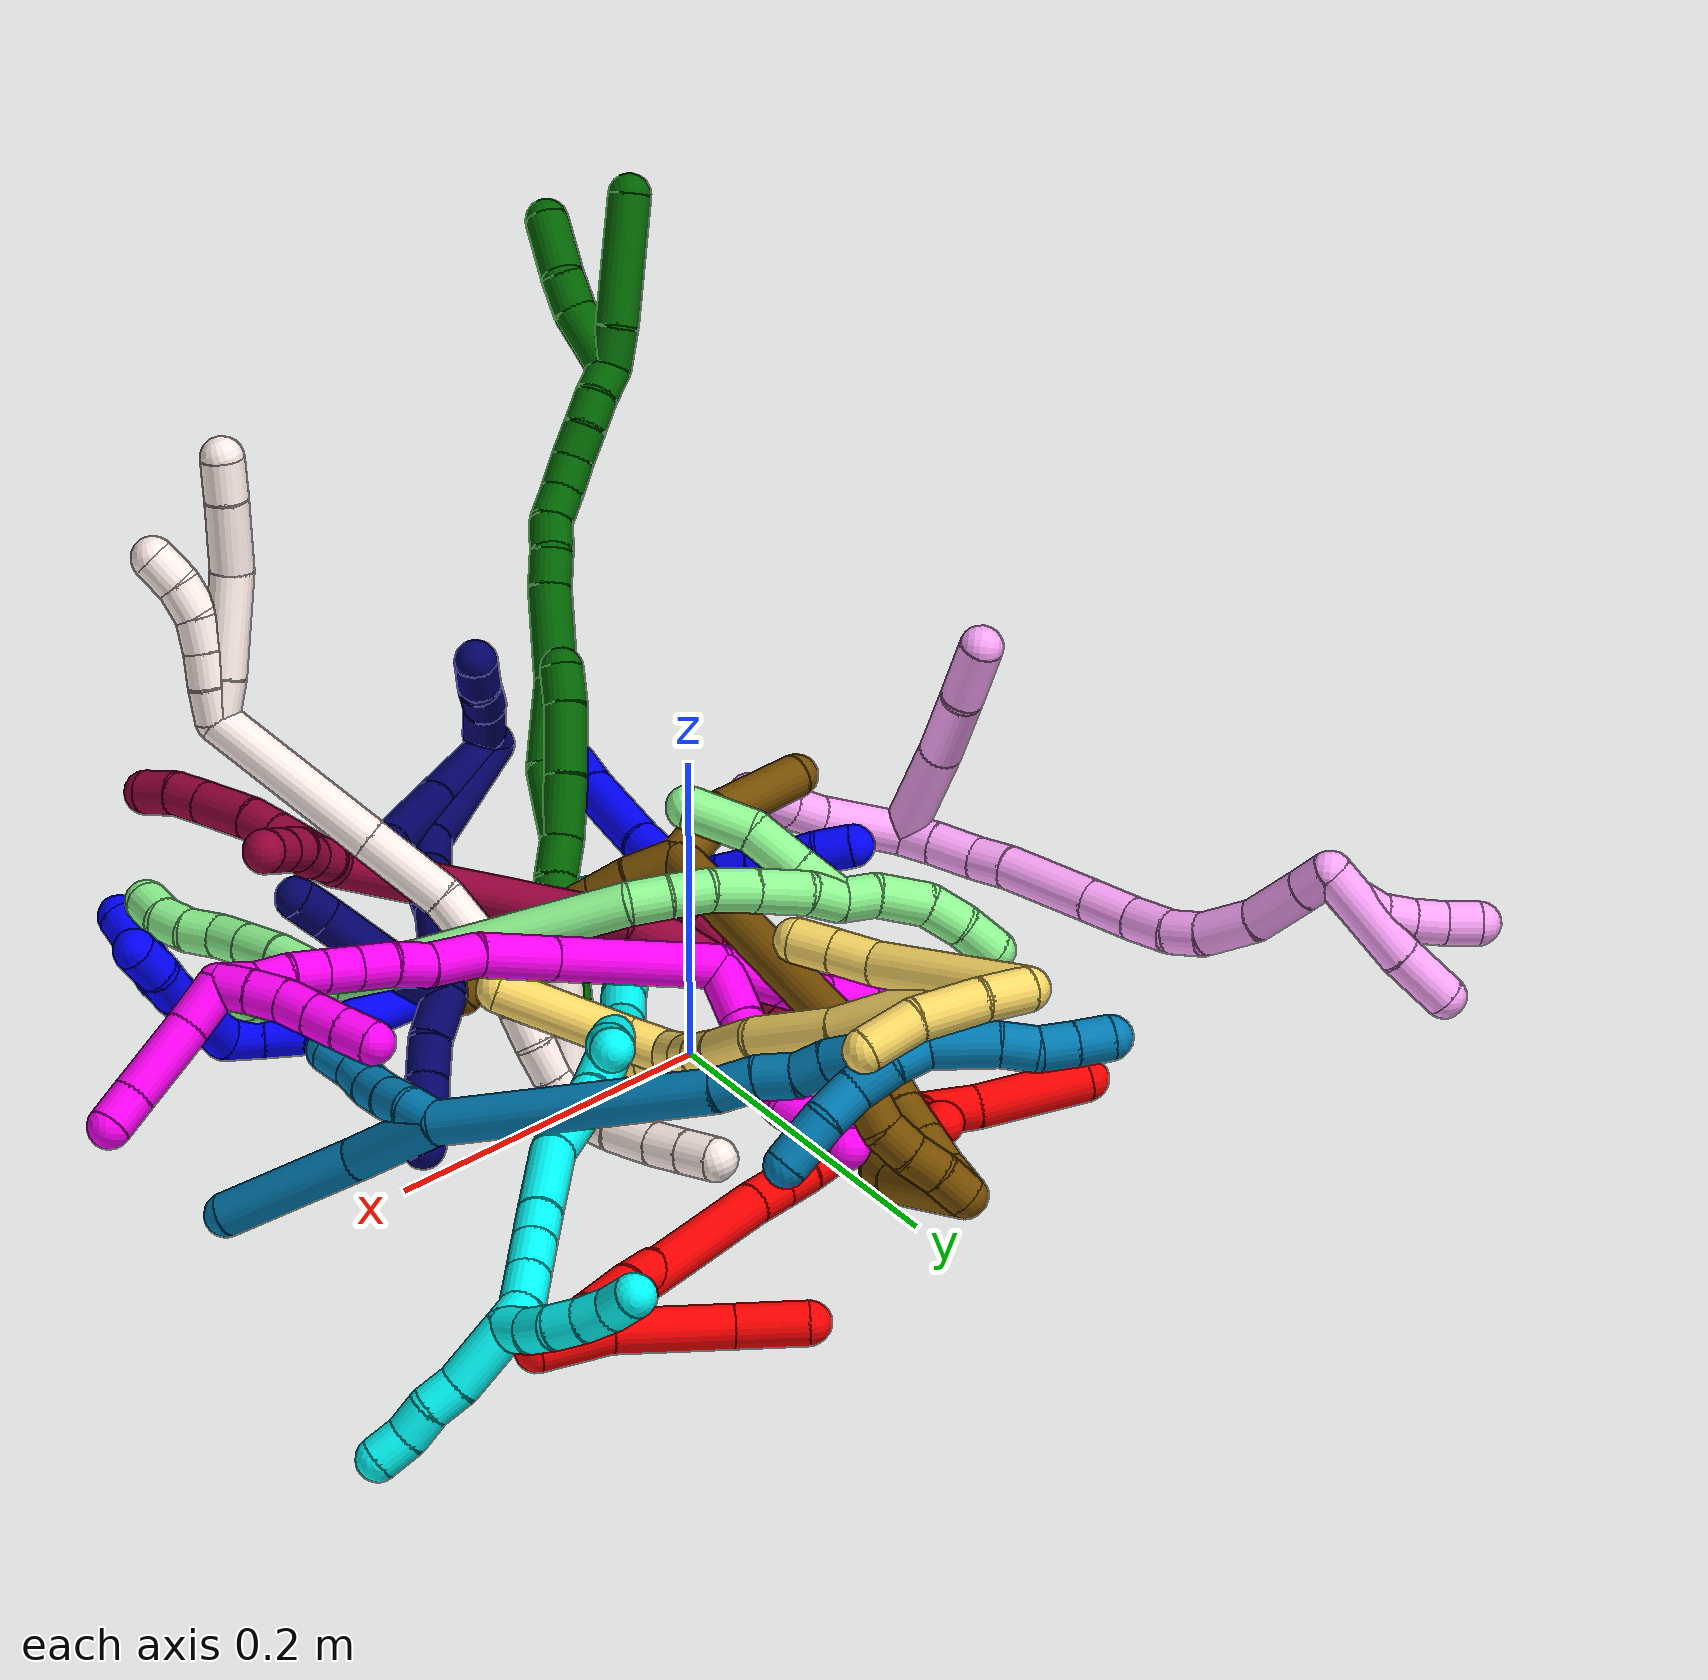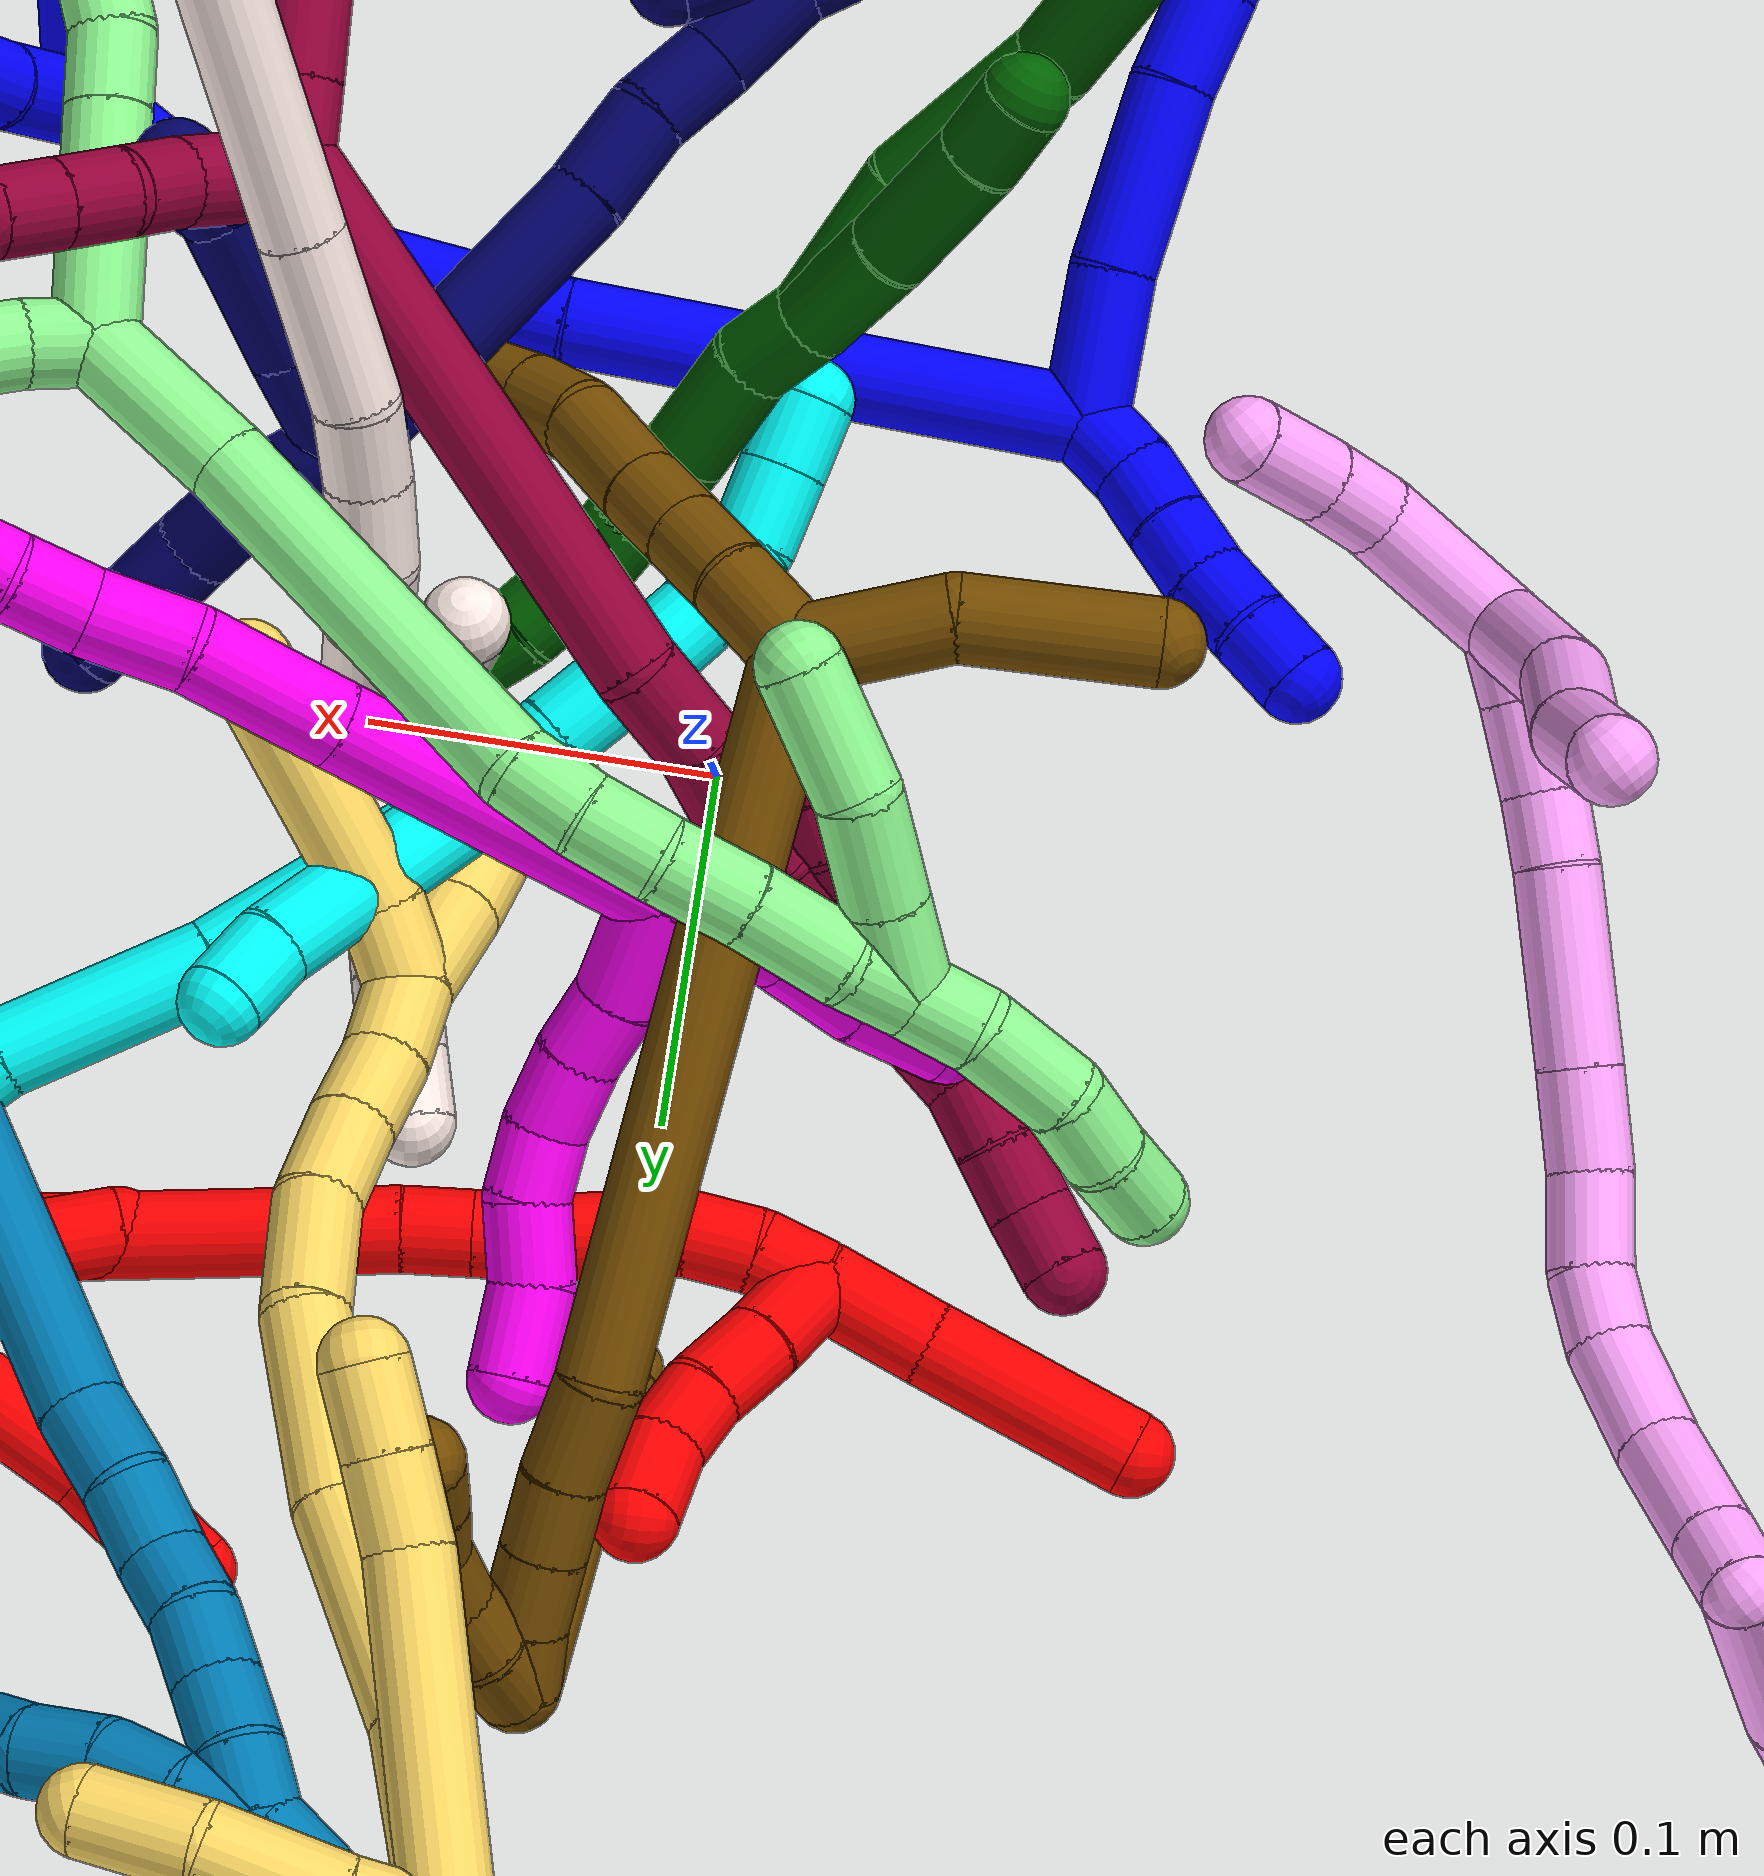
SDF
<sdf version="1.7">
 <world name="default">
  <plugin name="TubeGeneratorPlugin" filename="libtube_generator_plugin.so"/>
  <model name="photoneo_s_sensor">
   <static>1</static>
   <pose>0 0 2 1.57079 1.57079 3.14159</pose>
   <link name="link">
    <inertial><mass>0.1</mass></inertial>
    <sensor name="sensor" type="depth">
     <update_rate>30</update_rate>
     <camera>
      <horizontal_fov>1.22</horizontal_fov>
      <image><width>1920</width><height>1200</height><format>B8G8R8</format></image>
      <clip><near>0.1</near><far>4</far></clip>
      <depth_camera><output>points</output></depth_camera>
     </camera>
     <plugin name="camera_plugin" filename="libgazebo_ros_depth_camera.so">
      <baseline>0.2</baseline>
      <alwaysOn>1</alwaysOn>
      <updateRate>0.0</updateRate>
      <cameraName>camera_ir</cameraName>
      <imageTopicName>/camera/color/image_raw</imageTopicName>
      <cameraInfoTopicName>/camera/color/camera_info</cameraInfoTopicName>
      <depthImageTopicName>/camera/depth/image_raw</depthImageTopicName>
      <depthImageCameraInfoTopicName>/camera/depth/camera_info</depthImageCameraInfoTopicName>
      <pointCloudTopicName>/camera/depth/points</pointCloudTopicName>
      <frameName>fr_optical</frameName>
      <pointCloudCutoff>0.1</pointCloudCutoff>
      <pointCloudCutoffMax>2.0</pointCloudCutoffMax>
      <distortionK1>0</distortionK1>
      <distortionK2>0</distortionK2>
      <distortionK3>0</distortionK3>
      <distortionT1>0</distortionT1>
      <distortionT2>0</distortionT2>
      <CxPrime>0</CxPrime>
      <Cx>0</Cx>
      <Cy>0</Cy>
      <focalLength>0</focalLength>
      <hackBaseline>0</hackBaseline>
     </plugin>
    </sensor>
   </link>
  </model>
  <gravity>0 0 -9.8</gravity>
  <magnetic_field>6e-06 2.3e-05 -4.2e-05</magnetic_field>
  <atmosphere type="adiabatic"/>
  <physics name="default_physics" default="0" type="ode">
   <max_step_size>0.003</max_step_size>
   <real_time_factor>1</real_time_factor>
   <real_time_update_rate>1000</real_time_update_rate>
   <max_contacts>10000</max_contacts>
   <ode>
    <solver>
     <type>quick</type>
     <iters>100</iters>
     <sor>1.3</sor>
     <use_dynamic_moi_rescaling>0</use_dynamic_moi_rescaling>
    </solver>
    <constraints>
     <contact_max_correcting_vel>0</contact_max_correcting_vel>
     <contact_surface_layer>0.001</contact_surface_layer>
     <cfm>0</cfm>
     <erp>0.2</erp>
    </constraints>
   </ode>
  </physics>
  <scene><ambient>0.4 0.4 0.4 1</ambient><background>0.7 0.7 0.7 1</background><shadows>0</shadows></scene>
  <audio><device>default</device></audio>
  <spherical_coordinates>
   <surface_model>EARTH_WGS84</surface_model>
   <latitude_deg>0</latitude_deg>
   <longitude_deg>0</longitude_deg>
   <elevation>0</elevation>
   <heading_deg>0</heading_deg>
  </spherical_coordinates>
  <model name="bin">
   <static>1</static>
   <link name="bottom">
    <collision name="collision-bottom">
     <pose>0 0 -0.01 0 -0 0</pose>
     <geometry><box><size>0.8 0.6 0.02</size></box></geometry>
     <surface>
      <friction><ode><mu>100</mu><mu2>100</mu2></ode></friction>
      <contact><collide_bitmask>65535</collide_bitmask></contact>
     </surface>
    </collision>
   </link>
   <link name="west_wall">
    <collision name="collision-west_wall">
     <pose>-0.41 0 0.1 0 -0 0</pose>
     <geometry><box><size>0.02 0.6 0.2</size></box></geometry>
     <surface>
      <friction><ode><mu>100</mu><mu2>100</mu2></ode></friction>
      <contact><collide_bitmask>65535</collide_bitmask></contact>
     </surface>
    </collision>
   </link>
   <link name="east_wall">
    <collision name="collision-east_wall">
     <pose>0.41 0 0.1 0 -0 0</pose>
     <geometry><box><size>0.02 0.6 0.2</size></box></geometry>
     <surface>
      <friction><ode><mu>100</mu><mu2>100</mu2></ode></friction>
      <contact><collide_bitmask>65535</collide_bitmask></contact>
     </surface>
    </collision>
   </link>
   <link name="south_wall">
    <collision name="collision-south_wall">
     <pose>0 -0.31 0.1 0 -0 0</pose>
     <geometry><box><size>0.8 0.02 0.2</size></box></geometry>
     <surface>
      <friction><ode><mu>100</mu><mu2>100</mu2></ode></friction>
      <contact><collide_bitmask>65535</collide_bitmask></contact>
     </surface>
    </collision>
   </link>
   <link name="north_wall">
    <collision name="collision-north_wall">
     <pose>0 0.31 0.1 0 -0 0</pose>
     <geometry><box><size>0.8 0.02 0.2</size></box></geometry>
     <surface>
      <friction><ode><mu>100</mu><mu2>100</mu2></ode></friction>
      <contact><collide_bitmask>65535</collide_bitmask></contact>
     </surface>
    </collision>
   </link>
  </model>
  <model name="1">
   <static>0</static>
   <link name="1">
    <collision name="collision-cylinder-e_1_2_8">
     <pose>0.00542 0.011683 0.017354 -0.592518 0.2535 -0.077757</pose>
     <geometry><cylinder><radius>0.0125</radius><length>0.043222</length></cylinder></geometry>
     <surface>
      <friction><ode><mu>1.16</mu><mu2>1.16</mu2><slip1>0</slip1><slip2>0</slip2></ode></friction>
      <contact><ode><kp>1e+06</kp><kd>1</kd><max_vel>0</max_vel><min_depth>0.001</min_depth></ode></contact>
     </surface>
    </collision>
    <visual name="visual-cylinder-e_1_2_8">
     <pose>0.00542 0.011683 0.017354 -0.592518 0.2535 -0.077757</pose>
     <geometry><cylinder><radius>0.0125</radius><length>0.043222</length></cylinder></geometry>
     <material><ambient>0 0 1 1</ambient></material>
    </visual>
    <collision name="collision-cylinder-e_2_8_9">
     <pose>0.01445 0.036912 0.058126 -0.524424 0.132656 -0.035652</pose>
     <geometry><cylinder><radius>0.0125</radius><length>0.054587</length></cylinder></geometry>
     <surface>
      <friction><ode><mu>1.16</mu><mu2>1.16</mu2><slip1>0</slip1><slip2>0</slip2></ode></friction>
      <contact><ode><kp>1e+06</kp><kd>1</kd><max_vel>0</max_vel><min_depth>0.001</min_depth></ode></contact>
     </surface>
    </collision>
    <visual name="visual-cylinder-e_2_8_9">
     <pose>0.01445 0.036912 0.058126 -0.524424 0.132656 -0.035652</pose>
     <geometry><cylinder><radius>0.0125</radius><length>0.054587</length></cylinder></geometry>
     <material><ambient>0 0 1 1</ambient></material>
    </visual>
    <collision name="collision-cylinder-e_3_9_10">
     <pose>0.018479 0.05688 0.094693 -0.454361 0.028614 -0.006615</pose>
     <geometry><cylinder><radius>0.0125</radius><length>0.029278</length></cylinder></geometry>
     <surface>
      <friction><ode><mu>1.16</mu><mu2>1.16</mu2><slip1>0</slip1><slip2>0</slip2></ode></friction>
      <contact><ode><kp>1e+06</kp><kd>1</kd><max_vel>0</max_vel><min_depth>0.001</min_depth></ode></contact>
     </surface>
    </collision>
    <visual name="visual-cylinder-e_3_9_10">
     <pose>0.018479 0.05688 0.094693 -0.454361 0.028614 -0.006615</pose>
     <geometry><cylinder><radius>0.0125</radius><length>0.029278</length></cylinder></geometry>
     <material><ambient>0 0 1 1</ambient></material>
    </visual>
    <collision name="collision-cylinder-e_4_10_6">
     <pose>0.021539 0.065818 0.118701 -0.227586 0.23269 -0.026713</pose>
     <geometry><cylinder><radius>0.0125</radius><length>0.022913</length></cylinder></geometry>
     <surface>
      <friction><ode><mu>1.16</mu><mu2>1.16</mu2><slip1>0</slip1><slip2>0</slip2></ode></friction>
      <contact><ode><kp>1e+06</kp><kd>1</kd><max_vel>0</max_vel><min_depth>0.001</min_depth></ode></contact>
     </surface>
    </collision>
    <visual name="visual-cylinder-e_4_10_6">
     <pose>0.021539 0.065818 0.118701 -0.227586 0.23269 -0.026713</pose>
     <geometry><cylinder><radius>0.0125</radius><length>0.022913</length></cylinder></geometry>
     <material><ambient>0 0 1 1</ambient></material>
    </visual>
    <collision name="collision-cylinder-e_1_2_11">
     <pose>-0.009314 -0.000882 -0.003532 2.89701 -1.19816 -2.7854</pose>
     <geometry><cylinder><radius>0.0125</radius><length>0.02</length></cylinder></geometry>
     <surface>
      <friction><ode><mu>1.16</mu><mu2>1.16</mu2><slip1>0</slip1><slip2>0</slip2></ode></friction>
      <contact><ode><kp>1e+06</kp><kd>1</kd><max_vel>0</max_vel><min_depth>0.001</min_depth></ode></contact>
     </surface>
    </collision>
    <visual name="visual-cylinder-e_1_2_11">
     <pose>-0.009314 -0.000882 -0.003532 2.89701 -1.19816 -2.7854</pose>
     <geometry><cylinder><radius>0.0125</radius><length>0.02</length></cylinder></geometry>
     <material><ambient>0 0 1 1</ambient></material>
    </visual>
    <collision name="collision-cylinder-e_2_11_12">
     <pose>-0.0268 -0.001419 -0.012817 -3.0818 -0.956631 3.02636</pose>
     <geometry><cylinder><radius>0.0125</radius><length>0.02</length></cylinder></geometry>
     <surface>
      <friction><ode><mu>1.16</mu><mu2>1.16</mu2><slip1>0</slip1><slip2>0</slip2></ode></friction>
      <contact><ode><kp>1e+06</kp><kd>1</kd><max_vel>0</max_vel><min_depth>0.001</min_depth></ode></contact>
     </surface>
    </collision>
    <visual name="visual-cylinder-e_2_11_12">
     <pose>-0.0268 -0.001419 -0.012817 -3.0818 -0.956631 3.02636</pose>
     <geometry><cylinder><radius>0.0125</radius><length>0.02</length></cylinder></geometry>
     <material><ambient>0 0 1 1</ambient></material>
    </visual>
    <collision name="collision-cylinder-e_3_12_13">
     <pose>-0.043356 -0.001195 -0.02402 3.11957 -0.994171 -3.101</pose>
     <geometry><cylinder><radius>0.0125</radius><length>0.02</length></cylinder></geometry>
     <surface>
      <friction><ode><mu>1.16</mu><mu2>1.16</mu2><slip1>0</slip1><slip2>0</slip2></ode></friction>
      <contact><ode><kp>1e+06</kp><kd>1</kd><max_vel>0</max_vel><min_depth>0.001</min_depth></ode></contact>
     </surface>
    </collision>
    <visual name="visual-cylinder-e_3_12_13">
     <pose>-0.043356 -0.001195 -0.02402 3.11957 -0.994171 -3.101</pose>
     <geometry><cylinder><radius>0.0125</radius><length>0.02</length></cylinder></geometry>
     <material><ambient>0 0 1 1</ambient></material>
    </visual>
    <collision name="collision-cylinder-e_4_13_14">
     <pose>-0.060546 -0.000452 -0.034128 -2.95847 -1.07742 2.83673</pose>
     <geometry><cylinder><radius>0.0125</radius><length>0.02</length></cylinder></geometry>
     <surface>
      <friction><ode><mu>1.16</mu><mu2>1.16</mu2><slip1>0</slip1><slip2>0</slip2></ode></friction>
      <contact><ode><kp>1e+06</kp><kd>1</kd><max_vel>0</max_vel><min_depth>0.001</min_depth></ode></contact>
     </surface>
    </collision>
    <visual name="visual-cylinder-e_4_13_14">
     <pose>-0.060546 -0.000452 -0.034128 -2.95847 -1.07742 2.83673</pose>
     <geometry><cylinder><radius>0.0125</radius><length>0.02</length></cylinder></geometry>
     <material><ambient>0 0 1 1</ambient></material>
    </visual>
    <collision name="collision-cylinder-e_5_14_5">
     <pose>-0.078529 -0.000149 -0.042722 3.00044 -1.16183 -2.92705</pose>
     <geometry><cylinder><radius>0.0125</radius><length>0.02</length></cylinder></geometry>
     <surface>
      <friction><ode><mu>1.16</mu><mu2>1.16</mu2><slip1>0</slip1><slip2>0</slip2></ode></friction>
      <contact><ode><kp>1e+06</kp><kd>1</kd><max_vel>0</max_vel><min_depth>0.001</min_depth></ode></contact>
     </surface>
    </collision>
    <visual name="visual-cylinder-e_5_14_5">
     <pose>-0.078529 -0.000149 -0.042722 3.00044 -1.16183 -2.92705</pose>
     <geometry><cylinder><radius>0.0125</radius><length>0.02</length></cylinder></geometry>
     <material><ambient>0 0 1 1</ambient></material>
    </visual>
    <collision name="collision-cylinder-e_1_2_15">
     <pose>0.07142 -0.000656 -0.02118 3.11065 1.28236 3.10014</pose>
     <geometry><cylinder><radius>0.0125</radius><length>0.148994</length></cylinder></geometry>
     <surface>
      <friction><ode><mu>1.16</mu><mu2>1.16</mu2><slip1>0</slip1><slip2>0</slip2></ode></friction>
      <contact><ode><kp>1e+06</kp><kd>1</kd><max_vel>0</max_vel><min_depth>0.001</min_depth></ode></contact>
     </surface>
    </collision>
    <visual name="visual-cylinder-e_1_2_15">
     <pose>0.07142 -0.000656 -0.02118 3.11065 1.28236 3.10014</pose>
     <geometry><cylinder><radius>0.0125</radius><length>0.148994</length></cylinder></geometry>
     <material><ambient>0 0 1 1</ambient></material>
    </visual>
    <collision name="collision-cylinder-e_2_15_16">
     <pose>0.185522 -0.002557 -0.050429 2.98841 1.38183 2.95651</pose>
     <geometry><cylinder><radius>0.0125</radius><length>0.086913</length></cylinder></geometry>
     <surface>
      <friction><ode><mu>1.16</mu><mu2>1.16</mu2><slip1>0</slip1><slip2>0</slip2></ode></friction>
      <contact><ode><kp>1e+06</kp><kd>1</kd><max_vel>0</max_vel><min_depth>0.001</min_depth></ode></contact>
     </surface>
    </collision>
    <visual name="visual-cylinder-e_2_15_16">
     <pose>0.185522 -0.002557 -0.050429 2.98841 1.38183 2.95651</pose>
     <geometry><cylinder><radius>0.0125</radius><length>0.086913</length></cylinder></geometry>
     <material><ambient>0 0 1 1</ambient></material>
    </visual>
    <collision name="collision-cylinder-e_3_16_17">
     <pose>0.238445 -0.00196 -0.057978 -1.29642 1.38599 -1.12282</pose>
     <geometry><cylinder><radius>0.0125</radius><length>0.020834</length></cylinder></geometry>
     <surface>
      <friction><ode><mu>1.16</mu><mu2>1.16</mu2><slip1>0</slip1><slip2>0</slip2></ode></friction>
      <contact><ode><kp>1e+06</kp><kd>1</kd><max_vel>0</max_vel><min_depth>0.001</min_depth></ode></contact>
     </surface>
    </collision>
    <visual name="visual-cylinder-e_3_16_17">
     <pose>0.238445 -0.00196 -0.057978 -1.29642 1.38599 -1.12282</pose>
     <geometry><cylinder><radius>0.0125</radius><length>0.020834</length></cylinder></geometry>
     <material><ambient>0 0 1 1</ambient></material>
    </visual>
    <collision name="collision-cylinder-e_4_17_18">
     <pose>0.259496 0.002285 -0.055968 -1.01543 1.31504 -0.811507</pose>
     <geometry><cylinder><radius>0.0125</radius><length>0.02235</length></cylinder></geometry>
     <surface>
      <friction><ode><mu>1.16</mu><mu2>1.16</mu2><slip1>0</slip1><slip2>0</slip2></ode></friction>
      <contact><ode><kp>1e+06</kp><kd>1</kd><max_vel>0</max_vel><min_depth>0.001</min_depth></ode></contact>
     </surface>
    </collision>
    <visual name="visual-cylinder-e_4_17_18">
     <pose>0.259496 0.002285 -0.055968 -1.01543 1.31504 -0.811507</pose>
     <geometry><cylinder><radius>0.0125</radius><length>0.02235</length></cylinder></geometry>
     <material><ambient>0 0 1 1</ambient></material>
    </visual>
    <collision name="collision-cylinder-e_5_18_1">
     <pose>0.280386 0.00713 -0.053153 -1.07379 1.30178 -0.851231</pose>
     <geometry><cylinder><radius>0.0125</radius><length>0.020909</length></cylinder></geometry>
     <surface>
      <friction><ode><mu>1.16</mu><mu2>1.16</mu2><slip1>0</slip1><slip2>0</slip2></ode></friction>
      <contact><ode><kp>1e+06</kp><kd>1</kd><max_vel>0</max_vel><min_depth>0.001</min_depth></ode></contact>
     </surface>
    </collision>
    <visual name="visual-cylinder-e_5_18_1">
     <pose>0.280386 0.00713 -0.053153 -1.07379 1.30178 -0.851231</pose>
     <geometry><cylinder><radius>0.0125</radius><length>0.020909</length></cylinder></geometry>
     <material><ambient>0 0 1 1</ambient></material>
    </visual>
    <collision name="collision-cylinder-e_1_1_19">
     <pose>0.298591 0.022716 -0.062811 -2.26683 0.443016 -0.897685</pose>
     <geometry><cylinder><radius>0.0125</radius><length>0.037918</length></cylinder></geometry>
     <surface>
      <friction><ode><mu>1.16</mu><mu2>1.16</mu2><slip1>0</slip1><slip2>0</slip2></ode></friction>
      <contact><ode><kp>1e+06</kp><kd>1</kd><max_vel>0</max_vel><min_depth>0.001</min_depth></ode></contact>
     </surface>
    </collision>
    <visual name="visual-cylinder-e_1_1_19">
     <pose>0.298591 0.022716 -0.062811 -2.26683 0.443016 -0.897685</pose>
     <geometry><cylinder><radius>0.0125</radius><length>0.037918</length></cylinder></geometry>
     <material><ambient>0 0 1 1</ambient></material>
    </visual>
    <collision name="collision-cylinder-e_2_19_20">
     <pose>0.311978 0.042753 -0.078785 -2.19762 0.553625 -1.01573</pose>
     <geometry><cylinder><radius>0.0125</radius><length>0.020009</length></cylinder></geometry>
     <surface>
      <friction><ode><mu>1.16</mu><mu2>1.16</mu2><slip1>0</slip1><slip2>0</slip2></ode></friction>
      <contact><ode><kp>1e+06</kp><kd>1</kd><max_vel>0</max_vel><min_depth>0.001</min_depth></ode></contact>
     </surface>
    </collision>
    <visual name="visual-cylinder-e_2_19_20">
     <pose>0.311978 0.042753 -0.078785 -2.19762 0.553625 -1.01573</pose>
     <geometry><cylinder><radius>0.0125</radius><length>0.020009</length></cylinder></geometry>
     <material><ambient>0 0 1 1</ambient></material>
    </visual>
    <collision name="collision-cylinder-e_3_20_21">
     <pose>0.320911 0.057768 -0.0893 -2.16789 0.357766 -0.658312</pose>
     <geometry><cylinder><radius>0.0125</radius><length>0.020974</length></cylinder></geometry>
     <surface>
      <friction><ode><mu>1.16</mu><mu2>1.16</mu2><slip1>0</slip1><slip2>0</slip2></ode></friction>
      <contact><ode><kp>1e+06</kp><kd>1</kd><max_vel>0</max_vel><min_depth>0.001</min_depth></ode></contact>
     </surface>
    </collision>
    <visual name="visual-cylinder-e_3_20_21">
     <pose>0.320911 0.057768 -0.0893 -2.16789 0.357766 -0.658312</pose>
     <geometry><cylinder><radius>0.0125</radius><length>0.020974</length></cylinder></geometry>
     <material><ambient>0 0 1 1</ambient></material>
    </visual>
    <collision name="collision-cylinder-e_4_21_4">
     <pose>0.32968 0.074574 -0.097977 -1.91928 0.504208 -0.704608</pose>
     <geometry><cylinder><radius>0.0125</radius><length>0.021099</length></cylinder></geometry>
     <surface>
      <friction><ode><mu>1.16</mu><mu2>1.16</mu2><slip1>0</slip1><slip2>0</slip2></ode></friction>
      <contact><ode><kp>1e+06</kp><kd>1</kd><max_vel>0</max_vel><min_depth>0.001</min_depth></ode></contact>
     </surface>
    </collision>
    <visual name="visual-cylinder-e_4_21_4">
     <pose>0.32968 0.074574 -0.097977 -1.91928 0.504208 -0.704608</pose>
     <geometry><cylinder><radius>0.0125</radius><length>0.021099</length></cylinder></geometry>
     <material><ambient>0 0 1 1</ambient></material>
    </visual>
    <collision name="collision-cylinder-e_1_1_22">
     <pose>0.301086 0.029106 -0.036507 -0.905686 0.40428 -0.198776</pose>
     <geometry><cylinder><radius>0.0125</radius><length>0.054005</length></cylinder></geometry>
     <surface>
      <friction><ode><mu>1.16</mu><mu2>1.16</mu2><slip1>0</slip1><slip2>0</slip2></ode></friction>
      <contact><ode><kp>1e+06</kp><kd>1</kd><max_vel>0</max_vel><min_depth>0.001</min_depth></ode></contact>
     </surface>
    </collision>
    <visual name="visual-cylinder-e_1_1_22">
     <pose>0.301086 0.029106 -0.036507 -0.905686 0.40428 -0.198776</pose>
     <geometry><cylinder><radius>0.0125</radius><length>0.054005</length></cylinder></geometry>
     <material><ambient>0 0 1 1</ambient></material>
    </visual>
    <collision name="collision-cylinder-e_2_22_23">
     <pose>0.312702 0.057508 -0.012315 -0.785206 0.079138 -0.032785</pose>
     <geometry><cylinder><radius>0.0125</radius><length>0.025164</length></cylinder></geometry>
     <surface>
      <friction><ode><mu>1.16</mu><mu2>1.16</mu2><slip1>0</slip1><slip2>0</slip2></ode></friction>
      <contact><ode><kp>1e+06</kp><kd>1</kd><max_vel>0</max_vel><min_depth>0.001</min_depth></ode></contact>
     </surface>
    </collision>
    <visual name="visual-cylinder-e_2_22_23">
     <pose>0.312702 0.057508 -0.012315 -0.785206 0.079138 -0.032785</pose>
     <geometry><cylinder><radius>0.0125</radius><length>0.025164</length></cylinder></geometry>
     <material><ambient>0 0 1 1</ambient></material>
    </visual>
    <collision name="collision-cylinder-e_3_23_3">
     <pose>0.315202 0.073874 0.003625 -0.814915 0.14502 -0.062682</pose>
     <geometry><cylinder><radius>0.0125</radius><length>0.020831</length></cylinder></geometry>
     <surface>
      <friction><ode><mu>1.16</mu><mu2>1.16</mu2><slip1>0</slip1><slip2>0</slip2></ode></friction>
      <contact><ode><kp>1e+06</kp><kd>1</kd><max_vel>0</max_vel><min_depth>0.001</min_depth></ode></contact>
     </surface>
    </collision>
    <visual name="visual-cylinder-e_3_23_3">
     <pose>0.315202 0.073874 0.003625 -0.814915 0.14502 -0.062682</pose>
     <geometry><cylinder><radius>0.0125</radius><length>0.020831</length></cylinder></geometry>
     <material><ambient>0 0 1 1</ambient></material>
    </visual>
    <collision name="collision-sphere-3">
     <pose>0.316707 0.081374 0.010694 0 -0 0</pose>
     <geometry><sphere><radius>0.0125</radius></sphere></geometry>
     <surface>
      <friction><ode><mu>1.16</mu><mu2>1.16</mu2><slip1>0</slip1><slip2>0</slip2></ode></friction>
      <contact><ode><kp>1e+06</kp><kd>1</kd><max_vel>0</max_vel><min_depth>0.001</min_depth></ode></contact>
     </surface>
    </collision>
    <visual name="visual-sphere-3">
     <pose>0.316707 0.081374 0.010694 0 -0 0</pose>
     <geometry><sphere><radius>0.0125</radius></sphere></geometry>
     <material><ambient>0 0 1 1</ambient></material>
    </visual>
    <collision name="collision-sphere-23">
     <pose>0.313697 0.066375 -0.003445 0 -0 0</pose>
     <geometry><sphere><radius>0.0125</radius></sphere></geometry>
     <surface>
      <friction><ode><mu>1.16</mu><mu2>1.16</mu2><slip1>0</slip1><slip2>0</slip2></ode></friction>
      <contact><ode><kp>1e+06</kp><kd>1</kd><max_vel>0</max_vel><min_depth>0.001</min_depth></ode></contact>
     </surface>
    </collision>
    <visual name="visual-sphere-23">
     <pose>0.313697 0.066375 -0.003445 0 -0 0</pose>
     <geometry><sphere><radius>0.0125</radius></sphere></geometry>
     <material><ambient>0 0 1 1</ambient></material>
    </visual>
    <collision name="collision-sphere-22">
     <pose>0.311708 0.04864 -0.021186 0 -0 0</pose>
     <geometry><sphere><radius>0.0125</radius></sphere></geometry>
     <surface>
      <friction><ode><mu>1.16</mu><mu2>1.16</mu2><slip1>0</slip1><slip2>0</slip2></ode></friction>
      <contact><ode><kp>1e+06</kp><kd>1</kd><max_vel>0</max_vel><min_depth>0.001</min_depth></ode></contact>
     </surface>
    </collision>
    <visual name="visual-sphere-22">
     <pose>0.311708 0.04864 -0.021186 0 -0 0</pose>
     <geometry><sphere><radius>0.0125</radius></sphere></geometry>
     <material><ambient>0 0 1 1</ambient></material>
    </visual>
    <collision name="collision-sphere-4">
     <pose>0.334777 0.083255 -0.101131 0 -0 0</pose>
     <geometry><sphere><radius>0.0125</radius></sphere></geometry>
     <surface>
      <friction><ode><mu>1.16</mu><mu2>1.16</mu2><slip1>0</slip1><slip2>0</slip2></ode></friction>
      <contact><ode><kp>1e+06</kp><kd>1</kd><max_vel>0</max_vel><min_depth>0.001</min_depth></ode></contact>
     </surface>
    </collision>
    <visual name="visual-sphere-4">
     <pose>0.334777 0.083255 -0.101131 0 -0 0</pose>
     <geometry><sphere><radius>0.0125</radius></sphere></geometry>
     <material><ambient>0 0 1 1</ambient></material>
    </visual>
    <collision name="collision-sphere-21">
     <pose>0.324583 0.065892 -0.094823 0 -0 0</pose>
     <geometry><sphere><radius>0.0125</radius></sphere></geometry>
     <surface>
      <friction><ode><mu>1.16</mu><mu2>1.16</mu2><slip1>0</slip1><slip2>0</slip2></ode></friction>
      <contact><ode><kp>1e+06</kp><kd>1</kd><max_vel>0</max_vel><min_depth>0.001</min_depth></ode></contact>
     </surface>
    </collision>
    <visual name="visual-sphere-21">
     <pose>0.324583 0.065892 -0.094823 0 -0 0</pose>
     <geometry><sphere><radius>0.0125</radius></sphere></geometry>
     <material><ambient>0 0 1 1</ambient></material>
    </visual>
    <collision name="collision-sphere-20">
     <pose>0.317238 0.049645 -0.083777 0 -0 0</pose>
     <geometry><sphere><radius>0.0125</radius></sphere></geometry>
     <surface>
      <friction><ode><mu>1.16</mu><mu2>1.16</mu2><slip1>0</slip1><slip2>0</slip2></ode></friction>
      <contact><ode><kp>1e+06</kp><kd>1</kd><max_vel>0</max_vel><min_depth>0.001</min_depth></ode></contact>
     </surface>
    </collision>
    <visual name="visual-sphere-20">
     <pose>0.317238 0.049645 -0.083777 0 -0 0</pose>
     <geometry><sphere><radius>0.0125</radius></sphere></geometry>
     <material><ambient>0 0 1 1</ambient></material>
    </visual>
    <collision name="collision-sphere-11">
     <pose>-0.018627 -0.001763 -0.007065 0 -0 0</pose>
     <geometry><sphere><radius>0.0125</radius></sphere></geometry>
     <surface>
      <friction><ode><mu>1.16</mu><mu2>1.16</mu2><slip1>0</slip1><slip2>0</slip2></ode></friction>
      <contact><ode><kp>1e+06</kp><kd>1</kd><max_vel>0</max_vel><min_depth>0.001</min_depth></ode></contact>
     </surface>
    </collision>
    <visual name="visual-sphere-11">
     <pose>-0.018627 -0.001763 -0.007065 0 -0 0</pose>
     <geometry><sphere><radius>0.0125</radius></sphere></geometry>
     <material><ambient>0 0 1 1</ambient></material>
    </visual>
    <collision name="collision-sphere-6">
     <pose>0.024181 0.068333 0.129562 0 -0 0</pose>
     <geometry><sphere><radius>0.0125</radius></sphere></geometry>
     <surface>
      <friction><ode><mu>1.16</mu><mu2>1.16</mu2><slip1>0</slip1><slip2>0</slip2></ode></friction>
      <contact><ode><kp>1e+06</kp><kd>1</kd><max_vel>0</max_vel><min_depth>0.001</min_depth></ode></contact>
     </surface>
    </collision>
    <visual name="visual-sphere-6">
     <pose>0.024181 0.068333 0.129562 0 -0 0</pose>
     <geometry><sphere><radius>0.0125</radius></sphere></geometry>
     <material><ambient>0 0 1 1</ambient></material>
    </visual>
    <collision name="collision-sphere-10">
     <pose>0.018897 0.063303 0.107841 0 -0 0</pose>
     <geometry><sphere><radius>0.0125</radius></sphere></geometry>
     <surface>
      <friction><ode><mu>1.16</mu><mu2>1.16</mu2><slip1>0</slip1><slip2>0</slip2></ode></friction>
      <contact><ode><kp>1e+06</kp><kd>1</kd><max_vel>0</max_vel><min_depth>0.001</min_depth></ode></contact>
     </surface>
    </collision>
    <visual name="visual-sphere-10">
     <pose>0.018897 0.063303 0.107841 0 -0 0</pose>
     <geometry><sphere><radius>0.0125</radius></sphere></geometry>
     <material><ambient>0 0 1 1</ambient></material>
    </visual>
    <collision name="collision-sphere-9">
     <pose>0.01806 0.050458 0.081544 0 -0 0</pose>
     <geometry><sphere><radius>0.0125</radius></sphere></geometry>
     <surface>
      <friction><ode><mu>1.16</mu><mu2>1.16</mu2><slip1>0</slip1><slip2>0</slip2></ode></friction>
      <contact><ode><kp>1e+06</kp><kd>1</kd><max_vel>0</max_vel><min_depth>0.001</min_depth></ode></contact>
     </surface>
    </collision>
    <visual name="visual-sphere-9">
     <pose>0.01806 0.050458 0.081544 0 -0 0</pose>
     <geometry><sphere><radius>0.0125</radius></sphere></geometry>
     <material><ambient>0 0 1 1</ambient></material>
    </visual>
    <collision name="collision-sphere-2">
     <geometry><sphere><radius>0.0125</radius></sphere></geometry>
     <surface>
      <friction><ode><mu>1.16</mu><mu2>1.16</mu2><slip1>0</slip1><slip2>0</slip2></ode></friction>
      <contact><ode><kp>1e+06</kp><kd>1</kd><max_vel>0</max_vel><min_depth>0.001</min_depth></ode></contact>
     </surface>
    </collision>
    <visual name="visual-sphere-2">
     <geometry><sphere><radius>0.0125</radius></sphere></geometry>
     <material><ambient>0 0 1 1</ambient></material>
    </visual>
    <collision name="collision-sphere-19">
     <pose>0.306718 0.035861 -0.073793 0 -0 0</pose>
     <geometry><sphere><radius>0.0125</radius></sphere></geometry>
     <surface>
      <friction><ode><mu>1.16</mu><mu2>1.16</mu2><slip1>0</slip1><slip2>0</slip2></ode></friction>
      <contact><ode><kp>1e+06</kp><kd>1</kd><max_vel>0</max_vel><min_depth>0.001</min_depth></ode></contact>
     </surface>
    </collision>
    <visual name="visual-sphere-19">
     <pose>0.306718 0.035861 -0.073793 0 -0 0</pose>
     <geometry><sphere><radius>0.0125</radius></sphere></geometry>
     <material><ambient>0 0 1 1</ambient></material>
    </visual>
    <collision name="collision-sphere-8">
     <pose>0.01084 0.023366 0.034708 0 -0 0</pose>
     <geometry><sphere><radius>0.0125</radius></sphere></geometry>
     <surface>
      <friction><ode><mu>1.16</mu><mu2>1.16</mu2><slip1>0</slip1><slip2>0</slip2></ode></friction>
      <contact><ode><kp>1e+06</kp><kd>1</kd><max_vel>0</max_vel><min_depth>0.001</min_depth></ode></contact>
     </surface>
    </collision>
    <visual name="visual-sphere-8">
     <pose>0.01084 0.023366 0.034708 0 -0 0</pose>
     <geometry><sphere><radius>0.0125</radius></sphere></geometry>
     <material><ambient>0 0 1 1</ambient></material>
    </visual>
    <collision name="collision-sphere-12">
     <pose>-0.034973 -0.001074 -0.01857 0 -0 0</pose>
     <geometry><sphere><radius>0.0125</radius></sphere></geometry>
     <surface>
      <friction><ode><mu>1.16</mu><mu2>1.16</mu2><slip1>0</slip1><slip2>0</slip2></ode></friction>
      <contact><ode><kp>1e+06</kp><kd>1</kd><max_vel>0</max_vel><min_depth>0.001</min_depth></ode></contact>
     </surface>
    </collision>
    <visual name="visual-sphere-12">
     <pose>-0.034973 -0.001074 -0.01857 0 -0 0</pose>
     <geometry><sphere><radius>0.0125</radius></sphere></geometry>
     <material><ambient>0 0 1 1</ambient></material>
    </visual>
    <collision name="collision-sphere-13">
     <pose>-0.051739 -0.001315 -0.029471 0 -0 0</pose>
     <geometry><sphere><radius>0.0125</radius></sphere></geometry>
     <surface>
      <friction><ode><mu>1.16</mu><mu2>1.16</mu2><slip1>0</slip1><slip2>0</slip2></ode></friction>
      <contact><ode><kp>1e+06</kp><kd>1</kd><max_vel>0</max_vel><min_depth>0.001</min_depth></ode></contact>
     </surface>
    </collision>
    <visual name="visual-sphere-13">
     <pose>-0.051739 -0.001315 -0.029471 0 -0 0</pose>
     <geometry><sphere><radius>0.0125</radius></sphere></geometry>
     <material><ambient>0 0 1 1</ambient></material>
    </visual>
    <collision name="collision-sphere-14">
     <pose>-0.069353 0.00041 -0.038785 0 -0 0</pose>
     <geometry><sphere><radius>0.0125</radius></sphere></geometry>
     <surface>
      <friction><ode><mu>1.16</mu><mu2>1.16</mu2><slip1>0</slip1><slip2>0</slip2></ode></friction>
      <contact><ode><kp>1e+06</kp><kd>1</kd><max_vel>0</max_vel><min_depth>0.001</min_depth></ode></contact>
     </surface>
    </collision>
    <visual name="visual-sphere-14">
     <pose>-0.069353 0.00041 -0.038785 0 -0 0</pose>
     <geometry><sphere><radius>0.0125</radius></sphere></geometry>
     <material><ambient>0 0 1 1</ambient></material>
    </visual>
    <collision name="collision-sphere-5">
     <pose>-0.087704 -0.000709 -0.046659 0 -0 0</pose>
     <geometry><sphere><radius>0.0125</radius></sphere></geometry>
     <surface>
      <friction><ode><mu>1.16</mu><mu2>1.16</mu2><slip1>0</slip1><slip2>0</slip2></ode></friction>
      <contact><ode><kp>1e+06</kp><kd>1</kd><max_vel>0</max_vel><min_depth>0.001</min_depth></ode></contact>
     </surface>
    </collision>
    <visual name="visual-sphere-5">
     <pose>-0.087704 -0.000709 -0.046659 0 -0 0</pose>
     <geometry><sphere><radius>0.0125</radius></sphere></geometry>
     <material><ambient>0 0 1 1</ambient></material>
    </visual>
    <collision name="collision-sphere-15">
     <pose>0.142839 -0.001311 -0.042361 0 -0 0</pose>
     <geometry><sphere><radius>0.0125</radius></sphere></geometry>
     <surface>
      <friction><ode><mu>1.16</mu><mu2>1.16</mu2><slip1>0</slip1><slip2>0</slip2></ode></friction>
      <contact><ode><kp>1e+06</kp><kd>1</kd><max_vel>0</max_vel><min_depth>0.001</min_depth></ode></contact>
     </surface>
    </collision>
    <visual name="visual-sphere-15">
     <pose>0.142839 -0.001311 -0.042361 0 -0 0</pose>
     <geometry><sphere><radius>0.0125</radius></sphere></geometry>
     <material><ambient>0 0 1 1</ambient></material>
    </visual>
    <collision name="collision-sphere-16">
     <pose>0.228205 -0.003802 -0.058496 0 -0 0</pose>
     <geometry><sphere><radius>0.0125</radius></sphere></geometry>
     <surface>
      <friction><ode><mu>1.16</mu><mu2>1.16</mu2><slip1>0</slip1><slip2>0</slip2></ode></friction>
      <contact><ode><kp>1e+06</kp><kd>1</kd><max_vel>0</max_vel><min_depth>0.001</min_depth></ode></contact>
     </surface>
    </collision>
    <visual name="visual-sphere-16">
     <pose>0.228205 -0.003802 -0.058496 0 -0 0</pose>
     <geometry><sphere><radius>0.0125</radius></sphere></geometry>
     <material><ambient>0 0 1 1</ambient></material>
    </visual>
    <collision name="collision-sphere-17">
     <pose>0.248685 -0.000117 -0.057459 0 -0 0</pose>
     <geometry><sphere><radius>0.0125</radius></sphere></geometry>
     <surface>
      <friction><ode><mu>1.16</mu><mu2>1.16</mu2><slip1>0</slip1><slip2>0</slip2></ode></friction>
      <contact><ode><kp>1e+06</kp><kd>1</kd><max_vel>0</max_vel><min_depth>0.001</min_depth></ode></contact>
     </surface>
    </collision>
    <visual name="visual-sphere-17">
     <pose>0.248685 -0.000117 -0.057459 0 -0 0</pose>
     <geometry><sphere><radius>0.0125</radius></sphere></geometry>
     <material><ambient>0 0 1 1</ambient></material>
    </visual>
    <collision name="collision-sphere-18">
     <pose>0.270308 0.004687 -0.054478 0 -0 0</pose>
     <geometry><sphere><radius>0.0125</radius></sphere></geometry>
     <surface>
      <friction><ode><mu>1.16</mu><mu2>1.16</mu2><slip1>0</slip1><slip2>0</slip2></ode></friction>
      <contact><ode><kp>1e+06</kp><kd>1</kd><max_vel>0</max_vel><min_depth>0.001</min_depth></ode></contact>
     </surface>
    </collision>
    <visual name="visual-sphere-18">
     <pose>0.270308 0.004687 -0.054478 0 -0 0</pose>
     <geometry><sphere><radius>0.0125</radius></sphere></geometry>
     <material><ambient>0 0 1 1</ambient></material>
    </visual>
    <collision name="collision-sphere-1">
     <pose>0.290464 0.009572 -0.051828 0 -0 0</pose>
     <geometry><sphere><radius>0.0125</radius></sphere></geometry>
     <surface>
      <friction><ode><mu>1.16</mu><mu2>1.16</mu2><slip1>0</slip1><slip2>0</slip2></ode></friction>
      <contact><ode><kp>1e+06</kp><kd>1</kd><max_vel>0</max_vel><min_depth>0.001</min_depth></ode></contact>
     </surface>
    </collision>
    <visual name="visual-sphere-1">
     <pose>0.290464 0.009572 -0.051828 0 -0 0</pose>
     <geometry><sphere><radius>0.0125</radius></sphere></geometry>
     <material><ambient>0 0 1 1</ambient></material>
    </visual>
    <inertial>
     <pose>0.137371 0.019347 -0.018856 0 -0 0</pose>
     <mass>0.75</mass>
     <inertia>
      <ixx>-2.4e-05</ixx>
      <ixy>0</ixy>
      <ixz>0</ixz>
      <iyy>0.000399</iyy>
      <iyz>0</iyz>
      <izz>-0.00037</izz>
     </inertia>
    </inertial>
   </link>
   <pose>-0.087062 -0.115092 0.013547 2.05062 0.110208 -0.291021</pose>
  </model>
  <model name="2">
   <static>0</static>
   <link name="2">
    <collision name="collision-cylinder-e_1_2_8">
     <pose>-0.008056 0.004382 -0.018598 -2.9102 -0.399006 2.09828</pose>
     <geometry><cylinder><radius>0.0125</radius><length>0.041473</length></cylinder></geometry>
     <surface>
      <friction><ode><mu>1.16</mu><mu2>1.16</mu2><slip1>0</slip1><slip2>0</slip2></ode></friction>
      <contact><ode><kp>1e+06</kp><kd>1</kd><max_vel>0</max_vel><min_depth>0.001</min_depth></ode></contact>
     </surface>
    </collision>
    <visual name="visual-cylinder-e_1_2_8">
     <pose>-0.008056 0.004382 -0.018598 -2.9102 -0.399006 2.09828</pose>
     <geometry><cylinder><radius>0.0125</radius><length>0.041473</length></cylinder></geometry>
     <material><ambient>1 0 0 1</ambient></material>
    </visual>
    <collision name="collision-cylinder-e_2_8_9">
     <pose>-0.025675 0.021858 -0.066697 -2.72385 -0.288028 1.20003</pose>
     <geometry><cylinder><radius>0.0125</radius><length>0.067324</length></cylinder></geometry>
     <surface>
      <friction><ode><mu>1.16</mu><mu2>1.16</mu2><slip1>0</slip1><slip2>0</slip2></ode></friction>
      <contact><ode><kp>1e+06</kp><kd>1</kd><max_vel>0</max_vel><min_depth>0.001</min_depth></ode></contact>
     </surface>
    </collision>
    <visual name="visual-cylinder-e_2_8_9">
     <pose>-0.025675 0.021858 -0.066697 -2.72385 -0.288028 1.20003</pose>
     <geometry><cylinder><radius>0.0125</radius><length>0.067324</length></cylinder></geometry>
     <material><ambient>1 0 0 1</ambient></material>
    </visual>
    <collision name="collision-cylinder-e_3_9_6">
     <pose>-0.043792 0.043852 -0.11269 -2.64678 -0.42824 1.42161</pose>
     <geometry><cylinder><radius>0.0125</radius><length>0.041203</length></cylinder></geometry>
     <surface>
      <friction><ode><mu>1.16</mu><mu2>1.16</mu2><slip1>0</slip1><slip2>0</slip2></ode></friction>
      <contact><ode><kp>1e+06</kp><kd>1</kd><max_vel>0</max_vel><min_depth>0.001</min_depth></ode></contact>
     </surface>
    </collision>
    <visual name="visual-cylinder-e_3_9_6">
     <pose>-0.043792 0.043852 -0.11269 -2.64678 -0.42824 1.42161</pose>
     <geometry><cylinder><radius>0.0125</radius><length>0.041203</length></cylinder></geometry>
     <material><ambient>1 0 0 1</ambient></material>
    </visual>
    <collision name="collision-cylinder-e_1_2_10">
     <pose>-0.003393 -0.003649 -0.018988 2.95172 -0.173729 -1.48154</pose>
     <geometry><cylinder><radius>0.0125</radius><length>0.039263</length></cylinder></geometry>
     <surface>
      <friction><ode><mu>1.16</mu><mu2>1.16</mu2><slip1>0</slip1><slip2>0</slip2></ode></friction>
      <contact><ode><kp>1e+06</kp><kd>1</kd><max_vel>0</max_vel><min_depth>0.001</min_depth></ode></contact>
     </surface>
    </collision>
    <visual name="visual-cylinder-e_1_2_10">
     <pose>-0.003393 -0.003649 -0.018988 2.95172 -0.173729 -1.48154</pose>
     <geometry><cylinder><radius>0.0125</radius><length>0.039263</length></cylinder></geometry>
     <material><ambient>1 0 0 1</ambient></material>
    </visual>
    <collision name="collision-cylinder-e_2_10_11">
     <pose>-0.004939 -0.011906 -0.055173 2.8798 0.103446 0.749329</pose>
     <geometry><cylinder><radius>0.0125</radius><length>0.035797</length></cylinder></geometry>
     <surface>
      <friction><ode><mu>1.16</mu><mu2>1.16</mu2><slip1>0</slip1><slip2>0</slip2></ode></friction>
      <contact><ode><kp>1e+06</kp><kd>1</kd><max_vel>0</max_vel><min_depth>0.001</min_depth></ode></contact>
     </surface>
    </collision>
    <visual name="visual-cylinder-e_2_10_11">
     <pose>-0.004939 -0.011906 -0.055173 2.8798 0.103446 0.749329</pose>
     <geometry><cylinder><radius>0.0125</radius><length>0.035797</length></cylinder></geometry>
     <material><ambient>1 0 0 1</ambient></material>
    </visual>
    <collision name="collision-cylinder-e_3_11_5">
     <pose>-0.000439 -0.019124 -0.084272 2.92575 0.214217 1.5632</pose>
     <geometry><cylinder><radius>0.0125</radius><length>0.02494</length></cylinder></geometry>
     <surface>
      <friction><ode><mu>1.16</mu><mu2>1.16</mu2><slip1>0</slip1><slip2>0</slip2></ode></friction>
      <contact><ode><kp>1e+06</kp><kd>1</kd><max_vel>0</max_vel><min_depth>0.001</min_depth></ode></contact>
     </surface>
    </collision>
    <visual name="visual-cylinder-e_3_11_5">
     <pose>-0.000439 -0.019124 -0.084272 2.92575 0.214217 1.5632</pose>
     <geometry><cylinder><radius>0.0125</radius><length>0.02494</length></cylinder></geometry>
     <material><ambient>1 0 0 1</ambient></material>
    </visual>
    <collision name="collision-cylinder-e_1_2_12">
     <pose>0.002838 -0.002611 -0.014577 2.96439 0.189316 1.63722</pose>
     <geometry><cylinder><radius>0.0125</radius><length>0.030157</length></cylinder></geometry>
     <surface>
      <friction><ode><mu>1.16</mu><mu2>1.16</mu2><slip1>0</slip1><slip2>0</slip2></ode></friction>
      <contact><ode><kp>1e+06</kp><kd>1</kd><max_vel>0</max_vel><min_depth>0.001</min_depth></ode></contact>
     </surface>
    </collision>
    <visual name="visual-cylinder-e_1_2_12">
     <pose>0.002838 -0.002611 -0.014577 2.96439 0.189316 1.63722</pose>
     <geometry><cylinder><radius>0.0125</radius><length>0.030157</length></cylinder></geometry>
     <material><ambient>1 0 0 1</ambient></material>
    </visual>
    <collision name="collision-cylinder-e_2_12_13">
     <pose>0.001899 -0.021203 -0.101906 2.92535 -0.050656 -0.458574</pose>
     <geometry><cylinder><radius>0.0125</radius><length>0.149165</length></cylinder></geometry>
     <surface>
      <friction><ode><mu>1.16</mu><mu2>1.16</mu2><slip1>0</slip1><slip2>0</slip2></ode></friction>
      <contact><ode><kp>1e+06</kp><kd>1</kd><max_vel>0</max_vel><min_depth>0.001</min_depth></ode></contact>
     </surface>
    </collision>
    <visual name="visual-cylinder-e_2_12_13">
     <pose>0.001899 -0.021203 -0.101906 2.92535 -0.050656 -0.458574</pose>
     <geometry><cylinder><radius>0.0125</radius><length>0.149165</length></cylinder></geometry>
     <material><ambient>1 0 0 1</ambient></material>
    </visual>
    <collision name="collision-cylinder-e_3_13_14">
     <pose>-0.002853 -0.038677 -0.184532 2.99164 -0.097364 -1.15074</pose>
     <geometry><cylinder><radius>0.0125</radius><length>0.020066</length></cylinder></geometry>
     <surface>
      <friction><ode><mu>1.16</mu><mu2>1.16</mu2><slip1>0</slip1><slip2>0</slip2></ode></friction>
      <contact><ode><kp>1e+06</kp><kd>1</kd><max_vel>0</max_vel><min_depth>0.001</min_depth></ode></contact>
     </surface>
    </collision>
    <visual name="visual-cylinder-e_3_13_14">
     <pose>-0.002853 -0.038677 -0.184532 2.99164 -0.097364 -1.15074</pose>
     <geometry><cylinder><radius>0.0125</radius><length>0.020066</length></cylinder></geometry>
     <material><ambient>1 0 0 1</ambient></material>
    </visual>
    <collision name="collision-cylinder-e_4_14_15">
     <pose>-0.004822 -0.041654 -0.204302 2.99258 -0.098938 -1.1713</pose>
     <geometry><cylinder><radius>0.0125</radius><length>0.020115</length></cylinder></geometry>
     <surface>
      <friction><ode><mu>1.16</mu><mu2>1.16</mu2><slip1>0</slip1><slip2>0</slip2></ode></friction>
      <contact><ode><kp>1e+06</kp><kd>1</kd><max_vel>0</max_vel><min_depth>0.001</min_depth></ode></contact>
     </surface>
    </collision>
    <visual name="visual-cylinder-e_4_14_15">
     <pose>-0.004822 -0.041654 -0.204302 2.99258 -0.098938 -1.1713</pose>
     <geometry><cylinder><radius>0.0125</radius><length>0.020115</length></cylinder></geometry>
     <material><ambient>1 0 0 1</ambient></material>
    </visual>
    <collision name="collision-cylinder-e_5_15_16">
     <pose>-0.006346 -0.045393 -0.224106 2.91796 -0.052215 -0.457005</pose>
     <geometry><cylinder><radius>0.0125</radius><length>0.020347</length></cylinder></geometry>
     <surface>
      <friction><ode><mu>1.16</mu><mu2>1.16</mu2><slip1>0</slip1><slip2>0</slip2></ode></friction>
      <contact><ode><kp>1e+06</kp><kd>1</kd><max_vel>0</max_vel><min_depth>0.001</min_depth></ode></contact>
     </surface>
    </collision>
    <visual name="visual-cylinder-e_5_15_16">
     <pose>-0.006346 -0.045393 -0.224106 2.91796 -0.052215 -0.457005</pose>
     <geometry><cylinder><radius>0.0125</radius><length>0.020347</length></cylinder></geometry>
     <material><ambient>1 0 0 1</ambient></material>
    </visual>
    <collision name="collision-cylinder-e_6_16_17">
     <pose>-0.008258 -0.050444 -0.243522 2.85547 -0.138475 -0.897359</pose>
     <geometry><cylinder><radius>0.0125</radius><length>0.020016</length></cylinder></geometry>
     <surface>
      <friction><ode><mu>1.16</mu><mu2>1.16</mu2><slip1>0</slip1><slip2>0</slip2></ode></friction>
      <contact><ode><kp>1e+06</kp><kd>1</kd><max_vel>0</max_vel><min_depth>0.001</min_depth></ode></contact>
     </surface>
    </collision>
    <visual name="visual-cylinder-e_6_16_17">
     <pose>-0.008258 -0.050444 -0.243522 2.85547 -0.138475 -0.897359</pose>
     <geometry><cylinder><radius>0.0125</radius><length>0.020016</length></cylinder></geometry>
     <material><ambient>1 0 0 1</ambient></material>
    </visual>
    <collision name="collision-cylinder-e_7_17_18">
     <pose>-0.011701 -0.053162 -0.262845 -3.13353 -0.206976 3.06401</pose>
     <geometry><cylinder><radius>0.0125</radius><length>0.020058</length></cylinder></geometry>
     <surface>
      <friction><ode><mu>1.16</mu><mu2>1.16</mu2><slip1>0</slip1><slip2>0</slip2></ode></friction>
      <contact><ode><kp>1e+06</kp><kd>1</kd><max_vel>0</max_vel><min_depth>0.001</min_depth></ode></contact>
     </surface>
    </collision>
    <visual name="visual-cylinder-e_7_17_18">
     <pose>-0.011701 -0.053162 -0.262845 -3.13353 -0.206976 3.06401</pose>
     <geometry><cylinder><radius>0.0125</radius><length>0.020058</length></cylinder></geometry>
     <material><ambient>1 0 0 1</ambient></material>
    </visual>
    <collision name="collision-cylinder-e_8_18_1">
     <pose>-0.016478 -0.051002 -0.282097 -2.92454 -0.273969 1.80388</pose>
     <geometry><cylinder><radius>0.0125</radius><length>0.020077</length></cylinder></geometry>
     <surface>
      <friction><ode><mu>1.16</mu><mu2>1.16</mu2><slip1>0</slip1><slip2>0</slip2></ode></friction>
      <contact><ode><kp>1e+06</kp><kd>1</kd><max_vel>0</max_vel><min_depth>0.001</min_depth></ode></contact>
     </surface>
    </collision>
    <visual name="visual-cylinder-e_8_18_1">
     <pose>-0.016478 -0.051002 -0.282097 -2.92454 -0.273969 1.80388</pose>
     <geometry><cylinder><radius>0.0125</radius><length>0.020077</length></cylinder></geometry>
     <material><ambient>1 0 0 1</ambient></material>
    </visual>
    <collision name="collision-cylinder-e_1_1_19">
     <pose>-0.030053 -0.044553 -0.283187 -0.48205 -0.856173 0.22339</pose>
     <geometry><cylinder><radius>0.0125</radius><length>0.028753</length></cylinder></geometry>
     <surface>
      <friction><ode><mu>1.16</mu><mu2>1.16</mu2><slip1>0</slip1><slip2>0</slip2></ode></friction>
      <contact><ode><kp>1e+06</kp><kd>1</kd><max_vel>0</max_vel><min_depth>0.001</min_depth></ode></contact>
     </surface>
    </collision>
    <visual name="visual-cylinder-e_1_1_19">
     <pose>-0.030053 -0.044553 -0.283187 -0.48205 -0.856173 0.22339</pose>
     <geometry><cylinder><radius>0.0125</radius><length>0.028753</length></cylinder></geometry>
     <material><ambient>1 0 0 1</ambient></material>
    </visual>
    <collision name="collision-cylinder-e_2_19_20">
     <pose>-0.049507 -0.036306 -0.266911 -0.455059 -0.772103 0.187664</pose>
     <geometry><cylinder><radius>0.0125</radius><length>0.024641</length></cylinder></geometry>
     <surface>
      <friction><ode><mu>1.16</mu><mu2>1.16</mu2><slip1>0</slip1><slip2>0</slip2></ode></friction>
      <contact><ode><kp>1e+06</kp><kd>1</kd><max_vel>0</max_vel><min_depth>0.001</min_depth></ode></contact>
     </surface>
    </collision>
    <visual name="visual-cylinder-e_2_19_20">
     <pose>-0.049507 -0.036306 -0.266911 -0.455059 -0.772103 0.187664</pose>
     <geometry><cylinder><radius>0.0125</radius><length>0.024641</length></cylinder></geometry>
     <material><ambient>1 0 0 1</ambient></material>
    </visual>
    <collision name="collision-cylinder-e_3_20_21">
     <pose>-0.06591 -0.028013 -0.25381 -0.706415 -0.854357 0.332544</pose>
     <geometry><cylinder><radius>0.0125</radius><length>0.020706</length></cylinder></geometry>
     <surface>
      <friction><ode><mu>1.16</mu><mu2>1.16</mu2><slip1>0</slip1><slip2>0</slip2></ode></friction>
      <contact><ode><kp>1e+06</kp><kd>1</kd><max_vel>0</max_vel><min_depth>0.001</min_depth></ode></contact>
     </surface>
    </collision>
    <visual name="visual-cylinder-e_3_20_21">
     <pose>-0.06591 -0.028013 -0.25381 -0.706415 -0.854357 0.332544</pose>
     <geometry><cylinder><radius>0.0125</radius><length>0.020706</length></cylinder></geometry>
     <material><ambient>1 0 0 1</ambient></material>
    </visual>
    <collision name="collision-cylinder-e_4_21_4">
     <pose>-0.085485 -0.019472 -0.245146 -0.868511 -1.1401 0.577958</pose>
     <geometry><cylinder><radius>0.0125</radius><length>0.0259</length></cylinder></geometry>
     <surface>
      <friction><ode><mu>1.16</mu><mu2>1.16</mu2><slip1>0</slip1><slip2>0</slip2></ode></friction>
      <contact><ode><kp>1e+06</kp><kd>1</kd><max_vel>0</max_vel><min_depth>0.001</min_depth></ode></contact>
     </surface>
    </collision>
    <visual name="visual-cylinder-e_4_21_4">
     <pose>-0.085485 -0.019472 -0.245146 -0.868511 -1.1401 0.577958</pose>
     <geometry><cylinder><radius>0.0125</radius><length>0.0259</length></cylinder></geometry>
     <material><ambient>1 0 0 1</ambient></material>
    </visual>
    <collision name="collision-cylinder-e_1_1_22">
     <pose>-0.023701 -0.044108 -0.307645 -2.85127 -0.261901 1.46664</pose>
     <geometry><cylinder><radius>0.0125</radius><length>0.034814</length></cylinder></geometry>
     <surface>
      <friction><ode><mu>1.16</mu><mu2>1.16</mu2><slip1>0</slip1><slip2>0</slip2></ode></friction>
      <contact><ode><kp>1e+06</kp><kd>1</kd><max_vel>0</max_vel><min_depth>0.001</min_depth></ode></contact>
     </surface>
    </collision>
    <visual name="visual-cylinder-e_1_1_22">
     <pose>-0.023701 -0.044108 -0.307645 -2.85127 -0.261901 1.46664</pose>
     <geometry><cylinder><radius>0.0125</radius><length>0.034814</length></cylinder></geometry>
     <material><ambient>1 0 0 1</ambient></material>
    </visual>
    <collision name="collision-cylinder-e_2_22_3">
     <pose>-0.039626 -0.032761 -0.353575 -2.92589 -0.357912 2.0629</pose>
     <geometry><cylinder><radius>0.0125</radius><length>0.065186</length></cylinder></geometry>
     <surface>
      <friction><ode><mu>1.16</mu><mu2>1.16</mu2><slip1>0</slip1><slip2>0</slip2></ode></friction>
      <contact><ode><kp>1e+06</kp><kd>1</kd><max_vel>0</max_vel><min_depth>0.001</min_depth></ode></contact>
     </surface>
    </collision>
    <visual name="visual-cylinder-e_2_22_3">
     <pose>-0.039626 -0.032761 -0.353575 -2.92589 -0.357912 2.0629</pose>
     <geometry><cylinder><radius>0.0125</radius><length>0.065186</length></cylinder></geometry>
     <material><ambient>1 0 0 1</ambient></material>
    </visual>
    <collision name="collision-sphere-3">
     <pose>-0.051044 -0.026227 -0.383395 0 -0 0</pose>
     <geometry><sphere><radius>0.0125</radius></sphere></geometry>
     <surface>
      <friction><ode><mu>1.16</mu><mu2>1.16</mu2><slip1>0</slip1><slip2>0</slip2></ode></friction>
      <contact><ode><kp>1e+06</kp><kd>1</kd><max_vel>0</max_vel><min_depth>0.001</min_depth></ode></contact>
     </surface>
    </collision>
    <visual name="visual-sphere-3">
     <pose>-0.051044 -0.026227 -0.383395 0 -0 0</pose>
     <geometry><sphere><radius>0.0125</radius></sphere></geometry>
     <material><ambient>1 0 0 1</ambient></material>
    </visual>
    <collision name="collision-sphere-22">
     <pose>-0.028208 -0.039295 -0.323755 0 -0 0</pose>
     <geometry><sphere><radius>0.0125</radius></sphere></geometry>
     <surface>
      <friction><ode><mu>1.16</mu><mu2>1.16</mu2><slip1>0</slip1><slip2>0</slip2></ode></friction>
      <contact><ode><kp>1e+06</kp><kd>1</kd><max_vel>0</max_vel><min_depth>0.001</min_depth></ode></contact>
     </surface>
    </collision>
    <visual name="visual-sphere-22">
     <pose>-0.028208 -0.039295 -0.323755 0 -0 0</pose>
     <geometry><sphere><radius>0.0125</radius></sphere></geometry>
     <material><ambient>1 0 0 1</ambient></material>
    </visual>
    <collision name="collision-sphere-4">
     <pose>-0.097253 -0.015345 -0.241653 0 -0 0</pose>
     <geometry><sphere><radius>0.0125</radius></sphere></geometry>
     <surface>
      <friction><ode><mu>1.16</mu><mu2>1.16</mu2><slip1>0</slip1><slip2>0</slip2></ode></friction>
      <contact><ode><kp>1e+06</kp><kd>1</kd><max_vel>0</max_vel><min_depth>0.001</min_depth></ode></contact>
     </surface>
    </collision>
    <visual name="visual-sphere-4">
     <pose>-0.097253 -0.015345 -0.241653 0 -0 0</pose>
     <geometry><sphere><radius>0.0125</radius></sphere></geometry>
     <material><ambient>1 0 0 1</ambient></material>
    </visual>
    <collision name="collision-sphere-21">
     <pose>-0.073718 -0.0236 -0.248638 0 -0 0</pose>
     <geometry><sphere><radius>0.0125</radius></sphere></geometry>
     <surface>
      <friction><ode><mu>1.16</mu><mu2>1.16</mu2><slip1>0</slip1><slip2>0</slip2></ode></friction>
      <contact><ode><kp>1e+06</kp><kd>1</kd><max_vel>0</max_vel><min_depth>0.001</min_depth></ode></contact>
     </surface>
    </collision>
    <visual name="visual-sphere-21">
     <pose>-0.073718 -0.0236 -0.248638 0 -0 0</pose>
     <geometry><sphere><radius>0.0125</radius></sphere></geometry>
     <material><ambient>1 0 0 1</ambient></material>
    </visual>
    <collision name="collision-sphere-20">
     <pose>-0.058103 -0.032426 -0.258982 0 -0 0</pose>
     <geometry><sphere><radius>0.0125</radius></sphere></geometry>
     <surface>
      <friction><ode><mu>1.16</mu><mu2>1.16</mu2><slip1>0</slip1><slip2>0</slip2></ode></friction>
      <contact><ode><kp>1e+06</kp><kd>1</kd><max_vel>0</max_vel><min_depth>0.001</min_depth></ode></contact>
     </surface>
    </collision>
    <visual name="visual-sphere-20">
     <pose>-0.058103 -0.032426 -0.258982 0 -0 0</pose>
     <geometry><sphere><radius>0.0125</radius></sphere></geometry>
     <material><ambient>1 0 0 1</ambient></material>
    </visual>
    <collision name="collision-sphere-11">
     <pose>-0.00309 -0.016514 -0.07237 0 -0 0</pose>
     <geometry><sphere><radius>0.0125</radius></sphere></geometry>
     <surface>
      <friction><ode><mu>1.16</mu><mu2>1.16</mu2><slip1>0</slip1><slip2>0</slip2></ode></friction>
      <contact><ode><kp>1e+06</kp><kd>1</kd><max_vel>0</max_vel><min_depth>0.001</min_depth></ode></contact>
     </surface>
    </collision>
    <visual name="visual-sphere-11">
     <pose>-0.00309 -0.016514 -0.07237 0 -0 0</pose>
     <geometry><sphere><radius>0.0125</radius></sphere></geometry>
     <material><ambient>1 0 0 1</ambient></material>
    </visual>
    <collision name="collision-sphere-10">
     <pose>-0.006787 -0.007299 -0.037977 0 -0 0</pose>
     <geometry><sphere><radius>0.0125</radius></sphere></geometry>
     <surface>
      <friction><ode><mu>1.16</mu><mu2>1.16</mu2><slip1>0</slip1><slip2>0</slip2></ode></friction>
      <contact><ode><kp>1e+06</kp><kd>1</kd><max_vel>0</max_vel><min_depth>0.001</min_depth></ode></contact>
     </surface>
    </collision>
    <visual name="visual-sphere-10">
     <pose>-0.006787 -0.007299 -0.037977 0 -0 0</pose>
     <geometry><sphere><radius>0.0125</radius></sphere></geometry>
     <material><ambient>1 0 0 1</ambient></material>
    </visual>
    <collision name="collision-sphere-6">
     <pose>-0.052347 0.052751 -0.129183 0 -0 0</pose>
     <geometry><sphere><radius>0.0125</radius></sphere></geometry>
     <surface>
      <friction><ode><mu>1.16</mu><mu2>1.16</mu2><slip1>0</slip1><slip2>0</slip2></ode></friction>
      <contact><ode><kp>1e+06</kp><kd>1</kd><max_vel>0</max_vel><min_depth>0.001</min_depth></ode></contact>
     </surface>
    </collision>
    <visual name="visual-sphere-6">
     <pose>-0.052347 0.052751 -0.129183 0 -0 0</pose>
     <geometry><sphere><radius>0.0125</radius></sphere></geometry>
     <material><ambient>1 0 0 1</ambient></material>
    </visual>
    <collision name="collision-sphere-9">
     <pose>-0.035237 0.034952 -0.096197 0 -0 0</pose>
     <geometry><sphere><radius>0.0125</radius></sphere></geometry>
     <surface>
      <friction><ode><mu>1.16</mu><mu2>1.16</mu2><slip1>0</slip1><slip2>0</slip2></ode></friction>
      <contact><ode><kp>1e+06</kp><kd>1</kd><max_vel>0</max_vel><min_depth>0.001</min_depth></ode></contact>
     </surface>
    </collision>
    <visual name="visual-sphere-9">
     <pose>-0.035237 0.034952 -0.096197 0 -0 0</pose>
     <geometry><sphere><radius>0.0125</radius></sphere></geometry>
     <material><ambient>1 0 0 1</ambient></material>
    </visual>
    <collision name="collision-sphere-2">
     <geometry><sphere><radius>0.0125</radius></sphere></geometry>
     <surface>
      <friction><ode><mu>1.16</mu><mu2>1.16</mu2><slip1>0</slip1><slip2>0</slip2></ode></friction>
      <contact><ode><kp>1e+06</kp><kd>1</kd><max_vel>0</max_vel><min_depth>0.001</min_depth></ode></contact>
     </surface>
    </collision>
    <visual name="visual-sphere-2">
     <geometry><sphere><radius>0.0125</radius></sphere></geometry>
     <material><ambient>1 0 0 1</ambient></material>
    </visual>
    <collision name="collision-sphere-19">
     <pose>-0.040912 -0.040185 -0.274839 0 -0 0</pose>
     <geometry><sphere><radius>0.0125</radius></sphere></geometry>
     <surface>
      <friction><ode><mu>1.16</mu><mu2>1.16</mu2><slip1>0</slip1><slip2>0</slip2></ode></friction>
      <contact><ode><kp>1e+06</kp><kd>1</kd><max_vel>0</max_vel><min_depth>0.001</min_depth></ode></contact>
     </surface>
    </collision>
    <visual name="visual-sphere-19">
     <pose>-0.040912 -0.040185 -0.274839 0 -0 0</pose>
     <geometry><sphere><radius>0.0125</radius></sphere></geometry>
     <material><ambient>1 0 0 1</ambient></material>
    </visual>
    <collision name="collision-sphere-8">
     <pose>-0.016112 0.008764 -0.037197 0 -0 0</pose>
     <geometry><sphere><radius>0.0125</radius></sphere></geometry>
     <surface>
      <friction><ode><mu>1.16</mu><mu2>1.16</mu2><slip1>0</slip1><slip2>0</slip2></ode></friction>
      <contact><ode><kp>1e+06</kp><kd>1</kd><max_vel>0</max_vel><min_depth>0.001</min_depth></ode></contact>
     </surface>
    </collision>
    <visual name="visual-sphere-8">
     <pose>-0.016112 0.008764 -0.037197 0 -0 0</pose>
     <geometry><sphere><radius>0.0125</radius></sphere></geometry>
     <material><ambient>1 0 0 1</ambient></material>
    </visual>
    <collision name="collision-sphere-5">
     <pose>0.002211 -0.021733 -0.096174 0 -0 0</pose>
     <geometry><sphere><radius>0.0125</radius></sphere></geometry>
     <surface>
      <friction><ode><mu>1.16</mu><mu2>1.16</mu2><slip1>0</slip1><slip2>0</slip2></ode></friction>
      <contact><ode><kp>1e+06</kp><kd>1</kd><max_vel>0</max_vel><min_depth>0.001</min_depth></ode></contact>
     </surface>
    </collision>
    <visual name="visual-sphere-5">
     <pose>0.002211 -0.021733 -0.096174 0 -0 0</pose>
     <geometry><sphere><radius>0.0125</radius></sphere></geometry>
     <material><ambient>1 0 0 1</ambient></material>
    </visual>
    <collision name="collision-sphere-12">
     <pose>0.005675 -0.005221 -0.029155 0 -0 0</pose>
     <geometry><sphere><radius>0.0125</radius></sphere></geometry>
     <surface>
      <friction><ode><mu>1.16</mu><mu2>1.16</mu2><slip1>0</slip1><slip2>0</slip2></ode></friction>
      <contact><ode><kp>1e+06</kp><kd>1</kd><max_vel>0</max_vel><min_depth>0.001</min_depth></ode></contact>
     </surface>
    </collision>
    <visual name="visual-sphere-12">
     <pose>0.005675 -0.005221 -0.029155 0 -0 0</pose>
     <geometry><sphere><radius>0.0125</radius></sphere></geometry>
     <material><ambient>1 0 0 1</ambient></material>
    </visual>
    <collision name="collision-sphere-13">
     <pose>-0.001878 -0.037185 -0.174658 0 -0 0</pose>
     <geometry><sphere><radius>0.0125</radius></sphere></geometry>
     <surface>
      <friction><ode><mu>1.16</mu><mu2>1.16</mu2><slip1>0</slip1><slip2>0</slip2></ode></friction>
      <contact><ode><kp>1e+06</kp><kd>1</kd><max_vel>0</max_vel><min_depth>0.001</min_depth></ode></contact>
     </surface>
    </collision>
    <visual name="visual-sphere-13">
     <pose>-0.001878 -0.037185 -0.174658 0 -0 0</pose>
     <geometry><sphere><radius>0.0125</radius></sphere></geometry>
     <material><ambient>1 0 0 1</ambient></material>
    </visual>
    <collision name="collision-sphere-14">
     <pose>-0.003828 -0.040168 -0.194405 0 -0 0</pose>
     <geometry><sphere><radius>0.0125</radius></sphere></geometry>
     <surface>
      <friction><ode><mu>1.16</mu><mu2>1.16</mu2><slip1>0</slip1><slip2>0</slip2></ode></friction>
      <contact><ode><kp>1e+06</kp><kd>1</kd><max_vel>0</max_vel><min_depth>0.001</min_depth></ode></contact>
     </surface>
    </collision>
    <visual name="visual-sphere-14">
     <pose>-0.003828 -0.040168 -0.194405 0 -0 0</pose>
     <geometry><sphere><radius>0.0125</radius></sphere></geometry>
     <material><ambient>1 0 0 1</ambient></material>
    </visual>
    <collision name="collision-sphere-15">
     <pose>-0.005815 -0.04314 -0.214199 0 -0 0</pose>
     <geometry><sphere><radius>0.0125</radius></sphere></geometry>
     <surface>
      <friction><ode><mu>1.16</mu><mu2>1.16</mu2><slip1>0</slip1><slip2>0</slip2></ode></friction>
      <contact><ode><kp>1e+06</kp><kd>1</kd><max_vel>0</max_vel><min_depth>0.001</min_depth></ode></contact>
     </surface>
    </collision>
    <visual name="visual-sphere-15">
     <pose>-0.005815 -0.04314 -0.214199 0 -0 0</pose>
     <geometry><sphere><radius>0.0125</radius></sphere></geometry>
     <material><ambient>1 0 0 1</ambient></material>
    </visual>
    <collision name="collision-sphere-16">
     <pose>-0.006877 -0.047646 -0.234012 0 -0 0</pose>
     <geometry><sphere><radius>0.0125</radius></sphere></geometry>
     <surface>
      <friction><ode><mu>1.16</mu><mu2>1.16</mu2><slip1>0</slip1><slip2>0</slip2></ode></friction>
      <contact><ode><kp>1e+06</kp><kd>1</kd><max_vel>0</max_vel><min_depth>0.001</min_depth></ode></contact>
     </surface>
    </collision>
    <visual name="visual-sphere-16">
     <pose>-0.006877 -0.047646 -0.234012 0 -0 0</pose>
     <geometry><sphere><radius>0.0125</radius></sphere></geometry>
     <material><ambient>1 0 0 1</ambient></material>
    </visual>
    <collision name="collision-sphere-17">
     <pose>-0.00964 -0.053241 -0.253031 0 -0 0</pose>
     <geometry><sphere><radius>0.0125</radius></sphere></geometry>
     <surface>
      <friction><ode><mu>1.16</mu><mu2>1.16</mu2><slip1>0</slip1><slip2>0</slip2></ode></friction>
      <contact><ode><kp>1e+06</kp><kd>1</kd><max_vel>0</max_vel><min_depth>0.001</min_depth></ode></contact>
     </surface>
    </collision>
    <visual name="visual-sphere-17">
     <pose>-0.00964 -0.053241 -0.253031 0 -0 0</pose>
     <geometry><sphere><radius>0.0125</radius></sphere></geometry>
     <material><ambient>1 0 0 1</ambient></material>
    </visual>
    <collision name="collision-sphere-18">
     <pose>-0.013762 -0.053083 -0.27266 0 -0 0</pose>
     <geometry><sphere><radius>0.0125</radius></sphere></geometry>
     <surface>
      <friction><ode><mu>1.16</mu><mu2>1.16</mu2><slip1>0</slip1><slip2>0</slip2></ode></friction>
      <contact><ode><kp>1e+06</kp><kd>1</kd><max_vel>0</max_vel><min_depth>0.001</min_depth></ode></contact>
     </surface>
    </collision>
    <visual name="visual-sphere-18">
     <pose>-0.013762 -0.053083 -0.27266 0 -0 0</pose>
     <geometry><sphere><radius>0.0125</radius></sphere></geometry>
     <material><ambient>1 0 0 1</ambient></material>
    </visual>
    <collision name="collision-sphere-1">
     <pose>-0.019194 -0.048921 -0.291535 0 -0 0</pose>
     <geometry><sphere><radius>0.0125</radius></sphere></geometry>
     <surface>
      <friction><ode><mu>1.16</mu><mu2>1.16</mu2><slip1>0</slip1><slip2>0</slip2></ode></friction>
      <contact><ode><kp>1e+06</kp><kd>1</kd><max_vel>0</max_vel><min_depth>0.001</min_depth></ode></contact>
     </surface>
    </collision>
    <visual name="visual-sphere-1">
     <pose>-0.019194 -0.048921 -0.291535 0 -0 0</pose>
     <geometry><sphere><radius>0.0125</radius></sphere></geometry>
     <material><ambient>1 0 0 1</ambient></material>
    </visual>
    <inertial>
     <pose>-0.018539 -0.017862 -0.158176 0 -0 0</pose>
     <mass>0.75</mass>
     <inertia>
      <ixx>0.000187</ixx>
      <ixy>0</ixy>
      <ixz>0</ixz>
      <iyy>-0.000287</iyy>
      <iyz>0</iyz>
      <izz>4.3e-05</izz>
     </inertia>
    </inertial>
   </link>
   <pose>0.242382 0.174915 0.018903 -1.27788 0.998063 -1.29943</pose>
  </model>
  <model name="3">
   <static>0</static>
   <link name="3">
    <collision name="collision-cylinder-e_1_2_8">
     <pose>-0.00252 -0.004368 -0.013291 2.82407 -0.178192 -1.01784</pose>
     <geometry><cylinder><radius>0.0125</radius><length>0.02843</length></cylinder></geometry>
     <surface>
      <friction><ode><mu>1.16</mu><mu2>1.16</mu2><slip1>0</slip1><slip2>0</slip2></ode></friction>
      <contact><ode><kp>1e+06</kp><kd>1</kd><max_vel>0</max_vel><min_depth>0.001</min_depth></ode></contact>
     </surface>
    </collision>
    <visual name="visual-cylinder-e_1_2_8">
     <pose>-0.00252 -0.004368 -0.013291 2.82407 -0.178192 -1.01784</pose>
     <geometry><cylinder><radius>0.0125</radius><length>0.02843</length></cylinder></geometry>
     <material><ambient>0.003922 1 0.996078 1</ambient></material>
    </visual>
    <collision name="collision-cylinder-e_2_8_9">
     <pose>-0.007724 -0.012393 -0.036906 2.80118 -0.240416 -1.22521</pose>
     <geometry><cylinder><radius>0.0125</radius><length>0.022554</length></cylinder></geometry>
     <surface>
      <friction><ode><mu>1.16</mu><mu2>1.16</mu2><slip1>0</slip1><slip2>0</slip2></ode></friction>
      <contact><ode><kp>1e+06</kp><kd>1</kd><max_vel>0</max_vel><min_depth>0.001</min_depth></ode></contact>
     </surface>
    </collision>
    <visual name="visual-cylinder-e_2_8_9">
     <pose>-0.007724 -0.012393 -0.036906 2.80118 -0.240416 -1.22521</pose>
     <geometry><cylinder><radius>0.0125</radius><length>0.022554</length></cylinder></geometry>
     <material><ambient>0.003922 1 0.996078 1</ambient></material>
    </visual>
    <collision name="collision-cylinder-e_3_9_10">
     <pose>-0.013163 -0.018669 -0.061765 2.96328 -0.184337 -1.6042</pose>
     <geometry><cylinder><radius>0.0125</radius><length>0.030049</length></cylinder></geometry>
     <surface>
      <friction><ode><mu>1.16</mu><mu2>1.16</mu2><slip1>0</slip1><slip2>0</slip2></ode></friction>
      <contact><ode><kp>1e+06</kp><kd>1</kd><max_vel>0</max_vel><min_depth>0.001</min_depth></ode></contact>
     </surface>
    </collision>
    <visual name="visual-cylinder-e_3_9_10">
     <pose>-0.013163 -0.018669 -0.061765 2.96328 -0.184337 -1.6042</pose>
     <geometry><cylinder><radius>0.0125</radius><length>0.030049</length></cylinder></geometry>
     <material><ambient>0.003922 1 0.996078 1</ambient></material>
    </visual>
    <collision name="collision-cylinder-e_4_10_11">
     <pose>-0.015975 -0.023973 -0.088561 2.92603 -0.004617 -0.042667</pose>
     <geometry><cylinder><radius>0.0125</radius><length>0.025101</length></cylinder></geometry>
     <surface>
      <friction><ode><mu>1.16</mu><mu2>1.16</mu2><slip1>0</slip1><slip2>0</slip2></ode></friction>
      <contact><ode><kp>1e+06</kp><kd>1</kd><max_vel>0</max_vel><min_depth>0.001</min_depth></ode></contact>
     </surface>
    </collision>
    <visual name="visual-cylinder-e_4_10_11">
     <pose>-0.015975 -0.023973 -0.088561 2.92603 -0.004617 -0.042667</pose>
     <geometry><cylinder><radius>0.0125</radius><length>0.025101</length></cylinder></geometry>
     <material><ambient>0.003922 1 0.996078 1</ambient></material>
    </visual>
    <collision name="collision-cylinder-e_5_11_12">
     <pose>-0.012995 -0.030553 -0.111134 2.78051 0.268919 1.2756</pose>
     <geometry><cylinder><radius>0.0125</radius><length>0.02287</length></cylinder></geometry>
     <surface>
      <friction><ode><mu>1.16</mu><mu2>1.16</mu2><slip1>0</slip1><slip2>0</slip2></ode></friction>
      <contact><ode><kp>1e+06</kp><kd>1</kd><max_vel>0</max_vel><min_depth>0.001</min_depth></ode></contact>
     </surface>
    </collision>
    <visual name="visual-cylinder-e_5_11_12">
     <pose>-0.012995 -0.030553 -0.111134 2.78051 0.268919 1.2756</pose>
     <geometry><cylinder><radius>0.0125</radius><length>0.02287</length></cylinder></geometry>
     <material><ambient>0.003922 1 0.996078 1</ambient></material>
    </visual>
    <collision name="collision-cylinder-e_6_12_6">
     <pose>-0.007165 -0.038023 -0.130914 2.78046 0.269219 1.27653</pose>
     <geometry><cylinder><radius>0.0125</radius><length>0.020996</length></cylinder></geometry>
     <surface>
      <friction><ode><mu>1.16</mu><mu2>1.16</mu2><slip1>0</slip1><slip2>0</slip2></ode></friction>
      <contact><ode><kp>1e+06</kp><kd>1</kd><max_vel>0</max_vel><min_depth>0.001</min_depth></ode></contact>
     </surface>
    </collision>
    <visual name="visual-cylinder-e_6_12_6">
     <pose>-0.007165 -0.038023 -0.130914 2.78046 0.269219 1.27653</pose>
     <geometry><cylinder><radius>0.0125</radius><length>0.020996</length></cylinder></geometry>
     <material><ambient>0.003922 1 0.996078 1</ambient></material>
    </visual>
    <collision name="collision-cylinder-e_1_2_13">
     <pose>0.009607 -0.003585 0.037502 0.095309 0.249694 0.01197</pose>
     <geometry><cylinder><radius>0.0125</radius><length>0.077757</length></cylinder></geometry>
     <surface>
      <friction><ode><mu>1.16</mu><mu2>1.16</mu2><slip1>0</slip1><slip2>0</slip2></ode></friction>
      <contact><ode><kp>1e+06</kp><kd>1</kd><max_vel>0</max_vel><min_depth>0.001</min_depth></ode></contact>
     </surface>
    </collision>
    <visual name="visual-cylinder-e_1_2_13">
     <pose>0.009607 -0.003585 0.037502 0.095309 0.249694 0.01197</pose>
     <geometry><cylinder><radius>0.0125</radius><length>0.077757</length></cylinder></geometry>
     <material><ambient>0.003922 1 0.996078 1</ambient></material>
    </visual>
    <collision name="collision-cylinder-e_2_13_5">
     <pose>0.019861 -0.008333 0.086045 0.104932 0.058142 0.003054</pose>
     <geometry><cylinder><radius>0.0125</radius><length>0.022243</length></cylinder></geometry>
     <surface>
      <friction><ode><mu>1.16</mu><mu2>1.16</mu2><slip1>0</slip1><slip2>0</slip2></ode></friction>
      <contact><ode><kp>1e+06</kp><kd>1</kd><max_vel>0</max_vel><min_depth>0.001</min_depth></ode></contact>
     </surface>
    </collision>
    <visual name="visual-cylinder-e_2_13_5">
     <pose>0.019861 -0.008333 0.086045 0.104932 0.058142 0.003054</pose>
     <geometry><cylinder><radius>0.0125</radius><length>0.022243</length></cylinder></geometry>
     <material><ambient>0.003922 1 0.996078 1</ambient></material>
    </visual>
    <collision name="collision-cylinder-e_1_2_14">
     <pose>0.015165 0.009133 0.039325 -0.228199 0.359334 -0.041621</pose>
     <geometry><cylinder><radius>0.0125</radius><length>0.086253</length></cylinder></geometry>
     <surface>
      <friction><ode><mu>1.16</mu><mu2>1.16</mu2><slip1>0</slip1><slip2>0</slip2></ode></friction>
      <contact><ode><kp>1e+06</kp><kd>1</kd><max_vel>0</max_vel><min_depth>0.001</min_depth></ode></contact>
     </surface>
    </collision>
    <visual name="visual-cylinder-e_1_2_14">
     <pose>0.015165 0.009133 0.039325 -0.228199 0.359334 -0.041621</pose>
     <geometry><cylinder><radius>0.0125</radius><length>0.086253</length></cylinder></geometry>
     <material><ambient>0.003922 1 0.996078 1</ambient></material>
    </visual>
    <collision name="collision-cylinder-e_2_14_15">
     <pose>0.045498 0.027359 0.104824 -0.334367 0.500841 -0.08628</pose>
     <geometry><cylinder><radius>0.0125</radius><length>0.063174</length></cylinder></geometry>
     <surface>
      <friction><ode><mu>1.16</mu><mu2>1.16</mu2><slip1>0</slip1><slip2>0</slip2></ode></friction>
      <contact><ode><kp>1e+06</kp><kd>1</kd><max_vel>0</max_vel><min_depth>0.001</min_depth></ode></contact>
     </surface>
    </collision>
    <visual name="visual-cylinder-e_2_14_15">
     <pose>0.045498 0.027359 0.104824 -0.334367 0.500841 -0.08628</pose>
     <geometry><cylinder><radius>0.0125</radius><length>0.063174</length></cylinder></geometry>
     <material><ambient>0.003922 1 0.996078 1</ambient></material>
    </visual>
    <collision name="collision-cylinder-e_3_15_16">
     <pose>0.068341 0.04752 0.154594 -0.438569 0.286408 -0.064249</pose>
     <geometry><cylinder><radius>0.0125</radius><length>0.054342</length></cylinder></geometry>
     <surface>
      <friction><ode><mu>1.16</mu><mu2>1.16</mu2><slip1>0</slip1><slip2>0</slip2></ode></friction>
      <contact><ode><kp>1e+06</kp><kd>1</kd><max_vel>0</max_vel><min_depth>0.001</min_depth></ode></contact>
     </surface>
    </collision>
    <visual name="visual-cylinder-e_3_15_16">
     <pose>0.068341 0.04752 0.154594 -0.438569 0.286408 -0.064249</pose>
     <geometry><cylinder><radius>0.0125</radius><length>0.054342</length></cylinder></geometry>
     <material><ambient>0.003922 1 0.996078 1</ambient></material>
    </visual>
    <collision name="collision-cylinder-e_4_16_17">
     <pose>0.079132 0.063883 0.187353 -0.524048 0.286307 -0.077275</pose>
     <geometry><cylinder><radius>0.0125</radius><length>0.022062</length></cylinder></geometry>
     <surface>
      <friction><ode><mu>1.16</mu><mu2>1.16</mu2><slip1>0</slip1><slip2>0</slip2></ode></friction>
      <contact><ode><kp>1e+06</kp><kd>1</kd><max_vel>0</max_vel><min_depth>0.001</min_depth></ode></contact>
     </surface>
    </collision>
    <visual name="visual-cylinder-e_4_16_17">
     <pose>0.079132 0.063883 0.187353 -0.524048 0.286307 -0.077275</pose>
     <geometry><cylinder><radius>0.0125</radius><length>0.022062</length></cylinder></geometry>
     <material><ambient>0.003922 1 0.996078 1</ambient></material>
    </visual>
    <collision name="collision-cylinder-e_5_17_18">
     <pose>0.085802 0.075273 0.207059 -0.524107 0.283975 -0.076647</pose>
     <geometry><cylinder><radius>0.0125</radius><length>0.025375</length></cylinder></geometry>
     <surface>
      <friction><ode><mu>1.16</mu><mu2>1.16</mu2><slip1>0</slip1><slip2>0</slip2></ode></friction>
      <contact><ode><kp>1e+06</kp><kd>1</kd><max_vel>0</max_vel><min_depth>0.001</min_depth></ode></contact>
     </surface>
    </collision>
    <visual name="visual-cylinder-e_5_17_18">
     <pose>0.085802 0.075273 0.207059 -0.524107 0.283975 -0.076647</pose>
     <geometry><cylinder><radius>0.0125</radius><length>0.025375</length></cylinder></geometry>
     <material><ambient>0.003922 1 0.996078 1</ambient></material>
    </visual>
    <collision name="collision-cylinder-e_6_18_19">
     <pose>0.093221 0.087829 0.229043 -0.514157 0.286105 -0.075697</pose>
     <geometry><cylinder><radius>0.0125</radius><length>0.027388</length></cylinder></geometry>
     <surface>
      <friction><ode><mu>1.16</mu><mu2>1.16</mu2><slip1>0</slip1><slip2>0</slip2></ode></friction>
      <contact><ode><kp>1e+06</kp><kd>1</kd><max_vel>0</max_vel><min_depth>0.001</min_depth></ode></contact>
     </surface>
    </collision>
    <visual name="visual-cylinder-e_6_18_19">
     <pose>0.093221 0.087829 0.229043 -0.514157 0.286105 -0.075697</pose>
     <geometry><cylinder><radius>0.0125</radius><length>0.027388</length></cylinder></geometry>
     <material><ambient>0.003922 1 0.996078 1</ambient></material>
    </visual>
    <collision name="collision-cylinder-e_7_19_1">
     <pose>0.10264 0.096796 0.249281 -0.277442 0.545587 -0.078081</pose>
     <geometry><cylinder><radius>0.0125</radius><length>0.021407</length></cylinder></geometry>
     <surface>
      <friction><ode><mu>1.16</mu><mu2>1.16</mu2><slip1>0</slip1><slip2>0</slip2></ode></friction>
      <contact><ode><kp>1e+06</kp><kd>1</kd><max_vel>0</max_vel><min_depth>0.001</min_depth></ode></contact>
     </surface>
    </collision>
    <visual name="visual-cylinder-e_7_19_1">
     <pose>0.10264 0.096796 0.249281 -0.277442 0.545587 -0.078081</pose>
     <geometry><cylinder><radius>0.0125</radius><length>0.021407</length></cylinder></geometry>
     <material><ambient>0.003922 1 0.996078 1</ambient></material>
    </visual>
    <collision name="collision-cylinder-e_1_1_20">
     <pose>0.102933 0.098272 0.266522 0.121389 -0.554074 -0.034556</pose>
     <geometry><cylinder><radius>0.0125</radius><length>0.02</length></cylinder></geometry>
     <surface>
      <friction><ode><mu>1.16</mu><mu2>1.16</mu2><slip1>0</slip1><slip2>0</slip2></ode></friction>
      <contact><ode><kp>1e+06</kp><kd>1</kd><max_vel>0</max_vel><min_depth>0.001</min_depth></ode></contact>
     </surface>
    </collision>
    <visual name="visual-cylinder-e_1_1_20">
     <pose>0.102933 0.098272 0.266522 0.121389 -0.554074 -0.034556</pose>
     <geometry><cylinder><radius>0.0125</radius><length>0.02</length></cylinder></geometry>
     <material><ambient>0.003922 1 0.996078 1</ambient></material>
    </visual>
    <collision name="collision-cylinder-e_2_20_21">
     <pose>0.092377 0.094752 0.283073 0.29798 -0.557969 -0.085942</pose>
     <geometry><cylinder><radius>0.0125</radius><length>0.02</length></cylinder></geometry>
     <surface>
      <friction><ode><mu>1.16</mu><mu2>1.16</mu2><slip1>0</slip1><slip2>0</slip2></ode></friction>
      <contact><ode><kp>1e+06</kp><kd>1</kd><max_vel>0</max_vel><min_depth>0.001</min_depth></ode></contact>
     </surface>
    </collision>
    <visual name="visual-cylinder-e_2_20_21">
     <pose>0.092377 0.094752 0.283073 0.29798 -0.557969 -0.085942</pose>
     <geometry><cylinder><radius>0.0125</radius><length>0.02</length></cylinder></geometry>
     <material><ambient>0.003922 1 0.996078 1</ambient></material>
    </visual>
    <collision name="collision-cylinder-e_3_21_22">
     <pose>0.079796 0.08935 0.297382 0.439025 -0.816292 -0.192361</pose>
     <geometry><cylinder><radius>0.0125</radius><length>0.02</length></cylinder></geometry>
     <surface>
      <friction><ode><mu>1.16</mu><mu2>1.16</mu2><slip1>0</slip1><slip2>0</slip2></ode></friction>
      <contact><ode><kp>1e+06</kp><kd>1</kd><max_vel>0</max_vel><min_depth>0.001</min_depth></ode></contact>
     </surface>
    </collision>
    <visual name="visual-cylinder-e_3_21_22">
     <pose>0.079796 0.08935 0.297382 0.439025 -0.816292 -0.192361</pose>
     <geometry><cylinder><radius>0.0125</radius><length>0.02</length></cylinder></geometry>
     <material><ambient>0.003922 1 0.996078 1</ambient></material>
    </visual>
    <collision name="collision-cylinder-e_4_22_23">
     <pose>0.065605 0.082507 0.309654 0.574587 -0.762104 -0.235652</pose>
     <geometry><cylinder><radius>0.0125</radius><length>0.02</length></cylinder></geometry>
     <surface>
      <friction><ode><mu>1.16</mu><mu2>1.16</mu2><slip1>0</slip1><slip2>0</slip2></ode></friction>
      <contact><ode><kp>1e+06</kp><kd>1</kd><max_vel>0</max_vel><min_depth>0.001</min_depth></ode></contact>
     </surface>
    </collision>
    <visual name="visual-cylinder-e_4_22_23">
     <pose>0.065605 0.082507 0.309654 0.574587 -0.762104 -0.235652</pose>
     <geometry><cylinder><radius>0.0125</radius><length>0.02</length></cylinder></geometry>
     <material><ambient>0.003922 1 0.996078 1</ambient></material>
    </visual>
    <collision name="collision-cylinder-e_5_23_4">
     <pose>0.05381 0.073672 0.32294 0.596975 -0.511028 -0.160402</pose>
     <geometry><cylinder><radius>0.0125</radius><length>0.02</length></cylinder></geometry>
     <surface>
      <friction><ode><mu>1.16</mu><mu2>1.16</mu2><slip1>0</slip1><slip2>0</slip2></ode></friction>
      <contact><ode><kp>1e+06</kp><kd>1</kd><max_vel>0</max_vel><min_depth>0.001</min_depth></ode></contact>
     </surface>
    </collision>
    <visual name="visual-cylinder-e_5_23_4">
     <pose>0.05381 0.073672 0.32294 0.596975 -0.511028 -0.160402</pose>
     <geometry><cylinder><radius>0.0125</radius><length>0.02</length></cylinder></geometry>
     <material><ambient>0.003922 1 0.996078 1</ambient></material>
    </visual>
    <collision name="collision-cylinder-e_1_1_24">
     <pose>0.121326 0.114149 0.255814 -1.72229 0.718416 -0.824275</pose>
     <geometry><cylinder><radius>0.0125</radius><length>0.039901</length></cylinder></geometry>
     <surface>
      <friction><ode><mu>1.16</mu><mu2>1.16</mu2><slip1>0</slip1><slip2>0</slip2></ode></friction>
      <contact><ode><kp>1e+06</kp><kd>1</kd><max_vel>0</max_vel><min_depth>0.001</min_depth></ode></contact>
     </surface>
    </collision>
    <visual name="visual-cylinder-e_1_1_24">
     <pose>0.121326 0.114149 0.255814 -1.72229 0.718416 -0.824275</pose>
     <geometry><cylinder><radius>0.0125</radius><length>0.039901</length></cylinder></geometry>
     <material><ambient>0.003922 1 0.996078 1</ambient></material>
    </visual>
    <collision name="collision-cylinder-e_2_24_25">
     <pose>0.142536 0.134856 0.252641 -1.72426 0.937785 -1.06749</pose>
     <geometry><cylinder><radius>0.0125</radius><length>0.020042</length></cylinder></geometry>
     <surface>
      <friction><ode><mu>1.16</mu><mu2>1.16</mu2><slip1>0</slip1><slip2>0</slip2></ode></friction>
      <contact><ode><kp>1e+06</kp><kd>1</kd><max_vel>0</max_vel><min_depth>0.001</min_depth></ode></contact>
     </surface>
    </collision>
    <visual name="visual-cylinder-e_2_24_25">
     <pose>0.142536 0.134856 0.252641 -1.72426 0.937785 -1.06749</pose>
     <geometry><cylinder><radius>0.0125</radius><length>0.020042</length></cylinder></geometry>
     <material><ambient>0.003922 1 0.996078 1</ambient></material>
    </visual>
    <collision name="collision-cylinder-e_3_25_26">
     <pose>0.156714 0.148384 0.249655 -1.83561 0.654504 -0.835324</pose>
     <geometry><cylinder><radius>0.0125</radius><length>0.020035</length></cylinder></geometry>
     <surface>
      <friction><ode><mu>1.16</mu><mu2>1.16</mu2><slip1>0</slip1><slip2>0</slip2></ode></friction>
      <contact><ode><kp>1e+06</kp><kd>1</kd><max_vel>0</max_vel><min_depth>0.001</min_depth></ode></contact>
     </surface>
    </collision>
    <visual name="visual-cylinder-e_3_25_26">
     <pose>0.156714 0.148384 0.249655 -1.83561 0.654504 -0.835324</pose>
     <geometry><cylinder><radius>0.0125</radius><length>0.020035</length></cylinder></geometry>
     <material><ambient>0.003922 1 0.996078 1</ambient></material>
    </visual>
    <collision name="collision-cylinder-e_4_26_3">
     <pose>0.170752 0.162024 0.246324 -1.77731 0.915778 -1.09076</pose>
     <geometry><cylinder><radius>0.0125</radius><length>0.020022</length></cylinder></geometry>
     <surface>
      <friction><ode><mu>1.16</mu><mu2>1.16</mu2><slip1>0</slip1><slip2>0</slip2></ode></friction>
      <contact><ode><kp>1e+06</kp><kd>1</kd><max_vel>0</max_vel><min_depth>0.001</min_depth></ode></contact>
     </surface>
    </collision>
    <visual name="visual-cylinder-e_4_26_3">
     <pose>0.170752 0.162024 0.246324 -1.77731 0.915778 -1.09076</pose>
     <geometry><cylinder><radius>0.0125</radius><length>0.020022</length></cylinder></geometry>
     <material><ambient>0.003922 1 0.996078 1</ambient></material>
    </visual>
    <collision name="collision-sphere-3">
     <pose>0.178691 0.167992 0.245074 0 -0 0</pose>
     <geometry><sphere><radius>0.0125</radius></sphere></geometry>
     <surface>
      <friction><ode><mu>1.16</mu><mu2>1.16</mu2><slip1>0</slip1><slip2>0</slip2></ode></friction>
      <contact><ode><kp>1e+06</kp><kd>1</kd><max_vel>0</max_vel><min_depth>0.001</min_depth></ode></contact>
     </surface>
    </collision>
    <visual name="visual-sphere-3">
     <pose>0.178691 0.167992 0.245074 0 -0 0</pose>
     <geometry><sphere><radius>0.0125</radius></sphere></geometry>
     <material><ambient>0.003922 1 0.996078 1</ambient></material>
    </visual>
    <collision name="collision-sphere-26">
     <pose>0.162813 0.156055 0.247575 0 -0 0</pose>
     <geometry><sphere><radius>0.0125</radius></sphere></geometry>
     <surface>
      <friction><ode><mu>1.16</mu><mu2>1.16</mu2><slip1>0</slip1><slip2>0</slip2></ode></friction>
      <contact><ode><kp>1e+06</kp><kd>1</kd><max_vel>0</max_vel><min_depth>0.001</min_depth></ode></contact>
     </surface>
    </collision>
    <visual name="visual-sphere-26">
     <pose>0.162813 0.156055 0.247575 0 -0 0</pose>
     <geometry><sphere><radius>0.0125</radius></sphere></geometry>
     <material><ambient>0.003922 1 0.996078 1</ambient></material>
    </visual>
    <collision name="collision-sphere-25">
     <pose>0.150616 0.140714 0.251735 0 -0 0</pose>
     <geometry><sphere><radius>0.0125</radius></sphere></geometry>
     <surface>
      <friction><ode><mu>1.16</mu><mu2>1.16</mu2><slip1>0</slip1><slip2>0</slip2></ode></friction>
      <contact><ode><kp>1e+06</kp><kd>1</kd><max_vel>0</max_vel><min_depth>0.001</min_depth></ode></contact>
     </surface>
    </collision>
    <visual name="visual-sphere-25">
     <pose>0.150616 0.140714 0.251735 0 -0 0</pose>
     <geometry><sphere><radius>0.0125</radius></sphere></geometry>
     <material><ambient>0.003922 1 0.996078 1</ambient></material>
    </visual>
    <collision name="collision-sphere-24">
     <pose>0.134457 0.128997 0.253547 0 -0 0</pose>
     <geometry><sphere><radius>0.0125</radius></sphere></geometry>
     <surface>
      <friction><ode><mu>1.16</mu><mu2>1.16</mu2><slip1>0</slip1><slip2>0</slip2></ode></friction>
      <contact><ode><kp>1e+06</kp><kd>1</kd><max_vel>0</max_vel><min_depth>0.001</min_depth></ode></contact>
     </surface>
    </collision>
    <visual name="visual-sphere-24">
     <pose>0.134457 0.128997 0.253547 0 -0 0</pose>
     <geometry><sphere><radius>0.0125</radius></sphere></geometry>
     <material><ambient>0.003922 1 0.996078 1</ambient></material>
    </visual>
    <collision name="collision-sphere-4">
     <pose>0.048919 0.068769 0.330154 0 -0 0</pose>
     <geometry><sphere><radius>0.0125</radius></sphere></geometry>
     <surface>
      <friction><ode><mu>1.16</mu><mu2>1.16</mu2><slip1>0</slip1><slip2>0</slip2></ode></friction>
      <contact><ode><kp>1e+06</kp><kd>1</kd><max_vel>0</max_vel><min_depth>0.001</min_depth></ode></contact>
     </surface>
    </collision>
    <visual name="visual-sphere-4">
     <pose>0.048919 0.068769 0.330154 0 -0 0</pose>
     <geometry><sphere><radius>0.0125</radius></sphere></geometry>
     <material><ambient>0.003922 1 0.996078 1</ambient></material>
    </visual>
    <collision name="collision-sphere-23">
     <pose>0.058701 0.078575 0.315726 0 -0 0</pose>
     <geometry><sphere><radius>0.0125</radius></sphere></geometry>
     <surface>
      <friction><ode><mu>1.16</mu><mu2>1.16</mu2><slip1>0</slip1><slip2>0</slip2></ode></friction>
      <contact><ode><kp>1e+06</kp><kd>1</kd><max_vel>0</max_vel><min_depth>0.001</min_depth></ode></contact>
     </surface>
    </collision>
    <visual name="visual-sphere-23">
     <pose>0.058701 0.078575 0.315726 0 -0 0</pose>
     <geometry><sphere><radius>0.0125</radius></sphere></geometry>
     <material><ambient>0.003922 1 0.996078 1</ambient></material>
    </visual>
    <collision name="collision-sphere-22">
     <pose>0.07251 0.086438 0.303582 0 -0 0</pose>
     <geometry><sphere><radius>0.0125</radius></sphere></geometry>
     <surface>
      <friction><ode><mu>1.16</mu><mu2>1.16</mu2><slip1>0</slip1><slip2>0</slip2></ode></friction>
      <contact><ode><kp>1e+06</kp><kd>1</kd><max_vel>0</max_vel><min_depth>0.001</min_depth></ode></contact>
     </surface>
    </collision>
    <visual name="visual-sphere-22">
     <pose>0.07251 0.086438 0.303582 0 -0 0</pose>
     <geometry><sphere><radius>0.0125</radius></sphere></geometry>
     <material><ambient>0.003922 1 0.996078 1</ambient></material>
    </visual>
    <collision name="collision-sphere-21">
     <pose>0.087082 0.092261 0.291182 0 -0 0</pose>
     <geometry><sphere><radius>0.0125</radius></sphere></geometry>
     <surface>
      <friction><ode><mu>1.16</mu><mu2>1.16</mu2><slip1>0</slip1><slip2>0</slip2></ode></friction>
      <contact><ode><kp>1e+06</kp><kd>1</kd><max_vel>0</max_vel><min_depth>0.001</min_depth></ode></contact>
     </surface>
    </collision>
    <visual name="visual-sphere-21">
     <pose>0.087082 0.092261 0.291182 0 -0 0</pose>
     <geometry><sphere><radius>0.0125</radius></sphere></geometry>
     <material><ambient>0.003922 1 0.996078 1</ambient></material>
    </visual>
    <collision name="collision-sphere-20">
     <pose>0.097671 0.097242 0.274963 0 -0 0</pose>
     <geometry><sphere><radius>0.0125</radius></sphere></geometry>
     <surface>
      <friction><ode><mu>1.16</mu><mu2>1.16</mu2><slip1>0</slip1><slip2>0</slip2></ode></friction>
      <contact><ode><kp>1e+06</kp><kd>1</kd><max_vel>0</max_vel><min_depth>0.001</min_depth></ode></contact>
     </surface>
    </collision>
    <visual name="visual-sphere-20">
     <pose>0.097671 0.097242 0.274963 0 -0 0</pose>
     <geometry><sphere><radius>0.0125</radius></sphere></geometry>
     <material><ambient>0.003922 1 0.996078 1</ambient></material>
    </visual>
    <collision name="collision-sphere-12">
     <pose>-0.009957 -0.034447 -0.121447 0 -0 0</pose>
     <geometry><sphere><radius>0.0125</radius></sphere></geometry>
     <surface>
      <friction><ode><mu>1.16</mu><mu2>1.16</mu2><slip1>0</slip1><slip2>0</slip2></ode></friction>
      <contact><ode><kp>1e+06</kp><kd>1</kd><max_vel>0</max_vel><min_depth>0.001</min_depth></ode></contact>
     </surface>
    </collision>
    <visual name="visual-sphere-12">
     <pose>-0.009957 -0.034447 -0.121447 0 -0 0</pose>
     <geometry><sphere><radius>0.0125</radius></sphere></geometry>
     <material><ambient>0.003922 1 0.996078 1</ambient></material>
    </visual>
    <collision name="collision-sphere-11">
     <pose>-0.016033 -0.026658 -0.10082 0 -0 0</pose>
     <geometry><sphere><radius>0.0125</radius></sphere></geometry>
     <surface>
      <friction><ode><mu>1.16</mu><mu2>1.16</mu2><slip1>0</slip1><slip2>0</slip2></ode></friction>
      <contact><ode><kp>1e+06</kp><kd>1</kd><max_vel>0</max_vel><min_depth>0.001</min_depth></ode></contact>
     </surface>
    </collision>
    <visual name="visual-sphere-11">
     <pose>-0.016033 -0.026658 -0.10082 0 -0 0</pose>
     <geometry><sphere><radius>0.0125</radius></sphere></geometry>
     <material><ambient>0.003922 1 0.996078 1</ambient></material>
    </visual>
    <collision name="collision-sphere-10">
     <pose>-0.015917 -0.021289 -0.076301 0 -0 0</pose>
     <geometry><sphere><radius>0.0125</radius></sphere></geometry>
     <surface>
      <friction><ode><mu>1.16</mu><mu2>1.16</mu2><slip1>0</slip1><slip2>0</slip2></ode></friction>
      <contact><ode><kp>1e+06</kp><kd>1</kd><max_vel>0</max_vel><min_depth>0.001</min_depth></ode></contact>
     </surface>
    </collision>
    <visual name="visual-sphere-10">
     <pose>-0.015917 -0.021289 -0.076301 0 -0 0</pose>
     <geometry><sphere><radius>0.0125</radius></sphere></geometry>
     <material><ambient>0.003922 1 0.996078 1</ambient></material>
    </visual>
    <collision name="collision-sphere-9">
     <pose>-0.01041 -0.01605 -0.04723 0 -0 0</pose>
     <geometry><sphere><radius>0.0125</radius></sphere></geometry>
     <surface>
      <friction><ode><mu>1.16</mu><mu2>1.16</mu2><slip1>0</slip1><slip2>0</slip2></ode></friction>
      <contact><ode><kp>1e+06</kp><kd>1</kd><max_vel>0</max_vel><min_depth>0.001</min_depth></ode></contact>
     </surface>
    </collision>
    <visual name="visual-sphere-9">
     <pose>-0.01041 -0.01605 -0.04723 0 -0 0</pose>
     <geometry><sphere><radius>0.0125</radius></sphere></geometry>
     <material><ambient>0.003922 1 0.996078 1</ambient></material>
    </visual>
    <collision name="collision-sphere-2">
     <geometry><sphere><radius>0.0125</radius></sphere></geometry>
     <surface>
      <friction><ode><mu>1.16</mu><mu2>1.16</mu2><slip1>0</slip1><slip2>0</slip2></ode></friction>
      <contact><ode><kp>1e+06</kp><kd>1</kd><max_vel>0</max_vel><min_depth>0.001</min_depth></ode></contact>
     </surface>
    </collision>
    <visual name="visual-sphere-2">
     <geometry><sphere><radius>0.0125</radius></sphere></geometry>
     <material><ambient>0.003922 1 0.996078 1</ambient></material>
    </visual>
    <collision name="collision-sphere-19">
     <pose>0.097086 0.094289 0.240481 0 -0 0</pose>
     <geometry><sphere><radius>0.0125</radius></sphere></geometry>
     <surface>
      <friction><ode><mu>1.16</mu><mu2>1.16</mu2><slip1>0</slip1><slip2>0</slip2></ode></friction>
      <contact><ode><kp>1e+06</kp><kd>1</kd><max_vel>0</max_vel><min_depth>0.001</min_depth></ode></contact>
     </surface>
    </collision>
    <visual name="visual-sphere-19">
     <pose>0.097086 0.094289 0.240481 0 -0 0</pose>
     <geometry><sphere><radius>0.0125</radius></sphere></geometry>
     <material><ambient>0.003922 1 0.996078 1</ambient></material>
    </visual>
    <collision name="collision-sphere-8">
     <pose>-0.005039 -0.008736 -0.026581 0 -0 0</pose>
     <geometry><sphere><radius>0.0125</radius></sphere></geometry>
     <surface>
      <friction><ode><mu>1.16</mu><mu2>1.16</mu2><slip1>0</slip1><slip2>0</slip2></ode></friction>
      <contact><ode><kp>1e+06</kp><kd>1</kd><max_vel>0</max_vel><min_depth>0.001</min_depth></ode></contact>
     </surface>
    </collision>
    <visual name="visual-sphere-8">
     <pose>-0.005039 -0.008736 -0.026581 0 -0 0</pose>
     <geometry><sphere><radius>0.0125</radius></sphere></geometry>
     <material><ambient>0.003922 1 0.996078 1</ambient></material>
    </visual>
    <collision name="collision-sphere-6">
     <pose>-0.004372 -0.041599 -0.140381 0 -0 0</pose>
     <geometry><sphere><radius>0.0125</radius></sphere></geometry>
     <surface>
      <friction><ode><mu>1.16</mu><mu2>1.16</mu2><slip1>0</slip1><slip2>0</slip2></ode></friction>
      <contact><ode><kp>1e+06</kp><kd>1</kd><max_vel>0</max_vel><min_depth>0.001</min_depth></ode></contact>
     </surface>
    </collision>
    <visual name="visual-sphere-6">
     <pose>-0.004372 -0.041599 -0.140381 0 -0 0</pose>
     <geometry><sphere><radius>0.0125</radius></sphere></geometry>
     <material><ambient>0.003922 1 0.996078 1</ambient></material>
    </visual>
    <collision name="collision-sphere-13">
     <pose>0.019214 -0.00717 0.075004 0 -0 0</pose>
     <geometry><sphere><radius>0.0125</radius></sphere></geometry>
     <surface>
      <friction><ode><mu>1.16</mu><mu2>1.16</mu2><slip1>0</slip1><slip2>0</slip2></ode></friction>
      <contact><ode><kp>1e+06</kp><kd>1</kd><max_vel>0</max_vel><min_depth>0.001</min_depth></ode></contact>
     </surface>
    </collision>
    <visual name="visual-sphere-13">
     <pose>0.019214 -0.00717 0.075004 0 -0 0</pose>
     <geometry><sphere><radius>0.0125</radius></sphere></geometry>
     <material><ambient>0.003922 1 0.996078 1</ambient></material>
    </visual>
    <collision name="collision-sphere-5">
     <pose>0.020507 -0.009496 0.097087 0 -0 0</pose>
     <geometry><sphere><radius>0.0125</radius></sphere></geometry>
     <surface>
      <friction><ode><mu>1.16</mu><mu2>1.16</mu2><slip1>0</slip1><slip2>0</slip2></ode></friction>
      <contact><ode><kp>1e+06</kp><kd>1</kd><max_vel>0</max_vel><min_depth>0.001</min_depth></ode></contact>
     </surface>
    </collision>
    <visual name="visual-sphere-5">
     <pose>0.020507 -0.009496 0.097087 0 -0 0</pose>
     <geometry><sphere><radius>0.0125</radius></sphere></geometry>
     <material><ambient>0.003922 1 0.996078 1</ambient></material>
    </visual>
    <collision name="collision-sphere-14">
     <pose>0.030331 0.018266 0.078651 0 -0 0</pose>
     <geometry><sphere><radius>0.0125</radius></sphere></geometry>
     <surface>
      <friction><ode><mu>1.16</mu><mu2>1.16</mu2><slip1>0</slip1><slip2>0</slip2></ode></friction>
      <contact><ode><kp>1e+06</kp><kd>1</kd><max_vel>0</max_vel><min_depth>0.001</min_depth></ode></contact>
     </surface>
    </collision>
    <visual name="visual-sphere-14">
     <pose>0.030331 0.018266 0.078651 0 -0 0</pose>
     <geometry><sphere><radius>0.0125</radius></sphere></geometry>
     <material><ambient>0.003922 1 0.996078 1</ambient></material>
    </visual>
    <collision name="collision-sphere-15">
     <pose>0.060665 0.036452 0.130996 0 -0 0</pose>
     <geometry><sphere><radius>0.0125</radius></sphere></geometry>
     <surface>
      <friction><ode><mu>1.16</mu><mu2>1.16</mu2><slip1>0</slip1><slip2>0</slip2></ode></friction>
      <contact><ode><kp>1e+06</kp><kd>1</kd><max_vel>0</max_vel><min_depth>0.001</min_depth></ode></contact>
     </surface>
    </collision>
    <visual name="visual-sphere-15">
     <pose>0.060665 0.036452 0.130996 0 -0 0</pose>
     <geometry><sphere><radius>0.0125</radius></sphere></geometry>
     <material><ambient>0.003922 1 0.996078 1</ambient></material>
    </visual>
    <collision name="collision-sphere-16">
     <pose>0.076016 0.058587 0.178191 0 -0 0</pose>
     <geometry><sphere><radius>0.0125</radius></sphere></geometry>
     <surface>
      <friction><ode><mu>1.16</mu><mu2>1.16</mu2><slip1>0</slip1><slip2>0</slip2></ode></friction>
      <contact><ode><kp>1e+06</kp><kd>1</kd><max_vel>0</max_vel><min_depth>0.001</min_depth></ode></contact>
     </surface>
    </collision>
    <visual name="visual-sphere-16">
     <pose>0.076016 0.058587 0.178191 0 -0 0</pose>
     <geometry><sphere><radius>0.0125</radius></sphere></geometry>
     <material><ambient>0.003922 1 0.996078 1</ambient></material>
    </visual>
    <collision name="collision-sphere-17">
     <pose>0.082247 0.069178 0.196515 0 -0 0</pose>
     <geometry><sphere><radius>0.0125</radius></sphere></geometry>
     <surface>
      <friction><ode><mu>1.16</mu><mu2>1.16</mu2><slip1>0</slip1><slip2>0</slip2></ode></friction>
      <contact><ode><kp>1e+06</kp><kd>1</kd><max_vel>0</max_vel><min_depth>0.001</min_depth></ode></contact>
     </surface>
    </collision>
    <visual name="visual-sphere-17">
     <pose>0.082247 0.069178 0.196515 0 -0 0</pose>
     <geometry><sphere><radius>0.0125</radius></sphere></geometry>
     <material><ambient>0.003922 1 0.996078 1</ambient></material>
    </visual>
    <collision name="collision-sphere-18">
     <pose>0.089357 0.081368 0.217604 0 -0 0</pose>
     <geometry><sphere><radius>0.0125</radius></sphere></geometry>
     <surface>
      <friction><ode><mu>1.16</mu><mu2>1.16</mu2><slip1>0</slip1><slip2>0</slip2></ode></friction>
      <contact><ode><kp>1e+06</kp><kd>1</kd><max_vel>0</max_vel><min_depth>0.001</min_depth></ode></contact>
     </surface>
    </collision>
    <visual name="visual-sphere-18">
     <pose>0.089357 0.081368 0.217604 0 -0 0</pose>
     <geometry><sphere><radius>0.0125</radius></sphere></geometry>
     <material><ambient>0.003922 1 0.996078 1</ambient></material>
    </visual>
    <collision name="collision-sphere-1">
     <pose>0.108194 0.099302 0.258081 0 -0 0</pose>
     <geometry><sphere><radius>0.0125</radius></sphere></geometry>
     <surface>
      <friction><ode><mu>1.16</mu><mu2>1.16</mu2><slip1>0</slip1><slip2>0</slip2></ode></friction>
      <contact><ode><kp>1e+06</kp><kd>1</kd><max_vel>0</max_vel><min_depth>0.001</min_depth></ode></contact>
     </surface>
    </collision>
    <visual name="visual-sphere-1">
     <pose>0.108194 0.099302 0.258081 0 -0 0</pose>
     <geometry><sphere><radius>0.0125</radius></sphere></geometry>
     <material><ambient>0.003922 1 0.996078 1</ambient></material>
    </visual>
    <inertial>
     <pose>0.05122 0.042151 0.117944 0 -0 0</pose>
     <mass>0.75</mass>
     <inertia>
      <ixx>0.000149</ixx>
      <ixy>0</ixy>
      <ixz>0</ixz>
      <iyy>0.000141</iyy>
      <iyz>0</iyz>
      <izz>-5.7e-05</izz>
     </inertia>
    </inertial>
   </link>
   <pose>0.062708 0.019384 0.061855 -1.15296 -0.026992 -0.499479</pose>
  </model>
  <model name="4">
   <static>0</static>
   <link name="4">
    <collision name="collision-cylinder-e_1_2_8">
     <pose>0.01801 0.024901 0.00799 -1.26032 0.603073 -0.446139</pose>
     <geometry><cylinder><radius>0.0125</radius><length>0.063506</length></cylinder></geometry>
     <surface>
      <friction><ode><mu>1.16</mu><mu2>1.16</mu2><slip1>0</slip1><slip2>0</slip2></ode></friction>
      <contact><ode><kp>1e+06</kp><kd>1</kd><max_vel>0</max_vel><min_depth>0.001</min_depth></ode></contact>
     </surface>
    </collision>
    <visual name="visual-cylinder-e_1_2_8">
     <pose>0.01801 0.024901 0.00799 -1.26032 0.603073 -0.446139</pose>
     <geometry><cylinder><radius>0.0125</radius><length>0.063506</length></cylinder></geometry>
     <material><ambient>1 0.65098 0.996078 1</ambient></material>
    </visual>
    <collision name="collision-cylinder-e_2_8_9">
     <pose>0.045808 0.071683 0.020093 -1.38495 0.414241 -0.345146</pose>
     <geometry><cylinder><radius>0.0125</radius><length>0.048641</length></cylinder></geometry>
     <surface>
      <friction><ode><mu>1.16</mu><mu2>1.16</mu2><slip1>0</slip1><slip2>0</slip2></ode></friction>
      <contact><ode><kp>1e+06</kp><kd>1</kd><max_vel>0</max_vel><min_depth>0.001</min_depth></ode></contact>
     </surface>
    </collision>
    <visual name="visual-cylinder-e_2_8_9">
     <pose>0.045808 0.071683 0.020093 -1.38495 0.414241 -0.345146</pose>
     <geometry><cylinder><radius>0.0125</radius><length>0.048641</length></cylinder></geometry>
     <material><ambient>1 0.65098 0.996078 1</ambient></material>
    </visual>
    <collision name="collision-cylinder-e_3_9_6">
     <pose>0.066674 0.108468 0.027863 -1.33029 0.625196 -0.496555</pose>
     <geometry><cylinder><radius>0.0125</radius><length>0.037853</length></cylinder></geometry>
     <surface>
      <friction><ode><mu>1.16</mu><mu2>1.16</mu2><slip1>0</slip1><slip2>0</slip2></ode></friction>
      <contact><ode><kp>1e+06</kp><kd>1</kd><max_vel>0</max_vel><min_depth>0.001</min_depth></ode></contact>
     </surface>
    </collision>
    <visual name="visual-cylinder-e_3_9_6">
     <pose>0.066674 0.108468 0.027863 -1.33029 0.625196 -0.496555</pose>
     <geometry><cylinder><radius>0.0125</radius><length>0.037853</length></cylinder></geometry>
     <material><ambient>1 0.65098 0.996078 1</ambient></material>
    </visual>
    <collision name="collision-cylinder-e_1_2_10">
     <pose>-0.000712 0.008224 -0.024019 -2.81169 -0.028025 0.167975</pose>
     <geometry><cylinder><radius>0.0125</radius><length>0.050797</length></cylinder></geometry>
     <surface>
      <friction><ode><mu>1.16</mu><mu2>1.16</mu2><slip1>0</slip1><slip2>0</slip2></ode></friction>
      <contact><ode><kp>1e+06</kp><kd>1</kd><max_vel>0</max_vel><min_depth>0.001</min_depth></ode></contact>
     </surface>
    </collision>
    <visual name="visual-cylinder-e_1_2_10">
     <pose>-0.000712 0.008224 -0.024019 -2.81169 -0.028025 0.167975</pose>
     <geometry><cylinder><radius>0.0125</radius><length>0.050797</length></cylinder></geometry>
     <material><ambient>1 0.65098 0.996078 1</ambient></material>
    </visual>
    <collision name="collision-cylinder-e_2_10_11">
     <pose>-0.001403 0.022529 -0.057036 -2.54735 0.001853 -0.006051</pose>
     <geometry><cylinder><radius>0.0125</radius><length>0.021718</length></cylinder></geometry>
     <surface>
      <friction><ode><mu>1.16</mu><mu2>1.16</mu2><slip1>0</slip1><slip2>0</slip2></ode></friction>
      <contact><ode><kp>1e+06</kp><kd>1</kd><max_vel>0</max_vel><min_depth>0.001</min_depth></ode></contact>
     </surface>
    </collision>
    <visual name="visual-cylinder-e_2_10_11">
     <pose>-0.001403 0.022529 -0.057036 -2.54735 0.001853 -0.006051</pose>
     <geometry><cylinder><radius>0.0125</radius><length>0.021718</length></cylinder></geometry>
     <material><ambient>1 0.65098 0.996078 1</ambient></material>
    </visual>
    <collision name="collision-cylinder-e_3_11_5">
     <pose>-0.001658 0.036995 -0.076917 -2.48503 -0.020011 0.058737</pose>
     <geometry><cylinder><radius>0.0125</radius><length>0.027485</length></cylinder></geometry>
     <surface>
      <friction><ode><mu>1.16</mu><mu2>1.16</mu2><slip1>0</slip1><slip2>0</slip2></ode></friction>
      <contact><ode><kp>1e+06</kp><kd>1</kd><max_vel>0</max_vel><min_depth>0.001</min_depth></ode></contact>
     </surface>
    </collision>
    <visual name="visual-cylinder-e_3_11_5">
     <pose>-0.001658 0.036995 -0.076917 -2.48503 -0.020011 0.058737</pose>
     <geometry><cylinder><radius>0.0125</radius><length>0.027485</length></cylinder></geometry>
     <material><ambient>1 0.65098 0.996078 1</ambient></material>
    </visual>
    <collision name="collision-cylinder-e_1_2_12">
     <pose>-0.002663 0.003248 0.009762 -0.321189 -0.253305 0.041248</pose>
     <geometry><cylinder><radius>0.0125</radius><length>0.021254</length></cylinder></geometry>
     <surface>
      <friction><ode><mu>1.16</mu><mu2>1.16</mu2><slip1>0</slip1><slip2>0</slip2></ode></friction>
      <contact><ode><kp>1e+06</kp><kd>1</kd><max_vel>0</max_vel><min_depth>0.001</min_depth></ode></contact>
     </surface>
    </collision>
    <visual name="visual-cylinder-e_1_2_12">
     <pose>-0.002663 0.003248 0.009762 -0.321189 -0.253305 0.041248</pose>
     <geometry><cylinder><radius>0.0125</radius><length>0.021254</length></cylinder></geometry>
     <material><ambient>1 0.65098 0.996078 1</ambient></material>
    </visual>
    <collision name="collision-cylinder-e_2_12_13">
     <pose>-0.009301 0.010606 0.031855 -0.321786 -0.296738 0.048506</pose>
     <geometry><cylinder><radius>0.0125</radius><length>0.027185</length></cylinder></geometry>
     <surface>
      <friction><ode><mu>1.16</mu><mu2>1.16</mu2><slip1>0</slip1><slip2>0</slip2></ode></friction>
      <contact><ode><kp>1e+06</kp><kd>1</kd><max_vel>0</max_vel><min_depth>0.001</min_depth></ode></contact>
     </surface>
    </collision>
    <visual name="visual-cylinder-e_2_12_13">
     <pose>-0.009301 0.010606 0.031855 -0.321786 -0.296738 0.048506</pose>
     <geometry><cylinder><radius>0.0125</radius><length>0.027185</length></cylinder></geometry>
     <material><ambient>1 0.65098 0.996078 1</ambient></material>
    </visual>
    <collision name="collision-cylinder-e_3_13_14">
     <pose>-0.016074 0.019416 0.053456 -0.469104 -0.263022 0.063193</pose>
     <geometry><cylinder><radius>0.0125</radius><length>0.021527</length></cylinder></geometry>
     <surface>
      <friction><ode><mu>1.16</mu><mu2>1.16</mu2><slip1>0</slip1><slip2>0</slip2></ode></friction>
      <contact><ode><kp>1e+06</kp><kd>1</kd><max_vel>0</max_vel><min_depth>0.001</min_depth></ode></contact>
     </surface>
    </collision>
    <visual name="visual-cylinder-e_3_13_14">
     <pose>-0.016074 0.019416 0.053456 -0.469104 -0.263022 0.063193</pose>
     <geometry><cylinder><radius>0.0125</radius><length>0.021527</length></cylinder></geometry>
     <material><ambient>1 0.65098 0.996078 1</ambient></material>
    </visual>
    <collision name="collision-cylinder-e_4_14_15">
     <pose>-0.028833 0.035183 0.086917 -0.429099 -0.35829 0.078878</pose>
     <geometry><cylinder><radius>0.0125</radius><length>0.056813</length></cylinder></geometry>
     <surface>
      <friction><ode><mu>1.16</mu><mu2>1.16</mu2><slip1>0</slip1><slip2>0</slip2></ode></friction>
      <contact><ode><kp>1e+06</kp><kd>1</kd><max_vel>0</max_vel><min_depth>0.001</min_depth></ode></contact>
     </surface>
    </collision>
    <visual name="visual-cylinder-e_4_14_15">
     <pose>-0.028833 0.035183 0.086917 -0.429099 -0.35829 0.078878</pose>
     <geometry><cylinder><radius>0.0125</radius><length>0.056813</length></cylinder></geometry>
     <material><ambient>1 0.65098 0.996078 1</ambient></material>
    </visual>
    <collision name="collision-cylinder-e_5_15_16">
     <pose>-0.044136 0.052248 0.123722 -0.443822 -0.365241 0.083289</pose>
     <geometry><cylinder><radius>0.0125</radius><length>0.029908</length></cylinder></geometry>
     <surface>
      <friction><ode><mu>1.16</mu><mu2>1.16</mu2><slip1>0</slip1><slip2>0</slip2></ode></friction>
      <contact><ode><kp>1e+06</kp><kd>1</kd><max_vel>0</max_vel><min_depth>0.001</min_depth></ode></contact>
     </surface>
    </collision>
    <visual name="visual-cylinder-e_5_15_16">
     <pose>-0.044136 0.052248 0.123722 -0.443822 -0.365241 0.083289</pose>
     <geometry><cylinder><radius>0.0125</radius><length>0.029908</length></cylinder></geometry>
     <material><ambient>1 0.65098 0.996078 1</ambient></material>
    </visual>
    <collision name="collision-cylinder-e_6_16_17">
     <pose>-0.054198 0.066189 0.14693 -0.643397 -0.342512 0.115153</pose>
     <geometry><cylinder><radius>0.0125</radius><length>0.028113</length></cylinder></geometry>
     <surface>
      <friction><ode><mu>1.16</mu><mu2>1.16</mu2><slip1>0</slip1><slip2>0</slip2></ode></friction>
      <contact><ode><kp>1e+06</kp><kd>1</kd><max_vel>0</max_vel><min_depth>0.001</min_depth></ode></contact>
     </surface>
    </collision>
    <visual name="visual-cylinder-e_6_16_17">
     <pose>-0.054198 0.066189 0.14693 -0.643397 -0.342512 0.115153</pose>
     <geometry><cylinder><radius>0.0125</radius><length>0.028113</length></cylinder></geometry>
     <material><ambient>1 0.65098 0.996078 1</ambient></material>
    </visual>
    <collision name="collision-cylinder-e_7_17_18">
     <pose>-0.060041 0.079756 0.166712 -0.549211 -0.10373 0.029247</pose>
     <geometry><cylinder><radius>0.0125</radius><length>0.021665</length></cylinder></geometry>
     <surface>
      <friction><ode><mu>1.16</mu><mu2>1.16</mu2><slip1>0</slip1><slip2>0</slip2></ode></friction>
      <contact><ode><kp>1e+06</kp><kd>1</kd><max_vel>0</max_vel><min_depth>0.001</min_depth></ode></contact>
     </surface>
    </collision>
    <visual name="visual-cylinder-e_7_17_18">
     <pose>-0.060041 0.079756 0.166712 -0.549211 -0.10373 0.029247</pose>
     <geometry><cylinder><radius>0.0125</radius><length>0.021665</length></cylinder></geometry>
     <material><ambient>1 0.65098 0.996078 1</ambient></material>
    </visual>
    <collision name="collision-cylinder-e_8_18_19">
     <pose>-0.058053 0.095441 0.189736 -0.628748 0.179777 -0.058597</pose>
     <geometry><cylinder><radius>0.0125</radius><length>0.034773</length></cylinder></geometry>
     <surface>
      <friction><ode><mu>1.16</mu><mu2>1.16</mu2><slip1>0</slip1><slip2>0</slip2></ode></friction>
      <contact><ode><kp>1e+06</kp><kd>1</kd><max_vel>0</max_vel><min_depth>0.001</min_depth></ode></contact>
     </surface>
    </collision>
    <visual name="visual-cylinder-e_8_18_19">
     <pose>-0.058053 0.095441 0.189736 -0.628748 0.179777 -0.058597</pose>
     <geometry><cylinder><radius>0.0125</radius><length>0.034773</length></cylinder></geometry>
     <material><ambient>1 0.65098 0.996078 1</ambient></material>
    </visual>
    <collision name="collision-cylinder-e_9_19_20">
     <pose>-0.048146 0.118398 0.215675 -0.817128 0.366997 -0.160345</pose>
     <geometry><cylinder><radius>0.0125</radius><length>0.037897</length></cylinder></geometry>
     <surface>
      <friction><ode><mu>1.16</mu><mu2>1.16</mu2><slip1>0</slip1><slip2>0</slip2></ode></friction>
      <contact><ode><kp>1e+06</kp><kd>1</kd><max_vel>0</max_vel><min_depth>0.001</min_depth></ode></contact>
     </surface>
    </collision>
    <visual name="visual-cylinder-e_9_19_20">
     <pose>-0.048146 0.118398 0.215675 -0.817128 0.366997 -0.160345</pose>
     <geometry><cylinder><radius>0.0125</radius><length>0.037897</length></cylinder></geometry>
     <material><ambient>1 0.65098 0.996078 1</ambient></material>
    </visual>
    <collision name="collision-cylinder-e_10_20_1">
     <pose>-0.037537 0.138535 0.234253 -0.841139 0.373773 -0.168744</pose>
     <geometry><cylinder><radius>0.0125</radius><length>0.020867</length></cylinder></geometry>
     <surface>
      <friction><ode><mu>1.16</mu><mu2>1.16</mu2><slip1>0</slip1><slip2>0</slip2></ode></friction>
      <contact><ode><kp>1e+06</kp><kd>1</kd><max_vel>0</max_vel><min_depth>0.001</min_depth></ode></contact>
     </surface>
    </collision>
    <visual name="visual-cylinder-e_10_20_1">
     <pose>-0.037537 0.138535 0.234253 -0.841139 0.373773 -0.168744</pose>
     <geometry><cylinder><radius>0.0125</radius><length>0.020867</length></cylinder></geometry>
     <material><ambient>1 0.65098 0.996078 1</ambient></material>
    </visual>
    <collision name="collision-cylinder-e_1_1_21">
     <pose>-0.038615 0.14028 0.247504 0.681369 -0.510626 -0.184534</pose>
     <geometry><cylinder><radius>0.0125</radius><length>0.02</length></cylinder></geometry>
     <surface>
      <friction><ode><mu>1.16</mu><mu2>1.16</mu2><slip1>0</slip1><slip2>0</slip2></ode></friction>
      <contact><ode><kp>1e+06</kp><kd>1</kd><max_vel>0</max_vel><min_depth>0.001</min_depth></ode></contact>
     </surface>
    </collision>
    <visual name="visual-cylinder-e_1_1_21">
     <pose>-0.038615 0.14028 0.247504 0.681369 -0.510626 -0.184534</pose>
     <geometry><cylinder><radius>0.0125</radius><length>0.02</length></cylinder></geometry>
     <material><ambient>1 0.65098 0.996078 1</ambient></material>
    </visual>
    <collision name="collision-cylinder-e_2_21_22">
     <pose>-0.045963 0.129985 0.262701 0.518096 -0.248614 -0.066201</pose>
     <geometry><cylinder><radius>0.0125</radius><length>0.02</length></cylinder></geometry>
     <surface>
      <friction><ode><mu>1.16</mu><mu2>1.16</mu2><slip1>0</slip1><slip2>0</slip2></ode></friction>
      <contact><ode><kp>1e+06</kp><kd>1</kd><max_vel>0</max_vel><min_depth>0.001</min_depth></ode></contact>
     </surface>
    </collision>
    <visual name="visual-cylinder-e_2_21_22">
     <pose>-0.045963 0.129985 0.262701 0.518096 -0.248614 -0.066201</pose>
     <geometry><cylinder><radius>0.0125</radius><length>0.02</length></cylinder></geometry>
     <material><ambient>1 0.65098 0.996078 1</ambient></material>
    </visual>
    <collision name="collision-cylinder-e_3_22_23">
     <pose>-0.047545 0.12079 0.280061 0.456984 0.087916 0.020458</pose>
     <geometry><cylinder><radius>0.0125</radius><length>0.02</length></cylinder></geometry>
     <surface>
      <friction><ode><mu>1.16</mu><mu2>1.16</mu2><slip1>0</slip1><slip2>0</slip2></ode></friction>
      <contact><ode><kp>1e+06</kp><kd>1</kd><max_vel>0</max_vel><min_depth>0.001</min_depth></ode></contact>
     </surface>
    </collision>
    <visual name="visual-cylinder-e_3_22_23">
     <pose>-0.047545 0.12079 0.280061 0.456984 0.087916 0.020458</pose>
     <geometry><cylinder><radius>0.0125</radius><length>0.02</length></cylinder></geometry>
     <material><ambient>1 0.65098 0.996078 1</ambient></material>
    </visual>
    <collision name="collision-cylinder-e_4_23_24">
     <pose>-0.045494 0.113946 0.298624 0.249068 0.117557 0.014733</pose>
     <geometry><cylinder><radius>0.0125</radius><length>0.02</length></cylinder></geometry>
     <surface>
      <friction><ode><mu>1.16</mu><mu2>1.16</mu2><slip1>0</slip1><slip2>0</slip2></ode></friction>
      <contact><ode><kp>1e+06</kp><kd>1</kd><max_vel>0</max_vel><min_depth>0.001</min_depth></ode></contact>
     </surface>
    </collision>
    <visual name="visual-cylinder-e_4_23_24">
     <pose>-0.045494 0.113946 0.298624 0.249068 0.117557 0.014733</pose>
     <geometry><cylinder><radius>0.0125</radius><length>0.02</length></cylinder></geometry>
     <material><ambient>1 0.65098 0.996078 1</ambient></material>
    </visual>
    <collision name="collision-cylinder-e_5_24_4">
     <pose>-0.042658 0.110148 0.318017 0.137368 0.167161 0.011526</pose>
     <geometry><cylinder><radius>0.0125</radius><length>0.02</length></cylinder></geometry>
     <surface>
      <friction><ode><mu>1.16</mu><mu2>1.16</mu2><slip1>0</slip1><slip2>0</slip2></ode></friction>
      <contact><ode><kp>1e+06</kp><kd>1</kd><max_vel>0</max_vel><min_depth>0.001</min_depth></ode></contact>
     </surface>
    </collision>
    <visual name="visual-cylinder-e_5_24_4">
     <pose>-0.042658 0.110148 0.318017 0.137368 0.167161 0.011526</pose>
     <geometry><cylinder><radius>0.0125</radius><length>0.02</length></cylinder></geometry>
     <material><ambient>1 0.65098 0.996078 1</ambient></material>
    </visual>
    <collision name="collision-cylinder-e_1_1_25">
     <pose>-0.050488 0.131017 0.263129 0.582559 -0.558446 -0.171496</pose>
     <geometry><cylinder><radius>0.0125</radius><length>0.063263</length></cylinder></geometry>
     <surface>
      <friction><ode><mu>1.16</mu><mu2>1.16</mu2><slip1>0</slip1><slip2>0</slip2></ode></friction>
      <contact><ode><kp>1e+06</kp><kd>1</kd><max_vel>0</max_vel><min_depth>0.001</min_depth></ode></contact>
     </surface>
    </collision>
    <visual name="visual-cylinder-e_1_1_25">
     <pose>-0.050488 0.131017 0.263129 0.582559 -0.558446 -0.171496</pose>
     <geometry><cylinder><radius>0.0125</radius><length>0.063263</length></cylinder></geometry>
     <material><ambient>1 0.65098 0.996078 1</ambient></material>
    </visual>
    <collision name="collision-cylinder-e_2_25_3">
     <pose>-0.075114 0.107588 0.299685 0.549543 -0.442527 -0.126656</pose>
     <geometry><cylinder><radius>0.0125</radius><length>0.036737</length></cylinder></geometry>
     <surface>
      <friction><ode><mu>1.16</mu><mu2>1.16</mu2><slip1>0</slip1><slip2>0</slip2></ode></friction>
      <contact><ode><kp>1e+06</kp><kd>1</kd><max_vel>0</max_vel><min_depth>0.001</min_depth></ode></contact>
     </surface>
    </collision>
    <visual name="visual-cylinder-e_2_25_3">
     <pose>-0.075114 0.107588 0.299685 0.549543 -0.442527 -0.126656</pose>
     <geometry><cylinder><radius>0.0125</radius><length>0.036737</length></cylinder></geometry>
     <material><ambient>1 0.65098 0.996078 1</ambient></material>
    </visual>
    <collision name="collision-sphere-3">
     <pose>-0.08298 0.098919 0.31384 0 -0 0</pose>
     <geometry><sphere><radius>0.0125</radius></sphere></geometry>
     <surface>
      <friction><ode><mu>1.16</mu><mu2>1.16</mu2><slip1>0</slip1><slip2>0</slip2></ode></friction>
      <contact><ode><kp>1e+06</kp><kd>1</kd><max_vel>0</max_vel><min_depth>0.001</min_depth></ode></contact>
     </surface>
    </collision>
    <visual name="visual-sphere-3">
     <pose>-0.08298 0.098919 0.31384 0 -0 0</pose>
     <geometry><sphere><radius>0.0125</radius></sphere></geometry>
     <material><ambient>1 0.65098 0.996078 1</ambient></material>
    </visual>
    <collision name="collision-sphere-25">
     <pose>-0.067248 0.116258 0.28553 0 -0 0</pose>
     <geometry><sphere><radius>0.0125</radius></sphere></geometry>
     <surface>
      <friction><ode><mu>1.16</mu><mu2>1.16</mu2><slip1>0</slip1><slip2>0</slip2></ode></friction>
      <contact><ode><kp>1e+06</kp><kd>1</kd><max_vel>0</max_vel><min_depth>0.001</min_depth></ode></contact>
     </surface>
    </collision>
    <visual name="visual-sphere-25">
     <pose>-0.067248 0.116258 0.28553 0 -0 0</pose>
     <geometry><sphere><radius>0.0125</radius></sphere></geometry>
     <material><ambient>1 0.65098 0.996078 1</ambient></material>
    </visual>
    <collision name="collision-sphere-4">
     <pose>-0.040994 0.108798 0.327784 0 -0 0</pose>
     <geometry><sphere><radius>0.0125</radius></sphere></geometry>
     <surface>
      <friction><ode><mu>1.16</mu><mu2>1.16</mu2><slip1>0</slip1><slip2>0</slip2></ode></friction>
      <contact><ode><kp>1e+06</kp><kd>1</kd><max_vel>0</max_vel><min_depth>0.001</min_depth></ode></contact>
     </surface>
    </collision>
    <visual name="visual-sphere-4">
     <pose>-0.040994 0.108798 0.327784 0 -0 0</pose>
     <geometry><sphere><radius>0.0125</radius></sphere></geometry>
     <material><ambient>1 0.65098 0.996078 1</ambient></material>
    </visual>
    <collision name="collision-sphere-24">
     <pose>-0.044321 0.111498 0.308249 0 -0 0</pose>
     <geometry><sphere><radius>0.0125</radius></sphere></geometry>
     <surface>
      <friction><ode><mu>1.16</mu><mu2>1.16</mu2><slip1>0</slip1><slip2>0</slip2></ode></friction>
      <contact><ode><kp>1e+06</kp><kd>1</kd><max_vel>0</max_vel><min_depth>0.001</min_depth></ode></contact>
     </surface>
    </collision>
    <visual name="visual-sphere-24">
     <pose>-0.044321 0.111498 0.308249 0 -0 0</pose>
     <geometry><sphere><radius>0.0125</radius></sphere></geometry>
     <material><ambient>1 0.65098 0.996078 1</ambient></material>
    </visual>
    <collision name="collision-sphere-23">
     <pose>-0.046667 0.116394 0.289 0 -0 0</pose>
     <geometry><sphere><radius>0.0125</radius></sphere></geometry>
     <surface>
      <friction><ode><mu>1.16</mu><mu2>1.16</mu2><slip1>0</slip1><slip2>0</slip2></ode></friction>
      <contact><ode><kp>1e+06</kp><kd>1</kd><max_vel>0</max_vel><min_depth>0.001</min_depth></ode></contact>
     </surface>
    </collision>
    <visual name="visual-sphere-23">
     <pose>-0.046667 0.116394 0.289 0 -0 0</pose>
     <geometry><sphere><radius>0.0125</radius></sphere></geometry>
     <material><ambient>1 0.65098 0.996078 1</ambient></material>
    </visual>
    <collision name="collision-sphere-22">
     <pose>-0.048423 0.125185 0.271121 0 -0 0</pose>
     <geometry><sphere><radius>0.0125</radius></sphere></geometry>
     <surface>
      <friction><ode><mu>1.16</mu><mu2>1.16</mu2><slip1>0</slip1><slip2>0</slip2></ode></friction>
      <contact><ode><kp>1e+06</kp><kd>1</kd><max_vel>0</max_vel><min_depth>0.001</min_depth></ode></contact>
     </surface>
    </collision>
    <visual name="visual-sphere-22">
     <pose>-0.048423 0.125185 0.271121 0 -0 0</pose>
     <geometry><sphere><radius>0.0125</radius></sphere></geometry>
     <material><ambient>1 0.65098 0.996078 1</ambient></material>
    </visual>
    <collision name="collision-sphere-21">
     <pose>-0.043502 0.134785 0.25428 0 -0 0</pose>
     <geometry><sphere><radius>0.0125</radius></sphere></geometry>
     <surface>
      <friction><ode><mu>1.16</mu><mu2>1.16</mu2><slip1>0</slip1><slip2>0</slip2></ode></friction>
      <contact><ode><kp>1e+06</kp><kd>1</kd><max_vel>0</max_vel><min_depth>0.001</min_depth></ode></contact>
     </surface>
    </collision>
    <visual name="visual-sphere-21">
     <pose>-0.043502 0.134785 0.25428 0 -0 0</pose>
     <geometry><sphere><radius>0.0125</radius></sphere></geometry>
     <material><ambient>1 0.65098 0.996078 1</ambient></material>
    </visual>
    <collision name="collision-sphere-1">
     <pose>-0.033728 0.145775 0.240728 0 -0 0</pose>
     <geometry><sphere><radius>0.0125</radius></sphere></geometry>
     <surface>
      <friction><ode><mu>1.16</mu><mu2>1.16</mu2><slip1>0</slip1><slip2>0</slip2></ode></friction>
      <contact><ode><kp>1e+06</kp><kd>1</kd><max_vel>0</max_vel><min_depth>0.001</min_depth></ode></contact>
     </surface>
    </collision>
    <visual name="visual-sphere-1">
     <pose>-0.033728 0.145775 0.240728 0 -0 0</pose>
     <geometry><sphere><radius>0.0125</radius></sphere></geometry>
     <material><ambient>1 0.65098 0.996078 1</ambient></material>
    </visual>
    <collision name="collision-sphere-11">
     <pose>-0.001383 0.028609 -0.066034 0 -0 0</pose>
     <geometry><sphere><radius>0.0125</radius></sphere></geometry>
     <surface>
      <friction><ode><mu>1.16</mu><mu2>1.16</mu2><slip1>0</slip1><slip2>0</slip2></ode></friction>
      <contact><ode><kp>1e+06</kp><kd>1</kd><max_vel>0</max_vel><min_depth>0.001</min_depth></ode></contact>
     </surface>
    </collision>
    <visual name="visual-sphere-11">
     <pose>-0.001383 0.028609 -0.066034 0 -0 0</pose>
     <geometry><sphere><radius>0.0125</radius></sphere></geometry>
     <material><ambient>1 0.65098 0.996078 1</ambient></material>
    </visual>
    <collision name="collision-sphere-10">
     <pose>-0.001423 0.016449 -0.048039 0 -0 0</pose>
     <geometry><sphere><radius>0.0125</radius></sphere></geometry>
     <surface>
      <friction><ode><mu>1.16</mu><mu2>1.16</mu2><slip1>0</slip1><slip2>0</slip2></ode></friction>
      <contact><ode><kp>1e+06</kp><kd>1</kd><max_vel>0</max_vel><min_depth>0.001</min_depth></ode></contact>
     </surface>
    </collision>
    <visual name="visual-sphere-10">
     <pose>-0.001423 0.016449 -0.048039 0 -0 0</pose>
     <geometry><sphere><radius>0.0125</radius></sphere></geometry>
     <material><ambient>1 0.65098 0.996078 1</ambient></material>
    </visual>
    <collision name="collision-sphere-6">
     <pose>0.077751 0.123372 0.031518 0 -0 0</pose>
     <geometry><sphere><radius>0.0125</radius></sphere></geometry>
     <surface>
      <friction><ode><mu>1.16</mu><mu2>1.16</mu2><slip1>0</slip1><slip2>0</slip2></ode></friction>
      <contact><ode><kp>1e+06</kp><kd>1</kd><max_vel>0</max_vel><min_depth>0.001</min_depth></ode></contact>
     </surface>
    </collision>
    <visual name="visual-sphere-6">
     <pose>0.077751 0.123372 0.031518 0 -0 0</pose>
     <geometry><sphere><radius>0.0125</radius></sphere></geometry>
     <material><ambient>1 0.65098 0.996078 1</ambient></material>
    </visual>
    <collision name="collision-sphere-9">
     <pose>0.055597 0.093563 0.024207 0 -0 0</pose>
     <geometry><sphere><radius>0.0125</radius></sphere></geometry>
     <surface>
      <friction><ode><mu>1.16</mu><mu2>1.16</mu2><slip1>0</slip1><slip2>0</slip2></ode></friction>
      <contact><ode><kp>1e+06</kp><kd>1</kd><max_vel>0</max_vel><min_depth>0.001</min_depth></ode></contact>
     </surface>
    </collision>
    <visual name="visual-sphere-9">
     <pose>0.055597 0.093563 0.024207 0 -0 0</pose>
     <geometry><sphere><radius>0.0125</radius></sphere></geometry>
     <material><ambient>1 0.65098 0.996078 1</ambient></material>
    </visual>
    <collision name="collision-sphere-2">
     <geometry><sphere><radius>0.0125</radius></sphere></geometry>
     <surface>
      <friction><ode><mu>1.16</mu><mu2>1.16</mu2><slip1>0</slip1><slip2>0</slip2></ode></friction>
      <contact><ode><kp>1e+06</kp><kd>1</kd><max_vel>0</max_vel><min_depth>0.001</min_depth></ode></contact>
     </surface>
    </collision>
    <visual name="visual-sphere-2">
     <geometry><sphere><radius>0.0125</radius></sphere></geometry>
     <material><ambient>1 0.65098 0.996078 1</ambient></material>
    </visual>
    <collision name="collision-sphere-19">
     <pose>-0.054945 0.105501 0.203571 0 -0 0</pose>
     <geometry><sphere><radius>0.0125</radius></sphere></geometry>
     <surface>
      <friction><ode><mu>1.16</mu><mu2>1.16</mu2><slip1>0</slip1><slip2>0</slip2></ode></friction>
      <contact><ode><kp>1e+06</kp><kd>1</kd><max_vel>0</max_vel><min_depth>0.001</min_depth></ode></contact>
     </surface>
    </collision>
    <visual name="visual-sphere-19">
     <pose>-0.054945 0.105501 0.203571 0 -0 0</pose>
     <geometry><sphere><radius>0.0125</radius></sphere></geometry>
     <material><ambient>1 0.65098 0.996078 1</ambient></material>
    </visual>
    <collision name="collision-sphere-8">
     <pose>0.036019 0.049803 0.01598 0 -0 0</pose>
     <geometry><sphere><radius>0.0125</radius></sphere></geometry>
     <surface>
      <friction><ode><mu>1.16</mu><mu2>1.16</mu2><slip1>0</slip1><slip2>0</slip2></ode></friction>
      <contact><ode><kp>1e+06</kp><kd>1</kd><max_vel>0</max_vel><min_depth>0.001</min_depth></ode></contact>
     </surface>
    </collision>
    <visual name="visual-sphere-8">
     <pose>0.036019 0.049803 0.01598 0 -0 0</pose>
     <geometry><sphere><radius>0.0125</radius></sphere></geometry>
     <material><ambient>1 0.65098 0.996078 1</ambient></material>
    </visual>
    <collision name="collision-sphere-5">
     <pose>-0.001933 0.045382 -0.0878 0 -0 0</pose>
     <geometry><sphere><radius>0.0125</radius></sphere></geometry>
     <surface>
      <friction><ode><mu>1.16</mu><mu2>1.16</mu2><slip1>0</slip1><slip2>0</slip2></ode></friction>
      <contact><ode><kp>1e+06</kp><kd>1</kd><max_vel>0</max_vel><min_depth>0.001</min_depth></ode></contact>
     </surface>
    </collision>
    <visual name="visual-sphere-5">
     <pose>-0.001933 0.045382 -0.0878 0 -0 0</pose>
     <geometry><sphere><radius>0.0125</radius></sphere></geometry>
     <material><ambient>1 0.65098 0.996078 1</ambient></material>
    </visual>
    <collision name="collision-sphere-12">
     <pose>-0.005326 0.006496 0.019523 0 -0 0</pose>
     <geometry><sphere><radius>0.0125</radius></sphere></geometry>
     <surface>
      <friction><ode><mu>1.16</mu><mu2>1.16</mu2><slip1>0</slip1><slip2>0</slip2></ode></friction>
      <contact><ode><kp>1e+06</kp><kd>1</kd><max_vel>0</max_vel><min_depth>0.001</min_depth></ode></contact>
     </surface>
    </collision>
    <visual name="visual-sphere-12">
     <pose>-0.005326 0.006496 0.019523 0 -0 0</pose>
     <geometry><sphere><radius>0.0125</radius></sphere></geometry>
     <material><ambient>1 0.65098 0.996078 1</ambient></material>
    </visual>
    <collision name="collision-sphere-13">
     <pose>-0.013275 0.014717 0.044186 0 -0 0</pose>
     <geometry><sphere><radius>0.0125</radius></sphere></geometry>
     <surface>
      <friction><ode><mu>1.16</mu><mu2>1.16</mu2><slip1>0</slip1><slip2>0</slip2></ode></friction>
      <contact><ode><kp>1e+06</kp><kd>1</kd><max_vel>0</max_vel><min_depth>0.001</min_depth></ode></contact>
     </surface>
    </collision>
    <visual name="visual-sphere-13">
     <pose>-0.013275 0.014717 0.044186 0 -0 0</pose>
     <geometry><sphere><radius>0.0125</radius></sphere></geometry>
     <material><ambient>1 0.65098 0.996078 1</ambient></material>
    </visual>
    <collision name="collision-sphere-14">
     <pose>-0.018872 0.024115 0.062727 0 -0 0</pose>
     <geometry><sphere><radius>0.0125</radius></sphere></geometry>
     <surface>
      <friction><ode><mu>1.16</mu><mu2>1.16</mu2><slip1>0</slip1><slip2>0</slip2></ode></friction>
      <contact><ode><kp>1e+06</kp><kd>1</kd><max_vel>0</max_vel><min_depth>0.001</min_depth></ode></contact>
     </surface>
    </collision>
    <visual name="visual-sphere-14">
     <pose>-0.018872 0.024115 0.062727 0 -0 0</pose>
     <geometry><sphere><radius>0.0125</radius></sphere></geometry>
     <material><ambient>1 0.65098 0.996078 1</ambient></material>
    </visual>
    <collision name="collision-sphere-15">
     <pose>-0.038795 0.046251 0.111108 0 -0 0</pose>
     <geometry><sphere><radius>0.0125</radius></sphere></geometry>
     <surface>
      <friction><ode><mu>1.16</mu><mu2>1.16</mu2><slip1>0</slip1><slip2>0</slip2></ode></friction>
      <contact><ode><kp>1e+06</kp><kd>1</kd><max_vel>0</max_vel><min_depth>0.001</min_depth></ode></contact>
     </surface>
    </collision>
    <visual name="visual-sphere-15">
     <pose>-0.038795 0.046251 0.111108 0 -0 0</pose>
     <geometry><sphere><radius>0.0125</radius></sphere></geometry>
     <material><ambient>1 0.65098 0.996078 1</ambient></material>
    </visual>
    <collision name="collision-sphere-16">
     <pose>-0.049477 0.058246 0.136337 0 -0 0</pose>
     <geometry><sphere><radius>0.0125</radius></sphere></geometry>
     <surface>
      <friction><ode><mu>1.16</mu><mu2>1.16</mu2><slip1>0</slip1><slip2>0</slip2></ode></friction>
      <contact><ode><kp>1e+06</kp><kd>1</kd><max_vel>0</max_vel><min_depth>0.001</min_depth></ode></contact>
     </surface>
    </collision>
    <visual name="visual-sphere-16">
     <pose>-0.049477 0.058246 0.136337 0 -0 0</pose>
     <geometry><sphere><radius>0.0125</radius></sphere></geometry>
     <material><ambient>1 0.65098 0.996078 1</ambient></material>
    </visual>
    <collision name="collision-sphere-17">
     <pose>-0.058919 0.074132 0.157522 0 -0 0</pose>
     <geometry><sphere><radius>0.0125</radius></sphere></geometry>
     <surface>
      <friction><ode><mu>1.16</mu><mu2>1.16</mu2><slip1>0</slip1><slip2>0</slip2></ode></friction>
      <contact><ode><kp>1e+06</kp><kd>1</kd><max_vel>0</max_vel><min_depth>0.001</min_depth></ode></contact>
     </surface>
    </collision>
    <visual name="visual-sphere-17">
     <pose>-0.058919 0.074132 0.157522 0 -0 0</pose>
     <geometry><sphere><radius>0.0125</radius></sphere></geometry>
     <material><ambient>1 0.65098 0.996078 1</ambient></material>
    </visual>
    <collision name="collision-sphere-18">
     <pose>-0.061162 0.08538 0.175902 0 -0 0</pose>
     <geometry><sphere><radius>0.0125</radius></sphere></geometry>
     <surface>
      <friction><ode><mu>1.16</mu><mu2>1.16</mu2><slip1>0</slip1><slip2>0</slip2></ode></friction>
      <contact><ode><kp>1e+06</kp><kd>1</kd><max_vel>0</max_vel><min_depth>0.001</min_depth></ode></contact>
     </surface>
    </collision>
    <visual name="visual-sphere-18">
     <pose>-0.061162 0.08538 0.175902 0 -0 0</pose>
     <geometry><sphere><radius>0.0125</radius></sphere></geometry>
     <material><ambient>1 0.65098 0.996078 1</ambient></material>
    </visual>
    <collision name="collision-sphere-20">
     <pose>-0.041347 0.131295 0.227778 0 -0 0</pose>
     <geometry><sphere><radius>0.0125</radius></sphere></geometry>
     <surface>
      <friction><ode><mu>1.16</mu><mu2>1.16</mu2><slip1>0</slip1><slip2>0</slip2></ode></friction>
      <contact><ode><kp>1e+06</kp><kd>1</kd><max_vel>0</max_vel><min_depth>0.001</min_depth></ode></contact>
     </surface>
    </collision>
    <visual name="visual-sphere-20">
     <pose>-0.041347 0.131295 0.227778 0 -0 0</pose>
     <geometry><sphere><radius>0.0125</radius></sphere></geometry>
     <material><ambient>1 0.65098 0.996078 1</ambient></material>
    </visual>
    <inertial>
     <pose>-0.020853 0.072352 0.122699 0 -0 0</pose>
     <mass>0.75</mass>
     <inertia>
      <ixx>0.000106</ixx>
      <ixy>0</ixy>
      <ixz>0</ixz>
      <iyy>7.5e-05</iyy>
      <iyz>0</iyz>
      <izz>-1.7e-05</izz>
     </inertia>
    </inertial>
   </link>
   <pose>-0.212925 -0.076272 0.012437 1.68895 -0.644881 -2.40377</pose>
  </model>
  <model name="5">
   <static>0</static>
   <link name="5">
    <collision name="collision-cylinder-e_1_2_8">
     <pose>0.002939 -0.010039 -0.048881 2.93903 0.058821 0.563554</pose>
     <geometry><cylinder><radius>0.0125</radius><length>0.099975</length></cylinder></geometry>
     <surface>
      <friction><ode><mu>1.16</mu><mu2>1.16</mu2><slip1>0</slip1><slip2>0</slip2></ode></friction>
      <contact><ode><kp>1e+06</kp><kd>1</kd><max_vel>0</max_vel><min_depth>0.001</min_depth></ode></contact>
     </surface>
    </collision>
    <visual name="visual-cylinder-e_1_2_8">
     <pose>0.002939 -0.010039 -0.048881 2.93903 0.058821 0.563554</pose>
     <geometry><cylinder><radius>0.0125</radius><length>0.099975</length></cylinder></geometry>
     <material><ambient>1 0.858824 0.4 1</ambient></material>
    </visual>
    <collision name="collision-cylinder-e_2_8_9">
     <pose>0.00922 -0.023979 -0.10948 2.82025 0.264301 1.37385</pose>
     <geometry><cylinder><radius>0.0125</radius><length>0.025591</length></cylinder></geometry>
     <surface>
      <friction><ode><mu>1.16</mu><mu2>1.16</mu2><slip1>0</slip1><slip2>0</slip2></ode></friction>
      <contact><ode><kp>1e+06</kp><kd>1</kd><max_vel>0</max_vel><min_depth>0.001</min_depth></ode></contact>
     </surface>
    </collision>
    <visual name="visual-cylinder-e_2_8_9">
     <pose>0.00922 -0.023979 -0.10948 2.82025 0.264301 1.37385</pose>
     <geometry><cylinder><radius>0.0125</radius><length>0.025591</length></cylinder></geometry>
     <material><ambient>1 0.858824 0.4 1</ambient></material>
    </visual>
    <collision name="collision-cylinder-e_3_9_6">
     <pose>0.015956 -0.031481 -0.13237 2.82972 0.281454 1.46683</pose>
     <geometry><cylinder><radius>0.0125</radius><length>0.024434</length></cylinder></geometry>
     <surface>
      <friction><ode><mu>1.16</mu><mu2>1.16</mu2><slip1>0</slip1><slip2>0</slip2></ode></friction>
      <contact><ode><kp>1e+06</kp><kd>1</kd><max_vel>0</max_vel><min_depth>0.001</min_depth></ode></contact>
     </surface>
    </collision>
    <visual name="visual-cylinder-e_3_9_6">
     <pose>0.015956 -0.031481 -0.13237 2.82972 0.281454 1.46683</pose>
     <geometry><cylinder><radius>0.0125</radius><length>0.024434</length></cylinder></geometry>
     <material><ambient>1 0.858824 0.4 1</ambient></material>
    </visual>
    <collision name="collision-cylinder-e_1_2_10">
     <pose>0.012806 0.003598 -0.005321 -2.547 1.10585 -2.21999</pose>
     <geometry><cylinder><radius>0.0125</radius><length>0.028654</length></cylinder></geometry>
     <surface>
      <friction><ode><mu>1.16</mu><mu2>1.16</mu2><slip1>0</slip1><slip2>0</slip2></ode></friction>
      <contact><ode><kp>1e+06</kp><kd>1</kd><max_vel>0</max_vel><min_depth>0.001</min_depth></ode></contact>
     </surface>
    </collision>
    <visual name="visual-cylinder-e_1_2_10">
     <pose>0.012806 0.003598 -0.005321 -2.547 1.10585 -2.21999</pose>
     <geometry><cylinder><radius>0.0125</radius><length>0.028654</length></cylinder></geometry>
     <material><ambient>1 0.858824 0.4 1</ambient></material>
    </visual>
    <collision name="collision-cylinder-e_2_10_11">
     <pose>0.041375 0.013219 -0.02011 -2.57504 0.952163 -2.1137</pose>
     <geometry><cylinder><radius>0.0125</radius><length>0.038697</length></cylinder></geometry>
     <surface>
      <friction><ode><mu>1.16</mu><mu2>1.16</mu2><slip1>0</slip1><slip2>0</slip2></ode></friction>
      <contact><ode><kp>1e+06</kp><kd>1</kd><max_vel>0</max_vel><min_depth>0.001</min_depth></ode></contact>
     </surface>
    </collision>
    <visual name="visual-cylinder-e_2_10_11">
     <pose>0.041375 0.013219 -0.02011 -2.57504 0.952163 -2.1137</pose>
     <geometry><cylinder><radius>0.0125</radius><length>0.038697</length></cylinder></geometry>
     <material><ambient>1 0.858824 0.4 1</ambient></material>
    </visual>
    <collision name="collision-cylinder-e_3_11_5">
     <pose>0.068519 0.027801 -0.037559 -2.3212 0.771458 -1.50234</pose>
     <geometry><cylinder><radius>0.0125</radius><length>0.032649</length></cylinder></geometry>
     <surface>
      <friction><ode><mu>1.16</mu><mu2>1.16</mu2><slip1>0</slip1><slip2>0</slip2></ode></friction>
      <contact><ode><kp>1e+06</kp><kd>1</kd><max_vel>0</max_vel><min_depth>0.001</min_depth></ode></contact>
     </surface>
    </collision>
    <visual name="visual-cylinder-e_3_11_5">
     <pose>0.068519 0.027801 -0.037559 -2.3212 0.771458 -1.50234</pose>
     <geometry><cylinder><radius>0.0125</radius><length>0.032649</length></cylinder></geometry>
     <material><ambient>1 0.858824 0.4 1</ambient></material>
    </visual>
    <collision name="collision-cylinder-e_1_2_12">
     <pose>-0.000175 0.000205 -0.02938 -3.13463 -0.00596 1.41583</pose>
     <geometry><cylinder><radius>0.0125</radius><length>0.058763</length></cylinder></geometry>
     <surface>
      <friction><ode><mu>1.16</mu><mu2>1.16</mu2><slip1>0</slip1><slip2>0</slip2></ode></friction>
      <contact><ode><kp>1e+06</kp><kd>1</kd><max_vel>0</max_vel><min_depth>0.001</min_depth></ode></contact>
     </surface>
    </collision>
    <visual name="visual-cylinder-e_1_2_12">
     <pose>-0.000175 0.000205 -0.02938 -3.13463 -0.00596 1.41583</pose>
     <geometry><cylinder><radius>0.0125</radius><length>0.058763</length></cylinder></geometry>
     <material><ambient>1 0.858824 0.4 1</ambient></material>
    </visual>
    <collision name="collision-cylinder-e_2_12_13">
     <pose>0.002069 0.006655 -0.09262 -2.95917 0.070133 -0.732471</pose>
     <geometry><cylinder><radius>0.0125</radius><length>0.069031</length></cylinder></geometry>
     <surface>
      <friction><ode><mu>1.16</mu><mu2>1.16</mu2><slip1>0</slip1><slip2>0</slip2></ode></friction>
      <contact><ode><kp>1e+06</kp><kd>1</kd><max_vel>0</max_vel><min_depth>0.001</min_depth></ode></contact>
     </surface>
    </collision>
    <visual name="visual-cylinder-e_2_12_13">
     <pose>0.002069 0.006655 -0.09262 -2.95917 0.070133 -0.732471</pose>
     <geometry><cylinder><radius>0.0125</radius><length>0.069031</length></cylinder></geometry>
     <material><ambient>1 0.858824 0.4 1</ambient></material>
    </visual>
    <collision name="collision-cylinder-e_3_13_14">
     <pose>0.004316 0.013487 -0.155008 -3.12107 -0.006003 0.569058</pose>
     <geometry><cylinder><radius>0.0125</radius><length>0.057071</length></cylinder></geometry>
     <surface>
      <friction><ode><mu>1.16</mu><mu2>1.16</mu2><slip1>0</slip1><slip2>0</slip2></ode></friction>
      <contact><ode><kp>1e+06</kp><kd>1</kd><max_vel>0</max_vel><min_depth>0.001</min_depth></ode></contact>
     </surface>
    </collision>
    <visual name="visual-cylinder-e_3_13_14">
     <pose>0.004316 0.013487 -0.155008 -3.12107 -0.006003 0.569058</pose>
     <geometry><cylinder><radius>0.0125</radius><length>0.057071</length></cylinder></geometry>
     <material><ambient>1 0.858824 0.4 1</ambient></material>
    </visual>
    <collision name="collision-cylinder-e_4_14_15">
     <pose>-0.001527 0.015624 -0.201604 -3.05597 -0.30312 2.59466</pose>
     <geometry><cylinder><radius>0.0125</radius><length>0.037998</length></cylinder></geometry>
     <surface>
      <friction><ode><mu>1.16</mu><mu2>1.16</mu2><slip1>0</slip1><slip2>0</slip2></ode></friction>
      <contact><ode><kp>1e+06</kp><kd>1</kd><max_vel>0</max_vel><min_depth>0.001</min_depth></ode></contact>
     </surface>
    </collision>
    <visual name="visual-cylinder-e_4_14_15">
     <pose>-0.001527 0.015624 -0.201604 -3.05597 -0.30312 2.59466</pose>
     <geometry><cylinder><radius>0.0125</radius><length>0.037998</length></cylinder></geometry>
     <material><ambient>1 0.858824 0.4 1</ambient></material>
    </visual>
    <collision name="collision-cylinder-e_5_15_16">
     <pose>-0.014234 0.016713 -0.231954 3.10408 -0.519892 -3.00077</pose>
     <geometry><cylinder><radius>0.0125</radius><length>0.028328</length></cylinder></geometry>
     <surface>
      <friction><ode><mu>1.16</mu><mu2>1.16</mu2><slip1>0</slip1><slip2>0</slip2></ode></friction>
      <contact><ode><kp>1e+06</kp><kd>1</kd><max_vel>0</max_vel><min_depth>0.001</min_depth></ode></contact>
     </surface>
    </collision>
    <visual name="visual-cylinder-e_5_15_16">
     <pose>-0.014234 0.016713 -0.231954 3.10408 -0.519892 -3.00077</pose>
     <geometry><cylinder><radius>0.0125</radius><length>0.028328</length></cylinder></geometry>
     <material><ambient>1 0.858824 0.4 1</ambient></material>
    </visual>
    <collision name="collision-cylinder-e_6_16_17">
     <pose>-0.027863 0.015308 -0.25462 3.05089 -0.563873 -2.83076</pose>
     <geometry><cylinder><radius>0.0125</radius><length>0.024668</length></cylinder></geometry>
     <surface>
      <friction><ode><mu>1.16</mu><mu2>1.16</mu2><slip1>0</slip1><slip2>0</slip2></ode></friction>
      <contact><ode><kp>1e+06</kp><kd>1</kd><max_vel>0</max_vel><min_depth>0.001</min_depth></ode></contact>
     </surface>
    </collision>
    <visual name="visual-cylinder-e_6_16_17">
     <pose>-0.027863 0.015308 -0.25462 3.05089 -0.563873 -2.83076</pose>
     <geometry><cylinder><radius>0.0125</radius><length>0.024668</length></cylinder></geometry>
     <material><ambient>1 0.858824 0.4 1</ambient></material>
    </visual>
    <collision name="collision-cylinder-e_7_17_1">
     <pose>-0.039003 0.012237 -0.275978 2.95022 -0.386376 -2.22934</pose>
     <geometry><cylinder><radius>0.0125</radius><length>0.02414</length></cylinder></geometry>
     <surface>
      <friction><ode><mu>1.16</mu><mu2>1.16</mu2><slip1>0</slip1><slip2>0</slip2></ode></friction>
      <contact><ode><kp>1e+06</kp><kd>1</kd><max_vel>0</max_vel><min_depth>0.001</min_depth></ode></contact>
     </surface>
    </collision>
    <visual name="visual-cylinder-e_7_17_1">
     <pose>-0.039003 0.012237 -0.275978 2.95022 -0.386376 -2.22934</pose>
     <geometry><cylinder><radius>0.0125</radius><length>0.02414</length></cylinder></geometry>
     <material><ambient>1 0.858824 0.4 1</ambient></material>
    </visual>
    <collision name="collision-cylinder-e_1_1_18">
     <pose>-0.054552 0.011905 -0.30085 -3.0132 -0.66557 2.77381</pose>
     <geometry><cylinder><radius>0.0125</radius><length>0.035627</length></cylinder></geometry>
     <surface>
      <friction><ode><mu>1.16</mu><mu2>1.16</mu2><slip1>0</slip1><slip2>0</slip2></ode></friction>
      <contact><ode><kp>1e+06</kp><kd>1</kd><max_vel>0</max_vel><min_depth>0.001</min_depth></ode></contact>
     </surface>
    </collision>
    <visual name="visual-cylinder-e_1_1_18">
     <pose>-0.054552 0.011905 -0.30085 -3.0132 -0.66557 2.77381</pose>
     <geometry><cylinder><radius>0.0125</radius><length>0.035627</length></cylinder></geometry>
     <material><ambient>1 0.858824 0.4 1</ambient></material>
    </visual>
    <collision name="collision-cylinder-e_2_18_19">
     <pose>-0.071102 0.012028 -0.323599 2.95501 -0.552169 -2.50368</pose>
     <geometry><cylinder><radius>0.0125</radius><length>0.021163</length></cylinder></geometry>
     <surface>
      <friction><ode><mu>1.16</mu><mu2>1.16</mu2><slip1>0</slip1><slip2>0</slip2></ode></friction>
      <contact><ode><kp>1e+06</kp><kd>1</kd><max_vel>0</max_vel><min_depth>0.001</min_depth></ode></contact>
     </surface>
    </collision>
    <visual name="visual-cylinder-e_2_18_19">
     <pose>-0.071102 0.012028 -0.323599 2.95501 -0.552169 -2.50368</pose>
     <geometry><cylinder><radius>0.0125</radius><length>0.021163</length></cylinder></geometry>
     <material><ambient>1 0.858824 0.4 1</ambient></material>
    </visual>
    <collision name="collision-cylinder-e_3_19_20">
     <pose>-0.083169 0.009533 -0.340428 3.03878 -0.682417 -2.8538</pose>
     <geometry><cylinder><radius>0.0125</radius><length>0.020666</length></cylinder></geometry>
     <surface>
      <friction><ode><mu>1.16</mu><mu2>1.16</mu2><slip1>0</slip1><slip2>0</slip2></ode></friction>
      <contact><ode><kp>1e+06</kp><kd>1</kd><max_vel>0</max_vel><min_depth>0.001</min_depth></ode></contact>
     </surface>
    </collision>
    <visual name="visual-cylinder-e_3_19_20">
     <pose>-0.083169 0.009533 -0.340428 3.03878 -0.682417 -2.8538</pose>
     <geometry><cylinder><radius>0.0125</radius><length>0.020666</length></cylinder></geometry>
     <material><ambient>1 0.858824 0.4 1</ambient></material>
    </visual>
    <collision name="collision-cylinder-e_4_20_4">
     <pose>-0.097261 0.01006 -0.356642 -2.97922 -0.736974 2.72622</pose>
     <geometry><cylinder><radius>0.0125</radius><length>0.022544</length></cylinder></geometry>
     <surface>
      <friction><ode><mu>1.16</mu><mu2>1.16</mu2><slip1>0</slip1><slip2>0</slip2></ode></friction>
      <contact><ode><kp>1e+06</kp><kd>1</kd><max_vel>0</max_vel><min_depth>0.001</min_depth></ode></contact>
     </surface>
    </collision>
    <visual name="visual-cylinder-e_4_20_4">
     <pose>-0.097261 0.01006 -0.356642 -2.97922 -0.736974 2.72622</pose>
     <geometry><cylinder><radius>0.0125</radius><length>0.022544</length></cylinder></geometry>
     <material><ambient>1 0.858824 0.4 1</ambient></material>
    </visual>
    <collision name="collision-cylinder-e_1_1_21">
     <pose>-0.038714 0.006102 -0.296909 2.75874 0.423553 1.67444</pose>
     <geometry><cylinder><radius>0.0125</radius><length>0.023543</length></cylinder></geometry>
     <surface>
      <friction><ode><mu>1.16</mu><mu2>1.16</mu2><slip1>0</slip1><slip2>0</slip2></ode></friction>
      <contact><ode><kp>1e+06</kp><kd>1</kd><max_vel>0</max_vel><min_depth>0.001</min_depth></ode></contact>
     </surface>
    </collision>
    <visual name="visual-cylinder-e_1_1_21">
     <pose>-0.038714 0.006102 -0.296909 2.75874 0.423553 1.67444</pose>
     <geometry><cylinder><radius>0.0125</radius><length>0.023543</length></cylinder></geometry>
     <material><ambient>1 0.858824 0.4 1</ambient></material>
    </visual>
    <collision name="collision-cylinder-e_2_21_3">
     <pose>-0.010747 -0.011283 -0.334205 2.6866 0.649777 1.93726</pose>
     <geometry><cylinder><radius>0.0125</radius><length>0.076457</length></cylinder></geometry>
     <surface>
      <friction><ode><mu>1.16</mu><mu2>1.16</mu2><slip1>0</slip1><slip2>0</slip2></ode></friction>
      <contact><ode><kp>1e+06</kp><kd>1</kd><max_vel>0</max_vel><min_depth>0.001</min_depth></ode></contact>
     </surface>
    </collision>
    <visual name="visual-cylinder-e_2_21_3">
     <pose>-0.010747 -0.011283 -0.334205 2.6866 0.649777 1.93726</pose>
     <geometry><cylinder><radius>0.0125</radius><length>0.076457</length></cylinder></geometry>
     <material><ambient>1 0.858824 0.4 1</ambient></material>
    </visual>
    <collision name="collision-sphere-3">
     <pose>0.012381 -0.02466 -0.361546 0 -0 0</pose>
     <geometry><sphere><radius>0.0125</radius></sphere></geometry>
     <surface>
      <friction><ode><mu>1.16</mu><mu2>1.16</mu2><slip1>0</slip1><slip2>0</slip2></ode></friction>
      <contact><ode><kp>1e+06</kp><kd>1</kd><max_vel>0</max_vel><min_depth>0.001</min_depth></ode></contact>
     </surface>
    </collision>
    <visual name="visual-sphere-3">
     <pose>0.012381 -0.02466 -0.361546 0 -0 0</pose>
     <geometry><sphere><radius>0.0125</radius></sphere></geometry>
     <material><ambient>1 0.858824 0.4 1</ambient></material>
    </visual>
    <collision name="collision-sphere-21">
     <pose>-0.033876 0.002093 -0.306863 0 -0 0</pose>
     <geometry><sphere><radius>0.0125</radius></sphere></geometry>
     <surface>
      <friction><ode><mu>1.16</mu><mu2>1.16</mu2><slip1>0</slip1><slip2>0</slip2></ode></friction>
      <contact><ode><kp>1e+06</kp><kd>1</kd><max_vel>0</max_vel><min_depth>0.001</min_depth></ode></contact>
     </surface>
    </collision>
    <visual name="visual-sphere-21">
     <pose>-0.033876 0.002093 -0.306863 0 -0 0</pose>
     <geometry><sphere><radius>0.0125</radius></sphere></geometry>
     <material><ambient>1 0.858824 0.4 1</ambient></material>
    </visual>
    <collision name="collision-sphere-4">
     <pose>-0.104837 0.011409 -0.364879 0 -0 0</pose>
     <geometry><sphere><radius>0.0125</radius></sphere></geometry>
     <surface>
      <friction><ode><mu>1.16</mu><mu2>1.16</mu2><slip1>0</slip1><slip2>0</slip2></ode></friction>
      <contact><ode><kp>1e+06</kp><kd>1</kd><max_vel>0</max_vel><min_depth>0.001</min_depth></ode></contact>
     </surface>
    </collision>
    <visual name="visual-sphere-4">
     <pose>-0.104837 0.011409 -0.364879 0 -0 0</pose>
     <geometry><sphere><radius>0.0125</radius></sphere></geometry>
     <material><ambient>1 0.858824 0.4 1</ambient></material>
    </visual>
    <collision name="collision-sphere-20">
     <pose>-0.089686 0.00871 -0.348405 0 -0 0</pose>
     <geometry><sphere><radius>0.0125</radius></sphere></geometry>
     <surface>
      <friction><ode><mu>1.16</mu><mu2>1.16</mu2><slip1>0</slip1><slip2>0</slip2></ode></friction>
      <contact><ode><kp>1e+06</kp><kd>1</kd><max_vel>0</max_vel><min_depth>0.001</min_depth></ode></contact>
     </surface>
    </collision>
    <visual name="visual-sphere-20">
     <pose>-0.089686 0.00871 -0.348405 0 -0 0</pose>
     <geometry><sphere><radius>0.0125</radius></sphere></geometry>
     <material><ambient>1 0.858824 0.4 1</ambient></material>
    </visual>
    <collision name="collision-sphere-11">
     <pose>0.057138 0.019242 -0.029578 0 -0 0</pose>
     <geometry><sphere><radius>0.0125</radius></sphere></geometry>
     <surface>
      <friction><ode><mu>1.16</mu><mu2>1.16</mu2><slip1>0</slip1><slip2>0</slip2></ode></friction>
      <contact><ode><kp>1e+06</kp><kd>1</kd><max_vel>0</max_vel><min_depth>0.001</min_depth></ode></contact>
     </surface>
    </collision>
    <visual name="visual-sphere-11">
     <pose>0.057138 0.019242 -0.029578 0 -0 0</pose>
     <geometry><sphere><radius>0.0125</radius></sphere></geometry>
     <material><ambient>1 0.858824 0.4 1</ambient></material>
    </visual>
    <collision name="collision-sphere-10">
     <pose>0.025612 0.007197 -0.010643 0 -0 0</pose>
     <geometry><sphere><radius>0.0125</radius></sphere></geometry>
     <surface>
      <friction><ode><mu>1.16</mu><mu2>1.16</mu2><slip1>0</slip1><slip2>0</slip2></ode></friction>
      <contact><ode><kp>1e+06</kp><kd>1</kd><max_vel>0</max_vel><min_depth>0.001</min_depth></ode></contact>
     </surface>
    </collision>
    <visual name="visual-sphere-10">
     <pose>0.025612 0.007197 -0.010643 0 -0 0</pose>
     <geometry><sphere><radius>0.0125</radius></sphere></geometry>
     <material><ambient>1 0.858824 0.4 1</ambient></material>
    </visual>
    <collision name="collision-sphere-6">
     <pose>0.019349 -0.035082 -0.14354 0 -0 0</pose>
     <geometry><sphere><radius>0.0125</radius></sphere></geometry>
     <surface>
      <friction><ode><mu>1.16</mu><mu2>1.16</mu2><slip1>0</slip1><slip2>0</slip2></ode></friction>
      <contact><ode><kp>1e+06</kp><kd>1</kd><max_vel>0</max_vel><min_depth>0.001</min_depth></ode></contact>
     </surface>
    </collision>
    <visual name="visual-sphere-6">
     <pose>0.019349 -0.035082 -0.14354 0 -0 0</pose>
     <geometry><sphere><radius>0.0125</radius></sphere></geometry>
     <material><ambient>1 0.858824 0.4 1</ambient></material>
    </visual>
    <collision name="collision-sphere-9">
     <pose>0.012563 -0.02788 -0.1212 0 -0 0</pose>
     <geometry><sphere><radius>0.0125</radius></sphere></geometry>
     <surface>
      <friction><ode><mu>1.16</mu><mu2>1.16</mu2><slip1>0</slip1><slip2>0</slip2></ode></friction>
      <contact><ode><kp>1e+06</kp><kd>1</kd><max_vel>0</max_vel><min_depth>0.001</min_depth></ode></contact>
     </surface>
    </collision>
    <visual name="visual-sphere-9">
     <pose>0.012563 -0.02788 -0.1212 0 -0 0</pose>
     <geometry><sphere><radius>0.0125</radius></sphere></geometry>
     <material><ambient>1 0.858824 0.4 1</ambient></material>
    </visual>
    <collision name="collision-sphere-2">
     <geometry><sphere><radius>0.0125</radius></sphere></geometry>
     <surface>
      <friction><ode><mu>1.16</mu><mu2>1.16</mu2><slip1>0</slip1><slip2>0</slip2></ode></friction>
      <contact><ode><kp>1e+06</kp><kd>1</kd><max_vel>0</max_vel><min_depth>0.001</min_depth></ode></contact>
     </surface>
    </collision>
    <visual name="visual-sphere-2">
     <geometry><sphere><radius>0.0125</radius></sphere></geometry>
     <material><ambient>1 0.858824 0.4 1</ambient></material>
    </visual>
    <collision name="collision-sphere-19">
     <pose>-0.076653 0.010356 -0.332452 0 -0 0</pose>
     <geometry><sphere><radius>0.0125</radius></sphere></geometry>
     <surface>
      <friction><ode><mu>1.16</mu><mu2>1.16</mu2><slip1>0</slip1><slip2>0</slip2></ode></friction>
      <contact><ode><kp>1e+06</kp><kd>1</kd><max_vel>0</max_vel><min_depth>0.001</min_depth></ode></contact>
     </surface>
    </collision>
    <visual name="visual-sphere-19">
     <pose>-0.076653 0.010356 -0.332452 0 -0 0</pose>
     <geometry><sphere><radius>0.0125</radius></sphere></geometry>
     <material><ambient>1 0.858824 0.4 1</ambient></material>
    </visual>
    <collision name="collision-sphere-8">
     <pose>0.005877 -0.020078 -0.097761 0 -0 0</pose>
     <geometry><sphere><radius>0.0125</radius></sphere></geometry>
     <surface>
      <friction><ode><mu>1.16</mu><mu2>1.16</mu2><slip1>0</slip1><slip2>0</slip2></ode></friction>
      <contact><ode><kp>1e+06</kp><kd>1</kd><max_vel>0</max_vel><min_depth>0.001</min_depth></ode></contact>
     </surface>
    </collision>
    <visual name="visual-sphere-8">
     <pose>0.005877 -0.020078 -0.097761 0 -0 0</pose>
     <geometry><sphere><radius>0.0125</radius></sphere></geometry>
     <material><ambient>1 0.858824 0.4 1</ambient></material>
    </visual>
    <collision name="collision-sphere-5">
     <pose>0.0799 0.036361 -0.045539 0 -0 0</pose>
     <geometry><sphere><radius>0.0125</radius></sphere></geometry>
     <surface>
      <friction><ode><mu>1.16</mu><mu2>1.16</mu2><slip1>0</slip1><slip2>0</slip2></ode></friction>
      <contact><ode><kp>1e+06</kp><kd>1</kd><max_vel>0</max_vel><min_depth>0.001</min_depth></ode></contact>
     </surface>
    </collision>
    <visual name="visual-sphere-5">
     <pose>0.0799 0.036361 -0.045539 0 -0 0</pose>
     <geometry><sphere><radius>0.0125</radius></sphere></geometry>
     <material><ambient>1 0.858824 0.4 1</ambient></material>
    </visual>
    <collision name="collision-sphere-12">
     <pose>-0.00035 0.000409 -0.05876 0 -0 0</pose>
     <geometry><sphere><radius>0.0125</radius></sphere></geometry>
     <surface>
      <friction><ode><mu>1.16</mu><mu2>1.16</mu2><slip1>0</slip1><slip2>0</slip2></ode></friction>
      <contact><ode><kp>1e+06</kp><kd>1</kd><max_vel>0</max_vel><min_depth>0.001</min_depth></ode></contact>
     </surface>
    </collision>
    <visual name="visual-sphere-12">
     <pose>-0.00035 0.000409 -0.05876 0 -0 0</pose>
     <geometry><sphere><radius>0.0125</radius></sphere></geometry>
     <material><ambient>1 0.858824 0.4 1</ambient></material>
    </visual>
    <collision name="collision-sphere-13">
     <pose>0.004487 0.012902 -0.126479 0 -0 0</pose>
     <geometry><sphere><radius>0.0125</radius></sphere></geometry>
     <surface>
      <friction><ode><mu>1.16</mu><mu2>1.16</mu2><slip1>0</slip1><slip2>0</slip2></ode></friction>
      <contact><ode><kp>1e+06</kp><kd>1</kd><max_vel>0</max_vel><min_depth>0.001</min_depth></ode></contact>
     </surface>
    </collision>
    <visual name="visual-sphere-13">
     <pose>0.004487 0.012902 -0.126479 0 -0 0</pose>
     <geometry><sphere><radius>0.0125</radius></sphere></geometry>
     <material><ambient>1 0.858824 0.4 1</ambient></material>
    </visual>
    <collision name="collision-sphere-14">
     <pose>0.004145 0.014073 -0.183537 0 -0 0</pose>
     <geometry><sphere><radius>0.0125</radius></sphere></geometry>
     <surface>
      <friction><ode><mu>1.16</mu><mu2>1.16</mu2><slip1>0</slip1><slip2>0</slip2></ode></friction>
      <contact><ode><kp>1e+06</kp><kd>1</kd><max_vel>0</max_vel><min_depth>0.001</min_depth></ode></contact>
     </surface>
    </collision>
    <visual name="visual-sphere-14">
     <pose>0.004145 0.014073 -0.183537 0 -0 0</pose>
     <geometry><sphere><radius>0.0125</radius></sphere></geometry>
     <material><ambient>1 0.858824 0.4 1</ambient></material>
    </visual>
    <collision name="collision-sphere-15">
     <pose>-0.007198 0.017174 -0.21967 0 -0 0</pose>
     <geometry><sphere><radius>0.0125</radius></sphere></geometry>
     <surface>
      <friction><ode><mu>1.16</mu><mu2>1.16</mu2><slip1>0</slip1><slip2>0</slip2></ode></friction>
      <contact><ode><kp>1e+06</kp><kd>1</kd><max_vel>0</max_vel><min_depth>0.001</min_depth></ode></contact>
     </surface>
    </collision>
    <visual name="visual-sphere-15">
     <pose>-0.007198 0.017174 -0.21967 0 -0 0</pose>
     <geometry><sphere><radius>0.0125</radius></sphere></geometry>
     <material><ambient>1 0.858824 0.4 1</ambient></material>
    </visual>
    <collision name="collision-sphere-16">
     <pose>-0.021271 0.016252 -0.244238 0 -0 0</pose>
     <geometry><sphere><radius>0.0125</radius></sphere></geometry>
     <surface>
      <friction><ode><mu>1.16</mu><mu2>1.16</mu2><slip1>0</slip1><slip2>0</slip2></ode></friction>
      <contact><ode><kp>1e+06</kp><kd>1</kd><max_vel>0</max_vel><min_depth>0.001</min_depth></ode></contact>
     </surface>
    </collision>
    <visual name="visual-sphere-16">
     <pose>-0.021271 0.016252 -0.244238 0 -0 0</pose>
     <geometry><sphere><radius>0.0125</radius></sphere></geometry>
     <material><ambient>1 0.858824 0.4 1</ambient></material>
    </visual>
    <collision name="collision-sphere-17">
     <pose>-0.034455 0.014364 -0.265002 0 -0 0</pose>
     <geometry><sphere><radius>0.0125</radius></sphere></geometry>
     <surface>
      <friction><ode><mu>1.16</mu><mu2>1.16</mu2><slip1>0</slip1><slip2>0</slip2></ode></friction>
      <contact><ode><kp>1e+06</kp><kd>1</kd><max_vel>0</max_vel><min_depth>0.001</min_depth></ode></contact>
     </surface>
    </collision>
    <visual name="visual-sphere-17">
     <pose>-0.034455 0.014364 -0.265002 0 -0 0</pose>
     <geometry><sphere><radius>0.0125</radius></sphere></geometry>
     <material><ambient>1 0.858824 0.4 1</ambient></material>
    </visual>
    <collision name="collision-sphere-1">
     <pose>-0.043552 0.010111 -0.286954 0 -0 0</pose>
     <geometry><sphere><radius>0.0125</radius></sphere></geometry>
     <surface>
      <friction><ode><mu>1.16</mu><mu2>1.16</mu2><slip1>0</slip1><slip2>0</slip2></ode></friction>
      <contact><ode><kp>1e+06</kp><kd>1</kd><max_vel>0</max_vel><min_depth>0.001</min_depth></ode></contact>
     </surface>
    </collision>
    <visual name="visual-sphere-1">
     <pose>-0.043552 0.010111 -0.286954 0 -0 0</pose>
     <geometry><sphere><radius>0.0125</radius></sphere></geometry>
     <material><ambient>1 0.858824 0.4 1</ambient></material>
    </visual>
    <collision name="collision-sphere-18">
     <pose>-0.065552 0.013699 -0.314746 0 -0 0</pose>
     <geometry><sphere><radius>0.0125</radius></sphere></geometry>
     <surface>
      <friction><ode><mu>1.16</mu><mu2>1.16</mu2><slip1>0</slip1><slip2>0</slip2></ode></friction>
      <contact><ode><kp>1e+06</kp><kd>1</kd><max_vel>0</max_vel><min_depth>0.001</min_depth></ode></contact>
     </surface>
    </collision>
    <visual name="visual-sphere-18">
     <pose>-0.065552 0.013699 -0.314746 0 -0 0</pose>
     <geometry><sphere><radius>0.0125</radius></sphere></geometry>
     <material><ambient>1 0.858824 0.4 1</ambient></material>
    </visual>
    <inertial>
     <pose>-0.007573 0.003334 -0.163208 0 -0 0</pose>
     <mass>0.75</mass>
     <inertia>
      <ixx>0.000172</ixx>
      <ixy>0</ixy>
      <ixz>0</ixz>
      <iyy>2.6e-05</iyy>
      <iyz>0</iyz>
      <izz>-5.9e-05</izz>
     </inertia>
    </inertial>
   </link>
   <pose>0.015618 0.310714 0.235352 -1.02709 -0.558557 0.044896</pose>
  </model>
  <model name="6">
   <static>0</static>
   <link name="6">
    <collision name="collision-cylinder-e_1_2_8">
     <pose>0.003409 0.003651 -0.010868 -2.8175 0.289012 -1.45469</pose>
     <geometry><cylinder><radius>0.0125</radius><length>0.023921</length></cylinder></geometry>
     <surface>
      <friction><ode><mu>1.16</mu><mu2>1.16</mu2><slip1>0</slip1><slip2>0</slip2></ode></friction>
      <contact><ode><kp>1e+06</kp><kd>1</kd><max_vel>0</max_vel><min_depth>0.001</min_depth></ode></contact>
     </surface>
    </collision>
    <visual name="visual-cylinder-e_1_2_8">
     <pose>0.003409 0.003651 -0.010868 -2.8175 0.289012 -1.45469</pose>
     <geometry><cylinder><radius>0.0125</radius><length>0.023921</length></cylinder></geometry>
     <material><ambient>0 0.392157 0.003922 1</ambient></material>
    </visual>
    <collision name="collision-cylinder-e_2_8_9">
     <pose>0.008925 0.008875 -0.038692 -3.04905 0.123125 -1.8531</pose>
     <geometry><cylinder><radius>0.0125</radius><length>0.034318</length></cylinder></geometry>
     <surface>
      <friction><ode><mu>1.16</mu><mu2>1.16</mu2><slip1>0</slip1><slip2>0</slip2></ode></friction>
      <contact><ode><kp>1e+06</kp><kd>1</kd><max_vel>0</max_vel><min_depth>0.001</min_depth></ode></contact>
     </surface>
    </collision>
    <visual name="visual-cylinder-e_2_8_9">
     <pose>0.008925 0.008875 -0.038692 -3.04905 0.123125 -1.8531</pose>
     <geometry><cylinder><radius>0.0125</radius><length>0.034318</length></cylinder></geometry>
     <material><ambient>0 0.392157 0.003922 1</ambient></material>
    </visual>
    <collision name="collision-cylinder-e_3_9_10">
     <pose>0.012348 0.012676 -0.069465 -2.98182 0.093734 -1.05989</pose>
     <geometry><cylinder><radius>0.0125</radius><length>0.028115</length></cylinder></geometry>
     <surface>
      <friction><ode><mu>1.16</mu><mu2>1.16</mu2><slip1>0</slip1><slip2>0</slip2></ode></friction>
      <contact><ode><kp>1e+06</kp><kd>1</kd><max_vel>0</max_vel><min_depth>0.001</min_depth></ode></contact>
     </surface>
    </collision>
    <visual name="visual-cylinder-e_3_9_10">
     <pose>0.012348 0.012676 -0.069465 -2.98182 0.093734 -1.05989</pose>
     <geometry><cylinder><radius>0.0125</radius><length>0.028115</length></cylinder></geometry>
     <material><ambient>0 0.392157 0.003922 1</ambient></material>
    </visual>
    <collision name="collision-cylinder-e_4_10_11">
     <pose>0.013405 0.017589 -0.094773 -2.91194 -0.021941 0.189672</pose>
     <geometry><cylinder><radius>0.0125</radius><length>0.023607</length></cylinder></geometry>
     <surface>
      <friction><ode><mu>1.16</mu><mu2>1.16</mu2><slip1>0</slip1><slip2>0</slip2></ode></friction>
      <contact><ode><kp>1e+06</kp><kd>1</kd><max_vel>0</max_vel><min_depth>0.001</min_depth></ode></contact>
     </surface>
    </collision>
    <visual name="visual-cylinder-e_4_10_11">
     <pose>0.013405 0.017589 -0.094773 -2.91194 -0.021941 0.189672</pose>
     <geometry><cylinder><radius>0.0125</radius><length>0.023607</length></cylinder></geometry>
     <material><ambient>0 0.392157 0.003922 1</ambient></material>
    </visual>
    <collision name="collision-cylinder-e_5_11_12">
     <pose>0.012334 0.02455 -0.115285 -2.69906 -0.081125 0.356994</pose>
     <geometry><cylinder><radius>0.0125</radius><length>0.02003</length></cylinder></geometry>
     <surface>
      <friction><ode><mu>1.16</mu><mu2>1.16</mu2><slip1>0</slip1><slip2>0</slip2></ode></friction>
      <contact><ode><kp>1e+06</kp><kd>1</kd><max_vel>0</max_vel><min_depth>0.001</min_depth></ode></contact>
     </surface>
    </collision>
    <visual name="visual-cylinder-e_5_11_12">
     <pose>0.012334 0.02455 -0.115285 -2.69906 -0.081125 0.356994</pose>
     <geometry><cylinder><radius>0.0125</radius><length>0.02003</length></cylinder></geometry>
     <material><ambient>0 0.392157 0.003922 1</ambient></material>
    </visual>
    <collision name="collision-cylinder-e_6_12_6">
     <pose>0.012206 0.033778 -0.13297 -2.62225 0.068385 -0.256098</pose>
     <geometry><cylinder><radius>0.0125</radius><length>0.020009</length></cylinder></geometry>
     <surface>
      <friction><ode><mu>1.16</mu><mu2>1.16</mu2><slip1>0</slip1><slip2>0</slip2></ode></friction>
      <contact><ode><kp>1e+06</kp><kd>1</kd><max_vel>0</max_vel><min_depth>0.001</min_depth></ode></contact>
     </surface>
    </collision>
    <visual name="visual-cylinder-e_6_12_6">
     <pose>0.012206 0.033778 -0.13297 -2.62225 0.068385 -0.256098</pose>
     <geometry><cylinder><radius>0.0125</radius><length>0.020009</length></cylinder></geometry>
     <material><ambient>0 0.392157 0.003922 1</ambient></material>
    </visual>
    <collision name="collision-cylinder-e_1_2_13">
     <pose>-0.00665 -0.002573 0.016525 0.154445 -0.378438 -0.029634</pose>
     <geometry><cylinder><radius>0.0125</radius><length>0.035995</length></cylinder></geometry>
     <surface>
      <friction><ode><mu>1.16</mu><mu2>1.16</mu2><slip1>0</slip1><slip2>0</slip2></ode></friction>
      <contact><ode><kp>1e+06</kp><kd>1</kd><max_vel>0</max_vel><min_depth>0.001</min_depth></ode></contact>
     </surface>
    </collision>
    <visual name="visual-cylinder-e_1_2_13">
     <pose>-0.00665 -0.002573 0.016525 0.154445 -0.378438 -0.029634</pose>
     <geometry><cylinder><radius>0.0125</radius><length>0.035995</length></cylinder></geometry>
     <material><ambient>0 0.392157 0.003922 1</ambient></material>
    </visual>
    <collision name="collision-cylinder-e_2_13_14">
     <pose>-0.018932 -0.00806 0.052801 0.146505 -0.274979 -0.020306</pose>
     <geometry><cylinder><radius>0.0125</radius><length>0.041488</length></cylinder></geometry>
     <surface>
      <friction><ode><mu>1.16</mu><mu2>1.16</mu2><slip1>0</slip1><slip2>0</slip2></ode></friction>
      <contact><ode><kp>1e+06</kp><kd>1</kd><max_vel>0</max_vel><min_depth>0.001</min_depth></ode></contact>
     </surface>
    </collision>
    <visual name="visual-cylinder-e_2_13_14">
     <pose>-0.018932 -0.00806 0.052801 0.146505 -0.274979 -0.020306</pose>
     <geometry><cylinder><radius>0.0125</radius><length>0.041488</length></cylinder></geometry>
     <material><ambient>0 0.392157 0.003922 1</ambient></material>
    </visual>
    <collision name="collision-cylinder-e_3_14_5">
     <pose>-0.026797 -0.011756 0.083559 0.070897 -0.199631 -0.007103</pose>
     <geometry><cylinder><radius>0.0125</radius><length>0.022517</length></cylinder></geometry>
     <surface>
      <friction><ode><mu>1.16</mu><mu2>1.16</mu2><slip1>0</slip1><slip2>0</slip2></ode></friction>
      <contact><ode><kp>1e+06</kp><kd>1</kd><max_vel>0</max_vel><min_depth>0.001</min_depth></ode></contact>
     </surface>
    </collision>
    <visual name="visual-cylinder-e_3_14_5">
     <pose>-0.026797 -0.011756 0.083559 0.070897 -0.199631 -0.007103</pose>
     <geometry><cylinder><radius>0.0125</radius><length>0.022517</length></cylinder></geometry>
     <material><ambient>0 0.392157 0.003922 1</ambient></material>
    </visual>
    <collision name="collision-cylinder-e_1_2_15">
     <pose>0.000763 -0.003152 0.023169 0.135203 0.032633 0.00221</pose>
     <geometry><cylinder><radius>0.0125</radius><length>0.046789</length></cylinder></geometry>
     <surface>
      <friction><ode><mu>1.16</mu><mu2>1.16</mu2><slip1>0</slip1><slip2>0</slip2></ode></friction>
      <contact><ode><kp>1e+06</kp><kd>1</kd><max_vel>0</max_vel><min_depth>0.001</min_depth></ode></contact>
     </surface>
    </collision>
    <visual name="visual-cylinder-e_1_2_15">
     <pose>0.000763 -0.003152 0.023169 0.135203 0.032633 0.00221</pose>
     <geometry><cylinder><radius>0.0125</radius><length>0.046789</length></cylinder></geometry>
     <material><ambient>0 0.392157 0.003922 1</ambient></material>
    </visual>
    <collision name="collision-cylinder-e_2_15_16">
     <pose>-0.003139 -0.014899 0.072546 0.316936 -0.167562 -0.026839</pose>
     <geometry><cylinder><radius>0.0125</radius><length>0.055948</length></cylinder></geometry>
     <surface>
      <friction><ode><mu>1.16</mu><mu2>1.16</mu2><slip1>0</slip1><slip2>0</slip2></ode></friction>
      <contact><ode><kp>1e+06</kp><kd>1</kd><max_vel>0</max_vel><min_depth>0.001</min_depth></ode></contact>
     </surface>
    </collision>
    <visual name="visual-cylinder-e_2_15_16">
     <pose>-0.003139 -0.014899 0.072546 0.316936 -0.167562 -0.026839</pose>
     <geometry><cylinder><radius>0.0125</radius><length>0.055948</length></cylinder></geometry>
     <material><ambient>0 0.392157 0.003922 1</ambient></material>
    </visual>
    <collision name="collision-cylinder-e_3_16_17">
     <pose>-0.014812 -0.025671 0.125609 0.080815 -0.254451 -0.010343</pose>
     <geometry><cylinder><radius>0.0125</radius><length>0.055678</length></cylinder></geometry>
     <surface>
      <friction><ode><mu>1.16</mu><mu2>1.16</mu2><slip1>0</slip1><slip2>0</slip2></ode></friction>
      <contact><ode><kp>1e+06</kp><kd>1</kd><max_vel>0</max_vel><min_depth>0.001</min_depth></ode></contact>
     </surface>
    </collision>
    <visual name="visual-cylinder-e_3_16_17">
     <pose>-0.014812 -0.025671 0.125609 0.080815 -0.254451 -0.010343</pose>
     <geometry><cylinder><radius>0.0125</radius><length>0.055678</length></cylinder></geometry>
     <material><ambient>0 0.392157 0.003922 1</ambient></material>
    </visual>
    <collision name="collision-cylinder-e_4_17_18">
     <pose>-0.025309 -0.029522 0.162202 0.170501 -0.339465 -0.02929</pose>
     <geometry><cylinder><radius>0.0125</radius><length>0.02096</length></cylinder></geometry>
     <surface>
      <friction><ode><mu>1.16</mu><mu2>1.16</mu2><slip1>0</slip1><slip2>0</slip2></ode></friction>
      <contact><ode><kp>1e+06</kp><kd>1</kd><max_vel>0</max_vel><min_depth>0.001</min_depth></ode></contact>
     </surface>
    </collision>
    <visual name="visual-cylinder-e_4_17_18">
     <pose>-0.025309 -0.029522 0.162202 0.170501 -0.339465 -0.02929</pose>
     <geometry><cylinder><radius>0.0125</radius><length>0.02096</length></cylinder></geometry>
     <material><ambient>0 0.392157 0.003922 1</ambient></material>
    </visual>
    <collision name="collision-cylinder-e_5_18_19">
     <pose>-0.029425 -0.03382 0.181762 0.260742 -0.061523 -0.008069</pose>
     <geometry><cylinder><radius>0.0125</radius><length>0.020368</length></cylinder></geometry>
     <surface>
      <friction><ode><mu>1.16</mu><mu2>1.16</mu2><slip1>0</slip1><slip2>0</slip2></ode></friction>
      <contact><ode><kp>1e+06</kp><kd>1</kd><max_vel>0</max_vel><min_depth>0.001</min_depth></ode></contact>
     </surface>
    </collision>
    <visual name="visual-cylinder-e_5_18_19">
     <pose>-0.029425 -0.03382 0.181762 0.260742 -0.061523 -0.008069</pose>
     <geometry><cylinder><radius>0.0125</radius><length>0.020368</length></cylinder></geometry>
     <material><ambient>0 0.392157 0.003922 1</ambient></material>
    </visual>
    <collision name="collision-cylinder-e_6_19_20">
     <pose>-0.032727 -0.04137 0.199992 0.530242 -0.267899 -0.073144</pose>
     <geometry><cylinder><radius>0.0125</radius><length>0.020216</length></cylinder></geometry>
     <surface>
      <friction><ode><mu>1.16</mu><mu2>1.16</mu2><slip1>0</slip1><slip2>0</slip2></ode></friction>
      <contact><ode><kp>1e+06</kp><kd>1</kd><max_vel>0</max_vel><min_depth>0.001</min_depth></ode></contact>
     </surface>
    </collision>
    <visual name="visual-cylinder-e_6_19_20">
     <pose>-0.032727 -0.04137 0.199992 0.530242 -0.267899 -0.073144</pose>
     <geometry><cylinder><radius>0.0125</radius><length>0.020216</length></cylinder></geometry>
     <material><ambient>0 0.392157 0.003922 1</ambient></material>
    </visual>
    <collision name="collision-cylinder-e_7_20_21">
     <pose>-0.039612 -0.050014 0.216686 0.421447 -0.434176 -0.094287</pose>
     <geometry><cylinder><radius>0.0125</radius><length>0.020016</length></cylinder></geometry>
     <surface>
      <friction><ode><mu>1.16</mu><mu2>1.16</mu2><slip1>0</slip1><slip2>0</slip2></ode></friction>
      <contact><ode><kp>1e+06</kp><kd>1</kd><max_vel>0</max_vel><min_depth>0.001</min_depth></ode></contact>
     </surface>
    </collision>
    <visual name="visual-cylinder-e_7_20_21">
     <pose>-0.039612 -0.050014 0.216686 0.421447 -0.434176 -0.094287</pose>
     <geometry><cylinder><radius>0.0125</radius><length>0.020016</length></cylinder></geometry>
     <material><ambient>0 0.392157 0.003922 1</ambient></material>
    </visual>
    <collision name="collision-cylinder-e_8_21_22">
     <pose>-0.049336 -0.057105 0.232612 0.416137 -0.58343 -0.126624</pose>
     <geometry><cylinder><radius>0.0125</radius><length>0.020018</length></cylinder></geometry>
     <surface>
      <friction><ode><mu>1.16</mu><mu2>1.16</mu2><slip1>0</slip1><slip2>0</slip2></ode></friction>
      <contact><ode><kp>1e+06</kp><kd>1</kd><max_vel>0</max_vel><min_depth>0.001</min_depth></ode></contact>
     </surface>
    </collision>
    <visual name="visual-cylinder-e_8_21_22">
     <pose>-0.049336 -0.057105 0.232612 0.416137 -0.58343 -0.126624</pose>
     <geometry><cylinder><radius>0.0125</radius><length>0.020018</length></cylinder></geometry>
     <material><ambient>0 0.392157 0.003922 1</ambient></material>
    </visual>
    <collision name="collision-cylinder-e_9_22_23">
     <pose>-0.059025 -0.064582 0.248365 0.468058 -0.430551 -0.104164</pose>
     <geometry><cylinder><radius>0.0125</radius><length>0.020006</length></cylinder></geometry>
     <surface>
      <friction><ode><mu>1.16</mu><mu2>1.16</mu2><slip1>0</slip1><slip2>0</slip2></ode></friction>
      <contact><ode><kp>1e+06</kp><kd>1</kd><max_vel>0</max_vel><min_depth>0.001</min_depth></ode></contact>
     </surface>
    </collision>
    <visual name="visual-cylinder-e_9_22_23">
     <pose>-0.059025 -0.064582 0.248365 0.468058 -0.430551 -0.104164</pose>
     <geometry><cylinder><radius>0.0125</radius><length>0.020006</length></cylinder></geometry>
     <material><ambient>0 0.392157 0.003922 1</ambient></material>
    </visual>
    <collision name="collision-cylinder-e_10_23_1">
     <pose>-0.06607 -0.074171 0.264329 0.609982 -0.291098 -0.092229</pose>
     <geometry><cylinder><radius>0.0125</radius><length>0.02</length></cylinder></geometry>
     <surface>
      <friction><ode><mu>1.16</mu><mu2>1.16</mu2><slip1>0</slip1><slip2>0</slip2></ode></friction>
      <contact><ode><kp>1e+06</kp><kd>1</kd><max_vel>0</max_vel><min_depth>0.001</min_depth></ode></contact>
     </surface>
    </collision>
    <visual name="visual-cylinder-e_10_23_1">
     <pose>-0.06607 -0.074171 0.264329 0.609982 -0.291098 -0.092229</pose>
     <geometry><cylinder><radius>0.0125</radius><length>0.02</length></cylinder></geometry>
     <material><ambient>0 0.392157 0.003922 1</ambient></material>
    </visual>
    <collision name="collision-cylinder-e_1_1_24">
     <pose>-0.068183 -0.074318 0.291421 -0.270796 0.037931 -0.005168</pose>
     <geometry><cylinder><radius>0.0125</radius><length>0.039964</length></cylinder></geometry>
     <surface>
      <friction><ode><mu>1.16</mu><mu2>1.16</mu2><slip1>0</slip1><slip2>0</slip2></ode></friction>
      <contact><ode><kp>1e+06</kp><kd>1</kd><max_vel>0</max_vel><min_depth>0.001</min_depth></ode></contact>
     </surface>
    </collision>
    <visual name="visual-cylinder-e_1_1_24">
     <pose>-0.068183 -0.074318 0.291421 -0.270796 0.037931 -0.005168</pose>
     <geometry><cylinder><radius>0.0125</radius><length>0.039964</length></cylinder></geometry>
     <material><ambient>0 0.392157 0.003922 1</ambient></material>
    </visual>
    <collision name="collision-cylinder-e_2_24_25">
     <pose>-0.0694 -0.066818 0.321087 -0.204072 -0.183428 0.018834</pose>
     <geometry><cylinder><radius>0.0125</radius><length>0.021658</length></cylinder></geometry>
     <surface>
      <friction><ode><mu>1.16</mu><mu2>1.16</mu2><slip1>0</slip1><slip2>0</slip2></ode></friction>
      <contact><ode><kp>1e+06</kp><kd>1</kd><max_vel>0</max_vel><min_depth>0.001</min_depth></ode></contact>
     </surface>
    </collision>
    <visual name="visual-cylinder-e_2_24_25">
     <pose>-0.0694 -0.066818 0.321087 -0.204072 -0.183428 0.018834</pose>
     <geometry><cylinder><radius>0.0125</radius><length>0.021658</length></cylinder></geometry>
     <material><ambient>0 0.392157 0.003922 1</ambient></material>
    </visual>
    <collision name="collision-cylinder-e_3_25_4">
     <pose>-0.071064 -0.065633 0.350675 0.050713 0.016204 0.000411</pose>
     <geometry><cylinder><radius>0.0125</radius><length>0.038378</length></cylinder></geometry>
     <surface>
      <friction><ode><mu>1.16</mu><mu2>1.16</mu2><slip1>0</slip1><slip2>0</slip2></ode></friction>
      <contact><ode><kp>1e+06</kp><kd>1</kd><max_vel>0</max_vel><min_depth>0.001</min_depth></ode></contact>
     </surface>
    </collision>
    <visual name="visual-cylinder-e_3_25_4">
     <pose>-0.071064 -0.065633 0.350675 0.050713 0.016204 0.000411</pose>
     <geometry><cylinder><radius>0.0125</radius><length>0.038378</length></cylinder></geometry>
     <material><ambient>0 0.392157 0.003922 1</ambient></material>
    </visual>
    <collision name="collision-cylinder-e_1_1_26">
     <pose>-0.076725 -0.080267 0.281393 0.065978 -0.70051 -0.024111</pose>
     <geometry><cylinder><radius>0.0125</radius><length>0.024152</length></cylinder></geometry>
     <surface>
      <friction><ode><mu>1.16</mu><mu2>1.16</mu2><slip1>0</slip1><slip2>0</slip2></ode></friction>
      <contact><ode><kp>1e+06</kp><kd>1</kd><max_vel>0</max_vel><min_depth>0.001</min_depth></ode></contact>
     </surface>
    </collision>
    <visual name="visual-cylinder-e_1_1_26">
     <pose>-0.076725 -0.080267 0.281393 0.065978 -0.70051 -0.024111</pose>
     <geometry><cylinder><radius>0.0125</radius><length>0.024152</length></cylinder></geometry>
     <material><ambient>0 0.392157 0.003922 1</ambient></material>
    </visual>
    <collision name="collision-cylinder-e_2_26_3">
     <pose>-0.103798 -0.083913 0.323116 0.093137 -0.533574 -0.025472</pose>
     <geometry><cylinder><radius>0.0125</radius><length>0.075848</length></cylinder></geometry>
     <surface>
      <friction><ode><mu>1.16</mu><mu2>1.16</mu2><slip1>0</slip1><slip2>0</slip2></ode></friction>
      <contact><ode><kp>1e+06</kp><kd>1</kd><max_vel>0</max_vel><min_depth>0.001</min_depth></ode></contact>
     </surface>
    </collision>
    <visual name="visual-cylinder-e_2_26_3">
     <pose>-0.103798 -0.083913 0.323116 0.093137 -0.533574 -0.025472</pose>
     <geometry><cylinder><radius>0.0125</radius><length>0.075848</length></cylinder></geometry>
     <material><ambient>0 0.392157 0.003922 1</ambient></material>
    </visual>
    <collision name="collision-sphere-3">
     <pose>-0.123086 -0.08695 0.355627 0 -0 0</pose>
     <geometry><sphere><radius>0.0125</radius></sphere></geometry>
     <surface>
      <friction><ode><mu>1.16</mu><mu2>1.16</mu2><slip1>0</slip1><slip2>0</slip2></ode></friction>
      <contact><ode><kp>1e+06</kp><kd>1</kd><max_vel>0</max_vel><min_depth>0.001</min_depth></ode></contact>
     </surface>
    </collision>
    <visual name="visual-sphere-3">
     <pose>-0.123086 -0.08695 0.355627 0 -0 0</pose>
     <geometry><sphere><radius>0.0125</radius></sphere></geometry>
     <material><ambient>0 0.392157 0.003922 1</ambient></material>
    </visual>
    <collision name="collision-sphere-26">
     <pose>-0.084509 -0.080876 0.290606 0 -0 0</pose>
     <geometry><sphere><radius>0.0125</radius></sphere></geometry>
     <surface>
      <friction><ode><mu>1.16</mu><mu2>1.16</mu2><slip1>0</slip1><slip2>0</slip2></ode></friction>
      <contact><ode><kp>1e+06</kp><kd>1</kd><max_vel>0</max_vel><min_depth>0.001</min_depth></ode></contact>
     </surface>
    </collision>
    <visual name="visual-sphere-26">
     <pose>-0.084509 -0.080876 0.290606 0 -0 0</pose>
     <geometry><sphere><radius>0.0125</radius></sphere></geometry>
     <material><ambient>0 0.392157 0.003922 1</ambient></material>
    </visual>
    <collision name="collision-sphere-4">
     <pose>-0.070753 -0.066606 0.369837 0 -0 0</pose>
     <geometry><sphere><radius>0.0125</radius></sphere></geometry>
     <surface>
      <friction><ode><mu>1.16</mu><mu2>1.16</mu2><slip1>0</slip1><slip2>0</slip2></ode></friction>
      <contact><ode><kp>1e+06</kp><kd>1</kd><max_vel>0</max_vel><min_depth>0.001</min_depth></ode></contact>
     </surface>
    </collision>
    <visual name="visual-sphere-4">
     <pose>-0.070753 -0.066606 0.369837 0 -0 0</pose>
     <geometry><sphere><radius>0.0125</radius></sphere></geometry>
     <material><ambient>0 0.392157 0.003922 1</ambient></material>
    </visual>
    <collision name="collision-sphere-25">
     <pose>-0.071375 -0.064661 0.331513 0 -0 0</pose>
     <geometry><sphere><radius>0.0125</radius></sphere></geometry>
     <surface>
      <friction><ode><mu>1.16</mu><mu2>1.16</mu2><slip1>0</slip1><slip2>0</slip2></ode></friction>
      <contact><ode><kp>1e+06</kp><kd>1</kd><max_vel>0</max_vel><min_depth>0.001</min_depth></ode></contact>
     </surface>
    </collision>
    <visual name="visual-sphere-25">
     <pose>-0.071375 -0.064661 0.331513 0 -0 0</pose>
     <geometry><sphere><radius>0.0125</radius></sphere></geometry>
     <material><ambient>0 0.392157 0.003922 1</ambient></material>
    </visual>
    <collision name="collision-sphere-24">
     <pose>-0.067425 -0.068976 0.310661 0 -0 0</pose>
     <geometry><sphere><radius>0.0125</radius></sphere></geometry>
     <surface>
      <friction><ode><mu>1.16</mu><mu2>1.16</mu2><slip1>0</slip1><slip2>0</slip2></ode></friction>
      <contact><ode><kp>1e+06</kp><kd>1</kd><max_vel>0</max_vel><min_depth>0.001</min_depth></ode></contact>
     </surface>
    </collision>
    <visual name="visual-sphere-24">
     <pose>-0.067425 -0.068976 0.310661 0 -0 0</pose>
     <geometry><sphere><radius>0.0125</radius></sphere></geometry>
     <material><ambient>0 0.392157 0.003922 1</ambient></material>
    </visual>
    <collision name="collision-sphere-1">
     <pose>-0.06894 -0.079659 0.272181 0 -0 0</pose>
     <geometry><sphere><radius>0.0125</radius></sphere></geometry>
     <surface>
      <friction><ode><mu>1.16</mu><mu2>1.16</mu2><slip1>0</slip1><slip2>0</slip2></ode></friction>
      <contact><ode><kp>1e+06</kp><kd>1</kd><max_vel>0</max_vel><min_depth>0.001</min_depth></ode></contact>
     </surface>
    </collision>
    <visual name="visual-sphere-1">
     <pose>-0.06894 -0.079659 0.272181 0 -0 0</pose>
     <geometry><sphere><radius>0.0125</radius></sphere></geometry>
     <material><ambient>0 0.392157 0.003922 1</ambient></material>
    </visual>
    <collision name="collision-sphere-23">
     <pose>-0.0632 -0.068683 0.256477 0 -0 0</pose>
     <geometry><sphere><radius>0.0125</radius></sphere></geometry>
     <surface>
      <friction><ode><mu>1.16</mu><mu2>1.16</mu2><slip1>0</slip1><slip2>0</slip2></ode></friction>
      <contact><ode><kp>1e+06</kp><kd>1</kd><max_vel>0</max_vel><min_depth>0.001</min_depth></ode></contact>
     </surface>
    </collision>
    <visual name="visual-sphere-23">
     <pose>-0.0632 -0.068683 0.256477 0 -0 0</pose>
     <geometry><sphere><radius>0.0125</radius></sphere></geometry>
     <material><ambient>0 0.392157 0.003922 1</ambient></material>
    </visual>
    <collision name="collision-sphere-22">
     <pose>-0.05485 -0.060481 0.240252 0 -0 0</pose>
     <geometry><sphere><radius>0.0125</radius></sphere></geometry>
     <surface>
      <friction><ode><mu>1.16</mu><mu2>1.16</mu2><slip1>0</slip1><slip2>0</slip2></ode></friction>
      <contact><ode><kp>1e+06</kp><kd>1</kd><max_vel>0</max_vel><min_depth>0.001</min_depth></ode></contact>
     </surface>
    </collision>
    <visual name="visual-sphere-22">
     <pose>-0.05485 -0.060481 0.240252 0 -0 0</pose>
     <geometry><sphere><radius>0.0125</radius></sphere></geometry>
     <material><ambient>0 0.392157 0.003922 1</ambient></material>
    </visual>
    <collision name="collision-sphere-21">
     <pose>-0.043822 -0.053728 0.224971 0 -0 0</pose>
     <geometry><sphere><radius>0.0125</radius></sphere></geometry>
     <surface>
      <friction><ode><mu>1.16</mu><mu2>1.16</mu2><slip1>0</slip1><slip2>0</slip2></ode></friction>
      <contact><ode><kp>1e+06</kp><kd>1</kd><max_vel>0</max_vel><min_depth>0.001</min_depth></ode></contact>
     </surface>
    </collision>
    <visual name="visual-sphere-21">
     <pose>-0.043822 -0.053728 0.224971 0 -0 0</pose>
     <geometry><sphere><radius>0.0125</radius></sphere></geometry>
     <material><ambient>0 0.392157 0.003922 1</ambient></material>
    </visual>
    <collision name="collision-sphere-12">
     <pose>0.011523 0.028824 -0.124305 0 -0 0</pose>
     <geometry><sphere><radius>0.0125</radius></sphere></geometry>
     <surface>
      <friction><ode><mu>1.16</mu><mu2>1.16</mu2><slip1>0</slip1><slip2>0</slip2></ode></friction>
      <contact><ode><kp>1e+06</kp><kd>1</kd><max_vel>0</max_vel><min_depth>0.001</min_depth></ode></contact>
     </surface>
    </collision>
    <visual name="visual-sphere-12">
     <pose>0.011523 0.028824 -0.124305 0 -0 0</pose>
     <geometry><sphere><radius>0.0125</radius></sphere></geometry>
     <material><ambient>0 0.392157 0.003922 1</ambient></material>
    </visual>
    <collision name="collision-sphere-11">
     <pose>0.013146 0.020275 -0.106264 0 -0 0</pose>
     <geometry><sphere><radius>0.0125</radius></sphere></geometry>
     <surface>
      <friction><ode><mu>1.16</mu><mu2>1.16</mu2><slip1>0</slip1><slip2>0</slip2></ode></friction>
      <contact><ode><kp>1e+06</kp><kd>1</kd><max_vel>0</max_vel><min_depth>0.001</min_depth></ode></contact>
     </surface>
    </collision>
    <visual name="visual-sphere-11">
     <pose>0.013146 0.020275 -0.106264 0 -0 0</pose>
     <geometry><sphere><radius>0.0125</radius></sphere></geometry>
     <material><ambient>0 0.392157 0.003922 1</ambient></material>
    </visual>
    <collision name="collision-sphere-10">
     <pose>0.013664 0.014902 -0.083282 0 -0 0</pose>
     <geometry><sphere><radius>0.0125</radius></sphere></geometry>
     <surface>
      <friction><ode><mu>1.16</mu><mu2>1.16</mu2><slip1>0</slip1><slip2>0</slip2></ode></friction>
      <contact><ode><kp>1e+06</kp><kd>1</kd><max_vel>0</max_vel><min_depth>0.001</min_depth></ode></contact>
     </surface>
    </collision>
    <visual name="visual-sphere-10">
     <pose>0.013664 0.014902 -0.083282 0 -0 0</pose>
     <geometry><sphere><radius>0.0125</radius></sphere></geometry>
     <material><ambient>0 0.392157 0.003922 1</ambient></material>
    </visual>
    <collision name="collision-sphere-9">
     <pose>0.011032 0.010449 -0.055648 0 -0 0</pose>
     <geometry><sphere><radius>0.0125</radius></sphere></geometry>
     <surface>
      <friction><ode><mu>1.16</mu><mu2>1.16</mu2><slip1>0</slip1><slip2>0</slip2></ode></friction>
      <contact><ode><kp>1e+06</kp><kd>1</kd><max_vel>0</max_vel><min_depth>0.001</min_depth></ode></contact>
     </surface>
    </collision>
    <visual name="visual-sphere-9">
     <pose>0.011032 0.010449 -0.055648 0 -0 0</pose>
     <geometry><sphere><radius>0.0125</radius></sphere></geometry>
     <material><ambient>0 0.392157 0.003922 1</ambient></material>
    </visual>
    <collision name="collision-sphere-2">
     <geometry><sphere><radius>0.0125</radius></sphere></geometry>
     <surface>
      <friction><ode><mu>1.16</mu><mu2>1.16</mu2><slip1>0</slip1><slip2>0</slip2></ode></friction>
      <contact><ode><kp>1e+06</kp><kd>1</kd><max_vel>0</max_vel><min_depth>0.001</min_depth></ode></contact>
     </surface>
    </collision>
    <visual name="visual-sphere-2">
     <geometry><sphere><radius>0.0125</radius></sphere></geometry>
     <material><ambient>0 0.392157 0.003922 1</ambient></material>
    </visual>
    <collision name="collision-sphere-19">
     <pose>-0.030051 -0.03644 0.191583 0 -0 0</pose>
     <geometry><sphere><radius>0.0125</radius></sphere></geometry>
     <surface>
      <friction><ode><mu>1.16</mu><mu2>1.16</mu2><slip1>0</slip1><slip2>0</slip2></ode></friction>
      <contact><ode><kp>1e+06</kp><kd>1</kd><max_vel>0</max_vel><min_depth>0.001</min_depth></ode></contact>
     </surface>
    </collision>
    <visual name="visual-sphere-19">
     <pose>-0.030051 -0.03644 0.191583 0 -0 0</pose>
     <geometry><sphere><radius>0.0125</radius></sphere></geometry>
     <material><ambient>0 0.392157 0.003922 1</ambient></material>
    </visual>
    <collision name="collision-sphere-8">
     <pose>0.006818 0.007302 -0.021735 0 -0 0</pose>
     <geometry><sphere><radius>0.0125</radius></sphere></geometry>
     <surface>
      <friction><ode><mu>1.16</mu><mu2>1.16</mu2><slip1>0</slip1><slip2>0</slip2></ode></friction>
      <contact><ode><kp>1e+06</kp><kd>1</kd><max_vel>0</max_vel><min_depth>0.001</min_depth></ode></contact>
     </surface>
    </collision>
    <visual name="visual-sphere-8">
     <pose>0.006818 0.007302 -0.021735 0 -0 0</pose>
     <geometry><sphere><radius>0.0125</radius></sphere></geometry>
     <material><ambient>0 0.392157 0.003922 1</ambient></material>
    </visual>
    <collision name="collision-sphere-6">
     <pose>0.01289 0.038732 -0.141635 0 -0 0</pose>
     <geometry><sphere><radius>0.0125</radius></sphere></geometry>
     <surface>
      <friction><ode><mu>1.16</mu><mu2>1.16</mu2><slip1>0</slip1><slip2>0</slip2></ode></friction>
      <contact><ode><kp>1e+06</kp><kd>1</kd><max_vel>0</max_vel><min_depth>0.001</min_depth></ode></contact>
     </surface>
    </collision>
    <visual name="visual-sphere-6">
     <pose>0.01289 0.038732 -0.141635 0 -0 0</pose>
     <geometry><sphere><radius>0.0125</radius></sphere></geometry>
     <material><ambient>0 0.392157 0.003922 1</ambient></material>
    </visual>
    <collision name="collision-sphere-13">
     <pose>-0.013299 -0.005145 0.03305 0 -0 0</pose>
     <geometry><sphere><radius>0.0125</radius></sphere></geometry>
     <surface>
      <friction><ode><mu>1.16</mu><mu2>1.16</mu2><slip1>0</slip1><slip2>0</slip2></ode></friction>
      <contact><ode><kp>1e+06</kp><kd>1</kd><max_vel>0</max_vel><min_depth>0.001</min_depth></ode></contact>
     </surface>
    </collision>
    <visual name="visual-sphere-13">
     <pose>-0.013299 -0.005145 0.03305 0 -0 0</pose>
     <geometry><sphere><radius>0.0125</radius></sphere></geometry>
     <material><ambient>0 0.392157 0.003922 1</ambient></material>
    </visual>
    <collision name="collision-sphere-14">
     <pose>-0.024564 -0.010974 0.072552 0 -0 0</pose>
     <geometry><sphere><radius>0.0125</radius></sphere></geometry>
     <surface>
      <friction><ode><mu>1.16</mu><mu2>1.16</mu2><slip1>0</slip1><slip2>0</slip2></ode></friction>
      <contact><ode><kp>1e+06</kp><kd>1</kd><max_vel>0</max_vel><min_depth>0.001</min_depth></ode></contact>
     </surface>
    </collision>
    <visual name="visual-sphere-14">
     <pose>-0.024564 -0.010974 0.072552 0 -0 0</pose>
     <geometry><sphere><radius>0.0125</radius></sphere></geometry>
     <material><ambient>0 0.392157 0.003922 1</ambient></material>
    </visual>
    <collision name="collision-sphere-5">
     <pose>-0.029029 -0.012538 0.094566 0 -0 0</pose>
     <geometry><sphere><radius>0.0125</radius></sphere></geometry>
     <surface>
      <friction><ode><mu>1.16</mu><mu2>1.16</mu2><slip1>0</slip1><slip2>0</slip2></ode></friction>
      <contact><ode><kp>1e+06</kp><kd>1</kd><max_vel>0</max_vel><min_depth>0.001</min_depth></ode></contact>
     </surface>
    </collision>
    <visual name="visual-sphere-5">
     <pose>-0.029029 -0.012538 0.094566 0 -0 0</pose>
     <geometry><sphere><radius>0.0125</radius></sphere></geometry>
     <material><ambient>0 0.392157 0.003922 1</ambient></material>
    </visual>
    <collision name="collision-sphere-15">
     <pose>0.001527 -0.006303 0.046337 0 -0 0</pose>
     <geometry><sphere><radius>0.0125</radius></sphere></geometry>
     <surface>
      <friction><ode><mu>1.16</mu><mu2>1.16</mu2><slip1>0</slip1><slip2>0</slip2></ode></friction>
      <contact><ode><kp>1e+06</kp><kd>1</kd><max_vel>0</max_vel><min_depth>0.001</min_depth></ode></contact>
     </surface>
    </collision>
    <visual name="visual-sphere-15">
     <pose>0.001527 -0.006303 0.046337 0 -0 0</pose>
     <geometry><sphere><radius>0.0125</radius></sphere></geometry>
     <material><ambient>0 0.392157 0.003922 1</ambient></material>
    </visual>
    <collision name="collision-sphere-16">
     <pose>-0.007804 -0.023496 0.098754 0 -0 0</pose>
     <geometry><sphere><radius>0.0125</radius></sphere></geometry>
     <surface>
      <friction><ode><mu>1.16</mu><mu2>1.16</mu2><slip1>0</slip1><slip2>0</slip2></ode></friction>
      <contact><ode><kp>1e+06</kp><kd>1</kd><max_vel>0</max_vel><min_depth>0.001</min_depth></ode></contact>
     </surface>
    </collision>
    <visual name="visual-sphere-16">
     <pose>-0.007804 -0.023496 0.098754 0 -0 0</pose>
     <geometry><sphere><radius>0.0125</radius></sphere></geometry>
     <material><ambient>0 0.392157 0.003922 1</ambient></material>
    </visual>
    <collision name="collision-sphere-17">
     <pose>-0.021819 -0.027846 0.152464 0 -0 0</pose>
     <geometry><sphere><radius>0.0125</radius></sphere></geometry>
     <surface>
      <friction><ode><mu>1.16</mu><mu2>1.16</mu2><slip1>0</slip1><slip2>0</slip2></ode></friction>
      <contact><ode><kp>1e+06</kp><kd>1</kd><max_vel>0</max_vel><min_depth>0.001</min_depth></ode></contact>
     </surface>
    </collision>
    <visual name="visual-sphere-17">
     <pose>-0.021819 -0.027846 0.152464 0 -0 0</pose>
     <geometry><sphere><radius>0.0125</radius></sphere></geometry>
     <material><ambient>0 0.392157 0.003922 1</ambient></material>
    </visual>
    <collision name="collision-sphere-18">
     <pose>-0.028799 -0.031199 0.171941 0 -0 0</pose>
     <geometry><sphere><radius>0.0125</radius></sphere></geometry>
     <surface>
      <friction><ode><mu>1.16</mu><mu2>1.16</mu2><slip1>0</slip1><slip2>0</slip2></ode></friction>
      <contact><ode><kp>1e+06</kp><kd>1</kd><max_vel>0</max_vel><min_depth>0.001</min_depth></ode></contact>
     </surface>
    </collision>
    <visual name="visual-sphere-18">
     <pose>-0.028799 -0.031199 0.171941 0 -0 0</pose>
     <geometry><sphere><radius>0.0125</radius></sphere></geometry>
     <material><ambient>0 0.392157 0.003922 1</ambient></material>
    </visual>
    <collision name="collision-sphere-20">
     <pose>-0.035402 -0.046299 0.208401 0 -0 0</pose>
     <geometry><sphere><radius>0.0125</radius></sphere></geometry>
     <surface>
      <friction><ode><mu>1.16</mu><mu2>1.16</mu2><slip1>0</slip1><slip2>0</slip2></ode></friction>
      <contact><ode><kp>1e+06</kp><kd>1</kd><max_vel>0</max_vel><min_depth>0.001</min_depth></ode></contact>
     </surface>
    </collision>
    <visual name="visual-sphere-20">
     <pose>-0.035402 -0.046299 0.208401 0 -0 0</pose>
     <geometry><sphere><radius>0.0125</radius></sphere></geometry>
     <material><ambient>0 0.392157 0.003922 1</ambient></material>
    </visual>
    <inertial>
     <pose>-0.03174 -0.030765 0.133083 0 -0 0</pose>
     <mass>0.75</mass>
     <inertia><ixx>0.0001</ixx><ixy>0</ixy><ixz>0</ixz><iyy>0.000103</iyy><iyz>0</iyz><izz>7.8e-05</izz></inertia>
    </inertial>
   </link>
   <pose>-0.007751 -0.126311 0.072653 0.676229 0.940297 -1.1448</pose>
  </model>
  <model name="7">
   <static>0</static>
   <link name="7">
    <collision name="collision-cylinder-e_1_2_8">
     <pose>0.026178 0.029375 -0.016413 -2.08033 0.661147 -1.0584</pose>
     <geometry><cylinder><radius>0.0125</radius><length>0.085266</length></cylinder></geometry>
     <surface>
      <friction><ode><mu>1.16</mu><mu2>1.16</mu2><slip1>0</slip1><slip2>0</slip2></ode></friction>
      <contact><ode><kp>1e+06</kp><kd>1</kd><max_vel>0</max_vel><min_depth>0.001</min_depth></ode></contact>
     </surface>
    </collision>
    <visual name="visual-cylinder-e_1_2_8">
     <pose>0.026178 0.029375 -0.016413 -2.08033 0.661147 -1.0584</pose>
     <geometry><cylinder><radius>0.0125</radius><length>0.085266</length></cylinder></geometry>
     <material><ambient>0.003922 0 0.403922 1</ambient></material>
    </visual>
    <collision name="collision-cylinder-e_2_8_6">
     <pose>0.071936 0.081248 -0.045401 -2.08046 0.649716 -1.04226</pose>
     <geometry><cylinder><radius>0.0125</radius><length>0.064734</length></cylinder></geometry>
     <surface>
      <friction><ode><mu>1.16</mu><mu2>1.16</mu2><slip1>0</slip1><slip2>0</slip2></ode></friction>
      <contact><ode><kp>1e+06</kp><kd>1</kd><max_vel>0</max_vel><min_depth>0.001</min_depth></ode></contact>
     </surface>
    </collision>
    <visual name="visual-cylinder-e_2_8_6">
     <pose>0.071936 0.081248 -0.045401 -2.08046 0.649716 -1.04226</pose>
     <geometry><cylinder><radius>0.0125</radius><length>0.064734</length></cylinder></geometry>
     <material><ambient>0.003922 0 0.403922 1</ambient></material>
    </visual>
    <collision name="collision-cylinder-e_1_2_9">
     <pose>0.001589 0.010065 0.000616 -1.50964 0.156291 -0.147048</pose>
     <geometry><cylinder><radius>0.0125</radius><length>0.020417</length></cylinder></geometry>
     <surface>
      <friction><ode><mu>1.16</mu><mu2>1.16</mu2><slip1>0</slip1><slip2>0</slip2></ode></friction>
      <contact><ode><kp>1e+06</kp><kd>1</kd><max_vel>0</max_vel><min_depth>0.001</min_depth></ode></contact>
     </surface>
    </collision>
    <visual name="visual-cylinder-e_1_2_9">
     <pose>0.001589 0.010065 0.000616 -1.50964 0.156291 -0.147048</pose>
     <geometry><cylinder><radius>0.0125</radius><length>0.020417</length></cylinder></geometry>
     <material><ambient>0.003922 0 0.403922 1</ambient></material>
    </visual>
    <collision name="collision-cylinder-e_2_9_10">
     <pose>0.000268 0.036217 0.002518 -1.49106 -0.178411 0.164788</pose>
     <geometry><cylinder><radius>0.0125</radius><length>0.032795</length></cylinder></geometry>
     <surface>
      <friction><ode><mu>1.16</mu><mu2>1.16</mu2><slip1>0</slip1><slip2>0</slip2></ode></friction>
      <contact><ode><kp>1e+06</kp><kd>1</kd><max_vel>0</max_vel><min_depth>0.001</min_depth></ode></contact>
     </surface>
    </collision>
    <visual name="visual-cylinder-e_2_9_10">
     <pose>0.000268 0.036217 0.002518 -1.49106 -0.178411 0.164788</pose>
     <geometry><cylinder><radius>0.0125</radius><length>0.032795</length></cylinder></geometry>
     <material><ambient>0.003922 0 0.403922 1</ambient></material>
    </visual>
    <collision name="collision-cylinder-e_3_10_11">
     <pose>-0.002776 0.065375 0.004505 -1.51719 -0.010225 0.009691</pose>
     <geometry><cylinder><radius>0.0125</radius><length>0.026184</length></cylinder></geometry>
     <surface>
      <friction><ode><mu>1.16</mu><mu2>1.16</mu2><slip1>0</slip1><slip2>0</slip2></ode></friction>
      <contact><ode><kp>1e+06</kp><kd>1</kd><max_vel>0</max_vel><min_depth>0.001</min_depth></ode></contact>
     </surface>
    </collision>
    <visual name="visual-cylinder-e_3_10_11">
     <pose>-0.002776 0.065375 0.004505 -1.51719 -0.010225 0.009691</pose>
     <geometry><cylinder><radius>0.0125</radius><length>0.026184</length></cylinder></geometry>
     <material><ambient>0.003922 0 0.403922 1</ambient></material>
    </visual>
    <collision name="collision-cylinder-e_4_11_5">
     <pose>-0.004957 0.087955 0.008603 -1.22766 -0.200095 0.141231</pose>
     <geometry><cylinder><radius>0.0125</radius><length>0.020604</length></cylinder></geometry>
     <surface>
      <friction><ode><mu>1.16</mu><mu2>1.16</mu2><slip1>0</slip1><slip2>0</slip2></ode></friction>
      <contact><ode><kp>1e+06</kp><kd>1</kd><max_vel>0</max_vel><min_depth>0.001</min_depth></ode></contact>
     </surface>
    </collision>
    <visual name="visual-cylinder-e_4_11_5">
     <pose>-0.004957 0.087955 0.008603 -1.22766 -0.200095 0.141231</pose>
     <geometry><cylinder><radius>0.0125</radius><length>0.020604</length></cylinder></geometry>
     <material><ambient>0.003922 0 0.403922 1</ambient></material>
    </visual>
    <collision name="collision-cylinder-e_1_2_12">
     <pose>0.034145 0.036247 -0.028675 -2.24009 0.636291 -1.19498</pose>
     <geometry><cylinder><radius>0.0125</radius><length>0.114926</length></cylinder></geometry>
     <surface>
      <friction><ode><mu>1.16</mu><mu2>1.16</mu2><slip1>0</slip1><slip2>0</slip2></ode></friction>
      <contact><ode><kp>1e+06</kp><kd>1</kd><max_vel>0</max_vel><min_depth>0.001</min_depth></ode></contact>
     </surface>
    </collision>
    <visual name="visual-cylinder-e_1_2_12">
     <pose>0.034145 0.036247 -0.028675 -2.24009 0.636291 -1.19498</pose>
     <geometry><cylinder><radius>0.0125</radius><length>0.114926</length></cylinder></geometry>
     <material><ambient>0.003922 0 0.403922 1</ambient></material>
    </visual>
    <collision name="collision-cylinder-e_2_12_13">
     <pose>0.074091 0.08161 -0.068871 -2.47218 0.376001 -1.0011</pose>
     <geometry><cylinder><radius>0.0125</radius><length>0.031591</length></cylinder></geometry>
     <surface>
      <friction><ode><mu>1.16</mu><mu2>1.16</mu2><slip1>0</slip1><slip2>0</slip2></ode></friction>
      <contact><ode><kp>1e+06</kp><kd>1</kd><max_vel>0</max_vel><min_depth>0.001</min_depth></ode></contact>
     </surface>
    </collision>
    <visual name="visual-cylinder-e_2_12_13">
     <pose>0.074091 0.08161 -0.068871 -2.47218 0.376001 -1.0011</pose>
     <geometry><cylinder><radius>0.0125</radius><length>0.031591</length></cylinder></geometry>
     <material><ambient>0.003922 0 0.403922 1</ambient></material>
    </visual>
    <collision name="collision-cylinder-e_3_13_14">
     <pose>0.083975 0.100311 -0.088055 -2.24526 0.321275 -0.650112</pose>
     <geometry><cylinder><radius>0.0125</radius><length>0.025864</length></cylinder></geometry>
     <surface>
      <friction><ode><mu>1.16</mu><mu2>1.16</mu2><slip1>0</slip1><slip2>0</slip2></ode></friction>
      <contact><ode><kp>1e+06</kp><kd>1</kd><max_vel>0</max_vel><min_depth>0.001</min_depth></ode></contact>
     </surface>
    </collision>
    <visual name="visual-cylinder-e_3_13_14">
     <pose>0.083975 0.100311 -0.088055 -2.24526 0.321275 -0.650112</pose>
     <geometry><cylinder><radius>0.0125</radius><length>0.025864</length></cylinder></geometry>
     <material><ambient>0.003922 0 0.403922 1</ambient></material>
    </visual>
    <collision name="collision-cylinder-e_4_14_15">
     <pose>0.090668 0.119256 -0.106637 -2.43283 0.179473 -0.477105</pose>
     <geometry><cylinder><radius>0.0125</radius><length>0.029235</length></cylinder></geometry>
     <surface>
      <friction><ode><mu>1.16</mu><mu2>1.16</mu2><slip1>0</slip1><slip2>0</slip2></ode></friction>
      <contact><ode><kp>1e+06</kp><kd>1</kd><max_vel>0</max_vel><min_depth>0.001</min_depth></ode></contact>
     </surface>
    </collision>
    <visual name="visual-cylinder-e_4_14_15">
     <pose>0.090668 0.119256 -0.106637 -2.43283 0.179473 -0.477105</pose>
     <geometry><cylinder><radius>0.0125</radius><length>0.029235</length></cylinder></geometry>
     <material><ambient>0.003922 0 0.403922 1</ambient></material>
    </visual>
    <collision name="collision-cylinder-e_5_15_1">
     <pose>0.1069 0.16173 -0.151288 -2.36547 0.280589 -0.665259</pose>
     <geometry><cylinder><radius>0.0125</radius><length>0.098384</length></cylinder></geometry>
     <surface>
      <friction><ode><mu>1.16</mu><mu2>1.16</mu2><slip1>0</slip1><slip2>0</slip2></ode></friction>
      <contact><ode><kp>1e+06</kp><kd>1</kd><max_vel>0</max_vel><min_depth>0.001</min_depth></ode></contact>
     </surface>
    </collision>
    <visual name="visual-cylinder-e_5_15_1">
     <pose>0.1069 0.16173 -0.151288 -2.36547 0.280589 -0.665259</pose>
     <geometry><cylinder><radius>0.0125</radius><length>0.098384</length></cylinder></geometry>
     <material><ambient>0.003922 0 0.403922 1</ambient></material>
    </visual>
    <collision name="collision-cylinder-e_1_1_16">
     <pose>0.128665 0.19952 -0.172152 -0.348677 0.536543 -0.096758</pose>
     <geometry><cylinder><radius>0.0125</radius><length>0.03186</length></cylinder></geometry>
     <surface>
      <friction><ode><mu>1.16</mu><mu2>1.16</mu2><slip1>0</slip1><slip2>0</slip2></ode></friction>
      <contact><ode><kp>1e+06</kp><kd>1</kd><max_vel>0</max_vel><min_depth>0.001</min_depth></ode></contact>
     </surface>
    </collision>
    <visual name="visual-cylinder-e_1_1_16">
     <pose>0.128665 0.19952 -0.172152 -0.348677 0.536543 -0.096758</pose>
     <geometry><cylinder><radius>0.0125</radius><length>0.03186</length></cylinder></geometry>
     <material><ambient>0.003922 0 0.403922 1</ambient></material>
    </visual>
    <collision name="collision-cylinder-e_2_16_17">
     <pose>0.146255 0.213159 -0.139464 -0.424642 0.409735 -0.089524</pose>
     <geometry><cylinder><radius>0.0125</radius><length>0.047431</length></cylinder></geometry>
     <surface>
      <friction><ode><mu>1.16</mu><mu2>1.16</mu2><slip1>0</slip1><slip2>0</slip2></ode></friction>
      <contact><ode><kp>1e+06</kp><kd>1</kd><max_vel>0</max_vel><min_depth>0.001</min_depth></ode></contact>
     </surface>
    </collision>
    <visual name="visual-cylinder-e_2_16_17">
     <pose>0.146255 0.213159 -0.139464 -0.424642 0.409735 -0.089524</pose>
     <geometry><cylinder><radius>0.0125</radius><length>0.047431</length></cylinder></geometry>
     <material><ambient>0.003922 0 0.403922 1</ambient></material>
    </visual>
    <collision name="collision-cylinder-e_3_17_4">
     <pose>0.160062 0.228575 -0.11282 -0.757535 0.434512 -0.175252</pose>
     <geometry><cylinder><radius>0.0125</radius><length>0.020709</length></cylinder></geometry>
     <surface>
      <friction><ode><mu>1.16</mu><mu2>1.16</mu2><slip1>0</slip1><slip2>0</slip2></ode></friction>
      <contact><ode><kp>1e+06</kp><kd>1</kd><max_vel>0</max_vel><min_depth>0.001</min_depth></ode></contact>
     </surface>
    </collision>
    <visual name="visual-cylinder-e_3_17_4">
     <pose>0.160062 0.228575 -0.11282 -0.757535 0.434512 -0.175252</pose>
     <geometry><cylinder><radius>0.0125</radius><length>0.020709</length></cylinder></geometry>
     <material><ambient>0.003922 0 0.403922 1</ambient></material>
    </visual>
    <collision name="collision-cylinder-e_1_1_18">
     <pose>0.131555 0.198734 -0.195927 -2.79882 0.761205 -2.32503</pose>
     <geometry><cylinder><radius>0.0125</radius><length>0.031989</length></cylinder></geometry>
     <surface>
      <friction><ode><mu>1.16</mu><mu2>1.16</mu2><slip1>0</slip1><slip2>0</slip2></ode></friction>
      <contact><ode><kp>1e+06</kp><kd>1</kd><max_vel>0</max_vel><min_depth>0.001</min_depth></ode></contact>
     </surface>
    </collision>
    <visual name="visual-cylinder-e_1_1_18">
     <pose>0.131555 0.198734 -0.195927 -2.79882 0.761205 -2.32503</pose>
     <geometry><cylinder><radius>0.0125</radius><length>0.031989</length></cylinder></geometry>
     <material><ambient>0.003922 0 0.403922 1</ambient></material>
    </visual>
    <collision name="collision-cylinder-e_2_18_19">
     <pose>0.149369 0.203531 -0.216805 -3.05109 0.595293 -2.84847</pose>
     <geometry><cylinder><radius>0.0125</radius><length>0.024185</length></cylinder></geometry>
     <surface>
      <friction><ode><mu>1.16</mu><mu2>1.16</mu2><slip1>0</slip1><slip2>0</slip2></ode></friction>
      <contact><ode><kp>1e+06</kp><kd>1</kd><max_vel>0</max_vel><min_depth>0.001</min_depth></ode></contact>
     </surface>
    </collision>
    <visual name="visual-cylinder-e_2_18_19">
     <pose>0.149369 0.203531 -0.216805 -3.05109 0.595293 -2.84847</pose>
     <geometry><cylinder><radius>0.0125</radius><length>0.024185</length></cylinder></geometry>
     <material><ambient>0.003922 0 0.403922 1</ambient></material>
    </visual>
    <collision name="collision-cylinder-e_3_19_20">
     <pose>0.161409 0.207433 -0.235531 -2.8118 0.5168 -2.01779</pose>
     <geometry><cylinder><radius>0.0125</radius><length>0.021288</length></cylinder></geometry>
     <surface>
      <friction><ode><mu>1.16</mu><mu2>1.16</mu2><slip1>0</slip1><slip2>0</slip2></ode></friction>
      <contact><ode><kp>1e+06</kp><kd>1</kd><max_vel>0</max_vel><min_depth>0.001</min_depth></ode></contact>
     </surface>
    </collision>
    <visual name="visual-cylinder-e_3_19_20">
     <pose>0.161409 0.207433 -0.235531 -2.8118 0.5168 -2.01779</pose>
     <geometry><cylinder><radius>0.0125</radius><length>0.021288</length></cylinder></geometry>
     <material><ambient>0.003922 0 0.403922 1</ambient></material>
    </visual>
    <collision name="collision-cylinder-e_4_20_3">
     <pose>0.17255 0.21351 -0.253392 -2.81542 0.54917 -2.08426</pose>
     <geometry><cylinder><radius>0.0125</radius><length>0.022537</length></cylinder></geometry>
     <surface>
      <friction><ode><mu>1.16</mu><mu2>1.16</mu2><slip1>0</slip1><slip2>0</slip2></ode></friction>
      <contact><ode><kp>1e+06</kp><kd>1</kd><max_vel>0</max_vel><min_depth>0.001</min_depth></ode></contact>
     </surface>
    </collision>
    <visual name="visual-cylinder-e_4_20_3">
     <pose>0.17255 0.21351 -0.253392 -2.81542 0.54917 -2.08426</pose>
     <geometry><cylinder><radius>0.0125</radius><length>0.022537</length></cylinder></geometry>
     <material><ambient>0.003922 0 0.403922 1</ambient></material>
    </visual>
    <collision name="collision-sphere-3">
     <pose>0.178432 0.21659 -0.262497 0 -0 0</pose>
     <geometry><sphere><radius>0.0125</radius></sphere></geometry>
     <surface>
      <friction><ode><mu>1.16</mu><mu2>1.16</mu2><slip1>0</slip1><slip2>0</slip2></ode></friction>
      <contact><ode><kp>1e+06</kp><kd>1</kd><max_vel>0</max_vel><min_depth>0.001</min_depth></ode></contact>
     </surface>
    </collision>
    <visual name="visual-sphere-3">
     <pose>0.178432 0.21659 -0.262497 0 -0 0</pose>
     <geometry><sphere><radius>0.0125</radius></sphere></geometry>
     <material><ambient>0.003922 0 0.403922 1</ambient></material>
    </visual>
    <collision name="collision-sphere-20">
     <pose>0.166668 0.21043 -0.244287 0 -0 0</pose>
     <geometry><sphere><radius>0.0125</radius></sphere></geometry>
     <surface>
      <friction><ode><mu>1.16</mu><mu2>1.16</mu2><slip1>0</slip1><slip2>0</slip2></ode></friction>
      <contact><ode><kp>1e+06</kp><kd>1</kd><max_vel>0</max_vel><min_depth>0.001</min_depth></ode></contact>
     </surface>
    </collision>
    <visual name="visual-sphere-20">
     <pose>0.166668 0.21043 -0.244287 0 -0 0</pose>
     <geometry><sphere><radius>0.0125</radius></sphere></geometry>
     <material><ambient>0.003922 0 0.403922 1</ambient></material>
    </visual>
    <collision name="collision-sphere-19">
     <pose>0.15615 0.204436 -0.226776 0 -0 0</pose>
     <geometry><sphere><radius>0.0125</radius></sphere></geometry>
     <surface>
      <friction><ode><mu>1.16</mu><mu2>1.16</mu2><slip1>0</slip1><slip2>0</slip2></ode></friction>
      <contact><ode><kp>1e+06</kp><kd>1</kd><max_vel>0</max_vel><min_depth>0.001</min_depth></ode></contact>
     </surface>
    </collision>
    <visual name="visual-sphere-19">
     <pose>0.15615 0.204436 -0.226776 0 -0 0</pose>
     <geometry><sphere><radius>0.0125</radius></sphere></geometry>
     <material><ambient>0.003922 0 0.403922 1</ambient></material>
    </visual>
    <collision name="collision-sphere-11">
     <pose>-0.00291 0.078447 0.005206 0 -0 0</pose>
     <geometry><sphere><radius>0.0125</radius></sphere></geometry>
     <surface>
      <friction><ode><mu>1.16</mu><mu2>1.16</mu2><slip1>0</slip1><slip2>0</slip2></ode></friction>
      <contact><ode><kp>1e+06</kp><kd>1</kd><max_vel>0</max_vel><min_depth>0.001</min_depth></ode></contact>
     </surface>
    </collision>
    <visual name="visual-sphere-11">
     <pose>-0.00291 0.078447 0.005206 0 -0 0</pose>
     <geometry><sphere><radius>0.0125</radius></sphere></geometry>
     <material><ambient>0.003922 0 0.403922 1</ambient></material>
    </visual>
    <collision name="collision-sphere-10">
     <pose>-0.002642 0.052302 0.003803 0 -0 0</pose>
     <geometry><sphere><radius>0.0125</radius></sphere></geometry>
     <surface>
      <friction><ode><mu>1.16</mu><mu2>1.16</mu2><slip1>0</slip1><slip2>0</slip2></ode></friction>
      <contact><ode><kp>1e+06</kp><kd>1</kd><max_vel>0</max_vel><min_depth>0.001</min_depth></ode></contact>
     </surface>
    </collision>
    <visual name="visual-sphere-10">
     <pose>-0.002642 0.052302 0.003803 0 -0 0</pose>
     <geometry><sphere><radius>0.0125</radius></sphere></geometry>
     <material><ambient>0.003922 0 0.403922 1</ambient></material>
    </visual>
    <collision name="collision-sphere-6">
     <pose>0.091517 0.103745 -0.057974 0 -0 0</pose>
     <geometry><sphere><radius>0.0125</radius></sphere></geometry>
     <surface>
      <friction><ode><mu>1.16</mu><mu2>1.16</mu2><slip1>0</slip1><slip2>0</slip2></ode></friction>
      <contact><ode><kp>1e+06</kp><kd>1</kd><max_vel>0</max_vel><min_depth>0.001</min_depth></ode></contact>
     </surface>
    </collision>
    <visual name="visual-sphere-6">
     <pose>0.091517 0.103745 -0.057974 0 -0 0</pose>
     <geometry><sphere><radius>0.0125</radius></sphere></geometry>
     <material><ambient>0.003922 0 0.403922 1</ambient></material>
    </visual>
    <collision name="collision-sphere-9">
     <pose>0.003178 0.020131 0.001233 0 -0 0</pose>
     <geometry><sphere><radius>0.0125</radius></sphere></geometry>
     <surface>
      <friction><ode><mu>1.16</mu><mu2>1.16</mu2><slip1>0</slip1><slip2>0</slip2></ode></friction>
      <contact><ode><kp>1e+06</kp><kd>1</kd><max_vel>0</max_vel><min_depth>0.001</min_depth></ode></contact>
     </surface>
    </collision>
    <visual name="visual-sphere-9">
     <pose>0.003178 0.020131 0.001233 0 -0 0</pose>
     <geometry><sphere><radius>0.0125</radius></sphere></geometry>
     <material><ambient>0.003922 0 0.403922 1</ambient></material>
    </visual>
    <collision name="collision-sphere-2">
     <geometry><sphere><radius>0.0125</radius></sphere></geometry>
     <surface>
      <friction><ode><mu>1.16</mu><mu2>1.16</mu2><slip1>0</slip1><slip2>0</slip2></ode></friction>
      <contact><ode><kp>1e+06</kp><kd>1</kd><max_vel>0</max_vel><min_depth>0.001</min_depth></ode></contact>
     </surface>
    </collision>
    <visual name="visual-sphere-2">
     <geometry><sphere><radius>0.0125</radius></sphere></geometry>
     <material><ambient>0.003922 0 0.403922 1</ambient></material>
    </visual>
    <collision name="collision-sphere-8">
     <pose>0.052355 0.058751 -0.032827 0 -0 0</pose>
     <geometry><sphere><radius>0.0125</radius></sphere></geometry>
     <surface>
      <friction><ode><mu>1.16</mu><mu2>1.16</mu2><slip1>0</slip1><slip2>0</slip2></ode></friction>
      <contact><ode><kp>1e+06</kp><kd>1</kd><max_vel>0</max_vel><min_depth>0.001</min_depth></ode></contact>
     </surface>
    </collision>
    <visual name="visual-sphere-8">
     <pose>0.052355 0.058751 -0.032827 0 -0 0</pose>
     <geometry><sphere><radius>0.0125</radius></sphere></geometry>
     <material><ambient>0.003922 0 0.403922 1</ambient></material>
    </visual>
    <collision name="collision-sphere-5">
     <pose>-0.007005 0.097463 0.012 0 -0 0</pose>
     <geometry><sphere><radius>0.0125</radius></sphere></geometry>
     <surface>
      <friction><ode><mu>1.16</mu><mu2>1.16</mu2><slip1>0</slip1><slip2>0</slip2></ode></friction>
      <contact><ode><kp>1e+06</kp><kd>1</kd><max_vel>0</max_vel><min_depth>0.001</min_depth></ode></contact>
     </surface>
    </collision>
    <visual name="visual-sphere-5">
     <pose>-0.007005 0.097463 0.012 0 -0 0</pose>
     <geometry><sphere><radius>0.0125</radius></sphere></geometry>
     <material><ambient>0.003922 0 0.403922 1</ambient></material>
    </visual>
    <collision name="collision-sphere-12">
     <pose>0.068291 0.072494 -0.05735 0 -0 0</pose>
     <geometry><sphere><radius>0.0125</radius></sphere></geometry>
     <surface>
      <friction><ode><mu>1.16</mu><mu2>1.16</mu2><slip1>0</slip1><slip2>0</slip2></ode></friction>
      <contact><ode><kp>1e+06</kp><kd>1</kd><max_vel>0</max_vel><min_depth>0.001</min_depth></ode></contact>
     </surface>
    </collision>
    <visual name="visual-sphere-12">
     <pose>0.068291 0.072494 -0.05735 0 -0 0</pose>
     <geometry><sphere><radius>0.0125</radius></sphere></geometry>
     <material><ambient>0.003922 0 0.403922 1</ambient></material>
    </visual>
    <collision name="collision-sphere-13">
     <pose>0.079891 0.090727 -0.080393 0 -0 0</pose>
     <geometry><sphere><radius>0.0125</radius></sphere></geometry>
     <surface>
      <friction><ode><mu>1.16</mu><mu2>1.16</mu2><slip1>0</slip1><slip2>0</slip2></ode></friction>
      <contact><ode><kp>1e+06</kp><kd>1</kd><max_vel>0</max_vel><min_depth>0.001</min_depth></ode></contact>
     </surface>
    </collision>
    <visual name="visual-sphere-13">
     <pose>0.079891 0.090727 -0.080393 0 -0 0</pose>
     <geometry><sphere><radius>0.0125</radius></sphere></geometry>
     <material><ambient>0.003922 0 0.403922 1</ambient></material>
    </visual>
    <collision name="collision-sphere-14">
     <pose>0.088059 0.109895 -0.095718 0 -0 0</pose>
     <geometry><sphere><radius>0.0125</radius></sphere></geometry>
     <surface>
      <friction><ode><mu>1.16</mu><mu2>1.16</mu2><slip1>0</slip1><slip2>0</slip2></ode></friction>
      <contact><ode><kp>1e+06</kp><kd>1</kd><max_vel>0</max_vel><min_depth>0.001</min_depth></ode></contact>
     </surface>
    </collision>
    <visual name="visual-sphere-14">
     <pose>0.088059 0.109895 -0.095718 0 -0 0</pose>
     <geometry><sphere><radius>0.0125</radius></sphere></geometry>
     <material><ambient>0.003922 0 0.403922 1</ambient></material>
    </visual>
    <collision name="collision-sphere-15">
     <pose>0.093277 0.128618 -0.117556 0 -0 0</pose>
     <geometry><sphere><radius>0.0125</radius></sphere></geometry>
     <surface>
      <friction><ode><mu>1.16</mu><mu2>1.16</mu2><slip1>0</slip1><slip2>0</slip2></ode></friction>
      <contact><ode><kp>1e+06</kp><kd>1</kd><max_vel>0</max_vel><min_depth>0.001</min_depth></ode></contact>
     </surface>
    </collision>
    <visual name="visual-sphere-15">
     <pose>0.093277 0.128618 -0.117556 0 -0 0</pose>
     <geometry><sphere><radius>0.0125</radius></sphere></geometry>
     <material><ambient>0.003922 0 0.403922 1</ambient></material>
    </visual>
    <collision name="collision-sphere-1">
     <pose>0.120522 0.194842 -0.18502 0 -0 0</pose>
     <geometry><sphere><radius>0.0125</radius></sphere></geometry>
     <surface>
      <friction><ode><mu>1.16</mu><mu2>1.16</mu2><slip1>0</slip1><slip2>0</slip2></ode></friction>
      <contact><ode><kp>1e+06</kp><kd>1</kd><max_vel>0</max_vel><min_depth>0.001</min_depth></ode></contact>
     </surface>
    </collision>
    <visual name="visual-sphere-1">
     <pose>0.120522 0.194842 -0.18502 0 -0 0</pose>
     <geometry><sphere><radius>0.0125</radius></sphere></geometry>
     <material><ambient>0.003922 0 0.403922 1</ambient></material>
    </visual>
    <collision name="collision-sphere-18">
     <pose>0.142588 0.202626 -0.206833 0 -0 0</pose>
     <geometry><sphere><radius>0.0125</radius></sphere></geometry>
     <surface>
      <friction><ode><mu>1.16</mu><mu2>1.16</mu2><slip1>0</slip1><slip2>0</slip2></ode></friction>
      <contact><ode><kp>1e+06</kp><kd>1</kd><max_vel>0</max_vel><min_depth>0.001</min_depth></ode></contact>
     </surface>
    </collision>
    <visual name="visual-sphere-18">
     <pose>0.142588 0.202626 -0.206833 0 -0 0</pose>
     <geometry><sphere><radius>0.0125</radius></sphere></geometry>
     <material><ambient>0.003922 0 0.403922 1</ambient></material>
    </visual>
    <collision name="collision-sphere-16">
     <pose>0.136808 0.204197 -0.159285 0 -0 0</pose>
     <geometry><sphere><radius>0.0125</radius></sphere></geometry>
     <surface>
      <friction><ode><mu>1.16</mu><mu2>1.16</mu2><slip1>0</slip1><slip2>0</slip2></ode></friction>
      <contact><ode><kp>1e+06</kp><kd>1</kd><max_vel>0</max_vel><min_depth>0.001</min_depth></ode></contact>
     </surface>
    </collision>
    <visual name="visual-sphere-16">
     <pose>0.136808 0.204197 -0.159285 0 -0 0</pose>
     <geometry><sphere><radius>0.0125</radius></sphere></geometry>
     <material><ambient>0.003922 0 0.403922 1</ambient></material>
    </visual>
    <collision name="collision-sphere-17">
     <pose>0.155703 0.222121 -0.119644 0 -0 0</pose>
     <geometry><sphere><radius>0.0125</radius></sphere></geometry>
     <surface>
      <friction><ode><mu>1.16</mu><mu2>1.16</mu2><slip1>0</slip1><slip2>0</slip2></ode></friction>
      <contact><ode><kp>1e+06</kp><kd>1</kd><max_vel>0</max_vel><min_depth>0.001</min_depth></ode></contact>
     </surface>
    </collision>
    <visual name="visual-sphere-17">
     <pose>0.155703 0.222121 -0.119644 0 -0 0</pose>
     <geometry><sphere><radius>0.0125</radius></sphere></geometry>
     <material><ambient>0.003922 0 0.403922 1</ambient></material>
    </visual>
    <collision name="collision-sphere-4">
     <pose>0.16442 0.235029 -0.105996 0 -0 0</pose>
     <geometry><sphere><radius>0.0125</radius></sphere></geometry>
     <surface>
      <friction><ode><mu>1.16</mu><mu2>1.16</mu2><slip1>0</slip1><slip2>0</slip2></ode></friction>
      <contact><ode><kp>1e+06</kp><kd>1</kd><max_vel>0</max_vel><min_depth>0.001</min_depth></ode></contact>
     </surface>
    </collision>
    <visual name="visual-sphere-4">
     <pose>0.16442 0.235029 -0.105996 0 -0 0</pose>
     <geometry><sphere><radius>0.0125</radius></sphere></geometry>
     <material><ambient>0.003922 0 0.403922 1</ambient></material>
    </visual>
    <inertial>
     <pose>0.077142 0.110835 -0.088494 0 -0 0</pose>
     <mass>0.75</mass>
     <inertia>
      <ixx>-3.2e-05</ixx>
      <ixy>0</ixy>
      <ixz>0</ixz>
      <iyy>-0.000151</iyy>
      <iyz>0</iyz>
      <izz>-0.0004</izz>
     </inertia>
    </inertial>
   </link>
   <pose>-0.081577 -0.287975 0.014593 1.08371 0.351007 -0.231385</pose>
  </model>
  <model name="8">
   <static>0</static>
   <link name="8">
    <collision name="collision-cylinder-e_1_2_8">
     <pose>-0.001232 -0.010284 -0.001096 1.67697 -0.11859 -0.131864</pose>
     <geometry><cylinder><radius>0.0125</radius><length>0.02083</length></cylinder></geometry>
     <surface>
      <friction><ode><mu>1.16</mu><mu2>1.16</mu2><slip1>0</slip1><slip2>0</slip2></ode></friction>
      <contact><ode><kp>1e+06</kp><kd>1</kd><max_vel>0</max_vel><min_depth>0.001</min_depth></ode></contact>
     </surface>
    </collision>
    <visual name="visual-cylinder-e_1_2_8">
     <pose>-0.001232 -0.010284 -0.001096 1.67697 -0.11859 -0.131864</pose>
     <geometry><cylinder><radius>0.0125</radius><length>0.02083</length></cylinder></geometry>
     <material><ambient>0.584314 0 0.227451 1</ambient></material>
    </visual>
    <collision name="collision-cylinder-e_2_8_9">
     <pose>-0.003993 -0.034312 -0.002622 1.60207 -0.110731 -0.114242</pose>
     <geometry><cylinder><radius>0.0125</radius><length>0.027672</length></cylinder></geometry>
     <surface>
      <friction><ode><mu>1.16</mu><mu2>1.16</mu2><slip1>0</slip1><slip2>0</slip2></ode></friction>
      <contact><ode><kp>1e+06</kp><kd>1</kd><max_vel>0</max_vel><min_depth>0.001</min_depth></ode></contact>
     </surface>
    </collision>
    <visual name="visual-cylinder-e_2_8_9">
     <pose>-0.003993 -0.034312 -0.002622 1.60207 -0.110731 -0.114242</pose>
     <geometry><cylinder><radius>0.0125</radius><length>0.027672</length></cylinder></geometry>
     <material><ambient>0.584314 0 0.227451 1</ambient></material>
    </visual>
    <collision name="collision-cylinder-e_3_9_10">
     <pose>-0.005895 -0.05883 -0.00276 1.54372 -0.034593 -0.033669</pose>
     <geometry><cylinder><radius>0.0125</radius><length>0.021568</length></cylinder></geometry>
     <surface>
      <friction><ode><mu>1.16</mu><mu2>1.16</mu2><slip1>0</slip1><slip2>0</slip2></ode></friction>
      <contact><ode><kp>1e+06</kp><kd>1</kd><max_vel>0</max_vel><min_depth>0.001</min_depth></ode></contact>
     </surface>
    </collision>
    <visual name="visual-cylinder-e_3_9_10">
     <pose>-0.005895 -0.05883 -0.00276 1.54372 -0.034593 -0.033669</pose>
     <geometry><cylinder><radius>0.0125</radius><length>0.021568</length></cylinder></geometry>
     <material><ambient>0.584314 0 0.227451 1</ambient></material>
    </visual>
    <collision name="collision-cylinder-e_4_10_11">
     <pose>-0.006037 -0.087174 -0.004599 1.69145 0.013057 0.014736</pose>
     <geometry><cylinder><radius>0.0125</radius><length>0.035401</length></cylinder></geometry>
     <surface>
      <friction><ode><mu>1.16</mu><mu2>1.16</mu2><slip1>0</slip1><slip2>0</slip2></ode></friction>
      <contact><ode><kp>1e+06</kp><kd>1</kd><max_vel>0</max_vel><min_depth>0.001</min_depth></ode></contact>
     </surface>
    </collision>
    <visual name="visual-cylinder-e_4_10_11">
     <pose>-0.006037 -0.087174 -0.004599 1.69145 0.013057 0.014736</pose>
     <geometry><cylinder><radius>0.0125</radius><length>0.035401</length></cylinder></geometry>
     <material><ambient>0.584314 0 0.227451 1</ambient></material>
    </visual>
    <collision name="collision-cylinder-e_5_11_12">
     <pose>-0.005403 -0.115452 -0.007976 1.68674 0.037351 0.041953</pose>
     <geometry><cylinder><radius>0.0125</radius><length>0.021573</length></cylinder></geometry>
     <surface>
      <friction><ode><mu>1.16</mu><mu2>1.16</mu2><slip1>0</slip1><slip2>0</slip2></ode></friction>
      <contact><ode><kp>1e+06</kp><kd>1</kd><max_vel>0</max_vel><min_depth>0.001</min_depth></ode></contact>
     </surface>
    </collision>
    <visual name="visual-cylinder-e_5_11_12">
     <pose>-0.005403 -0.115452 -0.007976 1.68674 0.037351 0.041953</pose>
     <geometry><cylinder><radius>0.0125</radius><length>0.021573</length></cylinder></geometry>
     <material><ambient>0.584314 0 0.227451 1</ambient></material>
    </visual>
    <collision name="collision-cylinder-e_6_12_6">
     <pose>-0.003808 -0.136955 -0.01293 1.90149 0.104105 0.145681</pose>
     <geometry><cylinder><radius>0.0125</radius><length>0.022955</length></cylinder></geometry>
     <surface>
      <friction><ode><mu>1.16</mu><mu2>1.16</mu2><slip1>0</slip1><slip2>0</slip2></ode></friction>
      <contact><ode><kp>1e+06</kp><kd>1</kd><max_vel>0</max_vel><min_depth>0.001</min_depth></ode></contact>
     </surface>
    </collision>
    <visual name="visual-cylinder-e_6_12_6">
     <pose>-0.003808 -0.136955 -0.01293 1.90149 0.104105 0.145681</pose>
     <geometry><cylinder><radius>0.0125</radius><length>0.022955</length></cylinder></geometry>
     <material><ambient>0.584314 0 0.227451 1</ambient></material>
    </visual>
    <collision name="collision-cylinder-e_1_2_13">
     <pose>0.006966 0.0036 0.006206 -0.525706 0.770616 -0.217406</pose>
     <geometry><cylinder><radius>0.0125</radius><length>0.02</length></cylinder></geometry>
     <surface>
      <friction><ode><mu>1.16</mu><mu2>1.16</mu2><slip1>0</slip1><slip2>0</slip2></ode></friction>
      <contact><ode><kp>1e+06</kp><kd>1</kd><max_vel>0</max_vel><min_depth>0.001</min_depth></ode></contact>
     </surface>
    </collision>
    <visual name="visual-cylinder-e_1_2_13">
     <pose>0.006966 0.0036 0.006206 -0.525706 0.770616 -0.217406</pose>
     <geometry><cylinder><radius>0.0125</radius><length>0.02</length></cylinder></geometry>
     <material><ambient>0.584314 0 0.227451 1</ambient></material>
    </visual>
    <collision name="collision-cylinder-e_2_13_14">
     <pose>0.022261 0.008605 0.017764 -0.256623 0.984484 -0.13816</pose>
     <geometry><cylinder><radius>0.0125</radius><length>0.02</length></cylinder></geometry>
     <surface>
      <friction><ode><mu>1.16</mu><mu2>1.16</mu2><slip1>0</slip1><slip2>0</slip2></ode></friction>
      <contact><ode><kp>1e+06</kp><kd>1</kd><max_vel>0</max_vel><min_depth>0.001</min_depth></ode></contact>
     </surface>
    </collision>
    <visual name="visual-cylinder-e_2_13_14">
     <pose>0.022261 0.008605 0.017764 -0.256623 0.984484 -0.13816</pose>
     <geometry><cylinder><radius>0.0125</radius><length>0.02</length></cylinder></geometry>
     <material><ambient>0.584314 0 0.227451 1</ambient></material>
    </visual>
    <collision name="collision-cylinder-e_3_14_15">
     <pose>0.037744 0.01226 0.029732 -0.327866 0.796946 -0.139055</pose>
     <geometry><cylinder><radius>0.0125</radius><length>0.02</length></cylinder></geometry>
     <surface>
      <friction><ode><mu>1.16</mu><mu2>1.16</mu2><slip1>0</slip1><slip2>0</slip2></ode></friction>
      <contact><ode><kp>1e+06</kp><kd>1</kd><max_vel>0</max_vel><min_depth>0.001</min_depth></ode></contact>
     </surface>
    </collision>
    <visual name="visual-cylinder-e_3_14_15">
     <pose>0.037744 0.01226 0.029732 -0.327866 0.796946 -0.139055</pose>
     <geometry><cylinder><radius>0.0125</radius><length>0.02</length></cylinder></geometry>
     <material><ambient>0.584314 0 0.227451 1</ambient></material>
    </visual>
    <collision name="collision-cylinder-e_4_15_16">
     <pose>0.053659 0.016612 0.040684 -0.451323 1.06813 -0.269882</pose>
     <geometry><cylinder><radius>0.0125</radius><length>0.02</length></cylinder></geometry>
     <surface>
      <friction><ode><mu>1.16</mu><mu2>1.16</mu2><slip1>0</slip1><slip2>0</slip2></ode></friction>
      <contact><ode><kp>1e+06</kp><kd>1</kd><max_vel>0</max_vel><min_depth>0.001</min_depth></ode></contact>
     </surface>
    </collision>
    <visual name="visual-cylinder-e_4_15_16">
     <pose>0.053659 0.016612 0.040684 -0.451323 1.06813 -0.269882</pose>
     <geometry><cylinder><radius>0.0125</radius><length>0.02</length></cylinder></geometry>
     <material><ambient>0.584314 0 0.227451 1</ambient></material>
    </visual>
    <collision name="collision-cylinder-e_5_16_5">
     <pose>0.071166 0.020762 0.049417 -0.435828 1.06425 -0.259283</pose>
     <geometry><cylinder><radius>0.0125</radius><length>0.02</length></cylinder></geometry>
     <surface>
      <friction><ode><mu>1.16</mu><mu2>1.16</mu2><slip1>0</slip1><slip2>0</slip2></ode></friction>
      <contact><ode><kp>1e+06</kp><kd>1</kd><max_vel>0</max_vel><min_depth>0.001</min_depth></ode></contact>
     </surface>
    </collision>
    <visual name="visual-cylinder-e_5_16_5">
     <pose>0.071166 0.020762 0.049417 -0.435828 1.06425 -0.259283</pose>
     <geometry><cylinder><radius>0.0125</radius><length>0.02</length></cylinder></geometry>
     <material><ambient>0.584314 0 0.227451 1</ambient></material>
    </visual>
    <collision name="collision-cylinder-e_1_2_17">
     <pose>-0.046475 0.06876 -0.0106 -1.72376 -0.588931 0.679794</pose>
     <geometry><cylinder><radius>0.0125</radius><length>0.167334</length></cylinder></geometry>
     <surface>
      <friction><ode><mu>1.16</mu><mu2>1.16</mu2><slip1>0</slip1><slip2>0</slip2></ode></friction>
      <contact><ode><kp>1e+06</kp><kd>1</kd><max_vel>0</max_vel><min_depth>0.001</min_depth></ode></contact>
     </surface>
    </collision>
    <visual name="visual-cylinder-e_1_2_17">
     <pose>-0.046475 0.06876 -0.0106 -1.72376 -0.588931 0.679794</pose>
     <geometry><cylinder><radius>0.0125</radius><length>0.167334</length></cylinder></geometry>
     <material><ambient>0.584314 0 0.227451 1</ambient></material>
    </visual>
    <collision name="collision-cylinder-e_2_17_18">
     <pose>-0.10168 0.147381 -0.027065 -2.10728 -0.650489 1.07032</pose>
     <geometry><cylinder><radius>0.0125</radius><length>0.028835</length></cylinder></geometry>
     <surface>
      <friction><ode><mu>1.16</mu><mu2>1.16</mu2><slip1>0</slip1><slip2>0</slip2></ode></friction>
      <contact><ode><kp>1e+06</kp><kd>1</kd><max_vel>0</max_vel><min_depth>0.001</min_depth></ode></contact>
     </surface>
    </collision>
    <visual name="visual-cylinder-e_2_17_18">
     <pose>-0.10168 0.147381 -0.027065 -2.10728 -0.650489 1.07032</pose>
     <geometry><cylinder><radius>0.0125</radius><length>0.028835</length></cylinder></geometry>
     <material><ambient>0.584314 0 0.227451 1</ambient></material>
    </visual>
    <collision name="collision-cylinder-e_3_18_19">
     <pose>-0.115539 0.165752 -0.038479 -2.14873 -0.467476 0.828241</pose>
     <geometry><cylinder><radius>0.0125</radius><length>0.022761</length></cylinder></geometry>
     <surface>
      <friction><ode><mu>1.16</mu><mu2>1.16</mu2><slip1>0</slip1><slip2>0</slip2></ode></friction>
      <contact><ode><kp>1e+06</kp><kd>1</kd><max_vel>0</max_vel><min_depth>0.001</min_depth></ode></contact>
     </surface>
    </collision>
    <visual name="visual-cylinder-e_3_18_19">
     <pose>-0.115539 0.165752 -0.038479 -2.14873 -0.467476 0.828241</pose>
     <geometry><cylinder><radius>0.0125</radius><length>0.022761</length></cylinder></geometry>
     <material><ambient>0.584314 0 0.227451 1</ambient></material>
    </visual>
    <collision name="collision-cylinder-e_4_19_20">
     <pose>-0.127587 0.180551 -0.04868 -2.20746 -0.724243 1.28857</pose>
     <geometry><cylinder><radius>0.0125</radius><length>0.020887</length></cylinder></geometry>
     <surface>
      <friction><ode><mu>1.16</mu><mu2>1.16</mu2><slip1>0</slip1><slip2>0</slip2></ode></friction>
      <contact><ode><kp>1e+06</kp><kd>1</kd><max_vel>0</max_vel><min_depth>0.001</min_depth></ode></contact>
     </surface>
    </collision>
    <visual name="visual-cylinder-e_4_19_20">
     <pose>-0.127587 0.180551 -0.04868 -2.20746 -0.724243 1.28857</pose>
     <geometry><cylinder><radius>0.0125</radius><length>0.020887</length></cylinder></geometry>
     <material><ambient>0.584314 0 0.227451 1</ambient></material>
    </visual>
    <collision name="collision-cylinder-e_5_20_21">
     <pose>-0.139146 0.192584 -0.060134 -2.44051 -0.480315 1.18025</pose>
     <geometry><cylinder><radius>0.0125</radius><length>0.02008</length></cylinder></geometry>
     <surface>
      <friction><ode><mu>1.16</mu><mu2>1.16</mu2><slip1>0</slip1><slip2>0</slip2></ode></friction>
      <contact><ode><kp>1e+06</kp><kd>1</kd><max_vel>0</max_vel><min_depth>0.001</min_depth></ode></contact>
     </surface>
    </collision>
    <visual name="visual-cylinder-e_5_20_21">
     <pose>-0.139146 0.192584 -0.060134 -2.44051 -0.480315 1.18025</pose>
     <geometry><cylinder><radius>0.0125</radius><length>0.02008</length></cylinder></geometry>
     <material><ambient>0.584314 0 0.227451 1</ambient></material>
    </visual>
    <collision name="collision-cylinder-e_6_21_22">
     <pose>-0.148549 0.203916 -0.073726 -2.4528 -0.496481 1.23036</pose>
     <geometry><cylinder><radius>0.0125</radius><length>0.020001</length></cylinder></geometry>
     <surface>
      <friction><ode><mu>1.16</mu><mu2>1.16</mu2><slip1>0</slip1><slip2>0</slip2></ode></friction>
      <contact><ode><kp>1e+06</kp><kd>1</kd><max_vel>0</max_vel><min_depth>0.001</min_depth></ode></contact>
     </surface>
    </collision>
    <visual name="visual-cylinder-e_6_21_22">
     <pose>-0.148549 0.203916 -0.073726 -2.4528 -0.496481 1.23036</pose>
     <geometry><cylinder><radius>0.0125</radius><length>0.020001</length></cylinder></geometry>
     <material><ambient>0.584314 0 0.227451 1</ambient></material>
    </visual>
    <collision name="collision-cylinder-e_7_22_1">
     <pose>-0.158187 0.214101 -0.088007 -2.59137 -0.506365 1.48385</pose>
     <geometry><cylinder><radius>0.0125</radius><length>0.020102</length></cylinder></geometry>
     <surface>
      <friction><ode><mu>1.16</mu><mu2>1.16</mu2><slip1>0</slip1><slip2>0</slip2></ode></friction>
      <contact><ode><kp>1e+06</kp><kd>1</kd><max_vel>0</max_vel><min_depth>0.001</min_depth></ode></contact>
     </surface>
    </collision>
    <visual name="visual-cylinder-e_7_22_1">
     <pose>-0.158187 0.214101 -0.088007 -2.59137 -0.506365 1.48385</pose>
     <geometry><cylinder><radius>0.0125</radius><length>0.020102</length></cylinder></geometry>
     <material><ambient>0.584314 0 0.227451 1</ambient></material>
    </visual>
    <collision name="collision-cylinder-e_1_1_23">
     <pose>-0.159301 0.211902 -0.0892 0.823211 0.38561 0.170041</pose>
     <geometry><cylinder><radius>0.0125</radius><length>0.02</length></cylinder></geometry>
     <surface>
      <friction><ode><mu>1.16</mu><mu2>1.16</mu2><slip1>0</slip1><slip2>0</slip2></ode></friction>
      <contact><ode><kp>1e+06</kp><kd>1</kd><max_vel>0</max_vel><min_depth>0.001</min_depth></ode></contact>
     </surface>
    </collision>
    <visual name="visual-cylinder-e_1_1_23">
     <pose>-0.159301 0.211902 -0.0892 0.823211 0.38561 0.170041</pose>
     <geometry><cylinder><radius>0.0125</radius><length>0.02</length></cylinder></geometry>
     <material><ambient>0.584314 0 0.227451 1</ambient></material>
    </visual>
    <collision name="collision-cylinder-e_2_23_24">
     <pose>-0.152794 0.199458 -0.07512 0.627997 0.278108 0.090837</pose>
     <geometry><cylinder><radius>0.0125</radius><length>0.02</length></cylinder></geometry>
     <surface>
      <friction><ode><mu>1.16</mu><mu2>1.16</mu2><slip1>0</slip1><slip2>0</slip2></ode></friction>
      <contact><ode><kp>1e+06</kp><kd>1</kd><max_vel>0</max_vel><min_depth>0.001</min_depth></ode></contact>
     </surface>
    </collision>
    <visual name="visual-cylinder-e_2_23_24">
     <pose>-0.152794 0.199458 -0.07512 0.627997 0.278108 0.090837</pose>
     <geometry><cylinder><radius>0.0125</radius><length>0.02</length></cylinder></geometry>
     <material><ambient>0.584314 0 0.227451 1</ambient></material>
    </visual>
    <collision name="collision-cylinder-e_3_24_25">
     <pose>-0.147051 0.188106 -0.05969 0.640663 0.304417 0.101692</pose>
     <geometry><cylinder><radius>0.0125</radius><length>0.02</length></cylinder></geometry>
     <surface>
      <friction><ode><mu>1.16</mu><mu2>1.16</mu2><slip1>0</slip1><slip2>0</slip2></ode></friction>
      <contact><ode><kp>1e+06</kp><kd>1</kd><max_vel>0</max_vel><min_depth>0.001</min_depth></ode></contact>
     </surface>
    </collision>
    <visual name="visual-cylinder-e_3_24_25">
     <pose>-0.147051 0.188106 -0.05969 0.640663 0.304417 0.101692</pose>
     <geometry><cylinder><radius>0.0125</radius><length>0.02</length></cylinder></geometry>
     <material><ambient>0.584314 0 0.227451 1</ambient></material>
    </visual>
    <collision name="collision-cylinder-e_4_25_26">
     <pose>-0.140999 0.17526 -0.045746 0.848442 0.310415 0.141099</pose>
     <geometry><cylinder><radius>0.0125</radius><length>0.02</length></cylinder></geometry>
     <surface>
      <friction><ode><mu>1.16</mu><mu2>1.16</mu2><slip1>0</slip1><slip2>0</slip2></ode></friction>
      <contact><ode><kp>1e+06</kp><kd>1</kd><max_vel>0</max_vel><min_depth>0.001</min_depth></ode></contact>
     </surface>
    </collision>
    <visual name="visual-cylinder-e_4_25_26">
     <pose>-0.140999 0.17526 -0.045746 0.848442 0.310415 0.141099</pose>
     <geometry><cylinder><radius>0.0125</radius><length>0.02</length></cylinder></geometry>
     <material><ambient>0.584314 0 0.227451 1</ambient></material>
    </visual>
    <collision name="collision-cylinder-e_5_26_4">
     <pose>-0.136391 0.160095 -0.033684 0.947449 0.156023 0.080107</pose>
     <geometry><cylinder><radius>0.0125</radius><length>0.02</length></cylinder></geometry>
     <surface>
      <friction><ode><mu>1.16</mu><mu2>1.16</mu2><slip1>0</slip1><slip2>0</slip2></ode></friction>
      <contact><ode><kp>1e+06</kp><kd>1</kd><max_vel>0</max_vel><min_depth>0.001</min_depth></ode></contact>
     </surface>
    </collision>
    <visual name="visual-cylinder-e_5_26_4">
     <pose>-0.136391 0.160095 -0.033684 0.947449 0.156023 0.080107</pose>
     <geometry><cylinder><radius>0.0125</radius><length>0.02</length></cylinder></geometry>
     <material><ambient>0.584314 0 0.227451 1</ambient></material>
    </visual>
    <collision name="collision-cylinder-e_1_1_27">
     <pose>-0.169202 0.226394 -0.09375 -1.34729 -0.661088 0.534669</pose>
     <geometry><cylinder><radius>0.0125</radius><length>0.02</length></cylinder></geometry>
     <surface>
      <friction><ode><mu>1.16</mu><mu2>1.16</mu2><slip1>0</slip1><slip2>0</slip2></ode></friction>
      <contact><ode><kp>1e+06</kp><kd>1</kd><max_vel>0</max_vel><min_depth>0.001</min_depth></ode></contact>
     </surface>
    </collision>
    <visual name="visual-cylinder-e_1_1_27">
     <pose>-0.169202 0.226394 -0.09375 -1.34729 -0.661088 0.534669</pose>
     <geometry><cylinder><radius>0.0125</radius><length>0.02</length></cylinder></geometry>
     <material><ambient>0.584314 0 0.227451 1</ambient></material>
    </visual>
    <collision name="collision-cylinder-e_2_27_28">
     <pose>-0.181618 0.241681 -0.09027 -1.34653 -0.678535 0.548758</pose>
     <geometry><cylinder><radius>0.0125</radius><length>0.02</length></cylinder></geometry>
     <surface>
      <friction><ode><mu>1.16</mu><mu2>1.16</mu2><slip1>0</slip1><slip2>0</slip2></ode></friction>
      <contact><ode><kp>1e+06</kp><kd>1</kd><max_vel>0</max_vel><min_depth>0.001</min_depth></ode></contact>
     </surface>
    </collision>
    <visual name="visual-cylinder-e_2_27_28">
     <pose>-0.181618 0.241681 -0.09027 -1.34653 -0.678535 0.548758</pose>
     <geometry><cylinder><radius>0.0125</radius><length>0.02</length></cylinder></geometry>
     <material><ambient>0.584314 0 0.227451 1</ambient></material>
    </visual>
    <collision name="collision-cylinder-e_3_28_29">
     <pose>-0.192084 0.258249 -0.087178 -1.42044 -0.43231 0.373255</pose>
     <geometry><cylinder><radius>0.0125</radius><length>0.02</length></cylinder></geometry>
     <surface>
      <friction><ode><mu>1.16</mu><mu2>1.16</mu2><slip1>0</slip1><slip2>0</slip2></ode></friction>
      <contact><ode><kp>1e+06</kp><kd>1</kd><max_vel>0</max_vel><min_depth>0.001</min_depth></ode></contact>
     </surface>
    </collision>
    <visual name="visual-cylinder-e_3_28_29">
     <pose>-0.192084 0.258249 -0.087178 -1.42044 -0.43231 0.373255</pose>
     <geometry><cylinder><radius>0.0125</radius><length>0.02</length></cylinder></geometry>
     <material><ambient>0.584314 0 0.227451 1</ambient></material>
    </visual>
    <collision name="collision-cylinder-e_4_29_30">
     <pose>-0.2006 0.276233 -0.085427 -1.52741 -0.447435 0.429021</pose>
     <geometry><cylinder><radius>0.0125</radius><length>0.02</length></cylinder></geometry>
     <surface>
      <friction><ode><mu>1.16</mu><mu2>1.16</mu2><slip1>0</slip1><slip2>0</slip2></ode></friction>
      <contact><ode><kp>1e+06</kp><kd>1</kd><max_vel>0</max_vel><min_depth>0.001</min_depth></ode></contact>
     </surface>
    </collision>
    <visual name="visual-cylinder-e_4_29_30">
     <pose>-0.2006 0.276233 -0.085427 -1.52741 -0.447435 0.429021</pose>
     <geometry><cylinder><radius>0.0125</radius><length>0.02</length></cylinder></geometry>
     <material><ambient>0.584314 0 0.227451 1</ambient></material>
    </visual>
    <collision name="collision-cylinder-e_5_30_3">
     <pose>-0.209304 0.293996 -0.08299 -1.34119 -0.453 0.36161</pose>
     <geometry><cylinder><radius>0.0125</radius><length>0.02</length></cylinder></geometry>
     <surface>
      <friction><ode><mu>1.16</mu><mu2>1.16</mu2><slip1>0</slip1><slip2>0</slip2></ode></friction>
      <contact><ode><kp>1e+06</kp><kd>1</kd><max_vel>0</max_vel><min_depth>0.001</min_depth></ode></contact>
     </surface>
    </collision>
    <visual name="visual-cylinder-e_5_30_3">
     <pose>-0.209304 0.293996 -0.08299 -1.34119 -0.453 0.36161</pose>
     <geometry><cylinder><radius>0.0125</radius><length>0.02</length></cylinder></geometry>
     <material><ambient>0.584314 0 0.227451 1</ambient></material>
    </visual>
    <collision name="collision-sphere-3">
     <pose>-0.21368 0.302751 -0.080943 0 -0 0</pose>
     <geometry><sphere><radius>0.0125</radius></sphere></geometry>
     <surface>
      <friction><ode><mu>1.16</mu><mu2>1.16</mu2><slip1>0</slip1><slip2>0</slip2></ode></friction>
      <contact><ode><kp>1e+06</kp><kd>1</kd><max_vel>0</max_vel><min_depth>0.001</min_depth></ode></contact>
     </surface>
    </collision>
    <visual name="visual-sphere-3">
     <pose>-0.21368 0.302751 -0.080943 0 -0 0</pose>
     <geometry><sphere><radius>0.0125</radius></sphere></geometry>
     <material><ambient>0.584314 0 0.227451 1</ambient></material>
    </visual>
    <collision name="collision-sphere-30">
     <pose>-0.204927 0.28524 -0.085036 0 -0 0</pose>
     <geometry><sphere><radius>0.0125</radius></sphere></geometry>
     <surface>
      <friction><ode><mu>1.16</mu><mu2>1.16</mu2><slip1>0</slip1><slip2>0</slip2></ode></friction>
      <contact><ode><kp>1e+06</kp><kd>1</kd><max_vel>0</max_vel><min_depth>0.001</min_depth></ode></contact>
     </surface>
    </collision>
    <visual name="visual-sphere-30">
     <pose>-0.204927 0.28524 -0.085036 0 -0 0</pose>
     <geometry><sphere><radius>0.0125</radius></sphere></geometry>
     <material><ambient>0.584314 0 0.227451 1</ambient></material>
    </visual>
    <collision name="collision-sphere-29">
     <pose>-0.196274 0.267226 -0.085818 0 -0 0</pose>
     <geometry><sphere><radius>0.0125</radius></sphere></geometry>
     <surface>
      <friction><ode><mu>1.16</mu><mu2>1.16</mu2><slip1>0</slip1><slip2>0</slip2></ode></friction>
      <contact><ode><kp>1e+06</kp><kd>1</kd><max_vel>0</max_vel><min_depth>0.001</min_depth></ode></contact>
     </surface>
    </collision>
    <visual name="visual-sphere-29">
     <pose>-0.196274 0.267226 -0.085818 0 -0 0</pose>
     <geometry><sphere><radius>0.0125</radius></sphere></geometry>
     <material><ambient>0.584314 0 0.227451 1</ambient></material>
    </visual>
    <collision name="collision-sphere-28">
     <pose>-0.187894 0.249271 -0.088538 0 -0 0</pose>
     <geometry><sphere><radius>0.0125</radius></sphere></geometry>
     <surface>
      <friction><ode><mu>1.16</mu><mu2>1.16</mu2><slip1>0</slip1><slip2>0</slip2></ode></friction>
      <contact><ode><kp>1e+06</kp><kd>1</kd><max_vel>0</max_vel><min_depth>0.001</min_depth></ode></contact>
     </surface>
    </collision>
    <visual name="visual-sphere-28">
     <pose>-0.187894 0.249271 -0.088538 0 -0 0</pose>
     <geometry><sphere><radius>0.0125</radius></sphere></geometry>
     <material><ambient>0.584314 0 0.227451 1</ambient></material>
    </visual>
    <collision name="collision-sphere-27">
     <pose>-0.175341 0.234091 -0.092001 0 -0 0</pose>
     <geometry><sphere><radius>0.0125</radius></sphere></geometry>
     <surface>
      <friction><ode><mu>1.16</mu><mu2>1.16</mu2><slip1>0</slip1><slip2>0</slip2></ode></friction>
      <contact><ode><kp>1e+06</kp><kd>1</kd><max_vel>0</max_vel><min_depth>0.001</min_depth></ode></contact>
     </surface>
    </collision>
    <visual name="visual-sphere-27">
     <pose>-0.175341 0.234091 -0.092001 0 -0 0</pose>
     <geometry><sphere><radius>0.0125</radius></sphere></geometry>
     <material><ambient>0.584314 0 0.227451 1</ambient></material>
    </visual>
    <collision name="collision-sphere-4">
     <pose>-0.134837 0.152074 -0.027918 0 -0 0</pose>
     <geometry><sphere><radius>0.0125</radius></sphere></geometry>
     <surface>
      <friction><ode><mu>1.16</mu><mu2>1.16</mu2><slip1>0</slip1><slip2>0</slip2></ode></friction>
      <contact><ode><kp>1e+06</kp><kd>1</kd><max_vel>0</max_vel><min_depth>0.001</min_depth></ode></contact>
     </surface>
    </collision>
    <visual name="visual-sphere-4">
     <pose>-0.134837 0.152074 -0.027918 0 -0 0</pose>
     <geometry><sphere><radius>0.0125</radius></sphere></geometry>
     <material><ambient>0.584314 0 0.227451 1</ambient></material>
    </visual>
    <collision name="collision-sphere-26">
     <pose>-0.137945 0.168116 -0.039451 0 -0 0</pose>
     <geometry><sphere><radius>0.0125</radius></sphere></geometry>
     <surface>
      <friction><ode><mu>1.16</mu><mu2>1.16</mu2><slip1>0</slip1><slip2>0</slip2></ode></friction>
      <contact><ode><kp>1e+06</kp><kd>1</kd><max_vel>0</max_vel><min_depth>0.001</min_depth></ode></contact>
     </surface>
    </collision>
    <visual name="visual-sphere-26">
     <pose>-0.137945 0.168116 -0.039451 0 -0 0</pose>
     <geometry><sphere><radius>0.0125</radius></sphere></geometry>
     <material><ambient>0.584314 0 0.227451 1</ambient></material>
    </visual>
    <collision name="collision-sphere-25">
     <pose>-0.144054 0.182404 -0.052042 0 -0 0</pose>
     <geometry><sphere><radius>0.0125</radius></sphere></geometry>
     <surface>
      <friction><ode><mu>1.16</mu><mu2>1.16</mu2><slip1>0</slip1><slip2>0</slip2></ode></friction>
      <contact><ode><kp>1e+06</kp><kd>1</kd><max_vel>0</max_vel><min_depth>0.001</min_depth></ode></contact>
     </surface>
    </collision>
    <visual name="visual-sphere-25">
     <pose>-0.144054 0.182404 -0.052042 0 -0 0</pose>
     <geometry><sphere><radius>0.0125</radius></sphere></geometry>
     <material><ambient>0.584314 0 0.227451 1</ambient></material>
    </visual>
    <collision name="collision-sphere-24">
     <pose>-0.150049 0.193809 -0.067339 0 -0 0</pose>
     <geometry><sphere><radius>0.0125</radius></sphere></geometry>
     <surface>
      <friction><ode><mu>1.16</mu><mu2>1.16</mu2><slip1>0</slip1><slip2>0</slip2></ode></friction>
      <contact><ode><kp>1e+06</kp><kd>1</kd><max_vel>0</max_vel><min_depth>0.001</min_depth></ode></contact>
     </surface>
    </collision>
    <visual name="visual-sphere-24">
     <pose>-0.150049 0.193809 -0.067339 0 -0 0</pose>
     <geometry><sphere><radius>0.0125</radius></sphere></geometry>
     <material><ambient>0.584314 0 0.227451 1</ambient></material>
    </visual>
    <collision name="collision-sphere-23">
     <pose>-0.155539 0.205108 -0.082901 0 -0 0</pose>
     <geometry><sphere><radius>0.0125</radius></sphere></geometry>
     <surface>
      <friction><ode><mu>1.16</mu><mu2>1.16</mu2><slip1>0</slip1><slip2>0</slip2></ode></friction>
      <contact><ode><kp>1e+06</kp><kd>1</kd><max_vel>0</max_vel><min_depth>0.001</min_depth></ode></contact>
     </surface>
    </collision>
    <visual name="visual-sphere-23">
     <pose>-0.155539 0.205108 -0.082901 0 -0 0</pose>
     <geometry><sphere><radius>0.0125</radius></sphere></geometry>
     <material><ambient>0.584314 0 0.227451 1</ambient></material>
    </visual>
    <collision name="collision-sphere-1">
     <pose>-0.163062 0.218697 -0.0955 0 -0 0</pose>
     <geometry><sphere><radius>0.0125</radius></sphere></geometry>
     <surface>
      <friction><ode><mu>1.16</mu><mu2>1.16</mu2><slip1>0</slip1><slip2>0</slip2></ode></friction>
      <contact><ode><kp>1e+06</kp><kd>1</kd><max_vel>0</max_vel><min_depth>0.001</min_depth></ode></contact>
     </surface>
    </collision>
    <visual name="visual-sphere-1">
     <pose>-0.163062 0.218697 -0.0955 0 -0 0</pose>
     <geometry><sphere><radius>0.0125</radius></sphere></geometry>
     <material><ambient>0.584314 0 0.227451 1</ambient></material>
    </visual>
    <collision name="collision-sphere-22">
     <pose>-0.153312 0.209505 -0.080515 0 -0 0</pose>
     <geometry><sphere><radius>0.0125</radius></sphere></geometry>
     <surface>
      <friction><ode><mu>1.16</mu><mu2>1.16</mu2><slip1>0</slip1><slip2>0</slip2></ode></friction>
      <contact><ode><kp>1e+06</kp><kd>1</kd><max_vel>0</max_vel><min_depth>0.001</min_depth></ode></contact>
     </surface>
    </collision>
    <visual name="visual-sphere-22">
     <pose>-0.153312 0.209505 -0.080515 0 -0 0</pose>
     <geometry><sphere><radius>0.0125</radius></sphere></geometry>
     <material><ambient>0.584314 0 0.227451 1</ambient></material>
    </visual>
    <collision name="collision-sphere-21">
     <pose>-0.143785 0.198327 -0.066938 0 -0 0</pose>
     <geometry><sphere><radius>0.0125</radius></sphere></geometry>
     <surface>
      <friction><ode><mu>1.16</mu><mu2>1.16</mu2><slip1>0</slip1><slip2>0</slip2></ode></friction>
      <contact><ode><kp>1e+06</kp><kd>1</kd><max_vel>0</max_vel><min_depth>0.001</min_depth></ode></contact>
     </surface>
    </collision>
    <visual name="visual-sphere-21">
     <pose>-0.143785 0.198327 -0.066938 0 -0 0</pose>
     <geometry><sphere><radius>0.0125</radius></sphere></geometry>
     <material><ambient>0.584314 0 0.227451 1</ambient></material>
    </visual>
    <collision name="collision-sphere-12">
     <pose>-0.005001 -0.126158 -0.009223 0 -0 0</pose>
     <geometry><sphere><radius>0.0125</radius></sphere></geometry>
     <surface>
      <friction><ode><mu>1.16</mu><mu2>1.16</mu2><slip1>0</slip1><slip2>0</slip2></ode></friction>
      <contact><ode><kp>1e+06</kp><kd>1</kd><max_vel>0</max_vel><min_depth>0.001</min_depth></ode></contact>
     </surface>
    </collision>
    <visual name="visual-sphere-12">
     <pose>-0.005001 -0.126158 -0.009223 0 -0 0</pose>
     <geometry><sphere><radius>0.0125</radius></sphere></geometry>
     <material><ambient>0.584314 0 0.227451 1</ambient></material>
    </visual>
    <collision name="collision-sphere-11">
     <pose>-0.005806 -0.104745 -0.006729 0 -0 0</pose>
     <geometry><sphere><radius>0.0125</radius></sphere></geometry>
     <surface>
      <friction><ode><mu>1.16</mu><mu2>1.16</mu2><slip1>0</slip1><slip2>0</slip2></ode></friction>
      <contact><ode><kp>1e+06</kp><kd>1</kd><max_vel>0</max_vel><min_depth>0.001</min_depth></ode></contact>
     </surface>
    </collision>
    <visual name="visual-sphere-11">
     <pose>-0.005806 -0.104745 -0.006729 0 -0 0</pose>
     <geometry><sphere><radius>0.0125</radius></sphere></geometry>
     <material><ambient>0.584314 0 0.227451 1</ambient></material>
    </visual>
    <collision name="collision-sphere-10">
     <pose>-0.006268 -0.069604 -0.002468 0 -0 0</pose>
     <geometry><sphere><radius>0.0125</radius></sphere></geometry>
     <surface>
      <friction><ode><mu>1.16</mu><mu2>1.16</mu2><slip1>0</slip1><slip2>0</slip2></ode></friction>
      <contact><ode><kp>1e+06</kp><kd>1</kd><max_vel>0</max_vel><min_depth>0.001</min_depth></ode></contact>
     </surface>
    </collision>
    <visual name="visual-sphere-10">
     <pose>-0.006268 -0.069604 -0.002468 0 -0 0</pose>
     <geometry><sphere><radius>0.0125</radius></sphere></geometry>
     <material><ambient>0.584314 0 0.227451 1</ambient></material>
    </visual>
    <collision name="collision-sphere-9">
     <pose>-0.005522 -0.048057 -0.003052 0 -0 0</pose>
     <geometry><sphere><radius>0.0125</radius></sphere></geometry>
     <surface>
      <friction><ode><mu>1.16</mu><mu2>1.16</mu2><slip1>0</slip1><slip2>0</slip2></ode></friction>
      <contact><ode><kp>1e+06</kp><kd>1</kd><max_vel>0</max_vel><min_depth>0.001</min_depth></ode></contact>
     </surface>
    </collision>
    <visual name="visual-sphere-9">
     <pose>-0.005522 -0.048057 -0.003052 0 -0 0</pose>
     <geometry><sphere><radius>0.0125</radius></sphere></geometry>
     <material><ambient>0.584314 0 0.227451 1</ambient></material>
    </visual>
    <collision name="collision-sphere-2">
     <geometry><sphere><radius>0.0125</radius></sphere></geometry>
     <surface>
      <friction><ode><mu>1.16</mu><mu2>1.16</mu2><slip1>0</slip1><slip2>0</slip2></ode></friction>
      <contact><ode><kp>1e+06</kp><kd>1</kd><max_vel>0</max_vel><min_depth>0.001</min_depth></ode></contact>
     </surface>
    </collision>
    <visual name="visual-sphere-2">
     <geometry><sphere><radius>0.0125</radius></sphere></geometry>
     <material><ambient>0.584314 0 0.227451 1</ambient></material>
    </visual>
    <collision name="collision-sphere-19">
     <pose>-0.120668 0.174261 -0.044029 0 -0 0</pose>
     <geometry><sphere><radius>0.0125</radius></sphere></geometry>
     <surface>
      <friction><ode><mu>1.16</mu><mu2>1.16</mu2><slip1>0</slip1><slip2>0</slip2></ode></friction>
      <contact><ode><kp>1e+06</kp><kd>1</kd><max_vel>0</max_vel><min_depth>0.001</min_depth></ode></contact>
     </surface>
    </collision>
    <visual name="visual-sphere-19">
     <pose>-0.120668 0.174261 -0.044029 0 -0 0</pose>
     <geometry><sphere><radius>0.0125</radius></sphere></geometry>
     <material><ambient>0.584314 0 0.227451 1</ambient></material>
    </visual>
    <collision name="collision-sphere-8">
     <pose>-0.002464 -0.020567 -0.002192 0 -0 0</pose>
     <geometry><sphere><radius>0.0125</radius></sphere></geometry>
     <surface>
      <friction><ode><mu>1.16</mu><mu2>1.16</mu2><slip1>0</slip1><slip2>0</slip2></ode></friction>
      <contact><ode><kp>1e+06</kp><kd>1</kd><max_vel>0</max_vel><min_depth>0.001</min_depth></ode></contact>
     </surface>
    </collision>
    <visual name="visual-sphere-8">
     <pose>-0.002464 -0.020567 -0.002192 0 -0 0</pose>
     <geometry><sphere><radius>0.0125</radius></sphere></geometry>
     <material><ambient>0.584314 0 0.227451 1</ambient></material>
    </visual>
    <collision name="collision-sphere-6">
     <pose>-0.002615 -0.147752 -0.016636 0 -0 0</pose>
     <geometry><sphere><radius>0.0125</radius></sphere></geometry>
     <surface>
      <friction><ode><mu>1.16</mu><mu2>1.16</mu2><slip1>0</slip1><slip2>0</slip2></ode></friction>
      <contact><ode><kp>1e+06</kp><kd>1</kd><max_vel>0</max_vel><min_depth>0.001</min_depth></ode></contact>
     </surface>
    </collision>
    <visual name="visual-sphere-6">
     <pose>-0.002615 -0.147752 -0.016636 0 -0 0</pose>
     <geometry><sphere><radius>0.0125</radius></sphere></geometry>
     <material><ambient>0.584314 0 0.227451 1</ambient></material>
    </visual>
    <collision name="collision-sphere-13">
     <pose>0.013932 0.007201 0.012412 0 -0 0</pose>
     <geometry><sphere><radius>0.0125</radius></sphere></geometry>
     <surface>
      <friction><ode><mu>1.16</mu><mu2>1.16</mu2><slip1>0</slip1><slip2>0</slip2></ode></friction>
      <contact><ode><kp>1e+06</kp><kd>1</kd><max_vel>0</max_vel><min_depth>0.001</min_depth></ode></contact>
     </surface>
    </collision>
    <visual name="visual-sphere-13">
     <pose>0.013932 0.007201 0.012412 0 -0 0</pose>
     <geometry><sphere><radius>0.0125</radius></sphere></geometry>
     <material><ambient>0.584314 0 0.227451 1</ambient></material>
    </visual>
    <collision name="collision-sphere-14">
     <pose>0.030591 0.01001 0.023115 0 -0 0</pose>
     <geometry><sphere><radius>0.0125</radius></sphere></geometry>
     <surface>
      <friction><ode><mu>1.16</mu><mu2>1.16</mu2><slip1>0</slip1><slip2>0</slip2></ode></friction>
      <contact><ode><kp>1e+06</kp><kd>1</kd><max_vel>0</max_vel><min_depth>0.001</min_depth></ode></contact>
     </surface>
    </collision>
    <visual name="visual-sphere-14">
     <pose>0.030591 0.01001 0.023115 0 -0 0</pose>
     <geometry><sphere><radius>0.0125</radius></sphere></geometry>
     <material><ambient>0.584314 0 0.227451 1</ambient></material>
    </visual>
    <collision name="collision-sphere-15">
     <pose>0.044896 0.014511 0.036349 0 -0 0</pose>
     <geometry><sphere><radius>0.0125</radius></sphere></geometry>
     <surface>
      <friction><ode><mu>1.16</mu><mu2>1.16</mu2><slip1>0</slip1><slip2>0</slip2></ode></friction>
      <contact><ode><kp>1e+06</kp><kd>1</kd><max_vel>0</max_vel><min_depth>0.001</min_depth></ode></contact>
     </surface>
    </collision>
    <visual name="visual-sphere-15">
     <pose>0.044896 0.014511 0.036349 0 -0 0</pose>
     <geometry><sphere><radius>0.0125</radius></sphere></geometry>
     <material><ambient>0.584314 0 0.227451 1</ambient></material>
    </visual>
    <collision name="collision-sphere-16">
     <pose>0.062422 0.018713 0.045019 0 -0 0</pose>
     <geometry><sphere><radius>0.0125</radius></sphere></geometry>
     <surface>
      <friction><ode><mu>1.16</mu><mu2>1.16</mu2><slip1>0</slip1><slip2>0</slip2></ode></friction>
      <contact><ode><kp>1e+06</kp><kd>1</kd><max_vel>0</max_vel><min_depth>0.001</min_depth></ode></contact>
     </surface>
    </collision>
    <visual name="visual-sphere-16">
     <pose>0.062422 0.018713 0.045019 0 -0 0</pose>
     <geometry><sphere><radius>0.0125</radius></sphere></geometry>
     <material><ambient>0.584314 0 0.227451 1</ambient></material>
    </visual>
    <collision name="collision-sphere-5">
     <pose>0.07991 0.02281 0.053815 0 -0 0</pose>
     <geometry><sphere><radius>0.0125</radius></sphere></geometry>
     <surface>
      <friction><ode><mu>1.16</mu><mu2>1.16</mu2><slip1>0</slip1><slip2>0</slip2></ode></friction>
      <contact><ode><kp>1e+06</kp><kd>1</kd><max_vel>0</max_vel><min_depth>0.001</min_depth></ode></contact>
     </surface>
    </collision>
    <visual name="visual-sphere-5">
     <pose>0.07991 0.02281 0.053815 0 -0 0</pose>
     <geometry><sphere><radius>0.0125</radius></sphere></geometry>
     <material><ambient>0.584314 0 0.227451 1</ambient></material>
    </visual>
    <collision name="collision-sphere-17">
     <pose>-0.092949 0.137519 -0.021201 0 -0 0</pose>
     <geometry><sphere><radius>0.0125</radius></sphere></geometry>
     <surface>
      <friction><ode><mu>1.16</mu><mu2>1.16</mu2><slip1>0</slip1><slip2>0</slip2></ode></friction>
      <contact><ode><kp>1e+06</kp><kd>1</kd><max_vel>0</max_vel><min_depth>0.001</min_depth></ode></contact>
     </surface>
    </collision>
    <visual name="visual-sphere-17">
     <pose>-0.092949 0.137519 -0.021201 0 -0 0</pose>
     <geometry><sphere><radius>0.0125</radius></sphere></geometry>
     <material><ambient>0.584314 0 0.227451 1</ambient></material>
    </visual>
    <collision name="collision-sphere-18">
     <pose>-0.110411 0.157242 -0.032929 0 -0 0</pose>
     <geometry><sphere><radius>0.0125</radius></sphere></geometry>
     <surface>
      <friction><ode><mu>1.16</mu><mu2>1.16</mu2><slip1>0</slip1><slip2>0</slip2></ode></friction>
      <contact><ode><kp>1e+06</kp><kd>1</kd><max_vel>0</max_vel><min_depth>0.001</min_depth></ode></contact>
     </surface>
    </collision>
    <visual name="visual-sphere-18">
     <pose>-0.110411 0.157242 -0.032929 0 -0 0</pose>
     <geometry><sphere><radius>0.0125</radius></sphere></geometry>
     <material><ambient>0.584314 0 0.227451 1</ambient></material>
    </visual>
    <collision name="collision-sphere-20">
     <pose>-0.134507 0.18684 -0.05333 0 -0 0</pose>
     <geometry><sphere><radius>0.0125</radius></sphere></geometry>
     <surface>
      <friction><ode><mu>1.16</mu><mu2>1.16</mu2><slip1>0</slip1><slip2>0</slip2></ode></friction>
      <contact><ode><kp>1e+06</kp><kd>1</kd><max_vel>0</max_vel><min_depth>0.001</min_depth></ode></contact>
     </surface>
    </collision>
    <visual name="visual-sphere-20">
     <pose>-0.134507 0.18684 -0.05333 0 -0 0</pose>
     <geometry><sphere><radius>0.0125</radius></sphere></geometry>
     <material><ambient>0.584314 0 0.227451 1</ambient></material>
    </visual>
    <inertial>
     <pose>-0.074107 0.09368 -0.028893 0 -0 0</pose>
     <mass>0.75</mass>
     <inertia>
      <ixx>0.000501</ixx>
      <ixy>0</ixy>
      <ixz>0</ixz>
      <iyy>0.000332</iyy>
      <iyz>0</iyz>
      <izz>-9.7e-05</izz>
     </inertia>
    </inertial>
   </link>
   <pose>0.137889 -0.143371 0.112251 0.034153 -0.078737 0.169845</pose>
  </model>
  <model name="9">
   <static>0</static>
   <link name="9">
    <collision name="collision-cylinder-e_1_2_8">
     <pose>0.000753 -0.01478 -0.027156 2.64316 0.024357 0.095636</pose>
     <geometry><cylinder><radius>0.0125</radius><length>0.061853</length></cylinder></geometry>
     <surface>
      <friction><ode><mu>1.16</mu><mu2>1.16</mu2><slip1>0</slip1><slip2>0</slip2></ode></friction>
      <contact><ode><kp>1e+06</kp><kd>1</kd><max_vel>0</max_vel><min_depth>0.001</min_depth></ode></contact>
     </surface>
    </collision>
    <visual name="visual-cylinder-e_1_2_8">
     <pose>0.000753 -0.01478 -0.027156 2.64316 0.024357 0.095636</pose>
     <geometry><cylinder><radius>0.0125</radius><length>0.061853</length></cylinder></geometry>
     <material><ambient>0 0.490196 0.709804 1</ambient></material>
    </visual>
    <collision name="collision-cylinder-e_2_8_6">
     <pose>-0.000358 -0.042689 -0.096342 2.83882 -0.042324 -0.275712</pose>
     <geometry><cylinder><radius>0.0125</radius><length>0.088147</length></cylinder></geometry>
     <surface>
      <friction><ode><mu>1.16</mu><mu2>1.16</mu2><slip1>0</slip1><slip2>0</slip2></ode></friction>
      <contact><ode><kp>1e+06</kp><kd>1</kd><max_vel>0</max_vel><min_depth>0.001</min_depth></ode></contact>
     </surface>
    </collision>
    <visual name="visual-cylinder-e_2_8_6">
     <pose>-0.000358 -0.042689 -0.096342 2.83882 -0.042324 -0.275712</pose>
     <geometry><cylinder><radius>0.0125</radius><length>0.088147</length></cylinder></geometry>
     <material><ambient>0 0.490196 0.709804 1</ambient></material>
    </visual>
    <collision name="collision-cylinder-e_1_2_9">
     <pose>0.00679 -0.002431 -0.006927 2.80406 0.746361 2.32066</pose>
     <geometry><cylinder><radius>0.0125</radius><length>0.02</length></cylinder></geometry>
     <surface>
      <friction><ode><mu>1.16</mu><mu2>1.16</mu2><slip1>0</slip1><slip2>0</slip2></ode></friction>
      <contact><ode><kp>1e+06</kp><kd>1</kd><max_vel>0</max_vel><min_depth>0.001</min_depth></ode></contact>
     </surface>
    </collision>
    <visual name="visual-cylinder-e_1_2_9">
     <pose>0.00679 -0.002431 -0.006927 2.80406 0.746361 2.32066</pose>
     <geometry><cylinder><radius>0.0125</radius><length>0.02</length></cylinder></geometry>
     <material><ambient>0 0.490196 0.709804 1</ambient></material>
    </visual>
    <collision name="collision-cylinder-e_2_9_10">
     <pose>0.019555 -0.009613 -0.020314 2.50742 0.640435 1.58132</pose>
     <geometry><cylinder><radius>0.0125</radius><length>0.02</length></cylinder></geometry>
     <surface>
      <friction><ode><mu>1.16</mu><mu2>1.16</mu2><slip1>0</slip1><slip2>0</slip2></ode></friction>
      <contact><ode><kp>1e+06</kp><kd>1</kd><max_vel>0</max_vel><min_depth>0.001</min_depth></ode></contact>
     </surface>
    </collision>
    <visual name="visual-cylinder-e_2_9_10">
     <pose>0.019555 -0.009613 -0.020314 2.50742 0.640435 1.58132</pose>
     <geometry><cylinder><radius>0.0125</radius><length>0.02</length></cylinder></geometry>
     <material><ambient>0 0.490196 0.709804 1</ambient></material>
    </visual>
    <collision name="collision-cylinder-e_3_10_11">
     <pose>0.031889 -0.019558 -0.032483 2.40345 0.689097 1.49591</pose>
     <geometry><cylinder><radius>0.0125</radius><length>0.02</length></cylinder></geometry>
     <surface>
      <friction><ode><mu>1.16</mu><mu2>1.16</mu2><slip1>0</slip1><slip2>0</slip2></ode></friction>
      <contact><ode><kp>1e+06</kp><kd>1</kd><max_vel>0</max_vel><min_depth>0.001</min_depth></ode></contact>
     </surface>
    </collision>
    <visual name="visual-cylinder-e_3_10_11">
     <pose>0.031889 -0.019558 -0.032483 2.40345 0.689097 1.49591</pose>
     <geometry><cylinder><radius>0.0125</radius><length>0.02</length></cylinder></geometry>
     <material><ambient>0 0.490196 0.709804 1</ambient></material>
    </visual>
    <collision name="collision-cylinder-e_4_11_12">
     <pose>0.046 -0.028789 -0.04305 2.44814 0.887096 1.84124</pose>
     <geometry><cylinder><radius>0.0125</radius><length>0.02</length></cylinder></geometry>
     <surface>
      <friction><ode><mu>1.16</mu><mu2>1.16</mu2><slip1>0</slip1><slip2>0</slip2></ode></friction>
      <contact><ode><kp>1e+06</kp><kd>1</kd><max_vel>0</max_vel><min_depth>0.001</min_depth></ode></contact>
     </surface>
    </collision>
    <visual name="visual-cylinder-e_4_11_12">
     <pose>0.046 -0.028789 -0.04305 2.44814 0.887096 1.84124</pose>
     <geometry><cylinder><radius>0.0125</radius><length>0.02</length></cylinder></geometry>
     <material><ambient>0 0.490196 0.709804 1</ambient></material>
    </visual>
    <collision name="collision-cylinder-e_5_12_5">
     <pose>0.0611 -0.034055 -0.054578 2.95951 0.825379 2.73046</pose>
     <geometry><cylinder><radius>0.0125</radius><length>0.02</length></cylinder></geometry>
     <surface>
      <friction><ode><mu>1.16</mu><mu2>1.16</mu2><slip1>0</slip1><slip2>0</slip2></ode></friction>
      <contact><ode><kp>1e+06</kp><kd>1</kd><max_vel>0</max_vel><min_depth>0.001</min_depth></ode></contact>
     </surface>
    </collision>
    <visual name="visual-cylinder-e_5_12_5">
     <pose>0.0611 -0.034055 -0.054578 2.95951 0.825379 2.73046</pose>
     <geometry><cylinder><radius>0.0125</radius><length>0.02</length></cylinder></geometry>
     <material><ambient>0 0.490196 0.709804 1</ambient></material>
    </visual>
    <collision name="collision-cylinder-e_1_2_13">
     <pose>-0.01606 0.016022 0.082001 -0.192958 -0.189896 0.018433</pose>
     <geometry><cylinder><radius>0.0125</radius><length>0.170162</length></cylinder></geometry>
     <surface>
      <friction><ode><mu>1.16</mu><mu2>1.16</mu2><slip1>0</slip1><slip2>0</slip2></ode></friction>
      <contact><ode><kp>1e+06</kp><kd>1</kd><max_vel>0</max_vel><min_depth>0.001</min_depth></ode></contact>
     </surface>
    </collision>
    <visual name="visual-cylinder-e_1_2_13">
     <pose>-0.01606 0.016022 0.082001 -0.192958 -0.189896 0.018433</pose>
     <geometry><cylinder><radius>0.0125</radius><length>0.170162</length></cylinder></geometry>
     <material><ambient>0 0.490196 0.709804 1</ambient></material>
    </visual>
    <collision name="collision-cylinder-e_2_13_14">
     <pose>-0.032293 0.034395 0.176386 -0.187568 -0.013759 0.001294</pose>
     <geometry><cylinder><radius>0.0125</radius><length>0.025213</length></cylinder></geometry>
     <surface>
      <friction><ode><mu>1.16</mu><mu2>1.16</mu2><slip1>0</slip1><slip2>0</slip2></ode></friction>
      <contact><ode><kp>1e+06</kp><kd>1</kd><max_vel>0</max_vel><min_depth>0.001</min_depth></ode></contact>
     </surface>
    </collision>
    <visual name="visual-cylinder-e_2_13_14">
     <pose>-0.032293 0.034395 0.176386 -0.187568 -0.013759 0.001294</pose>
     <geometry><cylinder><radius>0.0125</radius><length>0.025213</length></cylinder></geometry>
     <material><ambient>0 0.490196 0.709804 1</ambient></material>
    </visual>
    <collision name="collision-cylinder-e_3_14_15">
     <pose>-0.035003 0.037924 0.199891 -0.105587 -0.223088 0.011838</pose>
     <geometry><cylinder><radius>0.0125</radius><length>0.022935</length></cylinder></geometry>
     <surface>
      <friction><ode><mu>1.16</mu><mu2>1.16</mu2><slip1>0</slip1><slip2>0</slip2></ode></friction>
      <contact><ode><kp>1e+06</kp><kd>1</kd><max_vel>0</max_vel><min_depth>0.001</min_depth></ode></contact>
     </surface>
    </collision>
    <visual name="visual-cylinder-e_3_14_15">
     <pose>-0.035003 0.037924 0.199891 -0.105587 -0.223088 0.011838</pose>
     <geometry><cylinder><radius>0.0125</radius><length>0.022935</length></cylinder></geometry>
     <material><ambient>0 0.490196 0.709804 1</ambient></material>
    </visual>
    <collision name="collision-cylinder-e_4_15_16">
     <pose>-0.036894 0.04209 0.220588 -0.302421 0.064364 -0.009811</pose>
     <geometry><cylinder><radius>0.0125</radius><length>0.020105</length></cylinder></geometry>
     <surface>
      <friction><ode><mu>1.16</mu><mu2>1.16</mu2><slip1>0</slip1><slip2>0</slip2></ode></friction>
      <contact><ode><kp>1e+06</kp><kd>1</kd><max_vel>0</max_vel><min_depth>0.001</min_depth></ode></contact>
     </surface>
    </collision>
    <visual name="visual-cylinder-e_4_15_16">
     <pose>-0.036894 0.04209 0.220588 -0.302421 0.064364 -0.009811</pose>
     <geometry><cylinder><radius>0.0125</radius><length>0.020105</length></cylinder></geometry>
     <material><ambient>0 0.490196 0.709804 1</ambient></material>
    </visual>
    <collision name="collision-cylinder-e_5_16_17">
     <pose>-0.038086 0.048261 0.239897 -0.316094 -0.177665 0.028388</pose>
     <geometry><cylinder><radius>0.0125</radius><length>0.020806</length></cylinder></geometry>
     <surface>
      <friction><ode><mu>1.16</mu><mu2>1.16</mu2><slip1>0</slip1><slip2>0</slip2></ode></friction>
      <contact><ode><kp>1e+06</kp><kd>1</kd><max_vel>0</max_vel><min_depth>0.001</min_depth></ode></contact>
     </surface>
    </collision>
    <visual name="visual-cylinder-e_5_16_17">
     <pose>-0.038086 0.048261 0.239897 -0.316094 -0.177665 0.028388</pose>
     <geometry><cylinder><radius>0.0125</radius><length>0.020806</length></cylinder></geometry>
     <material><ambient>0 0.490196 0.709804 1</ambient></material>
    </visual>
    <collision name="collision-cylinder-e_6_17_18">
     <pose>-0.041134 0.055137 0.259127 -0.370861 -0.118164 0.022191</pose>
     <geometry><cylinder><radius>0.0125</radius><length>0.020524</length></cylinder></geometry>
     <surface>
      <friction><ode><mu>1.16</mu><mu2>1.16</mu2><slip1>0</slip1><slip2>0</slip2></ode></friction>
      <contact><ode><kp>1e+06</kp><kd>1</kd><max_vel>0</max_vel><min_depth>0.001</min_depth></ode></contact>
     </surface>
    </collision>
    <visual name="visual-cylinder-e_6_17_18">
     <pose>-0.041134 0.055137 0.259127 -0.370861 -0.118164 0.022191</pose>
     <geometry><cylinder><radius>0.0125</radius><length>0.020524</length></cylinder></geometry>
     <material><ambient>0 0.490196 0.709804 1</ambient></material>
    </visual>
    <collision name="collision-cylinder-e_7_18_1">
     <pose>-0.045171 0.061759 0.277898 -0.305876 -0.282901 0.043893</pose>
     <geometry><cylinder><radius>0.0125</radius><length>0.020255</length></cylinder></geometry>
     <surface>
      <friction><ode><mu>1.16</mu><mu2>1.16</mu2><slip1>0</slip1><slip2>0</slip2></ode></friction>
      <contact><ode><kp>1e+06</kp><kd>1</kd><max_vel>0</max_vel><min_depth>0.001</min_depth></ode></contact>
     </surface>
    </collision>
    <visual name="visual-cylinder-e_7_18_1">
     <pose>-0.045171 0.061759 0.277898 -0.305876 -0.282901 0.043893</pose>
     <geometry><cylinder><radius>0.0125</radius><length>0.020255</length></cylinder></geometry>
     <material><ambient>0 0.490196 0.709804 1</ambient></material>
    </visual>
    <collision name="collision-cylinder-e_1_1_19">
     <pose>-0.050671 0.059305 0.305918 0.279612 -0.136184 -0.019193</pose>
     <geometry><cylinder><radius>0.0125</radius><length>0.039372</length></cylinder></geometry>
     <surface>
      <friction><ode><mu>1.16</mu><mu2>1.16</mu2><slip1>0</slip1><slip2>0</slip2></ode></friction>
      <contact><ode><kp>1e+06</kp><kd>1</kd><max_vel>0</max_vel><min_depth>0.001</min_depth></ode></contact>
     </surface>
    </collision>
    <visual name="visual-cylinder-e_1_1_19">
     <pose>-0.050671 0.059305 0.305918 0.279612 -0.136184 -0.019193</pose>
     <geometry><cylinder><radius>0.0125</radius><length>0.039372</length></cylinder></geometry>
     <material><ambient>0 0.490196 0.709804 1</ambient></material>
    </visual>
    <collision name="collision-cylinder-e_2_19_20">
     <pose>-0.055925 0.050179 0.333633 0.395327 -0.259698 -0.052294</pose>
     <geometry><cylinder><radius>0.0125</radius><length>0.020112</length></cylinder></geometry>
     <surface>
      <friction><ode><mu>1.16</mu><mu2>1.16</mu2><slip1>0</slip1><slip2>0</slip2></ode></friction>
      <contact><ode><kp>1e+06</kp><kd>1</kd><max_vel>0</max_vel><min_depth>0.001</min_depth></ode></contact>
     </surface>
    </collision>
    <visual name="visual-cylinder-e_2_19_20">
     <pose>-0.055925 0.050179 0.333633 0.395327 -0.259698 -0.052294</pose>
     <geometry><cylinder><radius>0.0125</radius><length>0.020112</length></cylinder></geometry>
     <material><ambient>0 0.490196 0.709804 1</ambient></material>
    </visual>
    <collision name="collision-cylinder-e_3_20_21">
     <pose>-0.057998 0.041803 0.351643 0.473554 0.050105 0.012093</pose>
     <geometry><cylinder><radius>0.0125</radius><length>0.020343</length></cylinder></geometry>
     <surface>
      <friction><ode><mu>1.16</mu><mu2>1.16</mu2><slip1>0</slip1><slip2>0</slip2></ode></friction>
      <contact><ode><kp>1e+06</kp><kd>1</kd><max_vel>0</max_vel><min_depth>0.001</min_depth></ode></contact>
     </surface>
    </collision>
    <visual name="visual-cylinder-e_3_20_21">
     <pose>-0.057998 0.041803 0.351643 0.473554 0.050105 0.012093</pose>
     <geometry><cylinder><radius>0.0125</radius><length>0.020343</length></cylinder></geometry>
     <material><ambient>0 0.490196 0.709804 1</ambient></material>
    </visual>
    <collision name="collision-cylinder-e_4_21_4">
     <pose>-0.056681 0.032803 0.36974 0.449396 0.080229 0.018346</pose>
     <geometry><cylinder><radius>0.0125</radius><length>0.020173</length></cylinder></geometry>
     <surface>
      <friction><ode><mu>1.16</mu><mu2>1.16</mu2><slip1>0</slip1><slip2>0</slip2></ode></friction>
      <contact><ode><kp>1e+06</kp><kd>1</kd><max_vel>0</max_vel><min_depth>0.001</min_depth></ode></contact>
     </surface>
    </collision>
    <visual name="visual-cylinder-e_4_21_4">
     <pose>-0.056681 0.032803 0.36974 0.449396 0.080229 0.018346</pose>
     <geometry><cylinder><radius>0.0125</radius><length>0.020173</length></cylinder></geometry>
     <material><ambient>0 0.490196 0.709804 1</ambient></material>
    </visual>
    <collision name="collision-cylinder-e_1_1_22">
     <pose>-0.051797 0.068693 0.278061 -2.72734 -0.364646 1.44033</pose>
     <geometry><cylinder><radius>0.0125</radius><length>0.021305</length></cylinder></geometry>
     <surface>
      <friction><ode><mu>1.16</mu><mu2>1.16</mu2><slip1>0</slip1><slip2>0</slip2></ode></friction>
      <contact><ode><kp>1e+06</kp><kd>1</kd><max_vel>0</max_vel><min_depth>0.001</min_depth></ode></contact>
     </surface>
    </collision>
    <visual name="visual-cylinder-e_1_1_22">
     <pose>-0.051797 0.068693 0.278061 -2.72734 -0.364646 1.44033</pose>
     <geometry><cylinder><radius>0.0125</radius><length>0.021305</length></cylinder></geometry>
     <material><ambient>0 0.490196 0.709804 1</ambient></material>
    </visual>
    <collision name="collision-cylinder-e_2_22_23">
     <pose>-0.060496 0.074 0.258269 -3.02035 -0.427316 2.59606</pose>
     <geometry><cylinder><radius>0.0125</radius><length>0.023649</length></cylinder></geometry>
     <surface>
      <friction><ode><mu>1.16</mu><mu2>1.16</mu2><slip1>0</slip1><slip2>0</slip2></ode></friction>
      <contact><ode><kp>1e+06</kp><kd>1</kd><max_vel>0</max_vel><min_depth>0.001</min_depth></ode></contact>
     </surface>
    </collision>
    <visual name="visual-cylinder-e_2_22_23">
     <pose>-0.060496 0.074 0.258269 -3.02035 -0.427316 2.59606</pose>
     <geometry><cylinder><radius>0.0125</radius><length>0.023649</length></cylinder></geometry>
     <material><ambient>0 0.490196 0.709804 1</ambient></material>
    </visual>
    <collision name="collision-cylinder-e_3_23_24">
     <pose>-0.072165 0.077825 0.23868 -2.86558 -0.631343 2.33739</pose>
     <geometry><cylinder><radius>0.0125</radius><length>0.022936</length></cylinder></geometry>
     <surface>
      <friction><ode><mu>1.16</mu><mu2>1.16</mu2><slip1>0</slip1><slip2>0</slip2></ode></friction>
      <contact><ode><kp>1e+06</kp><kd>1</kd><max_vel>0</max_vel><min_depth>0.001</min_depth></ode></contact>
     </surface>
    </collision>
    <visual name="visual-cylinder-e_3_23_24">
     <pose>-0.072165 0.077825 0.23868 -2.86558 -0.631343 2.33739</pose>
     <geometry><cylinder><radius>0.0125</radius><length>0.022936</length></cylinder></geometry>
     <material><ambient>0 0.490196 0.709804 1</ambient></material>
    </visual>
    <collision name="collision-cylinder-e_4_24_3">
     <pose>-0.088698 0.07947 0.217058 3.07268 -0.653719 -2.93895</pose>
     <geometry><cylinder><radius>0.0125</radius><length>0.032111</length></cylinder></geometry>
     <surface>
      <friction><ode><mu>1.16</mu><mu2>1.16</mu2><slip1>0</slip1><slip2>0</slip2></ode></friction>
      <contact><ode><kp>1e+06</kp><kd>1</kd><max_vel>0</max_vel><min_depth>0.001</min_depth></ode></contact>
     </surface>
    </collision>
    <visual name="visual-cylinder-e_4_24_3">
     <pose>-0.088698 0.07947 0.217058 3.07268 -0.653719 -2.93895</pose>
     <geometry><cylinder><radius>0.0125</radius><length>0.032111</length></cylinder></geometry>
     <material><ambient>0 0.490196 0.709804 1</ambient></material>
    </visual>
    <collision name="collision-sphere-3">
     <pose>-0.098462 0.078592 0.204343 0 -0 0</pose>
     <geometry><sphere><radius>0.0125</radius></sphere></geometry>
     <surface>
      <friction><ode><mu>1.16</mu><mu2>1.16</mu2><slip1>0</slip1><slip2>0</slip2></ode></friction>
      <contact><ode><kp>1e+06</kp><kd>1</kd><max_vel>0</max_vel><min_depth>0.001</min_depth></ode></contact>
     </surface>
    </collision>
    <visual name="visual-sphere-3">
     <pose>-0.098462 0.078592 0.204343 0 -0 0</pose>
     <geometry><sphere><radius>0.0125</radius></sphere></geometry>
     <material><ambient>0 0.490196 0.709804 1</ambient></material>
    </visual>
    <collision name="collision-sphere-24">
     <pose>-0.078934 0.080348 0.229773 0 -0 0</pose>
     <geometry><sphere><radius>0.0125</radius></sphere></geometry>
     <surface>
      <friction><ode><mu>1.16</mu><mu2>1.16</mu2><slip1>0</slip1><slip2>0</slip2></ode></friction>
      <contact><ode><kp>1e+06</kp><kd>1</kd><max_vel>0</max_vel><min_depth>0.001</min_depth></ode></contact>
     </surface>
    </collision>
    <visual name="visual-sphere-24">
     <pose>-0.078934 0.080348 0.229773 0 -0 0</pose>
     <geometry><sphere><radius>0.0125</radius></sphere></geometry>
     <material><ambient>0 0.490196 0.709804 1</ambient></material>
    </visual>
    <collision name="collision-sphere-23">
     <pose>-0.065396 0.075302 0.247587 0 -0 0</pose>
     <geometry><sphere><radius>0.0125</radius></sphere></geometry>
     <surface>
      <friction><ode><mu>1.16</mu><mu2>1.16</mu2><slip1>0</slip1><slip2>0</slip2></ode></friction>
      <contact><ode><kp>1e+06</kp><kd>1</kd><max_vel>0</max_vel><min_depth>0.001</min_depth></ode></contact>
     </surface>
    </collision>
    <visual name="visual-sphere-23">
     <pose>-0.065396 0.075302 0.247587 0 -0 0</pose>
     <geometry><sphere><radius>0.0125</radius></sphere></geometry>
     <material><ambient>0 0.490196 0.709804 1</ambient></material>
    </visual>
    <collision name="collision-sphere-22">
     <pose>-0.055596 0.072699 0.268951 0 -0 0</pose>
     <geometry><sphere><radius>0.0125</radius></sphere></geometry>
     <surface>
      <friction><ode><mu>1.16</mu><mu2>1.16</mu2><slip1>0</slip1><slip2>0</slip2></ode></friction>
      <contact><ode><kp>1e+06</kp><kd>1</kd><max_vel>0</max_vel><min_depth>0.001</min_depth></ode></contact>
     </surface>
    </collision>
    <visual name="visual-sphere-22">
     <pose>-0.055596 0.072699 0.268951 0 -0 0</pose>
     <geometry><sphere><radius>0.0125</radius></sphere></geometry>
     <material><ambient>0 0.490196 0.709804 1</ambient></material>
    </visual>
    <collision name="collision-sphere-4">
     <pose>-0.055872 0.028435 0.378796 0 -0 0</pose>
     <geometry><sphere><radius>0.0125</radius></sphere></geometry>
     <surface>
      <friction><ode><mu>1.16</mu><mu2>1.16</mu2><slip1>0</slip1><slip2>0</slip2></ode></friction>
      <contact><ode><kp>1e+06</kp><kd>1</kd><max_vel>0</max_vel><min_depth>0.001</min_depth></ode></contact>
     </surface>
    </collision>
    <visual name="visual-sphere-4">
     <pose>-0.055872 0.028435 0.378796 0 -0 0</pose>
     <geometry><sphere><radius>0.0125</radius></sphere></geometry>
     <material><ambient>0 0.490196 0.709804 1</ambient></material>
    </visual>
    <collision name="collision-sphere-21">
     <pose>-0.057489 0.03717 0.360684 0 -0 0</pose>
     <geometry><sphere><radius>0.0125</radius></sphere></geometry>
     <surface>
      <friction><ode><mu>1.16</mu><mu2>1.16</mu2><slip1>0</slip1><slip2>0</slip2></ode></friction>
      <contact><ode><kp>1e+06</kp><kd>1</kd><max_vel>0</max_vel><min_depth>0.001</min_depth></ode></contact>
     </surface>
    </collision>
    <visual name="visual-sphere-21">
     <pose>-0.057489 0.03717 0.360684 0 -0 0</pose>
     <geometry><sphere><radius>0.0125</radius></sphere></geometry>
     <material><ambient>0 0.490196 0.709804 1</ambient></material>
    </visual>
    <collision name="collision-sphere-20">
     <pose>-0.058508 0.046436 0.342602 0 -0 0</pose>
     <geometry><sphere><radius>0.0125</radius></sphere></geometry>
     <surface>
      <friction><ode><mu>1.16</mu><mu2>1.16</mu2><slip1>0</slip1><slip2>0</slip2></ode></friction>
      <contact><ode><kp>1e+06</kp><kd>1</kd><max_vel>0</max_vel><min_depth>0.001</min_depth></ode></contact>
     </surface>
    </collision>
    <visual name="visual-sphere-20">
     <pose>-0.058508 0.046436 0.342602 0 -0 0</pose>
     <geometry><sphere><radius>0.0125</radius></sphere></geometry>
     <material><ambient>0 0.490196 0.709804 1</ambient></material>
    </visual>
    <collision name="collision-sphere-11">
     <pose>0.038247 -0.024752 -0.038192 0 -0 0</pose>
     <geometry><sphere><radius>0.0125</radius></sphere></geometry>
     <surface>
      <friction><ode><mu>1.16</mu><mu2>1.16</mu2><slip1>0</slip1><slip2>0</slip2></ode></friction>
      <contact><ode><kp>1e+06</kp><kd>1</kd><max_vel>0</max_vel><min_depth>0.001</min_depth></ode></contact>
     </surface>
    </collision>
    <visual name="visual-sphere-11">
     <pose>0.038247 -0.024752 -0.038192 0 -0 0</pose>
     <geometry><sphere><radius>0.0125</radius></sphere></geometry>
     <material><ambient>0 0.490196 0.709804 1</ambient></material>
    </visual>
    <collision name="collision-sphere-10">
     <pose>0.02553 -0.014364 -0.026773 0 -0 0</pose>
     <geometry><sphere><radius>0.0125</radius></sphere></geometry>
     <surface>
      <friction><ode><mu>1.16</mu><mu2>1.16</mu2><slip1>0</slip1><slip2>0</slip2></ode></friction>
      <contact><ode><kp>1e+06</kp><kd>1</kd><max_vel>0</max_vel><min_depth>0.001</min_depth></ode></contact>
     </surface>
    </collision>
    <visual name="visual-sphere-10">
     <pose>0.02553 -0.014364 -0.026773 0 -0 0</pose>
     <geometry><sphere><radius>0.0125</radius></sphere></geometry>
     <material><ambient>0 0.490196 0.709804 1</ambient></material>
    </visual>
    <collision name="collision-sphere-6">
     <pose>-0.002223 -0.055819 -0.138374 0 -0 0</pose>
     <geometry><sphere><radius>0.0125</radius></sphere></geometry>
     <surface>
      <friction><ode><mu>1.16</mu><mu2>1.16</mu2><slip1>0</slip1><slip2>0</slip2></ode></friction>
      <contact><ode><kp>1e+06</kp><kd>1</kd><max_vel>0</max_vel><min_depth>0.001</min_depth></ode></contact>
     </surface>
    </collision>
    <visual name="visual-sphere-6">
     <pose>-0.002223 -0.055819 -0.138374 0 -0 0</pose>
     <geometry><sphere><radius>0.0125</radius></sphere></geometry>
     <material><ambient>0 0.490196 0.709804 1</ambient></material>
    </visual>
    <collision name="collision-sphere-9">
     <pose>0.013579 -0.004863 -0.013855 0 -0 0</pose>
     <geometry><sphere><radius>0.0125</radius></sphere></geometry>
     <surface>
      <friction><ode><mu>1.16</mu><mu2>1.16</mu2><slip1>0</slip1><slip2>0</slip2></ode></friction>
      <contact><ode><kp>1e+06</kp><kd>1</kd><max_vel>0</max_vel><min_depth>0.001</min_depth></ode></contact>
     </surface>
    </collision>
    <visual name="visual-sphere-9">
     <pose>0.013579 -0.004863 -0.013855 0 -0 0</pose>
     <geometry><sphere><radius>0.0125</radius></sphere></geometry>
     <material><ambient>0 0.490196 0.709804 1</ambient></material>
    </visual>
    <collision name="collision-sphere-2">
     <geometry><sphere><radius>0.0125</radius></sphere></geometry>
     <surface>
      <friction><ode><mu>1.16</mu><mu2>1.16</mu2><slip1>0</slip1><slip2>0</slip2></ode></friction>
      <contact><ode><kp>1e+06</kp><kd>1</kd><max_vel>0</max_vel><min_depth>0.001</min_depth></ode></contact>
     </surface>
    </collision>
    <visual name="visual-sphere-2">
     <geometry><sphere><radius>0.0125</radius></sphere></geometry>
     <material><ambient>0 0.490196 0.709804 1</ambient></material>
    </visual>
    <collision name="collision-sphere-19">
     <pose>-0.053343 0.053922 0.324664 0 -0 0</pose>
     <geometry><sphere><radius>0.0125</radius></sphere></geometry>
     <surface>
      <friction><ode><mu>1.16</mu><mu2>1.16</mu2><slip1>0</slip1><slip2>0</slip2></ode></friction>
      <contact><ode><kp>1e+06</kp><kd>1</kd><max_vel>0</max_vel><min_depth>0.001</min_depth></ode></contact>
     </surface>
    </collision>
    <visual name="visual-sphere-19">
     <pose>-0.053343 0.053922 0.324664 0 -0 0</pose>
     <geometry><sphere><radius>0.0125</radius></sphere></geometry>
     <material><ambient>0 0.490196 0.709804 1</ambient></material>
    </visual>
    <collision name="collision-sphere-8">
     <pose>0.001506 -0.02956 -0.054311 0 -0 0</pose>
     <geometry><sphere><radius>0.0125</radius></sphere></geometry>
     <surface>
      <friction><ode><mu>1.16</mu><mu2>1.16</mu2><slip1>0</slip1><slip2>0</slip2></ode></friction>
      <contact><ode><kp>1e+06</kp><kd>1</kd><max_vel>0</max_vel><min_depth>0.001</min_depth></ode></contact>
     </surface>
    </collision>
    <visual name="visual-sphere-8">
     <pose>0.001506 -0.02956 -0.054311 0 -0 0</pose>
     <geometry><sphere><radius>0.0125</radius></sphere></geometry>
     <material><ambient>0 0.490196 0.709804 1</ambient></material>
    </visual>
    <collision name="collision-sphere-12">
     <pose>0.053752 -0.032827 -0.047908 0 -0 0</pose>
     <geometry><sphere><radius>0.0125</radius></sphere></geometry>
     <surface>
      <friction><ode><mu>1.16</mu><mu2>1.16</mu2><slip1>0</slip1><slip2>0</slip2></ode></friction>
      <contact><ode><kp>1e+06</kp><kd>1</kd><max_vel>0</max_vel><min_depth>0.001</min_depth></ode></contact>
     </surface>
    </collision>
    <visual name="visual-sphere-12">
     <pose>0.053752 -0.032827 -0.047908 0 -0 0</pose>
     <geometry><sphere><radius>0.0125</radius></sphere></geometry>
     <material><ambient>0 0.490196 0.709804 1</ambient></material>
    </visual>
    <collision name="collision-sphere-5">
     <pose>0.068448 -0.035283 -0.061249 0 -0 0</pose>
     <geometry><sphere><radius>0.0125</radius></sphere></geometry>
     <surface>
      <friction><ode><mu>1.16</mu><mu2>1.16</mu2><slip1>0</slip1><slip2>0</slip2></ode></friction>
      <contact><ode><kp>1e+06</kp><kd>1</kd><max_vel>0</max_vel><min_depth>0.001</min_depth></ode></contact>
     </surface>
    </collision>
    <visual name="visual-sphere-5">
     <pose>0.068448 -0.035283 -0.061249 0 -0 0</pose>
     <geometry><sphere><radius>0.0125</radius></sphere></geometry>
     <material><ambient>0 0.490196 0.709804 1</ambient></material>
    </visual>
    <collision name="collision-sphere-13">
     <pose>-0.032119 0.032044 0.164002 0 -0 0</pose>
     <geometry><sphere><radius>0.0125</radius></sphere></geometry>
     <surface>
      <friction><ode><mu>1.16</mu><mu2>1.16</mu2><slip1>0</slip1><slip2>0</slip2></ode></friction>
      <contact><ode><kp>1e+06</kp><kd>1</kd><max_vel>0</max_vel><min_depth>0.001</min_depth></ode></contact>
     </surface>
    </collision>
    <visual name="visual-sphere-13">
     <pose>-0.032119 0.032044 0.164002 0 -0 0</pose>
     <geometry><sphere><radius>0.0125</radius></sphere></geometry>
     <material><ambient>0 0.490196 0.709804 1</ambient></material>
    </visual>
    <collision name="collision-sphere-14">
     <pose>-0.032466 0.036745 0.18877 0 -0 0</pose>
     <geometry><sphere><radius>0.0125</radius></sphere></geometry>
     <surface>
      <friction><ode><mu>1.16</mu><mu2>1.16</mu2><slip1>0</slip1><slip2>0</slip2></ode></friction>
      <contact><ode><kp>1e+06</kp><kd>1</kd><max_vel>0</max_vel><min_depth>0.001</min_depth></ode></contact>
     </surface>
    </collision>
    <visual name="visual-sphere-14">
     <pose>-0.032466 0.036745 0.18877 0 -0 0</pose>
     <geometry><sphere><radius>0.0125</radius></sphere></geometry>
     <material><ambient>0 0.490196 0.709804 1</ambient></material>
    </visual>
    <collision name="collision-sphere-15">
     <pose>-0.03754 0.039102 0.211012 0 -0 0</pose>
     <geometry><sphere><radius>0.0125</radius></sphere></geometry>
     <surface>
      <friction><ode><mu>1.16</mu><mu2>1.16</mu2><slip1>0</slip1><slip2>0</slip2></ode></friction>
      <contact><ode><kp>1e+06</kp><kd>1</kd><max_vel>0</max_vel><min_depth>0.001</min_depth></ode></contact>
     </surface>
    </collision>
    <visual name="visual-sphere-15">
     <pose>-0.03754 0.039102 0.211012 0 -0 0</pose>
     <geometry><sphere><radius>0.0125</radius></sphere></geometry>
     <material><ambient>0 0.490196 0.709804 1</ambient></material>
    </visual>
    <collision name="collision-sphere-16">
     <pose>-0.036247 0.045078 0.230165 0 -0 0</pose>
     <geometry><sphere><radius>0.0125</radius></sphere></geometry>
     <surface>
      <friction><ode><mu>1.16</mu><mu2>1.16</mu2><slip1>0</slip1><slip2>0</slip2></ode></friction>
      <contact><ode><kp>1e+06</kp><kd>1</kd><max_vel>0</max_vel><min_depth>0.001</min_depth></ode></contact>
     </surface>
    </collision>
    <visual name="visual-sphere-16">
     <pose>-0.036247 0.045078 0.230165 0 -0 0</pose>
     <geometry><sphere><radius>0.0125</radius></sphere></geometry>
     <material><ambient>0 0.490196 0.709804 1</ambient></material>
    </visual>
    <collision name="collision-sphere-17">
     <pose>-0.039924 0.051444 0.249629 0 -0 0</pose>
     <geometry><sphere><radius>0.0125</radius></sphere></geometry>
     <surface>
      <friction><ode><mu>1.16</mu><mu2>1.16</mu2><slip1>0</slip1><slip2>0</slip2></ode></friction>
      <contact><ode><kp>1e+06</kp><kd>1</kd><max_vel>0</max_vel><min_depth>0.001</min_depth></ode></contact>
     </surface>
    </collision>
    <visual name="visual-sphere-17">
     <pose>-0.039924 0.051444 0.249629 0 -0 0</pose>
     <geometry><sphere><radius>0.0125</radius></sphere></geometry>
     <material><ambient>0 0.490196 0.709804 1</ambient></material>
    </visual>
    <collision name="collision-sphere-18">
     <pose>-0.042344 0.05883 0.268625 0 -0 0</pose>
     <geometry><sphere><radius>0.0125</radius></sphere></geometry>
     <surface>
      <friction><ode><mu>1.16</mu><mu2>1.16</mu2><slip1>0</slip1><slip2>0</slip2></ode></friction>
      <contact><ode><kp>1e+06</kp><kd>1</kd><max_vel>0</max_vel><min_depth>0.001</min_depth></ode></contact>
     </surface>
    </collision>
    <visual name="visual-sphere-18">
     <pose>-0.042344 0.05883 0.268625 0 -0 0</pose>
     <geometry><sphere><radius>0.0125</radius></sphere></geometry>
     <material><ambient>0 0.490196 0.709804 1</ambient></material>
    </visual>
    <collision name="collision-sphere-1">
     <pose>-0.047998 0.064687 0.287172 0 -0 0</pose>
     <geometry><sphere><radius>0.0125</radius></sphere></geometry>
     <surface>
      <friction><ode><mu>1.16</mu><mu2>1.16</mu2><slip1>0</slip1><slip2>0</slip2></ode></friction>
      <contact><ode><kp>1e+06</kp><kd>1</kd><max_vel>0</max_vel><min_depth>0.001</min_depth></ode></contact>
     </surface>
    </collision>
    <visual name="visual-sphere-1">
     <pose>-0.047998 0.064687 0.287172 0 -0 0</pose>
     <geometry><sphere><radius>0.0125</radius></sphere></geometry>
     <material><ambient>0 0.490196 0.709804 1</ambient></material>
    </visual>
    <inertial>
     <pose>-0.022403 0.019382 0.117177 0 -0 0</pose>
     <mass>0.75</mass>
     <inertia>
      <ixx>0.000501</ixx>
      <ixy>0</ixy>
      <ixz>0</ixz>
      <iyy>0.000364</iyy>
      <iyz>0</iyz>
      <izz>4.3e-05</izz>
     </inertia>
    </inertial>
   </link>
   <pose>0.226309 0.065339 0.099241 1.19099 -0.57888 -2.0438</pose>
  </model>
  <model name="10">
   <static>0</static>
   <link name="10">
    <collision name="collision-cylinder-e_1_2_8">
     <pose>-0.009447 0.014135 -0.002162 -1.72256 -0.583855 0.673293</pose>
     <geometry><cylinder><radius>0.0125</radius><length>0.034276</length></cylinder></geometry>
     <surface>
      <friction><ode><mu>1.16</mu><mu2>1.16</mu2><slip1>0</slip1><slip2>0</slip2></ode></friction>
      <contact><ode><kp>1e+06</kp><kd>1</kd><max_vel>0</max_vel><min_depth>0.001</min_depth></ode></contact>
     </surface>
    </collision>
    <visual name="visual-cylinder-e_1_2_8">
     <pose>-0.009447 0.014135 -0.002162 -1.72256 -0.583855 0.673293</pose>
     <geometry><cylinder><radius>0.0125</radius><length>0.034276</length></cylinder></geometry>
     <material><ambient>1 0 0.964706 1</ambient></material>
    </visual>
    <collision name="collision-cylinder-e_2_8_9">
     <pose>-0.024806 0.036864 -0.003593 -1.48598 -0.600809 0.554462</pose>
     <geometry><cylinder><radius>0.0125</radius><length>0.020913</length></cylinder></geometry>
     <surface>
      <friction><ode><mu>1.16</mu><mu2>1.16</mu2><slip1>0</slip1><slip2>0</slip2></ode></friction>
      <contact><ode><kp>1e+06</kp><kd>1</kd><max_vel>0</max_vel><min_depth>0.001</min_depth></ode></contact>
     </surface>
    </collision>
    <visual name="visual-cylinder-e_2_8_9">
     <pose>-0.024806 0.036864 -0.003593 -1.48598 -0.600809 0.554462</pose>
     <geometry><cylinder><radius>0.0125</radius><length>0.020913</length></cylinder></geometry>
     <material><ambient>1 0 0.964706 1</ambient></material>
    </visual>
    <collision name="collision-cylinder-e_3_9_10">
     <pose>-0.038265 0.054238 -0.003318 -1.62266 -0.709473 0.743939</pose>
     <geometry><cylinder><radius>0.0125</radius><length>0.023175</length></cylinder></geometry>
     <surface>
      <friction><ode><mu>1.16</mu><mu2>1.16</mu2><slip1>0</slip1><slip2>0</slip2></ode></friction>
      <contact><ode><kp>1e+06</kp><kd>1</kd><max_vel>0</max_vel><min_depth>0.001</min_depth></ode></contact>
     </surface>
    </collision>
    <visual name="visual-cylinder-e_3_9_10">
     <pose>-0.038265 0.054238 -0.003318 -1.62266 -0.709473 0.743939</pose>
     <geometry><cylinder><radius>0.0125</radius><length>0.023175</length></cylinder></geometry>
     <material><ambient>1 0 0.964706 1</ambient></material>
    </visual>
    <collision name="collision-cylinder-e_4_10_11">
     <pose>-0.054262 0.068677 -0.005103 -1.80149 -0.968031 1.17163</pose>
     <geometry><cylinder><radius>0.0125</radius><length>0.020511</length></cylinder></geometry>
     <surface>
      <friction><ode><mu>1.16</mu><mu2>1.16</mu2><slip1>0</slip1><slip2>0</slip2></ode></friction>
      <contact><ode><kp>1e+06</kp><kd>1</kd><max_vel>0</max_vel><min_depth>0.001</min_depth></ode></contact>
     </surface>
    </collision>
    <visual name="visual-cylinder-e_4_10_11">
     <pose>-0.054262 0.068677 -0.005103 -1.80149 -0.968031 1.17163</pose>
     <geometry><cylinder><radius>0.0125</radius><length>0.020511</length></cylinder></geometry>
     <material><ambient>1 0 0.964706 1</ambient></material>
    </visual>
    <collision name="collision-cylinder-e_5_11_12">
     <pose>-0.072497 0.07934 -0.011563 -2.3689 -0.938802 1.78966</pose>
     <geometry><cylinder><radius>0.0125</radius><length>0.024259</length></cylinder></geometry>
     <surface>
      <friction><ode><mu>1.16</mu><mu2>1.16</mu2><slip1>0</slip1><slip2>0</slip2></ode></friction>
      <contact><ode><kp>1e+06</kp><kd>1</kd><max_vel>0</max_vel><min_depth>0.001</min_depth></ode></contact>
     </surface>
    </collision>
    <visual name="visual-cylinder-e_5_11_12">
     <pose>-0.072497 0.07934 -0.011563 -2.3689 -0.938802 1.78966</pose>
     <geometry><cylinder><radius>0.0125</radius><length>0.024259</length></cylinder></geometry>
     <material><ambient>1 0 0.964706 1</ambient></material>
    </visual>
    <collision name="collision-cylinder-e_6_12_6">
     <pose>-0.094608 0.089462 -0.018224 -1.86113 -1.16164 1.44455</pose>
     <geometry><cylinder><radius>0.0125</radius><length>0.026866</length></cylinder></geometry>
     <surface>
      <friction><ode><mu>1.16</mu><mu2>1.16</mu2><slip1>0</slip1><slip2>0</slip2></ode></friction>
      <contact><ode><kp>1e+06</kp><kd>1</kd><max_vel>0</max_vel><min_depth>0.001</min_depth></ode></contact>
     </surface>
    </collision>
    <visual name="visual-cylinder-e_6_12_6">
     <pose>-0.094608 0.089462 -0.018224 -1.86113 -1.16164 1.44455</pose>
     <geometry><cylinder><radius>0.0125</radius><length>0.026866</length></cylinder></geometry>
     <material><ambient>1 0 0.964706 1</ambient></material>
    </visual>
    <collision name="collision-cylinder-e_1_2_13">
     <pose>0.001779 0.004597 -0.02047 -2.92067 0.084575 -0.728901</pose>
     <geometry><cylinder><radius>0.0125</radius><length>0.04211</length></cylinder></geometry>
     <surface>
      <friction><ode><mu>1.16</mu><mu2>1.16</mu2><slip1>0</slip1><slip2>0</slip2></ode></friction>
      <contact><ode><kp>1e+06</kp><kd>1</kd><max_vel>0</max_vel><min_depth>0.001</min_depth></ode></contact>
     </surface>
    </collision>
    <visual name="visual-cylinder-e_1_2_13">
     <pose>0.001779 0.004597 -0.02047 -2.92067 0.084575 -0.728901</pose>
     <geometry><cylinder><radius>0.0125</radius><length>0.04211</length></cylinder></geometry>
     <material><ambient>1 0 0.964706 1</ambient></material>
    </visual>
    <collision name="collision-cylinder-e_2_13_14">
     <pose>0.002095 0.012519 -0.055216 -2.9128 -0.099442 0.817416</pose>
     <geometry><cylinder><radius>0.0125</radius><length>0.029462</length></cylinder></geometry>
     <surface>
      <friction><ode><mu>1.16</mu><mu2>1.16</mu2><slip1>0</slip1><slip2>0</slip2></ode></friction>
      <contact><ode><kp>1e+06</kp><kd>1</kd><max_vel>0</max_vel><min_depth>0.001</min_depth></ode></contact>
     </surface>
    </collision>
    <visual name="visual-cylinder-e_2_13_14">
     <pose>0.002095 0.012519 -0.055216 -2.9128 -0.099442 0.817416</pose>
     <geometry><cylinder><radius>0.0125</radius><length>0.029462</length></cylinder></geometry>
     <material><ambient>1 0 0.964706 1</ambient></material>
    </visual>
    <collision name="collision-cylinder-e_3_14_5">
     <pose>-6e-05 0.016115 -0.083687 -3.12248 -0.048712 2.39382</pose>
     <geometry><cylinder><radius>0.0125</radius><length>0.028428</length></cylinder></geometry>
     <surface>
      <friction><ode><mu>1.16</mu><mu2>1.16</mu2><slip1>0</slip1><slip2>0</slip2></ode></friction>
      <contact><ode><kp>1e+06</kp><kd>1</kd><max_vel>0</max_vel><min_depth>0.001</min_depth></ode></contact>
     </surface>
    </collision>
    <visual name="visual-cylinder-e_3_14_5">
     <pose>-6e-05 0.016115 -0.083687 -3.12248 -0.048712 2.39382</pose>
     <geometry><cylinder><radius>0.0125</radius><length>0.028428</length></cylinder></geometry>
     <material><ambient>1 0 0.964706 1</ambient></material>
    </visual>
    <collision name="collision-cylinder-e_1_2_15">
     <pose>0.005437 -0.001106 0.05053 0.021877 0.107169 0.001173</pose>
     <geometry><cylinder><radius>0.0125</radius><length>0.101668</length></cylinder></geometry>
     <surface>
      <friction><ode><mu>1.16</mu><mu2>1.16</mu2><slip1>0</slip1><slip2>0</slip2></ode></friction>
      <contact><ode><kp>1e+06</kp><kd>1</kd><max_vel>0</max_vel><min_depth>0.001</min_depth></ode></contact>
     </surface>
    </collision>
    <visual name="visual-cylinder-e_1_2_15">
     <pose>0.005437 -0.001106 0.05053 0.021877 0.107169 0.001173</pose>
     <geometry><cylinder><radius>0.0125</radius><length>0.101668</length></cylinder></geometry>
     <material><ambient>1 0 0.964706 1</ambient></material>
    </visual>
    <collision name="collision-cylinder-e_2_15_16">
     <pose>0.013319 -0.002779 0.123356 0.025477 0.109159 0.001392</pose>
     <geometry><cylinder><radius>0.0125</radius><length>0.044873</length></cylinder></geometry>
     <surface>
      <friction><ode><mu>1.16</mu><mu2>1.16</mu2><slip1>0</slip1><slip2>0</slip2></ode></friction>
      <contact><ode><kp>1e+06</kp><kd>1</kd><max_vel>0</max_vel><min_depth>0.001</min_depth></ode></contact>
     </surface>
    </collision>
    <visual name="visual-cylinder-e_2_15_16">
     <pose>0.013319 -0.002779 0.123356 0.025477 0.109159 0.001392</pose>
     <geometry><cylinder><radius>0.0125</radius><length>0.044873</length></cylinder></geometry>
     <material><ambient>1 0 0.964706 1</ambient></material>
    </visual>
    <collision name="collision-cylinder-e_3_16_17">
     <pose>0.017089 -0.000173 0.160254 -0.214075 0.088464 -0.009511</pose>
     <geometry><cylinder><radius>0.0125</radius><length>0.030002</length></cylinder></geometry>
     <surface>
      <friction><ode><mu>1.16</mu><mu2>1.16</mu2><slip1>0</slip1><slip2>0</slip2></ode></friction>
      <contact><ode><kp>1e+06</kp><kd>1</kd><max_vel>0</max_vel><min_depth>0.001</min_depth></ode></contact>
     </surface>
    </collision>
    <visual name="visual-cylinder-e_3_16_17">
     <pose>0.017089 -0.000173 0.160254 -0.214075 0.088464 -0.009511</pose>
     <geometry><cylinder><radius>0.0125</radius><length>0.030002</length></cylinder></geometry>
     <material><ambient>1 0 0.964706 1</ambient></material>
    </visual>
    <collision name="collision-cylinder-e_4_17_18">
     <pose>0.019065 0.00286 0.185997 0.012642 0.058336 0.000369</pose>
     <geometry><cylinder><radius>0.0125</radius><length>0.022324</length></cylinder></geometry>
     <surface>
      <friction><ode><mu>1.16</mu><mu2>1.16</mu2><slip1>0</slip1><slip2>0</slip2></ode></friction>
      <contact><ode><kp>1e+06</kp><kd>1</kd><max_vel>0</max_vel><min_depth>0.001</min_depth></ode></contact>
     </surface>
    </collision>
    <visual name="visual-cylinder-e_4_17_18">
     <pose>0.019065 0.00286 0.185997 0.012642 0.058336 0.000369</pose>
     <geometry><cylinder><radius>0.0125</radius><length>0.022324</length></cylinder></geometry>
     <material><ambient>1 0 0.964706 1</ambient></material>
    </visual>
    <collision name="collision-cylinder-e_5_18_19">
     <pose>0.021383 0.004059 0.20741 -0.129677 0.159606 -0.010385</pose>
     <geometry><cylinder><radius>0.0125</radius><length>0.020983</length></cylinder></geometry>
     <surface>
      <friction><ode><mu>1.16</mu><mu2>1.16</mu2><slip1>0</slip1><slip2>0</slip2></ode></friction>
      <contact><ode><kp>1e+06</kp><kd>1</kd><max_vel>0</max_vel><min_depth>0.001</min_depth></ode></contact>
     </surface>
    </collision>
    <visual name="visual-cylinder-e_5_18_19">
     <pose>0.021383 0.004059 0.20741 -0.129677 0.159606 -0.010385</pose>
     <geometry><cylinder><radius>0.0125</radius><length>0.020983</length></cylinder></geometry>
     <material><ambient>1 0 0.964706 1</ambient></material>
    </visual>
    <collision name="collision-cylinder-e_6_19_20">
     <pose>0.024463 0.006621 0.227573 -0.123 0.140791 -0.008684</pose>
     <geometry><cylinder><radius>0.0125</radius><length>0.020133</length></cylinder></geometry>
     <surface>
      <friction><ode><mu>1.16</mu><mu2>1.16</mu2><slip1>0</slip1><slip2>0</slip2></ode></friction>
      <contact><ode><kp>1e+06</kp><kd>1</kd><max_vel>0</max_vel><min_depth>0.001</min_depth></ode></contact>
     </surface>
    </collision>
    <visual name="visual-cylinder-e_6_19_20">
     <pose>0.024463 0.006621 0.227573 -0.123 0.140791 -0.008684</pose>
     <geometry><cylinder><radius>0.0125</radius><length>0.020133</length></cylinder></geometry>
     <material><ambient>1 0 0.964706 1</ambient></material>
    </visual>
    <collision name="collision-cylinder-e_7_20_21">
     <pose>0.026914 0.009045 0.247341 -0.121021 0.10404 -0.006309</pose>
     <geometry><cylinder><radius>0.0125</radius><length>0.020007</length></cylinder></geometry>
     <surface>
      <friction><ode><mu>1.16</mu><mu2>1.16</mu2><slip1>0</slip1><slip2>0</slip2></ode></friction>
      <contact><ode><kp>1e+06</kp><kd>1</kd><max_vel>0</max_vel><min_depth>0.001</min_depth></ode></contact>
     </surface>
    </collision>
    <visual name="visual-cylinder-e_7_20_21">
     <pose>0.026914 0.009045 0.247341 -0.121021 0.10404 -0.006309</pose>
     <geometry><cylinder><radius>0.0125</radius><length>0.020007</length></cylinder></geometry>
     <material><ambient>1 0 0.964706 1</ambient></material>
    </visual>
    <collision name="collision-cylinder-e_8_21_22">
     <pose>0.029861 0.012979 0.266651 -0.282005 0.191821 -0.02731</pose>
     <geometry><cylinder><radius>0.0125</radius><length>0.02001</length></cylinder></geometry>
     <surface>
      <friction><ode><mu>1.16</mu><mu2>1.16</mu2><slip1>0</slip1><slip2>0</slip2></ode></friction>
      <contact><ode><kp>1e+06</kp><kd>1</kd><max_vel>0</max_vel><min_depth>0.001</min_depth></ode></contact>
     </surface>
    </collision>
    <visual name="visual-cylinder-e_8_21_22">
     <pose>0.029861 0.012979 0.266651 -0.282005 0.191821 -0.02731</pose>
     <geometry><cylinder><radius>0.0125</radius><length>0.02001</length></cylinder></geometry>
     <material><ambient>1 0 0.964706 1</ambient></material>
    </visual>
    <collision name="collision-cylinder-e_9_22_1">
     <pose>0.03468 0.016104 0.285643 -0.040973 0.295513 -0.006099</pose>
     <geometry><cylinder><radius>0.0125</radius><length>0.02</length></cylinder></geometry>
     <surface>
      <friction><ode><mu>1.16</mu><mu2>1.16</mu2><slip1>0</slip1><slip2>0</slip2></ode></friction>
      <contact><ode><kp>1e+06</kp><kd>1</kd><max_vel>0</max_vel><min_depth>0.001</min_depth></ode></contact>
     </surface>
    </collision>
    <visual name="visual-cylinder-e_9_22_1">
     <pose>0.03468 0.016104 0.285643 -0.040973 0.295513 -0.006099</pose>
     <geometry><cylinder><radius>0.0125</radius><length>0.02</length></cylinder></geometry>
     <material><ambient>1 0 0.964706 1</ambient></material>
    </visual>
    <collision name="collision-cylinder-e_1_1_23">
     <pose>0.038812 0.02818 0.303796 -0.936557 0.083833 -0.042421</pose>
     <geometry><cylinder><radius>0.0125</radius><length>0.02911</length></cylinder></geometry>
     <surface>
      <friction><ode><mu>1.16</mu><mu2>1.16</mu2><slip1>0</slip1><slip2>0</slip2></ode></friction>
      <contact><ode><kp>1e+06</kp><kd>1</kd><max_vel>0</max_vel><min_depth>0.001</min_depth></ode></contact>
     </surface>
    </collision>
    <visual name="visual-cylinder-e_1_1_23">
     <pose>0.038812 0.02818 0.303796 -0.936557 0.083833 -0.042421</pose>
     <geometry><cylinder><radius>0.0125</radius><length>0.02911</length></cylinder></geometry>
     <material><ambient>1 0 0.964706 1</ambient></material>
    </visual>
    <collision name="collision-cylinder-e_2_23_24">
     <pose>0.040569 0.058537 0.328157 -0.869606 0.022059 -0.010246</pose>
     <geometry><cylinder><radius>0.0125</radius><length>0.048891</length></cylinder></geometry>
     <surface>
      <friction><ode><mu>1.16</mu><mu2>1.16</mu2><slip1>0</slip1><slip2>0</slip2></ode></friction>
      <contact><ode><kp>1e+06</kp><kd>1</kd><max_vel>0</max_vel><min_depth>0.001</min_depth></ode></contact>
     </surface>
    </collision>
    <visual name="visual-cylinder-e_2_23_24">
     <pose>0.040569 0.058537 0.328157 -0.869606 0.022059 -0.010246</pose>
     <geometry><cylinder><radius>0.0125</radius><length>0.048891</length></cylinder></geometry>
     <material><ambient>1 0 0.964706 1</ambient></material>
    </visual>
    <collision name="collision-cylinder-e_3_24_4">
     <pose>0.040719 0.08546 0.351189 -0.848759 -0.03547 0.016028</pose>
     <geometry><cylinder><radius>0.0125</radius><length>0.021999</length></cylinder></geometry>
     <surface>
      <friction><ode><mu>1.16</mu><mu2>1.16</mu2><slip1>0</slip1><slip2>0</slip2></ode></friction>
      <contact><ode><kp>1e+06</kp><kd>1</kd><max_vel>0</max_vel><min_depth>0.001</min_depth></ode></contact>
     </surface>
    </collision>
    <visual name="visual-cylinder-e_3_24_4">
     <pose>0.040719 0.08546 0.351189 -0.848759 -0.03547 0.016028</pose>
     <geometry><cylinder><radius>0.0125</radius><length>0.021999</length></cylinder></geometry>
     <material><ambient>1 0 0.964706 1</ambient></material>
    </visual>
    <collision name="collision-cylinder-e_1_1_25">
     <pose>0.029413 0.017839 0.289608 -2.90609 -0.957888 2.6936</pose>
     <geometry><cylinder><radius>0.0125</radius><length>0.02</length></cylinder></geometry>
     <surface>
      <friction><ode><mu>1.16</mu><mu2>1.16</mu2><slip1>0</slip1><slip2>0</slip2></ode></friction>
      <contact><ode><kp>1e+06</kp><kd>1</kd><max_vel>0</max_vel><min_depth>0.001</min_depth></ode></contact>
     </surface>
    </collision>
    <visual name="visual-cylinder-e_1_1_25">
     <pose>0.029413 0.017839 0.289608 -2.90609 -0.957888 2.6936</pose>
     <geometry><cylinder><radius>0.0125</radius><length>0.02</length></cylinder></geometry>
     <material><ambient>1 0 0.964706 1</ambient></material>
    </visual>
    <collision name="collision-cylinder-e_2_25_26">
     <pose>0.013307 0.021199 0.278261 -2.80428 -0.915156 2.47578</pose>
     <geometry><cylinder><radius>0.0125</radius><length>0.02</length></cylinder></geometry>
     <surface>
      <friction><ode><mu>1.16</mu><mu2>1.16</mu2><slip1>0</slip1><slip2>0</slip2></ode></friction>
      <contact><ode><kp>1e+06</kp><kd>1</kd><max_vel>0</max_vel><min_depth>0.001</min_depth></ode></contact>
     </surface>
    </collision>
    <visual name="visual-cylinder-e_2_25_26">
     <pose>0.013307 0.021199 0.278261 -2.80428 -0.915156 2.47578</pose>
     <geometry><cylinder><radius>0.0125</radius><length>0.02</length></cylinder></geometry>
     <material><ambient>1 0 0.964706 1</ambient></material>
    </visual>
    <collision name="collision-cylinder-e_3_26_27">
     <pose>-0.002975 0.026598 0.268177 -2.47864 -0.989054 2.0054</pose>
     <geometry><cylinder><radius>0.0125</radius><length>0.02</length></cylinder></geometry>
     <surface>
      <friction><ode><mu>1.16</mu><mu2>1.16</mu2><slip1>0</slip1><slip2>0</slip2></ode></friction>
      <contact><ode><kp>1e+06</kp><kd>1</kd><max_vel>0</max_vel><min_depth>0.001</min_depth></ode></contact>
     </surface>
    </collision>
    <visual name="visual-cylinder-e_3_26_27">
     <pose>-0.002975 0.026598 0.268177 -2.47864 -0.989054 2.0054</pose>
     <geometry><cylinder><radius>0.0125</radius><length>0.02</length></cylinder></geometry>
     <material><ambient>1 0 0.964706 1</ambient></material>
    </visual>
    <collision name="collision-cylinder-e_4_27_28">
     <pose>-0.019611 0.033392 0.259399 -2.4871 -0.975707 2.00338</pose>
     <geometry><cylinder><radius>0.0125</radius><length>0.02</length></cylinder></geometry>
     <surface>
      <friction><ode><mu>1.16</mu><mu2>1.16</mu2><slip1>0</slip1><slip2>0</slip2></ode></friction>
      <contact><ode><kp>1e+06</kp><kd>1</kd><max_vel>0</max_vel><min_depth>0.001</min_depth></ode></contact>
     </surface>
    </collision>
    <visual name="visual-cylinder-e_4_27_28">
     <pose>-0.019611 0.033392 0.259399 -2.4871 -0.975707 2.00338</pose>
     <geometry><cylinder><radius>0.0125</radius><length>0.02</length></cylinder></geometry>
     <material><ambient>1 0 0.964706 1</ambient></material>
    </visual>
    <collision name="collision-cylinder-e_5_28_3">
     <pose>-0.036112 0.040087 0.250297 -2.52745 -0.964832 2.05266</pose>
     <geometry><cylinder><radius>0.0125</radius><length>0.02</length></cylinder></geometry>
     <surface>
      <friction><ode><mu>1.16</mu><mu2>1.16</mu2><slip1>0</slip1><slip2>0</slip2></ode></friction>
      <contact><ode><kp>1e+06</kp><kd>1</kd><max_vel>0</max_vel><min_depth>0.001</min_depth></ode></contact>
     </surface>
    </collision>
    <visual name="visual-cylinder-e_5_28_3">
     <pose>-0.036112 0.040087 0.250297 -2.52745 -0.964832 2.05266</pose>
     <geometry><cylinder><radius>0.0125</radius><length>0.02</length></cylinder></geometry>
     <material><ambient>1 0 0.964706 1</ambient></material>
    </visual>
    <collision name="collision-sphere-3">
     <pose>-0.044331 0.043369 0.245642 0 -0 0</pose>
     <geometry><sphere><radius>0.0125</radius></sphere></geometry>
     <surface>
      <friction><ode><mu>1.16</mu><mu2>1.16</mu2><slip1>0</slip1><slip2>0</slip2></ode></friction>
      <contact><ode><kp>1e+06</kp><kd>1</kd><max_vel>0</max_vel><min_depth>0.001</min_depth></ode></contact>
     </surface>
    </collision>
    <visual name="visual-sphere-3">
     <pose>-0.044331 0.043369 0.245642 0 -0 0</pose>
     <geometry><sphere><radius>0.0125</radius></sphere></geometry>
     <material><ambient>1 0 0.964706 1</ambient></material>
    </visual>
    <collision name="collision-sphere-28">
     <pose>-0.027892 0.036805 0.254951 0 -0 0</pose>
     <geometry><sphere><radius>0.0125</radius></sphere></geometry>
     <surface>
      <friction><ode><mu>1.16</mu><mu2>1.16</mu2><slip1>0</slip1><slip2>0</slip2></ode></friction>
      <contact><ode><kp>1e+06</kp><kd>1</kd><max_vel>0</max_vel><min_depth>0.001</min_depth></ode></contact>
     </surface>
    </collision>
    <visual name="visual-sphere-28">
     <pose>-0.027892 0.036805 0.254951 0 -0 0</pose>
     <geometry><sphere><radius>0.0125</radius></sphere></geometry>
     <material><ambient>1 0 0.964706 1</ambient></material>
    </visual>
    <collision name="collision-sphere-27">
     <pose>-0.01133 0.02998 0.263846 0 -0 0</pose>
     <geometry><sphere><radius>0.0125</radius></sphere></geometry>
     <surface>
      <friction><ode><mu>1.16</mu><mu2>1.16</mu2><slip1>0</slip1><slip2>0</slip2></ode></friction>
      <contact><ode><kp>1e+06</kp><kd>1</kd><max_vel>0</max_vel><min_depth>0.001</min_depth></ode></contact>
     </surface>
    </collision>
    <visual name="visual-sphere-27">
     <pose>-0.01133 0.02998 0.263846 0 -0 0</pose>
     <geometry><sphere><radius>0.0125</radius></sphere></geometry>
     <material><ambient>1 0 0.964706 1</ambient></material>
    </visual>
    <collision name="collision-sphere-26">
     <pose>0.00538 0.023216 0.272508 0 -0 0</pose>
     <geometry><sphere><radius>0.0125</radius></sphere></geometry>
     <surface>
      <friction><ode><mu>1.16</mu><mu2>1.16</mu2><slip1>0</slip1><slip2>0</slip2></ode></friction>
      <contact><ode><kp>1e+06</kp><kd>1</kd><max_vel>0</max_vel><min_depth>0.001</min_depth></ode></contact>
     </surface>
    </collision>
    <visual name="visual-sphere-26">
     <pose>0.00538 0.023216 0.272508 0 -0 0</pose>
     <geometry><sphere><radius>0.0125</radius></sphere></geometry>
     <material><ambient>1 0 0.964706 1</ambient></material>
    </visual>
    <collision name="collision-sphere-25">
     <pose>0.021233 0.019181 0.284014 0 -0 0</pose>
     <geometry><sphere><radius>0.0125</radius></sphere></geometry>
     <surface>
      <friction><ode><mu>1.16</mu><mu2>1.16</mu2><slip1>0</slip1><slip2>0</slip2></ode></friction>
      <contact><ode><kp>1e+06</kp><kd>1</kd><max_vel>0</max_vel><min_depth>0.001</min_depth></ode></contact>
     </surface>
    </collision>
    <visual name="visual-sphere-25">
     <pose>0.021233 0.019181 0.284014 0 -0 0</pose>
     <geometry><sphere><radius>0.0125</radius></sphere></geometry>
     <material><ambient>1 0 0.964706 1</ambient></material>
    </visual>
    <collision name="collision-sphere-4">
     <pose>0.040329 0.093709 0.358454 0 -0 0</pose>
     <geometry><sphere><radius>0.0125</radius></sphere></geometry>
     <surface>
      <friction><ode><mu>1.16</mu><mu2>1.16</mu2><slip1>0</slip1><slip2>0</slip2></ode></friction>
      <contact><ode><kp>1e+06</kp><kd>1</kd><max_vel>0</max_vel><min_depth>0.001</min_depth></ode></contact>
     </surface>
    </collision>
    <visual name="visual-sphere-4">
     <pose>0.040329 0.093709 0.358454 0 -0 0</pose>
     <geometry><sphere><radius>0.0125</radius></sphere></geometry>
     <material><ambient>1 0 0.964706 1</ambient></material>
    </visual>
    <collision name="collision-sphere-24">
     <pose>0.041109 0.07721 0.343924 0 -0 0</pose>
     <geometry><sphere><radius>0.0125</radius></sphere></geometry>
     <surface>
      <friction><ode><mu>1.16</mu><mu2>1.16</mu2><slip1>0</slip1><slip2>0</slip2></ode></friction>
      <contact><ode><kp>1e+06</kp><kd>1</kd><max_vel>0</max_vel><min_depth>0.001</min_depth></ode></contact>
     </surface>
    </collision>
    <visual name="visual-sphere-24">
     <pose>0.041109 0.07721 0.343924 0 -0 0</pose>
     <geometry><sphere><radius>0.0125</radius></sphere></geometry>
     <material><ambient>1 0 0.964706 1</ambient></material>
    </visual>
    <collision name="collision-sphere-23">
     <pose>0.04003 0.039863 0.312391 0 -0 0</pose>
     <geometry><sphere><radius>0.0125</radius></sphere></geometry>
     <surface>
      <friction><ode><mu>1.16</mu><mu2>1.16</mu2><slip1>0</slip1><slip2>0</slip2></ode></friction>
      <contact><ode><kp>1e+06</kp><kd>1</kd><max_vel>0</max_vel><min_depth>0.001</min_depth></ode></contact>
     </surface>
    </collision>
    <visual name="visual-sphere-23">
     <pose>0.04003 0.039863 0.312391 0 -0 0</pose>
     <geometry><sphere><radius>0.0125</radius></sphere></geometry>
     <material><ambient>1 0 0.964706 1</ambient></material>
    </visual>
    <collision name="collision-sphere-1">
     <pose>0.037593 0.016496 0.295202 0 -0 0</pose>
     <geometry><sphere><radius>0.0125</radius></sphere></geometry>
     <surface>
      <friction><ode><mu>1.16</mu><mu2>1.16</mu2><slip1>0</slip1><slip2>0</slip2></ode></friction>
      <contact><ode><kp>1e+06</kp><kd>1</kd><max_vel>0</max_vel><min_depth>0.001</min_depth></ode></contact>
     </surface>
    </collision>
    <visual name="visual-sphere-1">
     <pose>0.037593 0.016496 0.295202 0 -0 0</pose>
     <geometry><sphere><radius>0.0125</radius></sphere></geometry>
     <material><ambient>1 0 0.964706 1</ambient></material>
    </visual>
    <collision name="collision-sphere-22">
     <pose>0.031768 0.015713 0.276085 0 -0 0</pose>
     <geometry><sphere><radius>0.0125</radius></sphere></geometry>
     <surface>
      <friction><ode><mu>1.16</mu><mu2>1.16</mu2><slip1>0</slip1><slip2>0</slip2></ode></friction>
      <contact><ode><kp>1e+06</kp><kd>1</kd><max_vel>0</max_vel><min_depth>0.001</min_depth></ode></contact>
     </surface>
    </collision>
    <visual name="visual-sphere-22">
     <pose>0.031768 0.015713 0.276085 0 -0 0</pose>
     <geometry><sphere><radius>0.0125</radius></sphere></geometry>
     <material><ambient>1 0 0.964706 1</ambient></material>
    </visual>
    <collision name="collision-sphere-21">
     <pose>0.027953 0.010246 0.257218 0 -0 0</pose>
     <geometry><sphere><radius>0.0125</radius></sphere></geometry>
     <surface>
      <friction><ode><mu>1.16</mu><mu2>1.16</mu2><slip1>0</slip1><slip2>0</slip2></ode></friction>
      <contact><ode><kp>1e+06</kp><kd>1</kd><max_vel>0</max_vel><min_depth>0.001</min_depth></ode></contact>
     </surface>
    </collision>
    <visual name="visual-sphere-21">
     <pose>0.027953 0.010246 0.257218 0 -0 0</pose>
     <geometry><sphere><radius>0.0125</radius></sphere></geometry>
     <material><ambient>1 0 0.964706 1</ambient></material>
    </visual>
    <collision name="collision-sphere-12">
     <pose>-0.082284 0.084342 -0.016694 0 -0 0</pose>
     <geometry><sphere><radius>0.0125</radius></sphere></geometry>
     <surface>
      <friction><ode><mu>1.16</mu><mu2>1.16</mu2><slip1>0</slip1><slip2>0</slip2></ode></friction>
      <contact><ode><kp>1e+06</kp><kd>1</kd><max_vel>0</max_vel><min_depth>0.001</min_depth></ode></contact>
     </surface>
    </collision>
    <visual name="visual-sphere-12">
     <pose>-0.082284 0.084342 -0.016694 0 -0 0</pose>
     <geometry><sphere><radius>0.0125</radius></sphere></geometry>
     <material><ambient>1 0 0.964706 1</ambient></material>
    </visual>
    <collision name="collision-sphere-11">
     <pose>-0.06271 0.074337 -0.006432 0 -0 0</pose>
     <geometry><sphere><radius>0.0125</radius></sphere></geometry>
     <surface>
      <friction><ode><mu>1.16</mu><mu2>1.16</mu2><slip1>0</slip1><slip2>0</slip2></ode></friction>
      <contact><ode><kp>1e+06</kp><kd>1</kd><max_vel>0</max_vel><min_depth>0.001</min_depth></ode></contact>
     </surface>
    </collision>
    <visual name="visual-sphere-11">
     <pose>-0.06271 0.074337 -0.006432 0 -0 0</pose>
     <geometry><sphere><radius>0.0125</radius></sphere></geometry>
     <material><ambient>1 0 0.964706 1</ambient></material>
    </visual>
    <collision name="collision-sphere-10">
     <pose>-0.045814 0.063017 -0.003774 0 -0 0</pose>
     <geometry><sphere><radius>0.0125</radius></sphere></geometry>
     <surface>
      <friction><ode><mu>1.16</mu><mu2>1.16</mu2><slip1>0</slip1><slip2>0</slip2></ode></friction>
      <contact><ode><kp>1e+06</kp><kd>1</kd><max_vel>0</max_vel><min_depth>0.001</min_depth></ode></contact>
     </surface>
    </collision>
    <visual name="visual-sphere-10">
     <pose>-0.045814 0.063017 -0.003774 0 -0 0</pose>
     <geometry><sphere><radius>0.0125</radius></sphere></geometry>
     <material><ambient>1 0 0.964706 1</ambient></material>
    </visual>
    <collision name="collision-sphere-9">
     <pose>-0.030717 0.045458 -0.002862 0 -0 0</pose>
     <geometry><sphere><radius>0.0125</radius></sphere></geometry>
     <surface>
      <friction><ode><mu>1.16</mu><mu2>1.16</mu2><slip1>0</slip1><slip2>0</slip2></ode></friction>
      <contact><ode><kp>1e+06</kp><kd>1</kd><max_vel>0</max_vel><min_depth>0.001</min_depth></ode></contact>
     </surface>
    </collision>
    <visual name="visual-sphere-9">
     <pose>-0.030717 0.045458 -0.002862 0 -0 0</pose>
     <geometry><sphere><radius>0.0125</radius></sphere></geometry>
     <material><ambient>1 0 0.964706 1</ambient></material>
    </visual>
    <collision name="collision-sphere-2">
     <geometry><sphere><radius>0.0125</radius></sphere></geometry>
     <surface>
      <friction><ode><mu>1.16</mu><mu2>1.16</mu2><slip1>0</slip1><slip2>0</slip2></ode></friction>
      <contact><ode><kp>1e+06</kp><kd>1</kd><max_vel>0</max_vel><min_depth>0.001</min_depth></ode></contact>
     </surface>
    </collision>
    <visual name="visual-sphere-2">
     <geometry><sphere><radius>0.0125</radius></sphere></geometry>
     <material><ambient>1 0 0.964706 1</ambient></material>
    </visual>
    <collision name="collision-sphere-19">
     <pose>0.02305 0.005398 0.217681 0 -0 0</pose>
     <geometry><sphere><radius>0.0125</radius></sphere></geometry>
     <surface>
      <friction><ode><mu>1.16</mu><mu2>1.16</mu2><slip1>0</slip1><slip2>0</slip2></ode></friction>
      <contact><ode><kp>1e+06</kp><kd>1</kd><max_vel>0</max_vel><min_depth>0.001</min_depth></ode></contact>
     </surface>
    </collision>
    <visual name="visual-sphere-19">
     <pose>0.02305 0.005398 0.217681 0 -0 0</pose>
     <geometry><sphere><radius>0.0125</radius></sphere></geometry>
     <material><ambient>1 0 0.964706 1</ambient></material>
    </visual>
    <collision name="collision-sphere-8">
     <pose>-0.018894 0.028269 -0.004324 0 -0 0</pose>
     <geometry><sphere><radius>0.0125</radius></sphere></geometry>
     <surface>
      <friction><ode><mu>1.16</mu><mu2>1.16</mu2><slip1>0</slip1><slip2>0</slip2></ode></friction>
      <contact><ode><kp>1e+06</kp><kd>1</kd><max_vel>0</max_vel><min_depth>0.001</min_depth></ode></contact>
     </surface>
    </collision>
    <visual name="visual-sphere-8">
     <pose>-0.018894 0.028269 -0.004324 0 -0 0</pose>
     <geometry><sphere><radius>0.0125</radius></sphere></geometry>
     <material><ambient>1 0 0.964706 1</ambient></material>
    </visual>
    <collision name="collision-sphere-6">
     <pose>-0.106932 0.094582 -0.019754 0 -0 0</pose>
     <geometry><sphere><radius>0.0125</radius></sphere></geometry>
     <surface>
      <friction><ode><mu>1.16</mu><mu2>1.16</mu2><slip1>0</slip1><slip2>0</slip2></ode></friction>
      <contact><ode><kp>1e+06</kp><kd>1</kd><max_vel>0</max_vel><min_depth>0.001</min_depth></ode></contact>
     </surface>
    </collision>
    <visual name="visual-sphere-6">
     <pose>-0.106932 0.094582 -0.019754 0 -0 0</pose>
     <geometry><sphere><radius>0.0125</radius></sphere></geometry>
     <material><ambient>1 0 0.964706 1</ambient></material>
    </visual>
    <collision name="collision-sphere-13">
     <pose>0.003557 0.009195 -0.04094 0 -0 0</pose>
     <geometry><sphere><radius>0.0125</radius></sphere></geometry>
     <surface>
      <friction><ode><mu>1.16</mu><mu2>1.16</mu2><slip1>0</slip1><slip2>0</slip2></ode></friction>
      <contact><ode><kp>1e+06</kp><kd>1</kd><max_vel>0</max_vel><min_depth>0.001</min_depth></ode></contact>
     </surface>
    </collision>
    <visual name="visual-sphere-13">
     <pose>0.003557 0.009195 -0.04094 0 -0 0</pose>
     <geometry><sphere><radius>0.0125</radius></sphere></geometry>
     <material><ambient>1 0 0.964706 1</ambient></material>
    </visual>
    <collision name="collision-sphere-14">
     <pose>0.000632 0.015844 -0.069492 0 -0 0</pose>
     <geometry><sphere><radius>0.0125</radius></sphere></geometry>
     <surface>
      <friction><ode><mu>1.16</mu><mu2>1.16</mu2><slip1>0</slip1><slip2>0</slip2></ode></friction>
      <contact><ode><kp>1e+06</kp><kd>1</kd><max_vel>0</max_vel><min_depth>0.001</min_depth></ode></contact>
     </surface>
    </collision>
    <visual name="visual-sphere-14">
     <pose>0.000632 0.015844 -0.069492 0 -0 0</pose>
     <geometry><sphere><radius>0.0125</radius></sphere></geometry>
     <material><ambient>1 0 0.964706 1</ambient></material>
    </visual>
    <collision name="collision-sphere-5">
     <pose>-0.000752 0.016386 -0.097881 0 -0 0</pose>
     <geometry><sphere><radius>0.0125</radius></sphere></geometry>
     <surface>
      <friction><ode><mu>1.16</mu><mu2>1.16</mu2><slip1>0</slip1><slip2>0</slip2></ode></friction>
      <contact><ode><kp>1e+06</kp><kd>1</kd><max_vel>0</max_vel><min_depth>0.001</min_depth></ode></contact>
     </surface>
    </collision>
    <visual name="visual-sphere-5">
     <pose>-0.000752 0.016386 -0.097881 0 -0 0</pose>
     <geometry><sphere><radius>0.0125</radius></sphere></geometry>
     <material><ambient>1 0 0.964706 1</ambient></material>
    </visual>
    <collision name="collision-sphere-15">
     <pose>0.010875 -0.002211 0.10106 0 -0 0</pose>
     <geometry><sphere><radius>0.0125</radius></sphere></geometry>
     <surface>
      <friction><ode><mu>1.16</mu><mu2>1.16</mu2><slip1>0</slip1><slip2>0</slip2></ode></friction>
      <contact><ode><kp>1e+06</kp><kd>1</kd><max_vel>0</max_vel><min_depth>0.001</min_depth></ode></contact>
     </surface>
    </collision>
    <visual name="visual-sphere-15">
     <pose>0.010875 -0.002211 0.10106 0 -0 0</pose>
     <geometry><sphere><radius>0.0125</radius></sphere></geometry>
     <material><ambient>1 0 0.964706 1</ambient></material>
    </visual>
    <collision name="collision-sphere-16">
     <pose>0.015763 -0.003348 0.145652 0 -0 0</pose>
     <geometry><sphere><radius>0.0125</radius></sphere></geometry>
     <surface>
      <friction><ode><mu>1.16</mu><mu2>1.16</mu2><slip1>0</slip1><slip2>0</slip2></ode></friction>
      <contact><ode><kp>1e+06</kp><kd>1</kd><max_vel>0</max_vel><min_depth>0.001</min_depth></ode></contact>
     </surface>
    </collision>
    <visual name="visual-sphere-16">
     <pose>0.015763 -0.003348 0.145652 0 -0 0</pose>
     <geometry><sphere><radius>0.0125</radius></sphere></geometry>
     <material><ambient>1 0 0.964706 1</ambient></material>
    </visual>
    <collision name="collision-sphere-17">
     <pose>0.018414 0.003001 0.174855 0 -0 0</pose>
     <geometry><sphere><radius>0.0125</radius></sphere></geometry>
     <surface>
      <friction><ode><mu>1.16</mu><mu2>1.16</mu2><slip1>0</slip1><slip2>0</slip2></ode></friction>
      <contact><ode><kp>1e+06</kp><kd>1</kd><max_vel>0</max_vel><min_depth>0.001</min_depth></ode></contact>
     </surface>
    </collision>
    <visual name="visual-sphere-17">
     <pose>0.018414 0.003001 0.174855 0 -0 0</pose>
     <geometry><sphere><radius>0.0125</radius></sphere></geometry>
     <material><ambient>1 0 0.964706 1</ambient></material>
    </visual>
    <collision name="collision-sphere-18">
     <pose>0.019716 0.00272 0.197139 0 -0 0</pose>
     <geometry><sphere><radius>0.0125</radius></sphere></geometry>
     <surface>
      <friction><ode><mu>1.16</mu><mu2>1.16</mu2><slip1>0</slip1><slip2>0</slip2></ode></friction>
      <contact><ode><kp>1e+06</kp><kd>1</kd><max_vel>0</max_vel><min_depth>0.001</min_depth></ode></contact>
     </surface>
    </collision>
    <visual name="visual-sphere-18">
     <pose>0.019716 0.00272 0.197139 0 -0 0</pose>
     <geometry><sphere><radius>0.0125</radius></sphere></geometry>
     <material><ambient>1 0 0.964706 1</ambient></material>
    </visual>
    <collision name="collision-sphere-20">
     <pose>0.025876 0.007844 0.237464 0 -0 0</pose>
     <geometry><sphere><radius>0.0125</radius></sphere></geometry>
     <surface>
      <friction><ode><mu>1.16</mu><mu2>1.16</mu2><slip1>0</slip1><slip2>0</slip2></ode></friction>
      <contact><ode><kp>1e+06</kp><kd>1</kd><max_vel>0</max_vel><min_depth>0.001</min_depth></ode></contact>
     </surface>
    </collision>
    <visual name="visual-sphere-20">
     <pose>0.025876 0.007844 0.237464 0 -0 0</pose>
     <geometry><sphere><radius>0.0125</radius></sphere></geometry>
     <material><ambient>1 0 0.964706 1</ambient></material>
    </visual>
    <inertial>
     <pose>0.002055 0.024556 0.130831 0 -0 0</pose>
     <mass>0.75</mass>
     <inertia><ixx>0.000136</ixx><ixy>0</ixy><ixz>0</ixz><iyy>0.000159</iyy><iyz>0</iyz><izz>-8e-06</izz></inertia>
    </inertial>
   </link>
   <pose>0.008701 0.036818 0.087244 -1.1818 0.493815 -1.58947</pose>
  </model>
  <model name="11">
   <static>0</static>
   <link name="11">
    <collision name="collision-cylinder-e_1_2_8">
     <pose>-0.004346 0.00395 0.010787 -0.351019 -0.361717 0.064831</pose>
     <geometry><cylinder><radius>0.0125</radius><length>0.024563</length></cylinder></geometry>
     <surface>
      <friction><ode><mu>1.16</mu><mu2>1.16</mu2><slip1>0</slip1><slip2>0</slip2></ode></friction>
      <contact><ode><kp>1e+06</kp><kd>1</kd><max_vel>0</max_vel><min_depth>0.001</min_depth></ode></contact>
     </surface>
    </collision>
    <visual name="visual-cylinder-e_1_2_8">
     <pose>-0.004346 0.00395 0.010787 -0.351019 -0.361717 0.064831</pose>
     <geometry><cylinder><radius>0.0125</radius><length>0.024563</length></cylinder></geometry>
     <material><ambient>1 0.933333 0.909804 1</ambient></material>
    </visual>
    <collision name="collision-cylinder-e_2_8_9">
     <pose>-0.017863 0.015188 0.04871 -0.262392 -0.315467 0.04197</pose>
     <geometry><cylinder><radius>0.0125</radius><length>0.059114</length></cylinder></geometry>
     <surface>
      <friction><ode><mu>1.16</mu><mu2>1.16</mu2><slip1>0</slip1><slip2>0</slip2></ode></friction>
      <contact><ode><kp>1e+06</kp><kd>1</kd><max_vel>0</max_vel><min_depth>0.001</min_depth></ode></contact>
     </surface>
    </collision>
    <visual name="visual-cylinder-e_2_8_9">
     <pose>-0.017863 0.015188 0.04871 -0.262392 -0.315467 0.04197</pose>
     <geometry><cylinder><radius>0.0125</radius><length>0.059114</length></cylinder></geometry>
     <material><ambient>1 0.933333 0.909804 1</ambient></material>
    </visual>
    <collision name="collision-cylinder-e_3_9_10">
     <pose>-0.027467 0.028887 0.096122 -0.306222 -0.020416 0.003151</pose>
     <geometry><cylinder><radius>0.0125</radius><length>0.042538</length></cylinder></geometry>
     <surface>
      <friction><ode><mu>1.16</mu><mu2>1.16</mu2><slip1>0</slip1><slip2>0</slip2></ode></friction>
      <contact><ode><kp>1e+06</kp><kd>1</kd><max_vel>0</max_vel><min_depth>0.001</min_depth></ode></contact>
     </surface>
    </collision>
    <visual name="visual-cylinder-e_3_9_10">
     <pose>-0.027467 0.028887 0.096122 -0.306222 -0.020416 0.003151</pose>
     <geometry><cylinder><radius>0.0125</radius><length>0.042538</length></cylinder></geometry>
     <material><ambient>1 0.933333 0.909804 1</ambient></material>
    </visual>
    <collision name="collision-cylinder-e_4_10_6">
     <pose>-0.028742 0.03807 0.127931 -0.235915 -0.0707 0.008382</pose>
     <geometry><cylinder><radius>0.0125</radius><length>0.023784</length></cylinder></geometry>
     <surface>
      <friction><ode><mu>1.16</mu><mu2>1.16</mu2><slip1>0</slip1><slip2>0</slip2></ode></friction>
      <contact><ode><kp>1e+06</kp><kd>1</kd><max_vel>0</max_vel><min_depth>0.001</min_depth></ode></contact>
     </surface>
    </collision>
    <visual name="visual-cylinder-e_4_10_6">
     <pose>-0.028742 0.03807 0.127931 -0.235915 -0.0707 0.008382</pose>
     <geometry><cylinder><radius>0.0125</radius><length>0.023784</length></cylinder></geometry>
     <material><ambient>1 0.933333 0.909804 1</ambient></material>
    </visual>
    <collision name="collision-cylinder-e_1_2_11">
     <pose>-0.000699 0.001073 0.009918 -0.107804 -0.069938 0.003775</pose>
     <geometry><cylinder><radius>0.0125</radius><length>0.02</length></cylinder></geometry>
     <surface>
      <friction><ode><mu>1.16</mu><mu2>1.16</mu2><slip1>0</slip1><slip2>0</slip2></ode></friction>
      <contact><ode><kp>1e+06</kp><kd>1</kd><max_vel>0</max_vel><min_depth>0.001</min_depth></ode></contact>
     </surface>
    </collision>
    <visual name="visual-cylinder-e_1_2_11">
     <pose>-0.000699 0.001073 0.009918 -0.107804 -0.069938 0.003775</pose>
     <geometry><cylinder><radius>0.0125</radius><length>0.02</length></cylinder></geometry>
     <material><ambient>1 0.933333 0.909804 1</ambient></material>
    </visual>
    <collision name="collision-cylinder-e_2_11_12">
     <pose>-0.003108 0.003208 0.029631 -0.107897 -0.171904 0.009306</pose>
     <geometry><cylinder><radius>0.0125</radius><length>0.02</length></cylinder></geometry>
     <surface>
      <friction><ode><mu>1.16</mu><mu2>1.16</mu2><slip1>0</slip1><slip2>0</slip2></ode></friction>
      <contact><ode><kp>1e+06</kp><kd>1</kd><max_vel>0</max_vel><min_depth>0.001</min_depth></ode></contact>
     </surface>
    </collision>
    <visual name="visual-cylinder-e_2_11_12">
     <pose>-0.003108 0.003208 0.029631 -0.107897 -0.171904 0.009306</pose>
     <geometry><cylinder><radius>0.0125</radius><length>0.02</length></cylinder></geometry>
     <material><ambient>1 0.933333 0.909804 1</ambient></material>
    </visual>
    <collision name="collision-cylinder-e_3_12_13">
     <pose>-0.005922 0.004738 0.049354 -0.047252 -0.110542 0.002615</pose>
     <geometry><cylinder><radius>0.0125</radius><length>0.02</length></cylinder></geometry>
     <surface>
      <friction><ode><mu>1.16</mu><mu2>1.16</mu2><slip1>0</slip1><slip2>0</slip2></ode></friction>
      <contact><ode><kp>1e+06</kp><kd>1</kd><max_vel>0</max_vel><min_depth>0.001</min_depth></ode></contact>
     </surface>
    </collision>
    <visual name="visual-cylinder-e_3_12_13">
     <pose>-0.005922 0.004738 0.049354 -0.047252 -0.110542 0.002615</pose>
     <geometry><cylinder><radius>0.0125</radius><length>0.02</length></cylinder></geometry>
     <material><ambient>1 0.933333 0.909804 1</ambient></material>
    </visual>
    <collision name="collision-cylinder-e_4_13_14">
     <pose>-0.006619 0.00279 0.068977 0.244359 0.040585 0.004984</pose>
     <geometry><cylinder><radius>0.0125</radius><length>0.02</length></cylinder></geometry>
     <surface>
      <friction><ode><mu>1.16</mu><mu2>1.16</mu2><slip1>0</slip1><slip2>0</slip2></ode></friction>
      <contact><ode><kp>1e+06</kp><kd>1</kd><max_vel>0</max_vel><min_depth>0.001</min_depth></ode></contact>
     </surface>
    </collision>
    <visual name="visual-cylinder-e_4_13_14">
     <pose>-0.006619 0.00279 0.068977 0.244359 0.040585 0.004984</pose>
     <geometry><cylinder><radius>0.0125</radius><length>0.02</length></cylinder></geometry>
     <material><ambient>1 0.933333 0.909804 1</ambient></material>
    </visual>
    <collision name="collision-cylinder-e_5_14_5">
     <pose>-0.00481 -0.00403 0.08754 0.460817 0.140812 0.033083</pose>
     <geometry><cylinder><radius>0.0125</radius><length>0.02</length></cylinder></geometry>
     <surface>
      <friction><ode><mu>1.16</mu><mu2>1.16</mu2><slip1>0</slip1><slip2>0</slip2></ode></friction>
      <contact><ode><kp>1e+06</kp><kd>1</kd><max_vel>0</max_vel><min_depth>0.001</min_depth></ode></contact>
     </surface>
    </collision>
    <visual name="visual-cylinder-e_5_14_5">
     <pose>-0.00481 -0.00403 0.08754 0.460817 0.140812 0.033083</pose>
     <geometry><cylinder><radius>0.0125</radius><length>0.02</length></cylinder></geometry>
     <material><ambient>1 0.933333 0.909804 1</ambient></material>
    </visual>
    <collision name="collision-cylinder-e_1_2_15">
     <pose>-0.010306 0.029604 -0.043236 -2.54121 -0.194197 0.609723</pose>
     <geometry><cylinder><radius>0.0125</radius><length>0.106807</length></cylinder></geometry>
     <surface>
      <friction><ode><mu>1.16</mu><mu2>1.16</mu2><slip1>0</slip1><slip2>0</slip2></ode></friction>
      <contact><ode><kp>1e+06</kp><kd>1</kd><max_vel>0</max_vel><min_depth>0.001</min_depth></ode></contact>
     </surface>
    </collision>
    <visual name="visual-cylinder-e_1_2_15">
     <pose>-0.010306 0.029604 -0.043236 -2.54121 -0.194197 0.609723</pose>
     <geometry><cylinder><radius>0.0125</radius><length>0.106807</length></cylinder></geometry>
     <material><ambient>1 0.933333 0.909804 1</ambient></material>
    </visual>
    <collision name="collision-cylinder-e_2_15_16">
     <pose>-0.025712 0.073516 -0.107496 -2.54402 -0.197935 0.623698</pose>
     <geometry><cylinder><radius>0.0125</radius><length>0.051875</length></cylinder></geometry>
     <surface>
      <friction><ode><mu>1.16</mu><mu2>1.16</mu2><slip1>0</slip1><slip2>0</slip2></ode></friction>
      <contact><ode><kp>1e+06</kp><kd>1</kd><max_vel>0</max_vel><min_depth>0.001</min_depth></ode></contact>
     </surface>
    </collision>
    <visual name="visual-cylinder-e_2_15_16">
     <pose>-0.025712 0.073516 -0.107496 -2.54402 -0.197935 0.623698</pose>
     <geometry><cylinder><radius>0.0125</radius><length>0.051875</length></cylinder></geometry>
     <material><ambient>1 0.933333 0.909804 1</ambient></material>
    </visual>
    <collision name="collision-cylinder-e_3_16_17">
     <pose>-0.031461 0.093011 -0.13995 -2.71559 -0.051626 0.237626</pose>
     <geometry><cylinder><radius>0.0125</radius><length>0.025136</length></cylinder></geometry>
     <surface>
      <friction><ode><mu>1.16</mu><mu2>1.16</mu2><slip1>0</slip1><slip2>0</slip2></ode></friction>
      <contact><ode><kp>1e+06</kp><kd>1</kd><max_vel>0</max_vel><min_depth>0.001</min_depth></ode></contact>
     </surface>
    </collision>
    <visual name="visual-cylinder-e_3_16_17">
     <pose>-0.031461 0.093011 -0.13995 -2.71559 -0.051626 0.237626</pose>
     <geometry><cylinder><radius>0.0125</radius><length>0.025136</length></cylinder></geometry>
     <material><ambient>1 0.933333 0.909804 1</ambient></material>
    </visual>
    <collision name="collision-cylinder-e_4_17_18">
     <pose>-0.031887 0.10474 -0.162915 -2.6257 0.016801 -0.063661</pose>
     <geometry><cylinder><radius>0.0125</radius><length>0.026527</length></cylinder></geometry>
     <surface>
      <friction><ode><mu>1.16</mu><mu2>1.16</mu2><slip1>0</slip1><slip2>0</slip2></ode></friction>
      <contact><ode><kp>1e+06</kp><kd>1</kd><max_vel>0</max_vel><min_depth>0.001</min_depth></ode></contact>
     </surface>
    </collision>
    <visual name="visual-cylinder-e_4_17_18">
     <pose>-0.031887 0.10474 -0.162915 -2.6257 0.016801 -0.063661</pose>
     <geometry><cylinder><radius>0.0125</radius><length>0.026527</length></cylinder></geometry>
     <material><ambient>1 0.933333 0.909804 1</ambient></material>
    </visual>
    <collision name="collision-cylinder-e_5_18_19">
     <pose>-0.030455 0.113767 -0.186304 -2.9349 0.09951 -0.895225</pose>
     <geometry><cylinder><radius>0.0125</radius><length>0.024344</length></cylinder></geometry>
     <surface>
      <friction><ode><mu>1.16</mu><mu2>1.16</mu2><slip1>0</slip1><slip2>0</slip2></ode></friction>
      <contact><ode><kp>1e+06</kp><kd>1</kd><max_vel>0</max_vel><min_depth>0.001</min_depth></ode></contact>
     </surface>
    </collision>
    <visual name="visual-cylinder-e_5_18_19">
     <pose>-0.030455 0.113767 -0.186304 -2.9349 0.09951 -0.895225</pose>
     <geometry><cylinder><radius>0.0125</radius><length>0.024344</length></cylinder></geometry>
     <material><ambient>1 0.933333 0.909804 1</ambient></material>
    </visual>
    <collision name="collision-cylinder-e_6_19_20">
     <pose>-0.028367 0.118443 -0.208097 -2.92475 0.08608 -0.753502</pose>
     <geometry><cylinder><radius>0.0125</radius><length>0.02043</length></cylinder></geometry>
     <surface>
      <friction><ode><mu>1.16</mu><mu2>1.16</mu2><slip1>0</slip1><slip2>0</slip2></ode></friction>
      <contact><ode><kp>1e+06</kp><kd>1</kd><max_vel>0</max_vel><min_depth>0.001</min_depth></ode></contact>
     </surface>
    </collision>
    <visual name="visual-cylinder-e_6_19_20">
     <pose>-0.028367 0.118443 -0.208097 -2.92475 0.08608 -0.753502</pose>
     <geometry><cylinder><radius>0.0125</radius><length>0.02043</length></cylinder></geometry>
     <material><ambient>1 0.933333 0.909804 1</ambient></material>
    </visual>
    <collision name="collision-cylinder-e_7_20_21">
     <pose>-0.028578 0.121918 -0.228267 -3.0166 -0.105225 1.39911</pose>
     <geometry><cylinder><radius>0.0125</radius><length>0.020737</length></cylinder></geometry>
     <surface>
      <friction><ode><mu>1.16</mu><mu2>1.16</mu2><slip1>0</slip1><slip2>0</slip2></ode></friction>
      <contact><ode><kp>1e+06</kp><kd>1</kd><max_vel>0</max_vel><min_depth>0.001</min_depth></ode></contact>
     </surface>
    </collision>
    <visual name="visual-cylinder-e_7_20_21">
     <pose>-0.028578 0.121918 -0.228267 -3.0166 -0.105225 1.39911</pose>
     <geometry><cylinder><radius>0.0125</radius><length>0.020737</length></cylinder></geometry>
     <material><ambient>1 0.933333 0.909804 1</ambient></material>
    </visual>
    <collision name="collision-cylinder-e_8_21_1">
     <pose>-0.031072 0.125102 -0.250336 -2.98258 -0.116642 1.26485</pose>
     <geometry><cylinder><radius>0.0125</radius><length>0.024144</length></cylinder></geometry>
     <surface>
      <friction><ode><mu>1.16</mu><mu2>1.16</mu2><slip1>0</slip1><slip2>0</slip2></ode></friction>
      <contact><ode><kp>1e+06</kp><kd>1</kd><max_vel>0</max_vel><min_depth>0.001</min_depth></ode></contact>
     </surface>
    </collision>
    <visual name="visual-cylinder-e_8_21_1">
     <pose>-0.031072 0.125102 -0.250336 -2.98258 -0.116642 1.26485</pose>
     <geometry><cylinder><radius>0.0125</radius><length>0.024144</length></cylinder></geometry>
     <material><ambient>1 0.933333 0.909804 1</ambient></material>
    </visual>
    <collision name="collision-cylinder-e_1_1_22">
     <pose>-0.030233 0.140396 -0.267968 -1.97899 0.152575 -0.231628</pose>
     <geometry><cylinder><radius>0.0125</radius><length>0.029533</length></cylinder></geometry>
     <surface>
      <friction><ode><mu>1.16</mu><mu2>1.16</mu2><slip1>0</slip1><slip2>0</slip2></ode></friction>
      <contact><ode><kp>1e+06</kp><kd>1</kd><max_vel>0</max_vel><min_depth>0.001</min_depth></ode></contact>
     </surface>
    </collision>
    <visual name="visual-cylinder-e_1_1_22">
     <pose>-0.030233 0.140396 -0.267968 -1.97899 0.152575 -0.231628</pose>
     <geometry><cylinder><radius>0.0125</radius><length>0.029533</length></cylinder></geometry>
     <material><ambient>1 0.933333 0.909804 1</ambient></material>
    </visual>
    <collision name="collision-cylinder-e_2_22_23">
     <pose>-0.027 0.167197 -0.278757 -1.92753 0.06897 -0.099266</pose>
     <geometry><cylinder><radius>0.0125</radius><length>0.028679</length></cylinder></geometry>
     <surface>
      <friction><ode><mu>1.16</mu><mu2>1.16</mu2><slip1>0</slip1><slip2>0</slip2></ode></friction>
      <contact><ode><kp>1e+06</kp><kd>1</kd><max_vel>0</max_vel><min_depth>0.001</min_depth></ode></contact>
     </surface>
    </collision>
    <visual name="visual-cylinder-e_2_22_23">
     <pose>-0.027 0.167197 -0.278757 -1.92753 0.06897 -0.099266</pose>
     <geometry><cylinder><radius>0.0125</radius><length>0.028679</length></cylinder></geometry>
     <material><ambient>1 0.933333 0.909804 1</ambient></material>
    </visual>
    <collision name="collision-cylinder-e_3_23_24">
     <pose>-0.025382 0.190915 -0.286798 -1.85786 0.058519 -0.078274</pose>
     <geometry><cylinder><radius>0.0125</radius><length>0.021545</length></cylinder></geometry>
     <surface>
      <friction><ode><mu>1.16</mu><mu2>1.16</mu2><slip1>0</slip1><slip2>0</slip2></ode></friction>
      <contact><ode><kp>1e+06</kp><kd>1</kd><max_vel>0</max_vel><min_depth>0.001</min_depth></ode></contact>
     </surface>
    </collision>
    <visual name="visual-cylinder-e_3_23_24">
     <pose>-0.025382 0.190915 -0.286798 -1.85786 0.058519 -0.078274</pose>
     <geometry><cylinder><radius>0.0125</radius><length>0.021545</length></cylinder></geometry>
     <material><ambient>1 0.933333 0.909804 1</ambient></material>
    </visual>
    <collision name="collision-cylinder-e_4_24_4">
     <pose>-0.024365 0.210903 -0.292793 -1.86681 0.038216 -0.051604</pose>
     <geometry><cylinder><radius>0.0125</radius><length>0.020244</length></cylinder></geometry>
     <surface>
      <friction><ode><mu>1.16</mu><mu2>1.16</mu2><slip1>0</slip1><slip2>0</slip2></ode></friction>
      <contact><ode><kp>1e+06</kp><kd>1</kd><max_vel>0</max_vel><min_depth>0.001</min_depth></ode></contact>
     </surface>
    </collision>
    <visual name="visual-cylinder-e_4_24_4">
     <pose>-0.024365 0.210903 -0.292793 -1.86681 0.038216 -0.051604</pose>
     <geometry><cylinder><radius>0.0125</radius><length>0.020244</length></cylinder></geometry>
     <material><ambient>1 0.933333 0.909804 1</ambient></material>
    </visual>
    <collision name="collision-cylinder-e_1_1_25">
     <pose>-0.034982 0.126221 -0.252213 0.078071 -0.245695 -0.009644</pose>
     <geometry><cylinder><radius>0.0125</radius><length>0.020602</length></cylinder></geometry>
     <surface>
      <friction><ode><mu>1.16</mu><mu2>1.16</mu2><slip1>0</slip1><slip2>0</slip2></ode></friction>
      <contact><ode><kp>1e+06</kp><kd>1</kd><max_vel>0</max_vel><min_depth>0.001</min_depth></ode></contact>
     </surface>
    </collision>
    <visual name="visual-cylinder-e_1_1_25">
     <pose>-0.034982 0.126221 -0.252213 0.078071 -0.245695 -0.009644</pose>
     <geometry><cylinder><radius>0.0125</radius><length>0.020602</length></cylinder></geometry>
     <material><ambient>1 0.933333 0.909804 1</ambient></material>
    </visual>
    <collision name="collision-cylinder-e_2_25_3">
     <pose>-0.044837 0.132276 -0.203843 -0.176099 -0.186181 0.016483</pose>
     <geometry><cylinder><radius>0.0125</radius><length>0.079398</length></cylinder></geometry>
     <surface>
      <friction><ode><mu>1.16</mu><mu2>1.16</mu2><slip1>0</slip1><slip2>0</slip2></ode></friction>
      <contact><ode><kp>1e+06</kp><kd>1</kd><max_vel>0</max_vel><min_depth>0.001</min_depth></ode></contact>
     </surface>
    </collision>
    <visual name="visual-cylinder-e_2_25_3">
     <pose>-0.044837 0.132276 -0.203843 -0.176099 -0.186181 0.016483</pose>
     <geometry><cylinder><radius>0.0125</radius><length>0.079398</length></cylinder></geometry>
     <material><ambient>1 0.933333 0.909804 1</ambient></material>
    </visual>
    <collision name="collision-sphere-3">
     <pose>-0.052185 0.139111 -0.165433 0 -0 0</pose>
     <geometry><sphere><radius>0.0125</radius></sphere></geometry>
     <surface>
      <friction><ode><mu>1.16</mu><mu2>1.16</mu2><slip1>0</slip1><slip2>0</slip2></ode></friction>
      <contact><ode><kp>1e+06</kp><kd>1</kd><max_vel>0</max_vel><min_depth>0.001</min_depth></ode></contact>
     </surface>
    </collision>
    <visual name="visual-sphere-3">
     <pose>-0.052185 0.139111 -0.165433 0 -0 0</pose>
     <geometry><sphere><radius>0.0125</radius></sphere></geometry>
     <material><ambient>1 0.933333 0.909804 1</ambient></material>
    </visual>
    <collision name="collision-sphere-25">
     <pose>-0.037488 0.125442 -0.242252 0 -0 0</pose>
     <geometry><sphere><radius>0.0125</radius></sphere></geometry>
     <surface>
      <friction><ode><mu>1.16</mu><mu2>1.16</mu2><slip1>0</slip1><slip2>0</slip2></ode></friction>
      <contact><ode><kp>1e+06</kp><kd>1</kd><max_vel>0</max_vel><min_depth>0.001</min_depth></ode></contact>
     </surface>
    </collision>
    <visual name="visual-sphere-25">
     <pose>-0.037488 0.125442 -0.242252 0 -0 0</pose>
     <geometry><sphere><radius>0.0125</radius></sphere></geometry>
     <material><ambient>1 0.933333 0.909804 1</ambient></material>
    </visual>
    <collision name="collision-sphere-4">
     <pose>-0.023978 0.220578 -0.295743 0 -0 0</pose>
     <geometry><sphere><radius>0.0125</radius></sphere></geometry>
     <surface>
      <friction><ode><mu>1.16</mu><mu2>1.16</mu2><slip1>0</slip1><slip2>0</slip2></ode></friction>
      <contact><ode><kp>1e+06</kp><kd>1</kd><max_vel>0</max_vel><min_depth>0.001</min_depth></ode></contact>
     </surface>
    </collision>
    <visual name="visual-sphere-4">
     <pose>-0.023978 0.220578 -0.295743 0 -0 0</pose>
     <geometry><sphere><radius>0.0125</radius></sphere></geometry>
     <material><ambient>1 0.933333 0.909804 1</ambient></material>
    </visual>
    <collision name="collision-sphere-24">
     <pose>-0.024752 0.201229 -0.289842 0 -0 0</pose>
     <geometry><sphere><radius>0.0125</radius></sphere></geometry>
     <surface>
      <friction><ode><mu>1.16</mu><mu2>1.16</mu2><slip1>0</slip1><slip2>0</slip2></ode></friction>
      <contact><ode><kp>1e+06</kp><kd>1</kd><max_vel>0</max_vel><min_depth>0.001</min_depth></ode></contact>
     </surface>
    </collision>
    <visual name="visual-sphere-24">
     <pose>-0.024752 0.201229 -0.289842 0 -0 0</pose>
     <geometry><sphere><radius>0.0125</radius></sphere></geometry>
     <material><ambient>1 0.933333 0.909804 1</ambient></material>
    </visual>
    <collision name="collision-sphere-23">
     <pose>-0.026012 0.180601 -0.283753 0 -0 0</pose>
     <geometry><sphere><radius>0.0125</radius></sphere></geometry>
     <surface>
      <friction><ode><mu>1.16</mu><mu2>1.16</mu2><slip1>0</slip1><slip2>0</slip2></ode></friction>
      <contact><ode><kp>1e+06</kp><kd>1</kd><max_vel>0</max_vel><min_depth>0.001</min_depth></ode></contact>
     </surface>
    </collision>
    <visual name="visual-sphere-23">
     <pose>-0.026012 0.180601 -0.283753 0 -0 0</pose>
     <geometry><sphere><radius>0.0125</radius></sphere></geometry>
     <material><ambient>1 0.933333 0.909804 1</ambient></material>
    </visual>
    <collision name="collision-sphere-22">
     <pose>-0.027988 0.153792 -0.273762 0 -0 0</pose>
     <geometry><sphere><radius>0.0125</radius></sphere></geometry>
     <surface>
      <friction><ode><mu>1.16</mu><mu2>1.16</mu2><slip1>0</slip1><slip2>0</slip2></ode></friction>
      <contact><ode><kp>1e+06</kp><kd>1</kd><max_vel>0</max_vel><min_depth>0.001</min_depth></ode></contact>
     </surface>
    </collision>
    <visual name="visual-sphere-22">
     <pose>-0.027988 0.153792 -0.273762 0 -0 0</pose>
     <geometry><sphere><radius>0.0125</radius></sphere></geometry>
     <material><ambient>1 0.933333 0.909804 1</ambient></material>
    </visual>
    <collision name="collision-sphere-1">
     <pose>-0.032477 0.127 -0.262175 0 -0 0</pose>
     <geometry><sphere><radius>0.0125</radius></sphere></geometry>
     <surface>
      <friction><ode><mu>1.16</mu><mu2>1.16</mu2><slip1>0</slip1><slip2>0</slip2></ode></friction>
      <contact><ode><kp>1e+06</kp><kd>1</kd><max_vel>0</max_vel><min_depth>0.001</min_depth></ode></contact>
     </surface>
    </collision>
    <visual name="visual-sphere-1">
     <pose>-0.032477 0.127 -0.262175 0 -0 0</pose>
     <geometry><sphere><radius>0.0125</radius></sphere></geometry>
     <material><ambient>1 0.933333 0.909804 1</ambient></material>
    </visual>
    <collision name="collision-sphere-21">
     <pose>-0.029667 0.123203 -0.238497 0 -0 0</pose>
     <geometry><sphere><radius>0.0125</radius></sphere></geometry>
     <surface>
      <friction><ode><mu>1.16</mu><mu2>1.16</mu2><slip1>0</slip1><slip2>0</slip2></ode></friction>
      <contact><ode><kp>1e+06</kp><kd>1</kd><max_vel>0</max_vel><min_depth>0.001</min_depth></ode></contact>
     </surface>
    </collision>
    <visual name="visual-sphere-21">
     <pose>-0.029667 0.123203 -0.238497 0 -0 0</pose>
     <geometry><sphere><radius>0.0125</radius></sphere></geometry>
     <material><ambient>1 0.933333 0.909804 1</ambient></material>
    </visual>
    <collision name="collision-sphere-11">
     <pose>-0.001398 0.002147 0.019835 0 -0 0</pose>
     <geometry><sphere><radius>0.0125</radius></sphere></geometry>
     <surface>
      <friction><ode><mu>1.16</mu><mu2>1.16</mu2><slip1>0</slip1><slip2>0</slip2></ode></friction>
      <contact><ode><kp>1e+06</kp><kd>1</kd><max_vel>0</max_vel><min_depth>0.001</min_depth></ode></contact>
     </surface>
    </collision>
    <visual name="visual-sphere-11">
     <pose>-0.001398 0.002147 0.019835 0 -0 0</pose>
     <geometry><sphere><radius>0.0125</radius></sphere></geometry>
     <material><ambient>1 0.933333 0.909804 1</ambient></material>
    </visual>
    <collision name="collision-sphere-6">
     <pose>-0.029582 0.040843 0.139465 0 -0 0</pose>
     <geometry><sphere><radius>0.0125</radius></sphere></geometry>
     <surface>
      <friction><ode><mu>1.16</mu><mu2>1.16</mu2><slip1>0</slip1><slip2>0</slip2></ode></friction>
      <contact><ode><kp>1e+06</kp><kd>1</kd><max_vel>0</max_vel><min_depth>0.001</min_depth></ode></contact>
     </surface>
    </collision>
    <visual name="visual-sphere-6">
     <pose>-0.029582 0.040843 0.139465 0 -0 0</pose>
     <geometry><sphere><radius>0.0125</radius></sphere></geometry>
     <material><ambient>1 0.933333 0.909804 1</ambient></material>
    </visual>
    <collision name="collision-sphere-10">
     <pose>-0.027902 0.035298 0.116397 0 -0 0</pose>
     <geometry><sphere><radius>0.0125</radius></sphere></geometry>
     <surface>
      <friction><ode><mu>1.16</mu><mu2>1.16</mu2><slip1>0</slip1><slip2>0</slip2></ode></friction>
      <contact><ode><kp>1e+06</kp><kd>1</kd><max_vel>0</max_vel><min_depth>0.001</min_depth></ode></contact>
     </surface>
    </collision>
    <visual name="visual-sphere-10">
     <pose>-0.027902 0.035298 0.116397 0 -0 0</pose>
     <geometry><sphere><radius>0.0125</radius></sphere></geometry>
     <material><ambient>1 0.933333 0.909804 1</ambient></material>
    </visual>
    <collision name="collision-sphere-9">
     <pose>-0.027033 0.022477 0.075846 0 -0 0</pose>
     <geometry><sphere><radius>0.0125</radius></sphere></geometry>
     <surface>
      <friction><ode><mu>1.16</mu><mu2>1.16</mu2><slip1>0</slip1><slip2>0</slip2></ode></friction>
      <contact><ode><kp>1e+06</kp><kd>1</kd><max_vel>0</max_vel><min_depth>0.001</min_depth></ode></contact>
     </surface>
    </collision>
    <visual name="visual-sphere-9">
     <pose>-0.027033 0.022477 0.075846 0 -0 0</pose>
     <geometry><sphere><radius>0.0125</radius></sphere></geometry>
     <material><ambient>1 0.933333 0.909804 1</ambient></material>
    </visual>
    <collision name="collision-sphere-2">
     <geometry><sphere><radius>0.0125</radius></sphere></geometry>
     <surface>
      <friction><ode><mu>1.16</mu><mu2>1.16</mu2><slip1>0</slip1><slip2>0</slip2></ode></friction>
      <contact><ode><kp>1e+06</kp><kd>1</kd><max_vel>0</max_vel><min_depth>0.001</min_depth></ode></contact>
     </surface>
    </collision>
    <visual name="visual-sphere-2">
     <geometry><sphere><radius>0.0125</radius></sphere></geometry>
     <material><ambient>1 0.933333 0.909804 1</ambient></material>
    </visual>
    <collision name="collision-sphere-19">
     <pose>-0.029245 0.116253 -0.198158 0 -0 0</pose>
     <geometry><sphere><radius>0.0125</radius></sphere></geometry>
     <surface>
      <friction><ode><mu>1.16</mu><mu2>1.16</mu2><slip1>0</slip1><slip2>0</slip2></ode></friction>
      <contact><ode><kp>1e+06</kp><kd>1</kd><max_vel>0</max_vel><min_depth>0.001</min_depth></ode></contact>
     </surface>
    </collision>
    <visual name="visual-sphere-19">
     <pose>-0.029245 0.116253 -0.198158 0 -0 0</pose>
     <geometry><sphere><radius>0.0125</radius></sphere></geometry>
     <material><ambient>1 0.933333 0.909804 1</ambient></material>
    </visual>
    <collision name="collision-sphere-8">
     <pose>-0.008693 0.0079 0.021573 0 -0 0</pose>
     <geometry><sphere><radius>0.0125</radius></sphere></geometry>
     <surface>
      <friction><ode><mu>1.16</mu><mu2>1.16</mu2><slip1>0</slip1><slip2>0</slip2></ode></friction>
      <contact><ode><kp>1e+06</kp><kd>1</kd><max_vel>0</max_vel><min_depth>0.001</min_depth></ode></contact>
     </surface>
    </collision>
    <visual name="visual-sphere-8">
     <pose>-0.008693 0.0079 0.021573 0 -0 0</pose>
     <geometry><sphere><radius>0.0125</radius></sphere></geometry>
     <material><ambient>1 0.933333 0.909804 1</ambient></material>
    </visual>
    <collision name="collision-sphere-12">
     <pose>-0.004819 0.004269 0.039426 0 -0 0</pose>
     <geometry><sphere><radius>0.0125</radius></sphere></geometry>
     <surface>
      <friction><ode><mu>1.16</mu><mu2>1.16</mu2><slip1>0</slip1><slip2>0</slip2></ode></friction>
      <contact><ode><kp>1e+06</kp><kd>1</kd><max_vel>0</max_vel><min_depth>0.001</min_depth></ode></contact>
     </surface>
    </collision>
    <visual name="visual-sphere-12">
     <pose>-0.004819 0.004269 0.039426 0 -0 0</pose>
     <geometry><sphere><radius>0.0125</radius></sphere></geometry>
     <material><ambient>1 0.933333 0.909804 1</ambient></material>
    </visual>
    <collision name="collision-sphere-13">
     <pose>-0.007025 0.005208 0.059282 0 -0 0</pose>
     <geometry><sphere><radius>0.0125</radius></sphere></geometry>
     <surface>
      <friction><ode><mu>1.16</mu><mu2>1.16</mu2><slip1>0</slip1><slip2>0</slip2></ode></friction>
      <contact><ode><kp>1e+06</kp><kd>1</kd><max_vel>0</max_vel><min_depth>0.001</min_depth></ode></contact>
     </surface>
    </collision>
    <visual name="visual-sphere-13">
     <pose>-0.007025 0.005208 0.059282 0 -0 0</pose>
     <geometry><sphere><radius>0.0125</radius></sphere></geometry>
     <material><ambient>1 0.933333 0.909804 1</ambient></material>
    </visual>
    <collision name="collision-sphere-14">
     <pose>-0.006214 0.000373 0.078672 0 -0 0</pose>
     <geometry><sphere><radius>0.0125</radius></sphere></geometry>
     <surface>
      <friction><ode><mu>1.16</mu><mu2>1.16</mu2><slip1>0</slip1><slip2>0</slip2></ode></friction>
      <contact><ode><kp>1e+06</kp><kd>1</kd><max_vel>0</max_vel><min_depth>0.001</min_depth></ode></contact>
     </surface>
    </collision>
    <visual name="visual-sphere-14">
     <pose>-0.006214 0.000373 0.078672 0 -0 0</pose>
     <geometry><sphere><radius>0.0125</radius></sphere></geometry>
     <material><ambient>1 0.933333 0.909804 1</ambient></material>
    </visual>
    <collision name="collision-sphere-5">
     <pose>-0.003407 -0.008433 0.096408 0 -0 0</pose>
     <geometry><sphere><radius>0.0125</radius></sphere></geometry>
     <surface>
      <friction><ode><mu>1.16</mu><mu2>1.16</mu2><slip1>0</slip1><slip2>0</slip2></ode></friction>
      <contact><ode><kp>1e+06</kp><kd>1</kd><max_vel>0</max_vel><min_depth>0.001</min_depth></ode></contact>
     </surface>
    </collision>
    <visual name="visual-sphere-5">
     <pose>-0.003407 -0.008433 0.096408 0 -0 0</pose>
     <geometry><sphere><radius>0.0125</radius></sphere></geometry>
     <material><ambient>1 0.933333 0.909804 1</ambient></material>
    </visual>
    <collision name="collision-sphere-15">
     <pose>-0.020612 0.059207 -0.086472 0 -0 0</pose>
     <geometry><sphere><radius>0.0125</radius></sphere></geometry>
     <surface>
      <friction><ode><mu>1.16</mu><mu2>1.16</mu2><slip1>0</slip1><slip2>0</slip2></ode></friction>
      <contact><ode><kp>1e+06</kp><kd>1</kd><max_vel>0</max_vel><min_depth>0.001</min_depth></ode></contact>
     </surface>
    </collision>
    <visual name="visual-sphere-15">
     <pose>-0.020612 0.059207 -0.086472 0 -0 0</pose>
     <geometry><sphere><radius>0.0125</radius></sphere></geometry>
     <material><ambient>1 0.933333 0.909804 1</ambient></material>
    </visual>
    <collision name="collision-sphere-16">
     <pose>-0.030813 0.087824 -0.12852 0 -0 0</pose>
     <geometry><sphere><radius>0.0125</radius></sphere></geometry>
     <surface>
      <friction><ode><mu>1.16</mu><mu2>1.16</mu2><slip1>0</slip1><slip2>0</slip2></ode></friction>
      <contact><ode><kp>1e+06</kp><kd>1</kd><max_vel>0</max_vel><min_depth>0.001</min_depth></ode></contact>
     </surface>
    </collision>
    <visual name="visual-sphere-16">
     <pose>-0.030813 0.087824 -0.12852 0 -0 0</pose>
     <geometry><sphere><radius>0.0125</radius></sphere></geometry>
     <material><ambient>1 0.933333 0.909804 1</ambient></material>
    </visual>
    <collision name="collision-sphere-17">
     <pose>-0.03211 0.098198 -0.151379 0 -0 0</pose>
     <geometry><sphere><radius>0.0125</radius></sphere></geometry>
     <surface>
      <friction><ode><mu>1.16</mu><mu2>1.16</mu2><slip1>0</slip1><slip2>0</slip2></ode></friction>
      <contact><ode><kp>1e+06</kp><kd>1</kd><max_vel>0</max_vel><min_depth>0.001</min_depth></ode></contact>
     </surface>
    </collision>
    <visual name="visual-sphere-17">
     <pose>-0.03211 0.098198 -0.151379 0 -0 0</pose>
     <geometry><sphere><radius>0.0125</radius></sphere></geometry>
     <material><ambient>1 0.933333 0.909804 1</ambient></material>
    </visual>
    <collision name="collision-sphere-18">
     <pose>-0.031664 0.111282 -0.17445 0 -0 0</pose>
     <geometry><sphere><radius>0.0125</radius></sphere></geometry>
     <surface>
      <friction><ode><mu>1.16</mu><mu2>1.16</mu2><slip1>0</slip1><slip2>0</slip2></ode></friction>
      <contact><ode><kp>1e+06</kp><kd>1</kd><max_vel>0</max_vel><min_depth>0.001</min_depth></ode></contact>
     </surface>
    </collision>
    <visual name="visual-sphere-18">
     <pose>-0.031664 0.111282 -0.17445 0 -0 0</pose>
     <geometry><sphere><radius>0.0125</radius></sphere></geometry>
     <material><ambient>1 0.933333 0.909804 1</ambient></material>
    </visual>
    <collision name="collision-sphere-20">
     <pose>-0.027489 0.120632 -0.218036 0 -0 0</pose>
     <geometry><sphere><radius>0.0125</radius></sphere></geometry>
     <surface>
      <friction><ode><mu>1.16</mu><mu2>1.16</mu2><slip1>0</slip1><slip2>0</slip2></ode></friction>
      <contact><ode><kp>1e+06</kp><kd>1</kd><max_vel>0</max_vel><min_depth>0.001</min_depth></ode></contact>
     </surface>
    </collision>
    <visual name="visual-sphere-20">
     <pose>-0.027489 0.120632 -0.218036 0 -0 0</pose>
     <geometry><sphere><radius>0.0125</radius></sphere></geometry>
     <material><ambient>1 0.933333 0.909804 1</ambient></material>
    </visual>
    <inertial>
     <pose>-0.022881 0.075389 -0.095745 0 -0 0</pose>
     <mass>0.75</mass>
     <inertia><ixx>0.00026</ixx><ixy>0</ixy><ixz>0</ixz><iyy>8.9e-05</iyy><iyz>0</iyz><izz>-5.3e-05</izz></inertia>
    </inertial>
   </link>
   <pose>0.170513 -0.20486 0.190955 0.471409 -0.129659 0.304217</pose>
  </model>
  <model name="12">
   <static>0</static>
   <link name="12">
    <collision name="collision-cylinder-e_1_2_8">
     <pose>0.000113 0.001056 -0.014886 -3.07079 0.007578 -0.213165</pose>
     <geometry><cylinder><radius>0.0125</radius><length>0.029848</length></cylinder></geometry>
     <surface>
      <friction><ode><mu>1.16</mu><mu2>1.16</mu2><slip1>0</slip1><slip2>0</slip2></ode></friction>
      <contact><ode><kp>1e+06</kp><kd>1</kd><max_vel>0</max_vel><min_depth>0.001</min_depth></ode></contact>
     </surface>
    </collision>
    <visual name="visual-cylinder-e_1_2_8">
     <pose>0.000113 0.001056 -0.014886 -3.07079 0.007578 -0.213165</pose>
     <geometry><cylinder><radius>0.0125</radius><length>0.029848</length></cylinder></geometry>
     <material><ambient>0.466667 0.301961 0 1</ambient></material>
    </visual>
    <collision name="collision-cylinder-e_2_8_9">
     <pose>-0.001324 0.003108 -0.041035 -3.05332 -0.136235 1.99259</pose>
     <geometry><cylinder><radius>0.0125</radius><length>0.022825</length></cylinder></geometry>
     <surface>
      <friction><ode><mu>1.16</mu><mu2>1.16</mu2><slip1>0</slip1><slip2>0</slip2></ode></friction>
      <contact><ode><kp>1e+06</kp><kd>1</kd><max_vel>0</max_vel><min_depth>0.001</min_depth></ode></contact>
     </surface>
    </collision>
    <visual name="visual-cylinder-e_2_8_9">
     <pose>-0.001324 0.003108 -0.041035 -3.05332 -0.136235 1.99259</pose>
     <geometry><cylinder><radius>0.0125</radius><length>0.022825</length></cylinder></geometry>
     <material><ambient>0.466667 0.301961 0 1</ambient></material>
    </visual>
    <collision name="collision-cylinder-e_3_9_10">
     <pose>-0.004222 0.005076 -0.062698 -3.04852 -0.128325 1.88723</pose>
     <geometry><cylinder><radius>0.0125</radius><length>0.021065</length></cylinder></geometry>
     <surface>
      <friction><ode><mu>1.16</mu><mu2>1.16</mu2><slip1>0</slip1><slip2>0</slip2></ode></friction>
      <contact><ode><kp>1e+06</kp><kd>1</kd><max_vel>0</max_vel><min_depth>0.001</min_depth></ode></contact>
     </surface>
    </collision>
    <visual name="visual-cylinder-e_3_9_10">
     <pose>-0.004222 0.005076 -0.062698 -3.04852 -0.128325 1.88723</pose>
     <geometry><cylinder><radius>0.0125</radius><length>0.021065</length></cylinder></geometry>
     <material><ambient>0.466667 0.301961 0 1</ambient></material>
    </visual>
    <collision name="collision-cylinder-e_4_10_11">
     <pose>-0.007854 0.006801 -0.088804 -3.09357 -0.144293 2.5</pose>
     <geometry><cylinder><radius>0.0125</radius><length>0.031776</length></cylinder></geometry>
     <surface>
      <friction><ode><mu>1.16</mu><mu2>1.16</mu2><slip1>0</slip1><slip2>0</slip2></ode></friction>
      <contact><ode><kp>1e+06</kp><kd>1</kd><max_vel>0</max_vel><min_depth>0.001</min_depth></ode></contact>
     </surface>
    </collision>
    <visual name="visual-cylinder-e_4_10_11">
     <pose>-0.007854 0.006801 -0.088804 -3.09357 -0.144293 2.5</pose>
     <geometry><cylinder><radius>0.0125</radius><length>0.031776</length></cylinder></geometry>
     <material><ambient>0.466667 0.301961 0 1</ambient></material>
    </visual>
    <collision name="collision-cylinder-e_5_11_12">
     <pose>-0.013383 0.01088 -0.114557 -2.82215 -0.297485 1.49852</pose>
     <geometry><cylinder><radius>0.0125</radius><length>0.022139</length></cylinder></geometry>
     <surface>
      <friction><ode><mu>1.16</mu><mu2>1.16</mu2><slip1>0</slip1><slip2>0</slip2></ode></friction>
      <contact><ode><kp>1e+06</kp><kd>1</kd><max_vel>0</max_vel><min_depth>0.001</min_depth></ode></contact>
     </surface>
    </collision>
    <visual name="visual-cylinder-e_5_11_12">
     <pose>-0.013383 0.01088 -0.114557 -2.82215 -0.297485 1.49852</pose>
     <geometry><cylinder><radius>0.0125</radius><length>0.022139</length></cylinder></geometry>
     <material><ambient>0.466667 0.301961 0 1</ambient></material>
    </visual>
    <collision name="collision-cylinder-e_6_12_6">
     <pose>-0.01921 0.018884 -0.134416 -2.69645 -0.233162 0.955032</pose>
     <geometry><cylinder><radius>0.0125</radius><length>0.022347</length></cylinder></geometry>
     <surface>
      <friction><ode><mu>1.16</mu><mu2>1.16</mu2><slip1>0</slip1><slip2>0</slip2></ode></friction>
      <contact><ode><kp>1e+06</kp><kd>1</kd><max_vel>0</max_vel><min_depth>0.001</min_depth></ode></contact>
     </surface>
    </collision>
    <visual name="visual-cylinder-e_6_12_6">
     <pose>-0.01921 0.018884 -0.134416 -2.69645 -0.233162 0.955032</pose>
     <geometry><cylinder><radius>0.0125</radius><length>0.022347</length></cylinder></geometry>
     <material><ambient>0.466667 0.301961 0 1</ambient></material>
    </visual>
    <collision name="collision-cylinder-e_1_2_13">
     <pose>-0.002742 -0.019636 0.009624 1.11509 -0.124736 -0.077839</pose>
     <geometry><cylinder><radius>0.0125</radius><length>0.044078</length></cylinder></geometry>
     <surface>
      <friction><ode><mu>1.16</mu><mu2>1.16</mu2><slip1>0</slip1><slip2>0</slip2></ode></friction>
      <contact><ode><kp>1e+06</kp><kd>1</kd><max_vel>0</max_vel><min_depth>0.001</min_depth></ode></contact>
     </surface>
    </collision>
    <visual name="visual-cylinder-e_1_2_13">
     <pose>-0.002742 -0.019636 0.009624 1.11509 -0.124736 -0.077839</pose>
     <geometry><cylinder><radius>0.0125</radius><length>0.044078</length></cylinder></geometry>
     <material><ambient>0.466667 0.301961 0 1</ambient></material>
    </visual>
    <collision name="collision-cylinder-e_2_13_5">
     <pose>-0.015275 -0.05894 0.036543 0.849514 -0.357762 -0.163197</pose>
     <geometry><cylinder><radius>0.0125</radius><length>0.055922</length></cylinder></geometry>
     <surface>
      <friction><ode><mu>1.16</mu><mu2>1.16</mu2><slip1>0</slip1><slip2>0</slip2></ode></friction>
      <contact><ode><kp>1e+06</kp><kd>1</kd><max_vel>0</max_vel><min_depth>0.001</min_depth></ode></contact>
     </surface>
    </collision>
    <visual name="visual-cylinder-e_2_13_5">
     <pose>-0.015275 -0.05894 0.036543 0.849514 -0.357762 -0.163197</pose>
     <geometry><cylinder><radius>0.0125</radius><length>0.055922</length></cylinder></geometry>
     <material><ambient>0.466667 0.301961 0 1</ambient></material>
    </visual>
    <collision name="collision-cylinder-e_1_2_14">
     <pose>-0.03006 0.082792 0.053447 -0.997551 -0.296075 0.162109</pose>
     <geometry><cylinder><radius>0.0125</radius><length>0.206055</length></cylinder></geometry>
     <surface>
      <friction><ode><mu>1.16</mu><mu2>1.16</mu2><slip1>0</slip1><slip2>0</slip2></ode></friction>
      <contact><ode><kp>1e+06</kp><kd>1</kd><max_vel>0</max_vel><min_depth>0.001</min_depth></ode></contact>
     </surface>
    </collision>
    <visual name="visual-cylinder-e_1_2_14">
     <pose>-0.03006 0.082792 0.053447 -0.997551 -0.296075 0.162109</pose>
     <geometry><cylinder><radius>0.0125</radius><length>0.206055</length></cylinder></geometry>
     <material><ambient>0.466667 0.301961 0 1</ambient></material>
    </visual>
    <collision name="collision-cylinder-e_2_14_15">
     <pose>-0.06691 0.177602 0.111395 -1.21242 -0.486623 0.340852</pose>
     <geometry><cylinder><radius>0.0125</radius><length>0.029038</length></cylinder></geometry>
     <surface>
      <friction><ode><mu>1.16</mu><mu2>1.16</mu2><slip1>0</slip1><slip2>0</slip2></ode></friction>
      <contact><ode><kp>1e+06</kp><kd>1</kd><max_vel>0</max_vel><min_depth>0.001</min_depth></ode></contact>
     </surface>
    </collision>
    <visual name="visual-cylinder-e_2_14_15">
     <pose>-0.06691 0.177602 0.111395 -1.21242 -0.486623 0.340852</pose>
     <geometry><cylinder><radius>0.0125</radius><length>0.029038</length></cylinder></geometry>
     <material><ambient>0.466667 0.301961 0 1</ambient></material>
    </visual>
    <collision name="collision-cylinder-e_3_15_16">
     <pose>-0.079512 0.198367 0.120056 -1.12689 -0.54051 0.346525</pose>
     <geometry><cylinder><radius>0.0125</radius><length>0.022593</length></cylinder></geometry>
     <surface>
      <friction><ode><mu>1.16</mu><mu2>1.16</mu2><slip1>0</slip1><slip2>0</slip2></ode></friction>
      <contact><ode><kp>1e+06</kp><kd>1</kd><max_vel>0</max_vel><min_depth>0.001</min_depth></ode></contact>
     </surface>
    </collision>
    <visual name="visual-cylinder-e_3_15_16">
     <pose>-0.079512 0.198367 0.120056 -1.12689 -0.54051 0.346525</pose>
     <geometry><cylinder><radius>0.0125</radius><length>0.022593</length></cylinder></geometry>
     <material><ambient>0.466667 0.301961 0 1</ambient></material>
    </visual>
    <collision name="collision-cylinder-e_4_16_17">
     <pose>-0.090996 0.215684 0.128349 -1.12145 -0.537445 0.342472</pose>
     <geometry><cylinder><radius>0.0125</radius><length>0.022152</length></cylinder></geometry>
     <surface>
      <friction><ode><mu>1.16</mu><mu2>1.16</mu2><slip1>0</slip1><slip2>0</slip2></ode></friction>
      <contact><ode><kp>1e+06</kp><kd>1</kd><max_vel>0</max_vel><min_depth>0.001</min_depth></ode></contact>
     </surface>
    </collision>
    <visual name="visual-cylinder-e_4_16_17">
     <pose>-0.090996 0.215684 0.128349 -1.12145 -0.537445 0.342472</pose>
     <geometry><cylinder><radius>0.0125</radius><length>0.022152</length></cylinder></geometry>
     <material><ambient>0.466667 0.301961 0 1</ambient></material>
    </visual>
    <collision name="collision-cylinder-e_5_17_1">
     <pose>-0.102706 0.231121 0.136725 -1.01728 -0.642427 0.36688</pose>
     <geometry><cylinder><radius>0.0125</radius><length>0.020162</length></cylinder></geometry>
     <surface>
      <friction><ode><mu>1.16</mu><mu2>1.16</mu2><slip1>0</slip1><slip2>0</slip2></ode></friction>
      <contact><ode><kp>1e+06</kp><kd>1</kd><max_vel>0</max_vel><min_depth>0.001</min_depth></ode></contact>
     </surface>
    </collision>
    <visual name="visual-cylinder-e_5_17_1">
     <pose>-0.102706 0.231121 0.136725 -1.01728 -0.642427 0.36688</pose>
     <geometry><cylinder><radius>0.0125</radius><length>0.020162</length></cylinder></geometry>
     <material><ambient>0.466667 0.301961 0 1</ambient></material>
    </visual>
    <collision name="collision-cylinder-e_1_1_18">
     <pose>-0.116309 0.210793 0.114392 2.34469 -0.196339 -0.459635</pose>
     <geometry><cylinder><radius>0.0125</radius><length>0.077537</length></cylinder></geometry>
     <surface>
      <friction><ode><mu>1.16</mu><mu2>1.16</mu2><slip1>0</slip1><slip2>0</slip2></ode></friction>
      <contact><ode><kp>1e+06</kp><kd>1</kd><max_vel>0</max_vel><min_depth>0.001</min_depth></ode></contact>
     </surface>
    </collision>
    <visual name="visual-cylinder-e_1_1_18">
     <pose>-0.116309 0.210793 0.114392 2.34469 -0.196339 -0.459635</pose>
     <geometry><cylinder><radius>0.0125</radius><length>0.077537</length></cylinder></geometry>
     <material><ambient>0.466667 0.301961 0 1</ambient></material>
    </visual>
    <collision name="collision-cylinder-e_2_18_4">
     <pose>-0.12516 0.174129 0.081916 2.12803 -0.114919 -0.2065</pose>
     <geometry><cylinder><radius>0.0125</radius><length>0.022463</length></cylinder></geometry>
     <surface>
      <friction><ode><mu>1.16</mu><mu2>1.16</mu2><slip1>0</slip1><slip2>0</slip2></ode></friction>
      <contact><ode><kp>1e+06</kp><kd>1</kd><max_vel>0</max_vel><min_depth>0.001</min_depth></ode></contact>
     </surface>
    </collision>
    <visual name="visual-cylinder-e_2_18_4">
     <pose>-0.12516 0.174129 0.081916 2.12803 -0.114919 -0.2065</pose>
     <geometry><cylinder><radius>0.0125</radius><length>0.022463</length></cylinder></geometry>
     <material><ambient>0.466667 0.301961 0 1</ambient></material>
    </visual>
    <collision name="collision-cylinder-e_1_1_19">
     <pose>-0.09935 0.23733 0.13761 2.94823 1.22161 2.86629</pose>
     <geometry><cylinder><radius>0.0125</radius><length>0.02</length></cylinder></geometry>
     <surface>
      <friction><ode><mu>1.16</mu><mu2>1.16</mu2><slip1>0</slip1><slip2>0</slip2></ode></friction>
      <contact><ode><kp>1e+06</kp><kd>1</kd><max_vel>0</max_vel><min_depth>0.001</min_depth></ode></contact>
     </surface>
    </collision>
    <visual name="visual-cylinder-e_1_1_19">
     <pose>-0.09935 0.23733 0.13761 2.94823 1.22161 2.86629</pose>
     <geometry><cylinder><radius>0.0125</radius><length>0.02</length></cylinder></geometry>
     <material><ambient>0.466667 0.301961 0 1</ambient></material>
    </visual>
    <collision name="collision-cylinder-e_2_19_20">
     <pose>-0.081285 0.235564 0.129391 2.91757 1.04872 2.75743</pose>
     <geometry><cylinder><radius>0.0125</radius><length>0.02</length></cylinder></geometry>
     <surface>
      <friction><ode><mu>1.16</mu><mu2>1.16</mu2><slip1>0</slip1><slip2>0</slip2></ode></friction>
      <contact><ode><kp>1e+06</kp><kd>1</kd><max_vel>0</max_vel><min_depth>0.001</min_depth></ode></contact>
     </surface>
    </collision>
    <visual name="visual-cylinder-e_2_19_20">
     <pose>-0.081285 0.235564 0.129391 2.91757 1.04872 2.75743</pose>
     <geometry><cylinder><radius>0.0125</radius><length>0.02</length></cylinder></geometry>
     <material><ambient>0.466667 0.301961 0 1</ambient></material>
    </visual>
    <collision name="collision-cylinder-e_3_20_21">
     <pose>-0.063665 0.232238 0.120663 2.6205 1.10886 2.32847</pose>
     <geometry><cylinder><radius>0.0125</radius><length>0.02</length></cylinder></geometry>
     <surface>
      <friction><ode><mu>1.16</mu><mu2>1.16</mu2><slip1>0</slip1><slip2>0</slip2></ode></friction>
      <contact><ode><kp>1e+06</kp><kd>1</kd><max_vel>0</max_vel><min_depth>0.001</min_depth></ode></contact>
     </surface>
    </collision>
    <visual name="visual-cylinder-e_3_20_21">
     <pose>-0.063665 0.232238 0.120663 2.6205 1.10886 2.32847</pose>
     <geometry><cylinder><radius>0.0125</radius><length>0.02</length></cylinder></geometry>
     <material><ambient>0.466667 0.301961 0 1</ambient></material>
    </visual>
    <collision name="collision-cylinder-e_4_21_22">
     <pose>-0.045878 0.225544 0.115418 1.87 1.08346 1.36811</pose>
     <geometry><cylinder><radius>0.0125</radius><length>0.02</length></cylinder></geometry>
     <surface>
      <friction><ode><mu>1.16</mu><mu2>1.16</mu2><slip1>0</slip1><slip2>0</slip2></ode></friction>
      <contact><ode><kp>1e+06</kp><kd>1</kd><max_vel>0</max_vel><min_depth>0.001</min_depth></ode></contact>
     </surface>
    </collision>
    <visual name="visual-cylinder-e_4_21_22">
     <pose>-0.045878 0.225544 0.115418 1.87 1.08346 1.36811</pose>
     <geometry><cylinder><radius>0.0125</radius><length>0.02</length></cylinder></geometry>
     <material><ambient>0.466667 0.301961 0 1</ambient></material>
    </visual>
    <collision name="collision-cylinder-e_5_22_3">
     <pose>-0.027874 0.217189 0.11309 1.81021 1.15986 1.39051</pose>
     <geometry><cylinder><radius>0.0125</radius><length>0.02</length></cylinder></geometry>
     <surface>
      <friction><ode><mu>1.16</mu><mu2>1.16</mu2><slip1>0</slip1><slip2>0</slip2></ode></friction>
      <contact><ode><kp>1e+06</kp><kd>1</kd><max_vel>0</max_vel><min_depth>0.001</min_depth></ode></contact>
     </surface>
    </collision>
    <visual name="visual-cylinder-e_5_22_3">
     <pose>-0.027874 0.217189 0.11309 1.81021 1.15986 1.39051</pose>
     <geometry><cylinder><radius>0.0125</radius><length>0.02</length></cylinder></geometry>
     <material><ambient>0.466667 0.301961 0 1</ambient></material>
    </visual>
    <collision name="collision-sphere-3">
     <pose>-0.018707 0.213308 0.112143 0 -0 0</pose>
     <geometry><sphere><radius>0.0125</radius></sphere></geometry>
     <surface>
      <friction><ode><mu>1.16</mu><mu2>1.16</mu2><slip1>0</slip1><slip2>0</slip2></ode></friction>
      <contact><ode><kp>1e+06</kp><kd>1</kd><max_vel>0</max_vel><min_depth>0.001</min_depth></ode></contact>
     </surface>
    </collision>
    <visual name="visual-sphere-3">
     <pose>-0.018707 0.213308 0.112143 0 -0 0</pose>
     <geometry><sphere><radius>0.0125</radius></sphere></geometry>
     <material><ambient>0.466667 0.301961 0 1</ambient></material>
    </visual>
    <collision name="collision-sphere-22">
     <pose>-0.037042 0.22107 0.114037 0 -0 0</pose>
     <geometry><sphere><radius>0.0125</radius></sphere></geometry>
     <surface>
      <friction><ode><mu>1.16</mu><mu2>1.16</mu2><slip1>0</slip1><slip2>0</slip2></ode></friction>
      <contact><ode><kp>1e+06</kp><kd>1</kd><max_vel>0</max_vel><min_depth>0.001</min_depth></ode></contact>
     </surface>
    </collision>
    <visual name="visual-sphere-22">
     <pose>-0.037042 0.22107 0.114037 0 -0 0</pose>
     <geometry><sphere><radius>0.0125</radius></sphere></geometry>
     <material><ambient>0.466667 0.301961 0 1</ambient></material>
    </visual>
    <collision name="collision-sphere-21">
     <pose>-0.054713 0.230019 0.116798 0 -0 0</pose>
     <geometry><sphere><radius>0.0125</radius></sphere></geometry>
     <surface>
      <friction><ode><mu>1.16</mu><mu2>1.16</mu2><slip1>0</slip1><slip2>0</slip2></ode></friction>
      <contact><ode><kp>1e+06</kp><kd>1</kd><max_vel>0</max_vel><min_depth>0.001</min_depth></ode></contact>
     </surface>
    </collision>
    <visual name="visual-sphere-21">
     <pose>-0.054713 0.230019 0.116798 0 -0 0</pose>
     <geometry><sphere><radius>0.0125</radius></sphere></geometry>
     <material><ambient>0.466667 0.301961 0 1</ambient></material>
    </visual>
    <collision name="collision-sphere-20">
     <pose>-0.072617 0.234456 0.124529 0 -0 0</pose>
     <geometry><sphere><radius>0.0125</radius></sphere></geometry>
     <surface>
      <friction><ode><mu>1.16</mu><mu2>1.16</mu2><slip1>0</slip1><slip2>0</slip2></ode></friction>
      <contact><ode><kp>1e+06</kp><kd>1</kd><max_vel>0</max_vel><min_depth>0.001</min_depth></ode></contact>
     </surface>
    </collision>
    <visual name="visual-sphere-20">
     <pose>-0.072617 0.234456 0.124529 0 -0 0</pose>
     <geometry><sphere><radius>0.0125</radius></sphere></geometry>
     <material><ambient>0.466667 0.301961 0 1</ambient></material>
    </visual>
    <collision name="collision-sphere-19">
     <pose>-0.089953 0.236672 0.134253 0 -0 0</pose>
     <geometry><sphere><radius>0.0125</radius></sphere></geometry>
     <surface>
      <friction><ode><mu>1.16</mu><mu2>1.16</mu2><slip1>0</slip1><slip2>0</slip2></ode></friction>
      <contact><ode><kp>1e+06</kp><kd>1</kd><max_vel>0</max_vel><min_depth>0.001</min_depth></ode></contact>
     </surface>
    </collision>
    <visual name="visual-sphere-19">
     <pose>-0.089953 0.236672 0.134253 0 -0 0</pose>
     <geometry><sphere><radius>0.0125</radius></sphere></geometry>
     <material><ambient>0.466667 0.301961 0 1</ambient></material>
    </visual>
    <collision name="collision-sphere-12">
     <pose>-0.016628 0.014203 -0.124605 0 -0 0</pose>
     <geometry><sphere><radius>0.0125</radius></sphere></geometry>
     <surface>
      <friction><ode><mu>1.16</mu><mu2>1.16</mu2><slip1>0</slip1><slip2>0</slip2></ode></friction>
      <contact><ode><kp>1e+06</kp><kd>1</kd><max_vel>0</max_vel><min_depth>0.001</min_depth></ode></contact>
     </surface>
    </collision>
    <visual name="visual-sphere-12">
     <pose>-0.016628 0.014203 -0.124605 0 -0 0</pose>
     <geometry><sphere><radius>0.0125</radius></sphere></geometry>
     <material><ambient>0.466667 0.301961 0 1</ambient></material>
    </visual>
    <collision name="collision-sphere-11">
     <pose>-0.010139 0.007556 -0.104509 0 -0 0</pose>
     <geometry><sphere><radius>0.0125</radius></sphere></geometry>
     <surface>
      <friction><ode><mu>1.16</mu><mu2>1.16</mu2><slip1>0</slip1><slip2>0</slip2></ode></friction>
      <contact><ode><kp>1e+06</kp><kd>1</kd><max_vel>0</max_vel><min_depth>0.001</min_depth></ode></contact>
     </surface>
    </collision>
    <visual name="visual-sphere-11">
     <pose>-0.010139 0.007556 -0.104509 0 -0 0</pose>
     <geometry><sphere><radius>0.0125</radius></sphere></geometry>
     <material><ambient>0.466667 0.301961 0 1</ambient></material>
    </visual>
    <collision name="collision-sphere-10">
     <pose>-0.005569 0.006047 -0.073099 0 -0 0</pose>
     <geometry><sphere><radius>0.0125</radius></sphere></geometry>
     <surface>
      <friction><ode><mu>1.16</mu><mu2>1.16</mu2><slip1>0</slip1><slip2>0</slip2></ode></friction>
      <contact><ode><kp>1e+06</kp><kd>1</kd><max_vel>0</max_vel><min_depth>0.001</min_depth></ode></contact>
     </surface>
    </collision>
    <visual name="visual-sphere-10">
     <pose>-0.005569 0.006047 -0.073099 0 -0 0</pose>
     <geometry><sphere><radius>0.0125</radius></sphere></geometry>
     <material><ambient>0.466667 0.301961 0 1</ambient></material>
    </visual>
    <collision name="collision-sphere-9">
     <pose>-0.002874 0.004105 -0.052298 0 -0 0</pose>
     <geometry><sphere><radius>0.0125</radius></sphere></geometry>
     <surface>
      <friction><ode><mu>1.16</mu><mu2>1.16</mu2><slip1>0</slip1><slip2>0</slip2></ode></friction>
      <contact><ode><kp>1e+06</kp><kd>1</kd><max_vel>0</max_vel><min_depth>0.001</min_depth></ode></contact>
     </surface>
    </collision>
    <visual name="visual-sphere-9">
     <pose>-0.002874 0.004105 -0.052298 0 -0 0</pose>
     <geometry><sphere><radius>0.0125</radius></sphere></geometry>
     <material><ambient>0.466667 0.301961 0 1</ambient></material>
    </visual>
    <collision name="collision-sphere-2">
     <geometry><sphere><radius>0.0125</radius></sphere></geometry>
     <surface>
      <friction><ode><mu>1.16</mu><mu2>1.16</mu2><slip1>0</slip1><slip2>0</slip2></ode></friction>
      <contact><ode><kp>1e+06</kp><kd>1</kd><max_vel>0</max_vel><min_depth>0.001</min_depth></ode></contact>
     </surface>
    </collision>
    <visual name="visual-sphere-2">
     <geometry><sphere><radius>0.0125</radius></sphere></geometry>
     <material><ambient>0.466667 0.301961 0 1</ambient></material>
    </visual>
    <collision name="collision-sphere-8">
     <pose>0.000226 0.002111 -0.029773 0 -0 0</pose>
     <geometry><sphere><radius>0.0125</radius></sphere></geometry>
     <surface>
      <friction><ode><mu>1.16</mu><mu2>1.16</mu2><slip1>0</slip1><slip2>0</slip2></ode></friction>
      <contact><ode><kp>1e+06</kp><kd>1</kd><max_vel>0</max_vel><min_depth>0.001</min_depth></ode></contact>
     </surface>
    </collision>
    <visual name="visual-sphere-8">
     <pose>0.000226 0.002111 -0.029773 0 -0 0</pose>
     <geometry><sphere><radius>0.0125</radius></sphere></geometry>
     <material><ambient>0.466667 0.301961 0 1</ambient></material>
    </visual>
    <collision name="collision-sphere-6">
     <pose>-0.021791 0.023565 -0.144228 0 -0 0</pose>
     <geometry><sphere><radius>0.0125</radius></sphere></geometry>
     <surface>
      <friction><ode><mu>1.16</mu><mu2>1.16</mu2><slip1>0</slip1><slip2>0</slip2></ode></friction>
      <contact><ode><kp>1e+06</kp><kd>1</kd><max_vel>0</max_vel><min_depth>0.001</min_depth></ode></contact>
     </surface>
    </collision>
    <visual name="visual-sphere-6">
     <pose>-0.021791 0.023565 -0.144228 0 -0 0</pose>
     <geometry><sphere><radius>0.0125</radius></sphere></geometry>
     <material><ambient>0.466667 0.301961 0 1</ambient></material>
    </visual>
    <collision name="collision-sphere-13">
     <pose>-0.005484 -0.039272 0.019248 0 -0 0</pose>
     <geometry><sphere><radius>0.0125</radius></sphere></geometry>
     <surface>
      <friction><ode><mu>1.16</mu><mu2>1.16</mu2><slip1>0</slip1><slip2>0</slip2></ode></friction>
      <contact><ode><kp>1e+06</kp><kd>1</kd><max_vel>0</max_vel><min_depth>0.001</min_depth></ode></contact>
     </surface>
    </collision>
    <visual name="visual-sphere-13">
     <pose>-0.005484 -0.039272 0.019248 0 -0 0</pose>
     <geometry><sphere><radius>0.0125</radius></sphere></geometry>
     <material><ambient>0.466667 0.301961 0 1</ambient></material>
    </visual>
    <collision name="collision-sphere-5">
     <pose>-0.025067 -0.078609 0.053838 0 -0 0</pose>
     <geometry><sphere><radius>0.0125</radius></sphere></geometry>
     <surface>
      <friction><ode><mu>1.16</mu><mu2>1.16</mu2><slip1>0</slip1><slip2>0</slip2></ode></friction>
      <contact><ode><kp>1e+06</kp><kd>1</kd><max_vel>0</max_vel><min_depth>0.001</min_depth></ode></contact>
     </surface>
    </collision>
    <visual name="visual-sphere-5">
     <pose>-0.025067 -0.078609 0.053838 0 -0 0</pose>
     <geometry><sphere><radius>0.0125</radius></sphere></geometry>
     <material><ambient>0.466667 0.301961 0 1</ambient></material>
    </visual>
    <collision name="collision-sphere-14">
     <pose>-0.06012 0.165583 0.106893 0 -0 0</pose>
     <geometry><sphere><radius>0.0125</radius></sphere></geometry>
     <surface>
      <friction><ode><mu>1.16</mu><mu2>1.16</mu2><slip1>0</slip1><slip2>0</slip2></ode></friction>
      <contact><ode><kp>1e+06</kp><kd>1</kd><max_vel>0</max_vel><min_depth>0.001</min_depth></ode></contact>
     </surface>
    </collision>
    <visual name="visual-sphere-14">
     <pose>-0.06012 0.165583 0.106893 0 -0 0</pose>
     <geometry><sphere><radius>0.0125</radius></sphere></geometry>
     <material><ambient>0.466667 0.301961 0 1</ambient></material>
    </visual>
    <collision name="collision-sphere-15">
     <pose>-0.0737 0.18962 0.115896 0 -0 0</pose>
     <geometry><sphere><radius>0.0125</radius></sphere></geometry>
     <surface>
      <friction><ode><mu>1.16</mu><mu2>1.16</mu2><slip1>0</slip1><slip2>0</slip2></ode></friction>
      <contact><ode><kp>1e+06</kp><kd>1</kd><max_vel>0</max_vel><min_depth>0.001</min_depth></ode></contact>
     </surface>
    </collision>
    <visual name="visual-sphere-15">
     <pose>-0.0737 0.18962 0.115896 0 -0 0</pose>
     <geometry><sphere><radius>0.0125</radius></sphere></geometry>
     <material><ambient>0.466667 0.301961 0 1</ambient></material>
    </visual>
    <collision name="collision-sphere-16">
     <pose>-0.085325 0.207114 0.124216 0 -0 0</pose>
     <geometry><sphere><radius>0.0125</radius></sphere></geometry>
     <surface>
      <friction><ode><mu>1.16</mu><mu2>1.16</mu2><slip1>0</slip1><slip2>0</slip2></ode></friction>
      <contact><ode><kp>1e+06</kp><kd>1</kd><max_vel>0</max_vel><min_depth>0.001</min_depth></ode></contact>
     </surface>
    </collision>
    <visual name="visual-sphere-16">
     <pose>-0.085325 0.207114 0.124216 0 -0 0</pose>
     <geometry><sphere><radius>0.0125</radius></sphere></geometry>
     <material><ambient>0.466667 0.301961 0 1</ambient></material>
    </visual>
    <collision name="collision-sphere-17">
     <pose>-0.096666 0.224255 0.132482 0 -0 0</pose>
     <geometry><sphere><radius>0.0125</radius></sphere></geometry>
     <surface>
      <friction><ode><mu>1.16</mu><mu2>1.16</mu2><slip1>0</slip1><slip2>0</slip2></ode></friction>
      <contact><ode><kp>1e+06</kp><kd>1</kd><max_vel>0</max_vel><min_depth>0.001</min_depth></ode></contact>
     </surface>
    </collision>
    <visual name="visual-sphere-17">
     <pose>-0.096666 0.224255 0.132482 0 -0 0</pose>
     <geometry><sphere><radius>0.0125</radius></sphere></geometry>
     <material><ambient>0.466667 0.301961 0 1</ambient></material>
    </visual>
    <collision name="collision-sphere-1">
     <pose>-0.108746 0.237987 0.140968 0 -0 0</pose>
     <geometry><sphere><radius>0.0125</radius></sphere></geometry>
     <surface>
      <friction><ode><mu>1.16</mu><mu2>1.16</mu2><slip1>0</slip1><slip2>0</slip2></ode></friction>
      <contact><ode><kp>1e+06</kp><kd>1</kd><max_vel>0</max_vel><min_depth>0.001</min_depth></ode></contact>
     </surface>
    </collision>
    <visual name="visual-sphere-1">
     <pose>-0.108746 0.237987 0.140968 0 -0 0</pose>
     <geometry><sphere><radius>0.0125</radius></sphere></geometry>
     <material><ambient>0.466667 0.301961 0 1</ambient></material>
    </visual>
    <collision name="collision-sphere-18">
     <pose>-0.123872 0.183598 0.087817 0 -0 0</pose>
     <geometry><sphere><radius>0.0125</radius></sphere></geometry>
     <surface>
      <friction><ode><mu>1.16</mu><mu2>1.16</mu2><slip1>0</slip1><slip2>0</slip2></ode></friction>
      <contact><ode><kp>1e+06</kp><kd>1</kd><max_vel>0</max_vel><min_depth>0.001</min_depth></ode></contact>
     </surface>
    </collision>
    <visual name="visual-sphere-18">
     <pose>-0.123872 0.183598 0.087817 0 -0 0</pose>
     <geometry><sphere><radius>0.0125</radius></sphere></geometry>
     <material><ambient>0.466667 0.301961 0 1</ambient></material>
    </visual>
    <collision name="collision-sphere-4">
     <pose>-0.126448 0.164659 0.076016 0 -0 0</pose>
     <geometry><sphere><radius>0.0125</radius></sphere></geometry>
     <surface>
      <friction><ode><mu>1.16</mu><mu2>1.16</mu2><slip1>0</slip1><slip2>0</slip2></ode></friction>
      <contact><ode><kp>1e+06</kp><kd>1</kd><max_vel>0</max_vel><min_depth>0.001</min_depth></ode></contact>
     </surface>
    </collision>
    <visual name="visual-sphere-4">
     <pose>-0.126448 0.164659 0.076016 0 -0 0</pose>
     <geometry><sphere><radius>0.0125</radius></sphere></geometry>
     <material><ambient>0.466667 0.301961 0 1</ambient></material>
    </visual>
    <inertial>
     <pose>-0.045702 0.101701 0.04933 0 -0 0</pose>
     <mass>0.75</mass>
     <inertia>
      <ixx>0.000862</ixx>
      <ixy>0</ixy>
      <ixz>0</ixz>
      <iyy>0.000537</iyy>
      <iyz>0</iyz>
      <izz>-0.000322</izz>
     </inertia>
    </inertial>
   </link>
   <pose>-0.018469 -0.033278 0.107673 -0.073248 -1.11533 -0.679605</pose>
  </model>
  <model name="13">
   <static>0</static>
   <link name="13">
    <collision name="collision-cylinder-e_1_2_8">
     <pose>0.001399 -0.015176 -0.012362 2.25436 0.071376 0.149983</pose>
     <geometry><cylinder><radius>0.0125</radius><length>0.039248</length></cylinder></geometry>
     <surface>
      <friction><ode><mu>1.16</mu><mu2>1.16</mu2><slip1>0</slip1><slip2>0</slip2></ode></friction>
      <contact><ode><kp>1e+06</kp><kd>1</kd><max_vel>0</max_vel><min_depth>0.001</min_depth></ode></contact>
     </surface>
    </collision>
    <visual name="visual-cylinder-e_1_2_8">
     <pose>0.001399 -0.015176 -0.012362 2.25436 0.071376 0.149983</pose>
     <geometry><cylinder><radius>0.0125</radius><length>0.039248</length></cylinder></geometry>
     <material><ambient>0.564706 0.984314 0.572549 1</ambient></material>
    </visual>
    <collision name="collision-cylinder-e_2_8_9">
     <pose>0.002704 -0.039644 -0.03396 2.35315 -0.007213 -0.017338</pose>
     <geometry><cylinder><radius>0.0125</radius><length>0.026203</length></cylinder></geometry>
     <surface>
      <friction><ode><mu>1.16</mu><mu2>1.16</mu2><slip1>0</slip1><slip2>0</slip2></ode></friction>
      <contact><ode><kp>1e+06</kp><kd>1</kd><max_vel>0</max_vel><min_depth>0.001</min_depth></ode></contact>
     </surface>
    </collision>
    <visual name="visual-cylinder-e_2_8_9">
     <pose>0.002704 -0.039644 -0.03396 2.35315 -0.007213 -0.017338</pose>
     <geometry><cylinder><radius>0.0125</radius><length>0.026203</length></cylinder></geometry>
     <material><ambient>0.564706 0.984314 0.572549 1</ambient></material>
    </visual>
    <collision name="collision-cylinder-e_3_9_10">
     <pose>0.002375 -0.057014 -0.051428 2.3657 -0.020396 -0.0499</pose>
     <geometry><cylinder><radius>0.0125</radius><length>0.023072</length></cylinder></geometry>
     <surface>
      <friction><ode><mu>1.16</mu><mu2>1.16</mu2><slip1>0</slip1><slip2>0</slip2></ode></friction>
      <contact><ode><kp>1e+06</kp><kd>1</kd><max_vel>0</max_vel><min_depth>0.001</min_depth></ode></contact>
     </surface>
    </collision>
    <visual name="visual-cylinder-e_3_9_10">
     <pose>0.002375 -0.057014 -0.051428 2.3657 -0.020396 -0.0499</pose>
     <geometry><cylinder><radius>0.0125</radius><length>0.023072</length></cylinder></geometry>
     <material><ambient>0.564706 0.984314 0.572549 1</ambient></material>
    </visual>
    <collision name="collision-cylinder-e_4_10_11">
     <pose>0.004377 -0.071158 -0.067851 2.50408 0.216157 0.635301</pose>
     <geometry><cylinder><radius>0.0125</radius><length>0.020869</length></cylinder></geometry>
     <surface>
      <friction><ode><mu>1.16</mu><mu2>1.16</mu2><slip1>0</slip1><slip2>0</slip2></ode></friction>
      <contact><ode><kp>1e+06</kp><kd>1</kd><max_vel>0</max_vel><min_depth>0.001</min_depth></ode></contact>
     </surface>
    </collision>
    <visual name="visual-cylinder-e_4_10_11">
     <pose>0.004377 -0.071158 -0.067851 2.50408 0.216157 0.635301</pose>
     <geometry><cylinder><radius>0.0125</radius><length>0.020869</length></cylinder></geometry>
     <material><ambient>0.564706 0.984314 0.572549 1</ambient></material>
    </visual>
    <collision name="collision-cylinder-e_5_11_12">
     <pose>0.007591 -0.084765 -0.082637 2.28946 0.097048 0.21318</pose>
     <geometry><cylinder><radius>0.0125</radius><length>0.020133</length></cylinder></geometry>
     <surface>
      <friction><ode><mu>1.16</mu><mu2>1.16</mu2><slip1>0</slip1><slip2>0</slip2></ode></friction>
      <contact><ode><kp>1e+06</kp><kd>1</kd><max_vel>0</max_vel><min_depth>0.001</min_depth></ode></contact>
     </surface>
    </collision>
    <visual name="visual-cylinder-e_5_11_12">
     <pose>0.007591 -0.084765 -0.082637 2.28946 0.097048 0.21318</pose>
     <geometry><cylinder><radius>0.0125</radius><length>0.020133</length></cylinder></geometry>
     <material><ambient>0.564706 0.984314 0.572549 1</ambient></material>
    </visual>
    <collision name="collision-cylinder-e_6_12_6">
     <pose>0.007476 -0.101331 -0.093942 2.05164 -0.106699 -0.175723</pose>
     <geometry><cylinder><radius>0.0125</radius><length>0.020475</length></cylinder></geometry>
     <surface>
      <friction><ode><mu>1.16</mu><mu2>1.16</mu2><slip1>0</slip1><slip2>0</slip2></ode></friction>
      <contact><ode><kp>1e+06</kp><kd>1</kd><max_vel>0</max_vel><min_depth>0.001</min_depth></ode></contact>
     </surface>
    </collision>
    <visual name="visual-cylinder-e_6_12_6">
     <pose>0.007476 -0.101331 -0.093942 2.05164 -0.106699 -0.175723</pose>
     <geometry><cylinder><radius>0.0125</radius><length>0.020475</length></cylinder></geometry>
     <material><ambient>0.564706 0.984314 0.572549 1</ambient></material>
    </visual>
    <collision name="collision-cylinder-e_1_2_13">
     <pose>0.008099 0.004835 -0.003322 -2.17281 0.943974 -1.54043</pose>
     <geometry><cylinder><radius>0.0125</radius><length>0.02</length></cylinder></geometry>
     <surface>
      <friction><ode><mu>1.16</mu><mu2>1.16</mu2><slip1>0</slip1><slip2>0</slip2></ode></friction>
      <contact><ode><kp>1e+06</kp><kd>1</kd><max_vel>0</max_vel><min_depth>0.001</min_depth></ode></contact>
     </surface>
    </collision>
    <visual name="visual-cylinder-e_1_2_13">
     <pose>0.008099 0.004835 -0.003322 -2.17281 0.943974 -1.54043</pose>
     <geometry><cylinder><radius>0.0125</radius><length>0.02</length></cylinder></geometry>
     <material><ambient>0.564706 0.984314 0.572549 1</ambient></material>
    </visual>
    <collision name="collision-cylinder-e_2_13_14">
     <pose>0.025108 0.014193 -0.007028 -1.6555 1.09954 -1.1765</pose>
     <geometry><cylinder><radius>0.0125</radius><length>0.02</length></cylinder></geometry>
     <surface>
      <friction><ode><mu>1.16</mu><mu2>1.16</mu2><slip1>0</slip1><slip2>0</slip2></ode></friction>
      <contact><ode><kp>1e+06</kp><kd>1</kd><max_vel>0</max_vel><min_depth>0.001</min_depth></ode></contact>
     </surface>
    </collision>
    <visual name="visual-cylinder-e_2_13_14">
     <pose>0.025108 0.014193 -0.007028 -1.6555 1.09954 -1.1765</pose>
     <geometry><cylinder><radius>0.0125</radius><length>0.02</length></cylinder></geometry>
     <material><ambient>0.564706 0.984314 0.572549 1</ambient></material>
    </visual>
    <collision name="collision-cylinder-e_3_14_15">
     <pose>0.043019 0.02307 -0.007263 -1.53656 1.12005 -1.08946</pose>
     <geometry><cylinder><radius>0.0125</radius><length>0.02</length></cylinder></geometry>
     <surface>
      <friction><ode><mu>1.16</mu><mu2>1.16</mu2><slip1>0</slip1><slip2>0</slip2></ode></friction>
      <contact><ode><kp>1e+06</kp><kd>1</kd><max_vel>0</max_vel><min_depth>0.001</min_depth></ode></contact>
     </surface>
    </collision>
    <visual name="visual-cylinder-e_3_14_15">
     <pose>0.043019 0.02307 -0.007263 -1.53656 1.12005 -1.08946</pose>
     <geometry><cylinder><radius>0.0125</radius><length>0.02</length></cylinder></geometry>
     <material><ambient>0.564706 0.984314 0.572549 1</ambient></material>
    </visual>
    <collision name="collision-cylinder-e_4_15_16">
     <pose>0.060411 0.032519 -0.005206 -1.2126 0.995621 -0.720782</pose>
     <geometry><cylinder><radius>0.0125</radius><length>0.02</length></cylinder></geometry>
     <surface>
      <friction><ode><mu>1.16</mu><mu2>1.16</mu2><slip1>0</slip1><slip2>0</slip2></ode></friction>
      <contact><ode><kp>1e+06</kp><kd>1</kd><max_vel>0</max_vel><min_depth>0.001</min_depth></ode></contact>
     </surface>
    </collision>
    <visual name="visual-cylinder-e_4_15_16">
     <pose>0.060411 0.032519 -0.005206 -1.2126 0.995621 -0.720782</pose>
     <geometry><cylinder><radius>0.0125</radius><length>0.02</length></cylinder></geometry>
     <material><ambient>0.564706 0.984314 0.572549 1</ambient></material>
    </visual>
    <collision name="collision-cylinder-e_5_16_5">
     <pose>0.077748 0.041485 -0.001065 -1.04737 1.10738 -0.685763</pose>
     <geometry><cylinder><radius>0.0125</radius><length>0.02</length></cylinder></geometry>
     <surface>
      <friction><ode><mu>1.16</mu><mu2>1.16</mu2><slip1>0</slip1><slip2>0</slip2></ode></friction>
      <contact><ode><kp>1e+06</kp><kd>1</kd><max_vel>0</max_vel><min_depth>0.001</min_depth></ode></contact>
     </surface>
    </collision>
    <visual name="visual-cylinder-e_5_16_5">
     <pose>0.077748 0.041485 -0.001065 -1.04737 1.10738 -0.685763</pose>
     <geometry><cylinder><radius>0.0125</radius><length>0.02</length></cylinder></geometry>
     <material><ambient>0.564706 0.984314 0.572549 1</ambient></material>
    </visual>
    <collision name="collision-cylinder-e_1_2_17">
     <pose>-0.012641 0.002143 0.02225 -0.096008 -0.514677 0.025285</pose>
     <geometry><cylinder><radius>0.0125</radius><length>0.051359</length></cylinder></geometry>
     <surface>
      <friction><ode><mu>1.16</mu><mu2>1.16</mu2><slip1>0</slip1><slip2>0</slip2></ode></friction>
      <contact><ode><kp>1e+06</kp><kd>1</kd><max_vel>0</max_vel><min_depth>0.001</min_depth></ode></contact>
     </surface>
    </collision>
    <visual name="visual-cylinder-e_1_2_17">
     <pose>-0.012641 0.002143 0.02225 -0.096008 -0.514677 0.025285</pose>
     <geometry><cylinder><radius>0.0125</radius><length>0.051359</length></cylinder></geometry>
     <material><ambient>0.564706 0.984314 0.572549 1</ambient></material>
    </visual>
    <collision name="collision-cylinder-e_2_17_18">
     <pose>-0.047493 0.010326 0.100923 -0.106647 -0.373079 0.020146</pose>
     <geometry><cylinder><radius>0.0125</radius><length>0.121876</length></cylinder></geometry>
     <surface>
      <friction><ode><mu>1.16</mu><mu2>1.16</mu2><slip1>0</slip1><slip2>0</slip2></ode></friction>
      <contact><ode><kp>1e+06</kp><kd>1</kd><max_vel>0</max_vel><min_depth>0.001</min_depth></ode></contact>
     </surface>
    </collision>
    <visual name="visual-cylinder-e_2_17_18">
     <pose>-0.047493 0.010326 0.100923 -0.106647 -0.373079 0.020146</pose>
     <geometry><cylinder><radius>0.0125</radius><length>0.121876</length></cylinder></geometry>
     <material><ambient>0.564706 0.984314 0.572549 1</ambient></material>
    </visual>
    <collision name="collision-cylinder-e_3_18_19">
     <pose>-0.076841 0.016409 0.166098 -0.004938 -0.684156 0.001758</pose>
     <geometry><cylinder><radius>0.0125</radius><length>0.022585</length></cylinder></geometry>
     <surface>
      <friction><ode><mu>1.16</mu><mu2>1.16</mu2><slip1>0</slip1><slip2>0</slip2></ode></friction>
      <contact><ode><kp>1e+06</kp><kd>1</kd><max_vel>0</max_vel><min_depth>0.001</min_depth></ode></contact>
     </surface>
    </collision>
    <visual name="visual-cylinder-e_3_18_19">
     <pose>-0.076841 0.016409 0.166098 -0.004938 -0.684156 0.001758</pose>
     <geometry><cylinder><radius>0.0125</radius><length>0.022585</length></cylinder></geometry>
     <material><ambient>0.564706 0.984314 0.572549 1</ambient></material>
    </visual>
    <collision name="collision-cylinder-e_4_19_20">
     <pose>-0.092538 0.015902 0.182976 0.067604 -0.810199 -0.028999</pose>
     <geometry><cylinder><radius>0.0125</radius><length>0.023632</length></cylinder></geometry>
     <surface>
      <friction><ode><mu>1.16</mu><mu2>1.16</mu2><slip1>0</slip1><slip2>0</slip2></ode></friction>
      <contact><ode><kp>1e+06</kp><kd>1</kd><max_vel>0</max_vel><min_depth>0.001</min_depth></ode></contact>
     </surface>
    </collision>
    <visual name="visual-cylinder-e_4_19_20">
     <pose>-0.092538 0.015902 0.182976 0.067604 -0.810199 -0.028999</pose>
     <geometry><cylinder><radius>0.0125</radius><length>0.023632</length></cylinder></geometry>
     <material><ambient>0.564706 0.984314 0.572549 1</ambient></material>
    </visual>
    <collision name="collision-cylinder-e_5_20_21">
     <pose>-0.112589 0.015226 0.198068 0.018106 -1.02581 -0.010197</pose>
     <geometry><cylinder><radius>0.0125</radius><length>0.026876</length></cylinder></geometry>
     <surface>
      <friction><ode><mu>1.16</mu><mu2>1.16</mu2><slip1>0</slip1><slip2>0</slip2></ode></friction>
      <contact><ode><kp>1e+06</kp><kd>1</kd><max_vel>0</max_vel><min_depth>0.001</min_depth></ode></contact>
     </surface>
    </collision>
    <visual name="visual-cylinder-e_5_20_21">
     <pose>-0.112589 0.015226 0.198068 0.018106 -1.02581 -0.010197</pose>
     <geometry><cylinder><radius>0.0125</radius><length>0.026876</length></cylinder></geometry>
     <material><ambient>0.564706 0.984314 0.572549 1</ambient></material>
    </visual>
    <collision name="collision-cylinder-e_6_21_22">
     <pose>-0.137459 0.015799 0.213388 -0.083467 -1.01102 0.046216</pose>
     <geometry><cylinder><radius>0.0125</radius><length>0.031578</length></cylinder></geometry>
     <surface>
      <friction><ode><mu>1.16</mu><mu2>1.16</mu2><slip1>0</slip1><slip2>0</slip2></ode></friction>
      <contact><ode><kp>1e+06</kp><kd>1</kd><max_vel>0</max_vel><min_depth>0.001</min_depth></ode></contact>
     </surface>
    </collision>
    <visual name="visual-cylinder-e_6_21_22">
     <pose>-0.137459 0.015799 0.213388 -0.083467 -1.01102 0.046216</pose>
     <geometry><cylinder><radius>0.0125</radius><length>0.031578</length></cylinder></geometry>
     <material><ambient>0.564706 0.984314 0.572549 1</ambient></material>
    </visual>
    <collision name="collision-cylinder-e_7_22_1">
     <pose>-0.161379 0.016939 0.22502 -0.133775 -1.26678 0.098301</pose>
     <geometry><cylinder><radius>0.0125</radius><length>0.022094</length></cylinder></geometry>
     <surface>
      <friction><ode><mu>1.16</mu><mu2>1.16</mu2><slip1>0</slip1><slip2>0</slip2></ode></friction>
      <contact><ode><kp>1e+06</kp><kd>1</kd><max_vel>0</max_vel><min_depth>0.001</min_depth></ode></contact>
     </surface>
    </collision>
    <visual name="visual-cylinder-e_7_22_1">
     <pose>-0.161379 0.016939 0.22502 -0.133775 -1.26678 0.098301</pose>
     <geometry><cylinder><radius>0.0125</radius><length>0.022094</length></cylinder></geometry>
     <material><ambient>0.564706 0.984314 0.572549 1</ambient></material>
    </visual>
    <collision name="collision-cylinder-e_1_1_23">
     <pose>-0.162866 0.007114 0.223608 1.99931 0.676022 1.00109</pose>
     <geometry><cylinder><radius>0.0125</radius><length>0.028936</length></cylinder></geometry>
     <surface>
      <friction><ode><mu>1.16</mu><mu2>1.16</mu2><slip1>0</slip1><slip2>0</slip2></ode></friction>
      <contact><ode><kp>1e+06</kp><kd>1</kd><max_vel>0</max_vel><min_depth>0.001</min_depth></ode></contact>
     </surface>
    </collision>
    <visual name="visual-cylinder-e_1_1_23">
     <pose>-0.162866 0.007114 0.223608 1.99931 0.676022 1.00109</pose>
     <geometry><cylinder><radius>0.0125</radius><length>0.028936</length></cylinder></geometry>
     <material><ambient>0.564706 0.984314 0.572549 1</ambient></material>
    </visual>
    <collision name="collision-cylinder-e_2_23_24">
     <pose>-0.143513 -0.014772 0.213926 1.97654 0.683465 0.990134</pose>
     <geometry><cylinder><radius>0.0125</radius><length>0.032623</length></cylinder></geometry>
     <surface>
      <friction><ode><mu>1.16</mu><mu2>1.16</mu2><slip1>0</slip1><slip2>0</slip2></ode></friction>
      <contact><ode><kp>1e+06</kp><kd>1</kd><max_vel>0</max_vel><min_depth>0.001</min_depth></ode></contact>
     </surface>
    </collision>
    <visual name="visual-cylinder-e_2_23_24">
     <pose>-0.143513 -0.014772 0.213926 1.97654 0.683465 0.990134</pose>
     <geometry><cylinder><radius>0.0125</radius><length>0.032623</length></cylinder></geometry>
     <material><ambient>0.564706 0.984314 0.572549 1</ambient></material>
    </visual>
    <collision name="collision-cylinder-e_3_24_4">
     <pose>-0.122039 -0.037099 0.197534 2.38762 0.620388 1.36114</pose>
     <geometry><cylinder><radius>0.0125</radius><length>0.038441</length></cylinder></geometry>
     <surface>
      <friction><ode><mu>1.16</mu><mu2>1.16</mu2><slip1>0</slip1><slip2>0</slip2></ode></friction>
      <contact><ode><kp>1e+06</kp><kd>1</kd><max_vel>0</max_vel><min_depth>0.001</min_depth></ode></contact>
     </surface>
    </collision>
    <visual name="visual-cylinder-e_3_24_4">
     <pose>-0.122039 -0.037099 0.197534 2.38762 0.620388 1.36114</pose>
     <geometry><cylinder><radius>0.0125</radius><length>0.038441</length></cylinder></geometry>
     <material><ambient>0.564706 0.984314 0.572549 1</ambient></material>
    </visual>
    <collision name="collision-cylinder-e_1_1_25">
     <pose>-0.179933 0.016646 0.235283 0.104685 -0.851105 -0.047483</pose>
     <geometry><cylinder><radius>0.0125</radius><length>0.021313</length></cylinder></geometry>
     <surface>
      <friction><ode><mu>1.16</mu><mu2>1.16</mu2><slip1>0</slip1><slip2>0</slip2></ode></friction>
      <contact><ode><kp>1e+06</kp><kd>1</kd><max_vel>0</max_vel><min_depth>0.001</min_depth></ode></contact>
     </surface>
    </collision>
    <visual name="visual-cylinder-e_1_1_25">
     <pose>-0.179933 0.016646 0.235283 0.104685 -0.851105 -0.047483</pose>
     <geometry><cylinder><radius>0.0125</radius><length>0.021313</length></cylinder></geometry>
     <material><ambient>0.564706 0.984314 0.572549 1</ambient></material>
    </visual>
    <collision name="collision-cylinder-e_2_25_26">
     <pose>-0.201026 0.018645 0.249791 -0.348486 -1.0217 0.196683</pose>
     <geometry><cylinder><radius>0.0125</radius><length>0.030667</length></cylinder></geometry>
     <surface>
      <friction><ode><mu>1.16</mu><mu2>1.16</mu2><slip1>0</slip1><slip2>0</slip2></ode></friction>
      <contact><ode><kp>1e+06</kp><kd>1</kd><max_vel>0</max_vel><min_depth>0.001</min_depth></ode></contact>
     </surface>
    </collision>
    <visual name="visual-cylinder-e_2_25_26">
     <pose>-0.201026 0.018645 0.249791 -0.348486 -1.0217 0.196683</pose>
     <geometry><cylinder><radius>0.0125</radius><length>0.030667</length></cylinder></geometry>
     <material><ambient>0.564706 0.984314 0.572549 1</ambient></material>
    </visual>
    <collision name="collision-cylinder-e_3_26_27">
     <pose>-0.223927 0.026662 0.260591 -1.01553 -1.00634 0.594402</pose>
     <geometry><cylinder><radius>0.0125</radius><length>0.023249</length></cylinder></geometry>
     <surface>
      <friction><ode><mu>1.16</mu><mu2>1.16</mu2><slip1>0</slip1><slip2>0</slip2></ode></friction>
      <contact><ode><kp>1e+06</kp><kd>1</kd><max_vel>0</max_vel><min_depth>0.001</min_depth></ode></contact>
     </surface>
    </collision>
    <visual name="visual-cylinder-e_3_26_27">
     <pose>-0.223927 0.026662 0.260591 -1.01553 -1.00634 0.594402</pose>
     <geometry><cylinder><radius>0.0125</radius><length>0.023249</length></cylinder></geometry>
     <material><ambient>0.564706 0.984314 0.572549 1</ambient></material>
    </visual>
    <collision name="collision-cylinder-e_4_27_3">
     <pose>-0.244993 0.036983 0.265129 -1.32579 -1.13822 0.926433</pose>
     <geometry><cylinder><radius>0.0125</radius><length>0.024771</length></cylinder></geometry>
     <surface>
      <friction><ode><mu>1.16</mu><mu2>1.16</mu2><slip1>0</slip1><slip2>0</slip2></ode></friction>
      <contact><ode><kp>1e+06</kp><kd>1</kd><max_vel>0</max_vel><min_depth>0.001</min_depth></ode></contact>
     </surface>
    </collision>
    <visual name="visual-cylinder-e_4_27_3">
     <pose>-0.244993 0.036983 0.265129 -1.32579 -1.13822 0.926433</pose>
     <geometry><cylinder><radius>0.0125</radius><length>0.024771</length></cylinder></geometry>
     <material><ambient>0.564706 0.984314 0.572549 1</ambient></material>
    </visual>
    <collision name="collision-sphere-3">
     <pose>-0.256237 0.04202 0.266388 0 -0 0</pose>
     <geometry><sphere><radius>0.0125</radius></sphere></geometry>
     <surface>
      <friction><ode><mu>1.16</mu><mu2>1.16</mu2><slip1>0</slip1><slip2>0</slip2></ode></friction>
      <contact><ode><kp>1e+06</kp><kd>1</kd><max_vel>0</max_vel><min_depth>0.001</min_depth></ode></contact>
     </surface>
    </collision>
    <visual name="visual-sphere-3">
     <pose>-0.256237 0.04202 0.266388 0 -0 0</pose>
     <geometry><sphere><radius>0.0125</radius></sphere></geometry>
     <material><ambient>0.564706 0.984314 0.572549 1</ambient></material>
    </visual>
    <collision name="collision-sphere-27">
     <pose>-0.233748 0.031946 0.263869 0 -0 0</pose>
     <geometry><sphere><radius>0.0125</radius></sphere></geometry>
     <surface>
      <friction><ode><mu>1.16</mu><mu2>1.16</mu2><slip1>0</slip1><slip2>0</slip2></ode></friction>
      <contact><ode><kp>1e+06</kp><kd>1</kd><max_vel>0</max_vel><min_depth>0.001</min_depth></ode></contact>
     </surface>
    </collision>
    <visual name="visual-sphere-27">
     <pose>-0.233748 0.031946 0.263869 0 -0 0</pose>
     <geometry><sphere><radius>0.0125</radius></sphere></geometry>
     <material><ambient>0.564706 0.984314 0.572549 1</ambient></material>
    </visual>
    <collision name="collision-sphere-26">
     <pose>-0.214106 0.021377 0.257313 0 -0 0</pose>
     <geometry><sphere><radius>0.0125</radius></sphere></geometry>
     <surface>
      <friction><ode><mu>1.16</mu><mu2>1.16</mu2><slip1>0</slip1><slip2>0</slip2></ode></friction>
      <contact><ode><kp>1e+06</kp><kd>1</kd><max_vel>0</max_vel><min_depth>0.001</min_depth></ode></contact>
     </surface>
    </collision>
    <visual name="visual-sphere-26">
     <pose>-0.214106 0.021377 0.257313 0 -0 0</pose>
     <geometry><sphere><radius>0.0125</radius></sphere></geometry>
     <material><ambient>0.564706 0.984314 0.572549 1</ambient></material>
    </visual>
    <collision name="collision-sphere-25">
     <pose>-0.187947 0.015912 0.242269 0 -0 0</pose>
     <geometry><sphere><radius>0.0125</radius></sphere></geometry>
     <surface>
      <friction><ode><mu>1.16</mu><mu2>1.16</mu2><slip1>0</slip1><slip2>0</slip2></ode></friction>
      <contact><ode><kp>1e+06</kp><kd>1</kd><max_vel>0</max_vel><min_depth>0.001</min_depth></ode></contact>
     </surface>
    </collision>
    <visual name="visual-sphere-25">
     <pose>-0.187947 0.015912 0.242269 0 -0 0</pose>
     <geometry><sphere><radius>0.0125</radius></sphere></geometry>
     <material><ambient>0.564706 0.984314 0.572549 1</ambient></material>
    </visual>
    <collision name="collision-sphere-4">
     <pose>-0.110865 -0.047804 0.186134 0 -0 0</pose>
     <geometry><sphere><radius>0.0125</radius></sphere></geometry>
     <surface>
      <friction><ode><mu>1.16</mu><mu2>1.16</mu2><slip1>0</slip1><slip2>0</slip2></ode></friction>
      <contact><ode><kp>1e+06</kp><kd>1</kd><max_vel>0</max_vel><min_depth>0.001</min_depth></ode></contact>
     </surface>
    </collision>
    <visual name="visual-sphere-4">
     <pose>-0.110865 -0.047804 0.186134 0 -0 0</pose>
     <geometry><sphere><radius>0.0125</radius></sphere></geometry>
     <material><ambient>0.564706 0.984314 0.572549 1</ambient></material>
    </visual>
    <collision name="collision-sphere-24">
     <pose>-0.133213 -0.026393 0.208934 0 -0 0</pose>
     <geometry><sphere><radius>0.0125</radius></sphere></geometry>
     <surface>
      <friction><ode><mu>1.16</mu><mu2>1.16</mu2><slip1>0</slip1><slip2>0</slip2></ode></friction>
      <contact><ode><kp>1e+06</kp><kd>1</kd><max_vel>0</max_vel><min_depth>0.001</min_depth></ode></contact>
     </surface>
    </collision>
    <visual name="visual-sphere-24">
     <pose>-0.133213 -0.026393 0.208934 0 -0 0</pose>
     <geometry><sphere><radius>0.0125</radius></sphere></geometry>
     <material><ambient>0.564706 0.984314 0.572549 1</ambient></material>
    </visual>
    <collision name="collision-sphere-23">
     <pose>-0.153814 -0.003152 0.218918 0 -0 0</pose>
     <geometry><sphere><radius>0.0125</radius></sphere></geometry>
     <surface>
      <friction><ode><mu>1.16</mu><mu2>1.16</mu2><slip1>0</slip1><slip2>0</slip2></ode></friction>
      <contact><ode><kp>1e+06</kp><kd>1</kd><max_vel>0</max_vel><min_depth>0.001</min_depth></ode></contact>
     </surface>
    </collision>
    <visual name="visual-sphere-23">
     <pose>-0.153814 -0.003152 0.218918 0 -0 0</pose>
     <geometry><sphere><radius>0.0125</radius></sphere></geometry>
     <material><ambient>0.564706 0.984314 0.572549 1</ambient></material>
    </visual>
    <collision name="collision-sphere-1">
     <pose>-0.171919 0.01738 0.228297 0 -0 0</pose>
     <geometry><sphere><radius>0.0125</radius></sphere></geometry>
     <surface>
      <friction><ode><mu>1.16</mu><mu2>1.16</mu2><slip1>0</slip1><slip2>0</slip2></ode></friction>
      <contact><ode><kp>1e+06</kp><kd>1</kd><max_vel>0</max_vel><min_depth>0.001</min_depth></ode></contact>
     </surface>
    </collision>
    <visual name="visual-sphere-1">
     <pose>-0.171919 0.01738 0.228297 0 -0 0</pose>
     <geometry><sphere><radius>0.0125</radius></sphere></geometry>
     <material><ambient>0.564706 0.984314 0.572549 1</ambient></material>
    </visual>
    <collision name="collision-sphere-22">
     <pose>-0.150838 0.016498 0.221743 0 -0 0</pose>
     <geometry><sphere><radius>0.0125</radius></sphere></geometry>
     <surface>
      <friction><ode><mu>1.16</mu><mu2>1.16</mu2><slip1>0</slip1><slip2>0</slip2></ode></friction>
      <contact><ode><kp>1e+06</kp><kd>1</kd><max_vel>0</max_vel><min_depth>0.001</min_depth></ode></contact>
     </surface>
    </collision>
    <visual name="visual-sphere-22">
     <pose>-0.150838 0.016498 0.221743 0 -0 0</pose>
     <geometry><sphere><radius>0.0125</radius></sphere></geometry>
     <material><ambient>0.564706 0.984314 0.572549 1</ambient></material>
    </visual>
    <collision name="collision-sphere-21">
     <pose>-0.12408 0.0151 0.205033 0 -0 0</pose>
     <geometry><sphere><radius>0.0125</radius></sphere></geometry>
     <surface>
      <friction><ode><mu>1.16</mu><mu2>1.16</mu2><slip1>0</slip1><slip2>0</slip2></ode></friction>
      <contact><ode><kp>1e+06</kp><kd>1</kd><max_vel>0</max_vel><min_depth>0.001</min_depth></ode></contact>
     </surface>
    </collision>
    <visual name="visual-sphere-21">
     <pose>-0.12408 0.0151 0.205033 0 -0 0</pose>
     <geometry><sphere><radius>0.0125</radius></sphere></geometry>
     <material><ambient>0.564706 0.984314 0.572549 1</ambient></material>
    </visual>
    <collision name="collision-sphere-12">
     <pose>0.008566 -0.092306 -0.089233 0 -0 0</pose>
     <geometry><sphere><radius>0.0125</radius></sphere></geometry>
     <surface>
      <friction><ode><mu>1.16</mu><mu2>1.16</mu2><slip1>0</slip1><slip2>0</slip2></ode></friction>
      <contact><ode><kp>1e+06</kp><kd>1</kd><max_vel>0</max_vel><min_depth>0.001</min_depth></ode></contact>
     </surface>
    </collision>
    <visual name="visual-sphere-12">
     <pose>0.008566 -0.092306 -0.089233 0 -0 0</pose>
     <geometry><sphere><radius>0.0125</radius></sphere></geometry>
     <material><ambient>0.564706 0.984314 0.572549 1</ambient></material>
    </visual>
    <collision name="collision-sphere-11">
     <pose>0.006615 -0.077224 -0.07604 0 -0 0</pose>
     <geometry><sphere><radius>0.0125</radius></sphere></geometry>
     <surface>
      <friction><ode><mu>1.16</mu><mu2>1.16</mu2><slip1>0</slip1><slip2>0</slip2></ode></friction>
      <contact><ode><kp>1e+06</kp><kd>1</kd><max_vel>0</max_vel><min_depth>0.001</min_depth></ode></contact>
     </surface>
    </collision>
    <visual name="visual-sphere-11">
     <pose>0.006615 -0.077224 -0.07604 0 -0 0</pose>
     <geometry><sphere><radius>0.0125</radius></sphere></geometry>
     <material><ambient>0.564706 0.984314 0.572549 1</ambient></material>
    </visual>
    <collision name="collision-sphere-10">
     <pose>0.002139 -0.065092 -0.059661 0 -0 0</pose>
     <geometry><sphere><radius>0.0125</radius></sphere></geometry>
     <surface>
      <friction><ode><mu>1.16</mu><mu2>1.16</mu2><slip1>0</slip1><slip2>0</slip2></ode></friction>
      <contact><ode><kp>1e+06</kp><kd>1</kd><max_vel>0</max_vel><min_depth>0.001</min_depth></ode></contact>
     </surface>
    </collision>
    <visual name="visual-sphere-10">
     <pose>0.002139 -0.065092 -0.059661 0 -0 0</pose>
     <geometry><sphere><radius>0.0125</radius></sphere></geometry>
     <material><ambient>0.564706 0.984314 0.572549 1</ambient></material>
    </visual>
    <collision name="collision-sphere-9">
     <pose>0.00261 -0.048936 -0.043195 0 -0 0</pose>
     <geometry><sphere><radius>0.0125</radius></sphere></geometry>
     <surface>
      <friction><ode><mu>1.16</mu><mu2>1.16</mu2><slip1>0</slip1><slip2>0</slip2></ode></friction>
      <contact><ode><kp>1e+06</kp><kd>1</kd><max_vel>0</max_vel><min_depth>0.001</min_depth></ode></contact>
     </surface>
    </collision>
    <visual name="visual-sphere-9">
     <pose>0.00261 -0.048936 -0.043195 0 -0 0</pose>
     <geometry><sphere><radius>0.0125</radius></sphere></geometry>
     <material><ambient>0.564706 0.984314 0.572549 1</ambient></material>
    </visual>
    <collision name="collision-sphere-2">
     <geometry><sphere><radius>0.0125</radius></sphere></geometry>
     <surface>
      <friction><ode><mu>1.16</mu><mu2>1.16</mu2><slip1>0</slip1><slip2>0</slip2></ode></friction>
      <contact><ode><kp>1e+06</kp><kd>1</kd><max_vel>0</max_vel><min_depth>0.001</min_depth></ode></contact>
     </surface>
    </collision>
    <visual name="visual-sphere-2">
     <geometry><sphere><radius>0.0125</radius></sphere></geometry>
     <material><ambient>0.564706 0.984314 0.572549 1</ambient></material>
    </visual>
    <collision name="collision-sphere-19">
     <pose>-0.083978 0.016453 0.174849 0 -0 0</pose>
     <geometry><sphere><radius>0.0125</radius></sphere></geometry>
     <surface>
      <friction><ode><mu>1.16</mu><mu2>1.16</mu2><slip1>0</slip1><slip2>0</slip2></ode></friction>
      <contact><ode><kp>1e+06</kp><kd>1</kd><max_vel>0</max_vel><min_depth>0.001</min_depth></ode></contact>
     </surface>
    </collision>
    <visual name="visual-sphere-19">
     <pose>-0.083978 0.016453 0.174849 0 -0 0</pose>
     <geometry><sphere><radius>0.0125</radius></sphere></geometry>
     <material><ambient>0.564706 0.984314 0.572549 1</ambient></material>
    </visual>
    <collision name="collision-sphere-8">
     <pose>0.002799 -0.030352 -0.024724 0 -0 0</pose>
     <geometry><sphere><radius>0.0125</radius></sphere></geometry>
     <surface>
      <friction><ode><mu>1.16</mu><mu2>1.16</mu2><slip1>0</slip1><slip2>0</slip2></ode></friction>
      <contact><ode><kp>1e+06</kp><kd>1</kd><max_vel>0</max_vel><min_depth>0.001</min_depth></ode></contact>
     </surface>
    </collision>
    <visual name="visual-sphere-8">
     <pose>0.002799 -0.030352 -0.024724 0 -0 0</pose>
     <geometry><sphere><radius>0.0125</radius></sphere></geometry>
     <material><ambient>0.564706 0.984314 0.572549 1</ambient></material>
    </visual>
    <collision name="collision-sphere-6">
     <pose>0.006386 -0.110357 -0.09865 0 -0 0</pose>
     <geometry><sphere><radius>0.0125</radius></sphere></geometry>
     <surface>
      <friction><ode><mu>1.16</mu><mu2>1.16</mu2><slip1>0</slip1><slip2>0</slip2></ode></friction>
      <contact><ode><kp>1e+06</kp><kd>1</kd><max_vel>0</max_vel><min_depth>0.001</min_depth></ode></contact>
     </surface>
    </collision>
    <visual name="visual-sphere-6">
     <pose>0.006386 -0.110357 -0.09865 0 -0 0</pose>
     <geometry><sphere><radius>0.0125</radius></sphere></geometry>
     <material><ambient>0.564706 0.984314 0.572549 1</ambient></material>
    </visual>
    <collision name="collision-sphere-13">
     <pose>0.016198 0.009669 -0.006644 0 -0 0</pose>
     <geometry><sphere><radius>0.0125</radius></sphere></geometry>
     <surface>
      <friction><ode><mu>1.16</mu><mu2>1.16</mu2><slip1>0</slip1><slip2>0</slip2></ode></friction>
      <contact><ode><kp>1e+06</kp><kd>1</kd><max_vel>0</max_vel><min_depth>0.001</min_depth></ode></contact>
     </surface>
    </collision>
    <visual name="visual-sphere-13">
     <pose>0.016198 0.009669 -0.006644 0 -0 0</pose>
     <geometry><sphere><radius>0.0125</radius></sphere></geometry>
     <material><ambient>0.564706 0.984314 0.572549 1</ambient></material>
    </visual>
    <collision name="collision-sphere-14">
     <pose>0.034018 0.018717 -0.007412 0 -0 0</pose>
     <geometry><sphere><radius>0.0125</radius></sphere></geometry>
     <surface>
      <friction><ode><mu>1.16</mu><mu2>1.16</mu2><slip1>0</slip1><slip2>0</slip2></ode></friction>
      <contact><ode><kp>1e+06</kp><kd>1</kd><max_vel>0</max_vel><min_depth>0.001</min_depth></ode></contact>
     </surface>
    </collision>
    <visual name="visual-sphere-14">
     <pose>0.034018 0.018717 -0.007412 0 -0 0</pose>
     <geometry><sphere><radius>0.0125</radius></sphere></geometry>
     <material><ambient>0.564706 0.984314 0.572549 1</ambient></material>
    </visual>
    <collision name="collision-sphere-15">
     <pose>0.05202 0.027424 -0.007114 0 -0 0</pose>
     <geometry><sphere><radius>0.0125</radius></sphere></geometry>
     <surface>
      <friction><ode><mu>1.16</mu><mu2>1.16</mu2><slip1>0</slip1><slip2>0</slip2></ode></friction>
      <contact><ode><kp>1e+06</kp><kd>1</kd><max_vel>0</max_vel><min_depth>0.001</min_depth></ode></contact>
     </surface>
    </collision>
    <visual name="visual-sphere-15">
     <pose>0.05202 0.027424 -0.007114 0 -0 0</pose>
     <geometry><sphere><radius>0.0125</radius></sphere></geometry>
     <material><ambient>0.564706 0.984314 0.572549 1</ambient></material>
    </visual>
    <collision name="collision-sphere-16">
     <pose>0.068802 0.037613 -0.003299 0 -0 0</pose>
     <geometry><sphere><radius>0.0125</radius></sphere></geometry>
     <surface>
      <friction><ode><mu>1.16</mu><mu2>1.16</mu2><slip1>0</slip1><slip2>0</slip2></ode></friction>
      <contact><ode><kp>1e+06</kp><kd>1</kd><max_vel>0</max_vel><min_depth>0.001</min_depth></ode></contact>
     </surface>
    </collision>
    <visual name="visual-sphere-16">
     <pose>0.068802 0.037613 -0.003299 0 -0 0</pose>
     <geometry><sphere><radius>0.0125</radius></sphere></geometry>
     <material><ambient>0.564706 0.984314 0.572549 1</ambient></material>
    </visual>
    <collision name="collision-sphere-5">
     <pose>0.086693 0.045356 0.00117 0 -0 0</pose>
     <geometry><sphere><radius>0.0125</radius></sphere></geometry>
     <surface>
      <friction><ode><mu>1.16</mu><mu2>1.16</mu2><slip1>0</slip1><slip2>0</slip2></ode></friction>
      <contact><ode><kp>1e+06</kp><kd>1</kd><max_vel>0</max_vel><min_depth>0.001</min_depth></ode></contact>
     </surface>
    </collision>
    <visual name="visual-sphere-5">
     <pose>0.086693 0.045356 0.00117 0 -0 0</pose>
     <geometry><sphere><radius>0.0125</radius></sphere></geometry>
     <material><ambient>0.564706 0.984314 0.572549 1</ambient></material>
    </visual>
    <collision name="collision-sphere-17">
     <pose>-0.025282 0.004286 0.0445 0 -0 0</pose>
     <geometry><sphere><radius>0.0125</radius></sphere></geometry>
     <surface>
      <friction><ode><mu>1.16</mu><mu2>1.16</mu2><slip1>0</slip1><slip2>0</slip2></ode></friction>
      <contact><ode><kp>1e+06</kp><kd>1</kd><max_vel>0</max_vel><min_depth>0.001</min_depth></ode></contact>
     </surface>
    </collision>
    <visual name="visual-sphere-17">
     <pose>-0.025282 0.004286 0.0445 0 -0 0</pose>
     <geometry><sphere><radius>0.0125</radius></sphere></geometry>
     <material><ambient>0.564706 0.984314 0.572549 1</ambient></material>
    </visual>
    <collision name="collision-sphere-18">
     <pose>-0.069704 0.016366 0.157347 0 -0 0</pose>
     <geometry><sphere><radius>0.0125</radius></sphere></geometry>
     <surface>
      <friction><ode><mu>1.16</mu><mu2>1.16</mu2><slip1>0</slip1><slip2>0</slip2></ode></friction>
      <contact><ode><kp>1e+06</kp><kd>1</kd><max_vel>0</max_vel><min_depth>0.001</min_depth></ode></contact>
     </surface>
    </collision>
    <visual name="visual-sphere-18">
     <pose>-0.069704 0.016366 0.157347 0 -0 0</pose>
     <geometry><sphere><radius>0.0125</radius></sphere></geometry>
     <material><ambient>0.564706 0.984314 0.572549 1</ambient></material>
    </visual>
    <collision name="collision-sphere-20">
     <pose>-0.101097 0.015352 0.191103 0 -0 0</pose>
     <geometry><sphere><radius>0.0125</radius></sphere></geometry>
     <surface>
      <friction><ode><mu>1.16</mu><mu2>1.16</mu2><slip1>0</slip1><slip2>0</slip2></ode></friction>
      <contact><ode><kp>1e+06</kp><kd>1</kd><max_vel>0</max_vel><min_depth>0.001</min_depth></ode></contact>
     </surface>
    </collision>
    <visual name="visual-sphere-20">
     <pose>-0.101097 0.015352 0.191103 0 -0 0</pose>
     <geometry><sphere><radius>0.0125</radius></sphere></geometry>
     <material><ambient>0.564706 0.984314 0.572549 1</ambient></material>
    </visual>
    <inertial>
     <pose>-0.069049 -0.002315 0.10247 0 -0 0</pose>
     <mass>0.75</mass>
     <inertia>
      <ixx>0.000194</ixx>
      <ixy>0</ixy>
      <ixz>0</ixz>
      <iyy>0.000195</iyy>
      <iyz>0</iyz>
      <izz>7.4e-05</izz>
     </inertia>
    </inertial>
   </link>
   <pose>0.184834 -0.087868 0.086679 -0.480825 -0.7601 -0.081255</pose>
  </model>
 </world>
</sdf>
